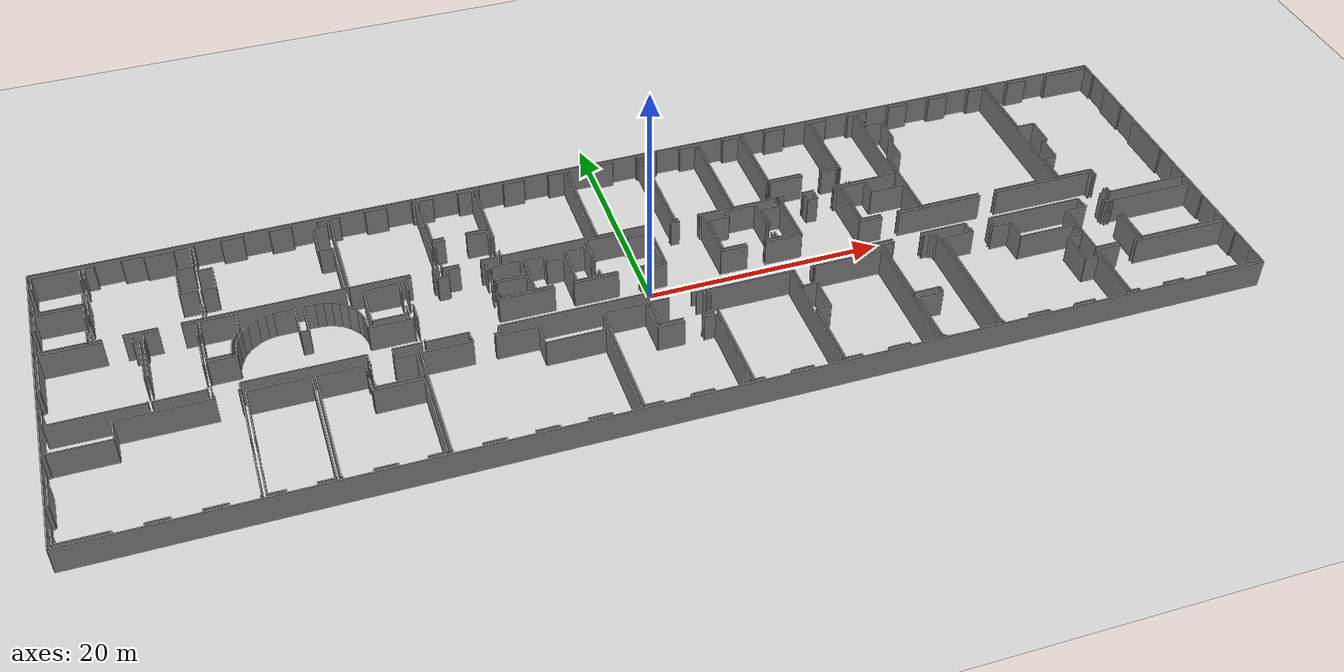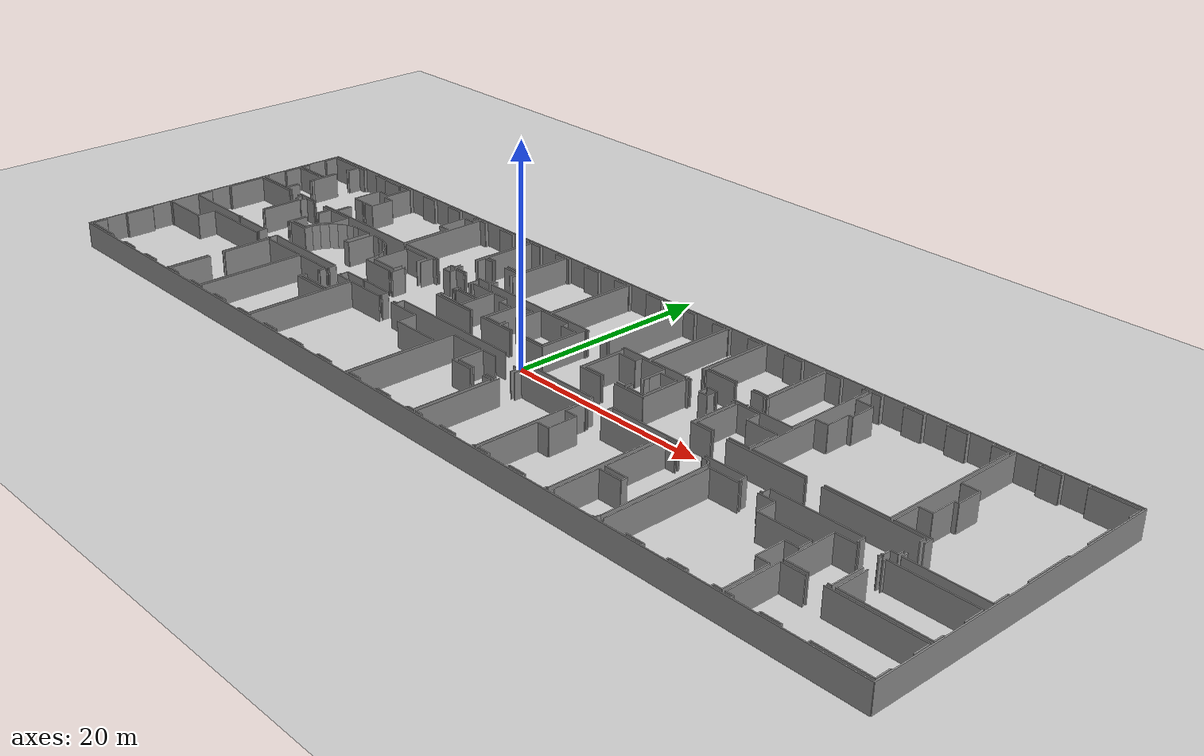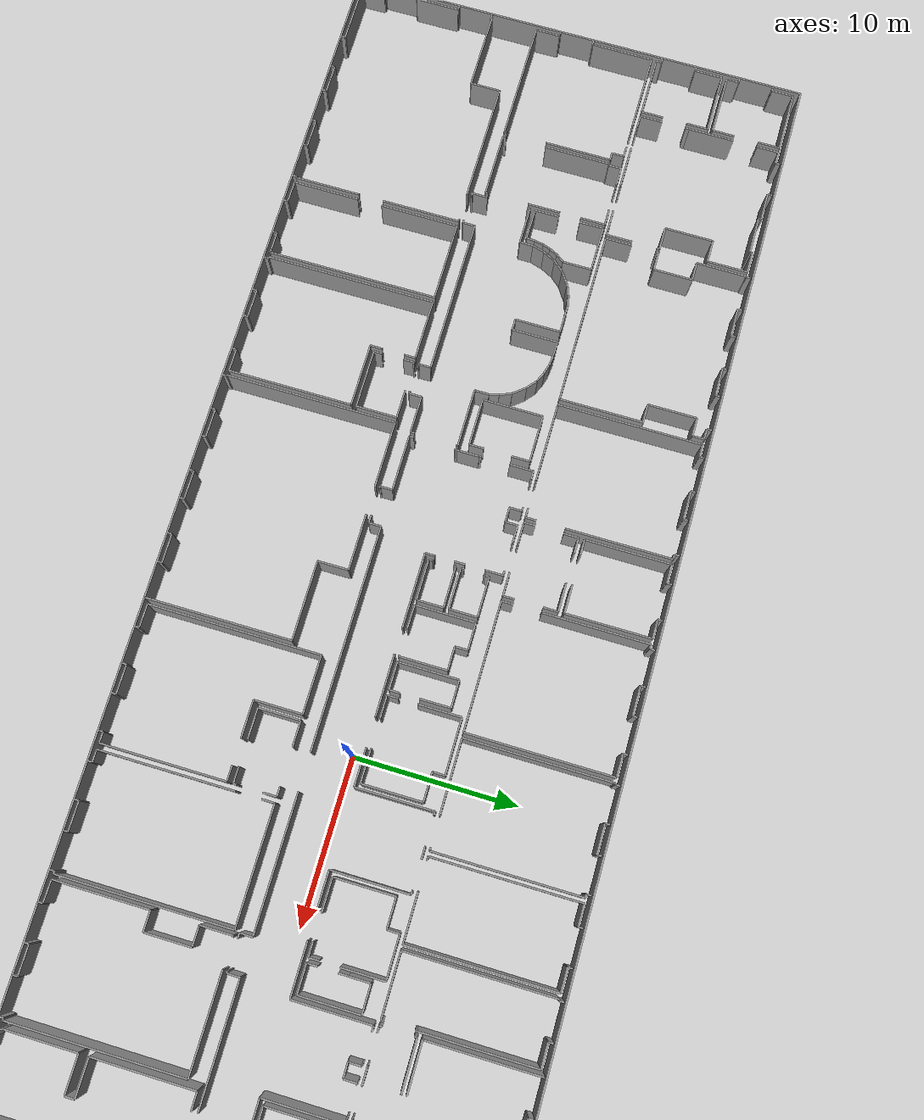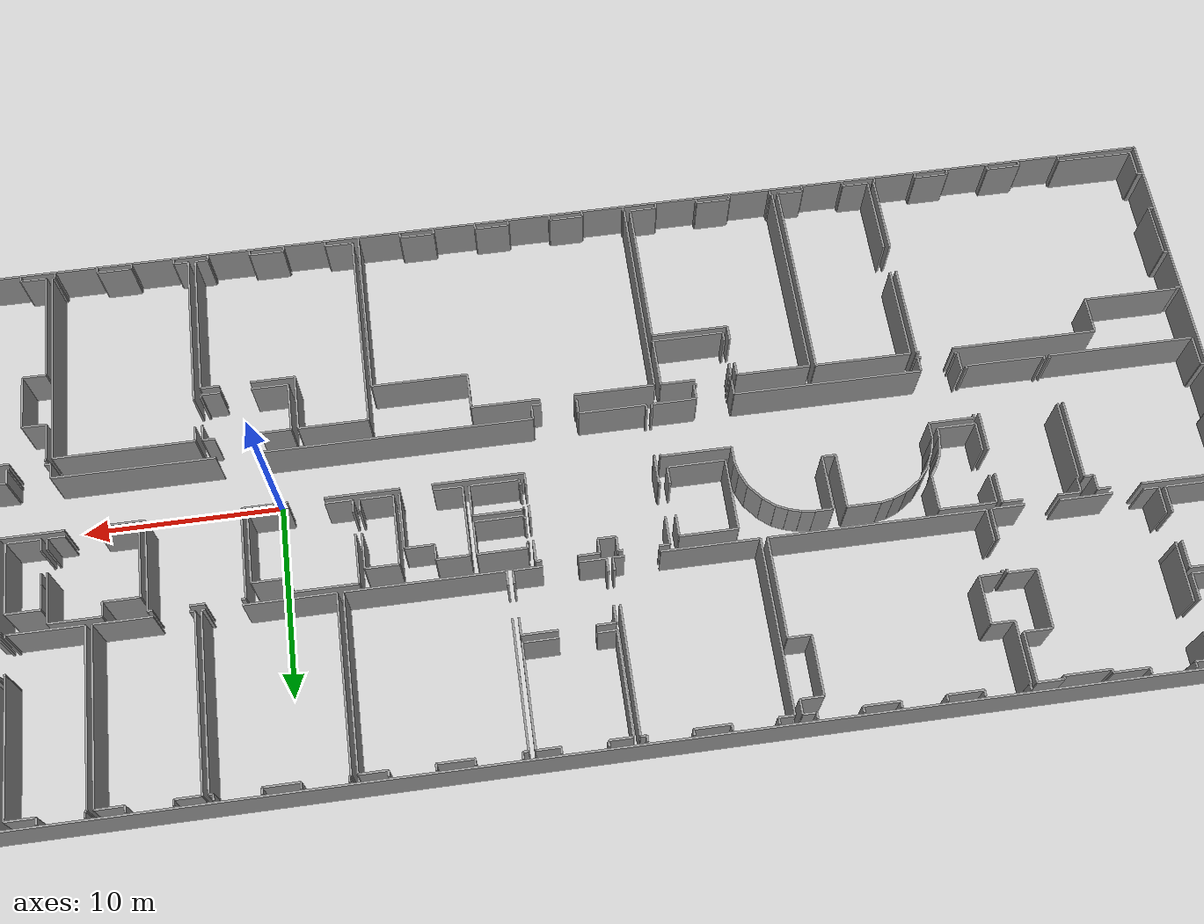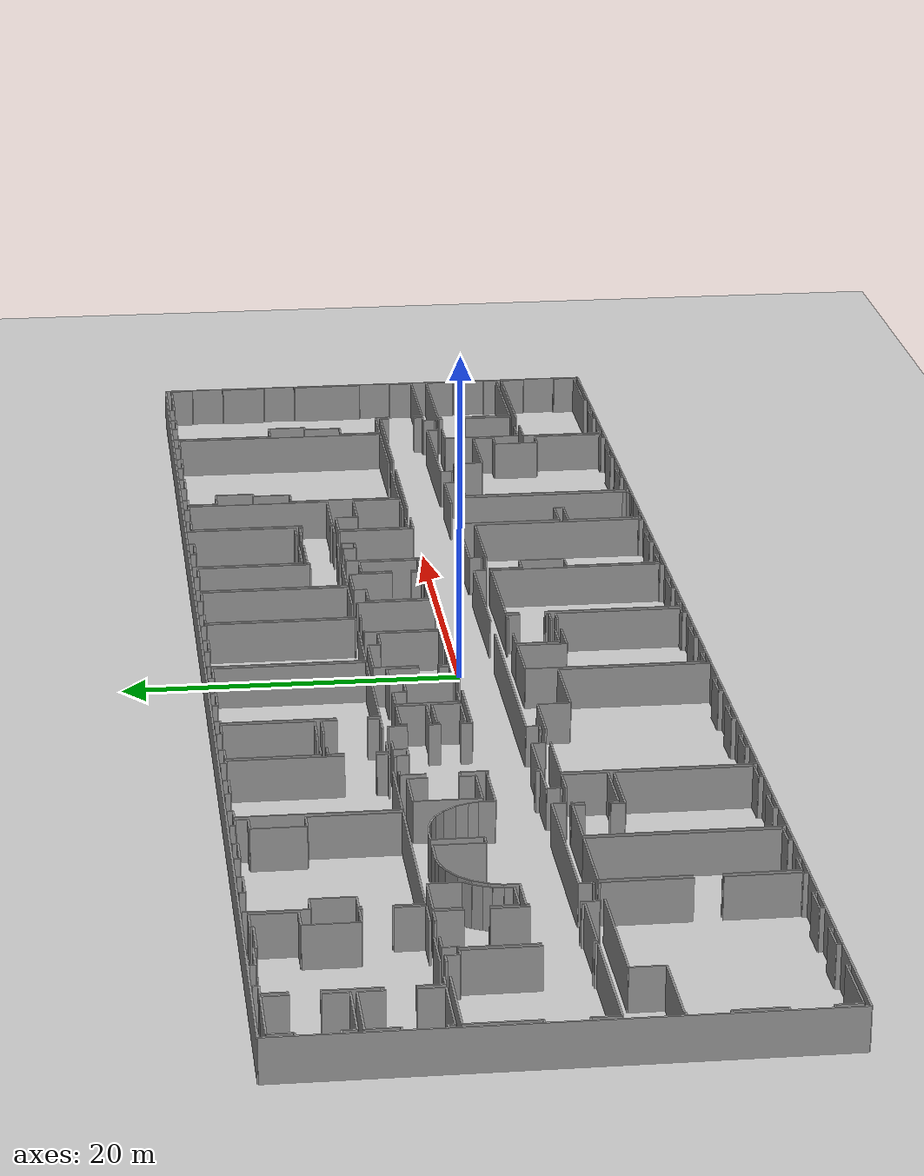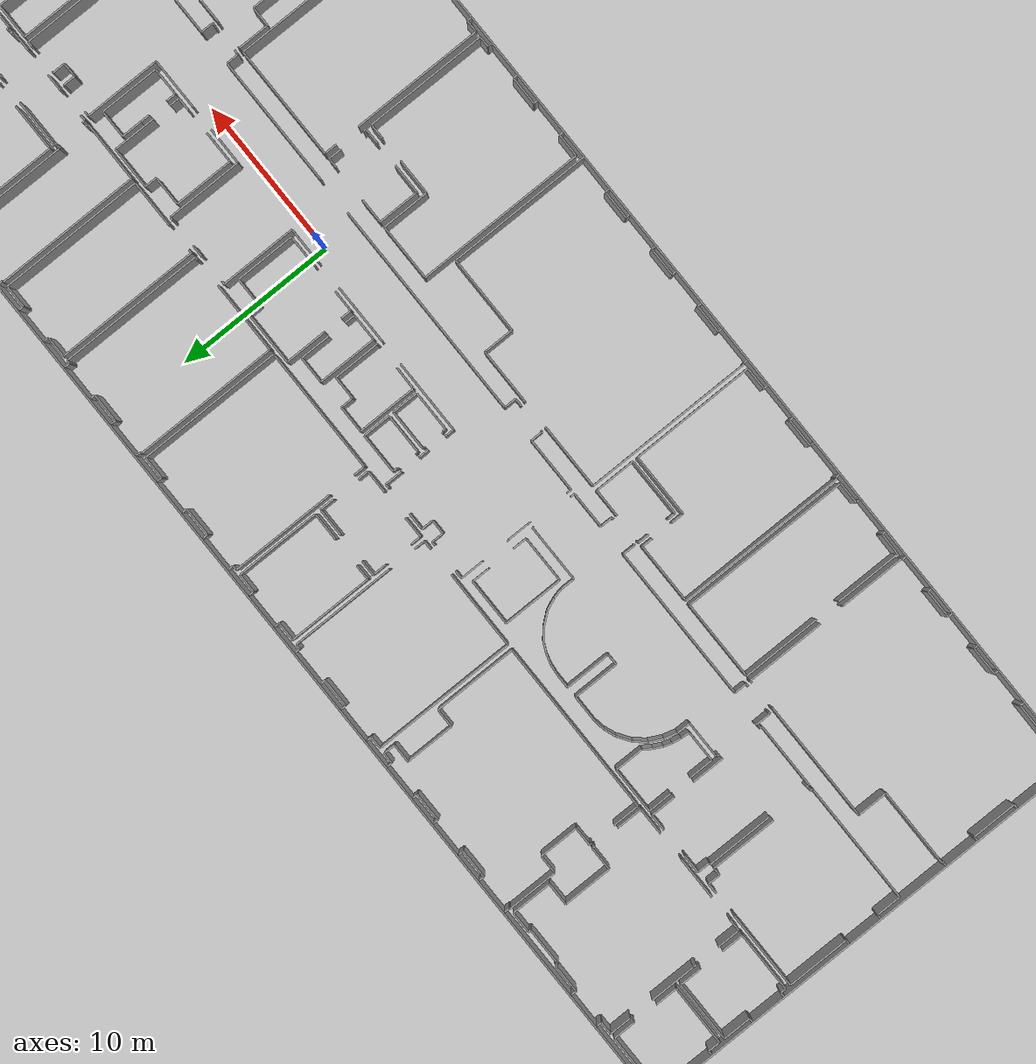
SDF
<sdf version="1.6">
  <world name="default">
    <light name="sun" type="directional">
      <cast_shadows>1</cast_shadows>
      <pose frame="">0 0 10 0 -0 0</pose>
      <diffuse>0.8 0.8 0.8 1</diffuse>
      <specular>0.1 0.1 0.1 1</specular>
      <attenuation>
        <range>1000</range>
        <constant>0.9</constant>
        <linear>0.01</linear>
        <quadratic>0.001</quadratic>
      </attenuation>
      <direction>-0.5 0.5 -1</direction>
    </light>
    <model name="ground_plane">
      <static>1</static>
      <link name="link">
        <collision name="collision">
          <geometry>
            <plane>
              <normal>0 0 1</normal>
              <size>100 100</size>
            </plane>
          </geometry>
          <surface>
            <friction>
              <ode>
                <mu>100</mu>
                <mu2>50</mu2>
              </ode>
              <torsional>
                <ode />
              </torsional>
            </friction>
            <contact>
              <ode />
            </contact>
            <bounce />
          </surface>
          <max_contacts>10</max_contacts>
        </collision>
        <visual name="visual">
          <cast_shadows>0</cast_shadows>
          <geometry>
            <plane>
              <normal>0 0 1</normal>
              <size>100 100</size>
            </plane>
          </geometry>
          <material>
            <script>
              <uri>file://media/materials/scripts/gazebo.material</uri>
              <name>Gazebo/Grey</name>
            </script>
          </material>
        </visual>
        <self_collide>0</self_collide>
        <kinematic>0</kinematic>
        <gravity>1</gravity>
      </link>
    </model>
    <gravity>0 0 -9.8</gravity>
    <magnetic_field>6e-06 2.3e-05 -4.2e-05</magnetic_field>
    <atmosphere type="adiabatic" />
    <physics default="0" name="default_physics" type="ode">
      <max_step_size>0.001</max_step_size>
      <real_time_factor>1</real_time_factor>
      <real_time_update_rate>1000</real_time_update_rate>
    </physics>
    <scene>
      <ambient>0.4 0.4 0.4 1</ambient>
      <background>0.7 0.7 0.7 1</background>
      <shadows>1</shadows>
    </scene>
    <spherical_coordinates>
      <surface_model>EARTH_WGS84</surface_model>
      <latitude_deg>0</latitude_deg>
      <longitude_deg>0</longitude_deg>
      <elevation>0</elevation>
      <heading_deg>0</heading_deg>
    </spherical_coordinates>
  <model name="0510032270_A_40_1_104">
		<static>1</static>
		<link name="Wall_0">
			<collision name="Wall_0_Collision">
				<geometry>
					<box>
						<size>0.768644293938 0.1 2.5</size>
					</box>
				</geometry>
				<pose frame="">0.384322146969 0 1.25 0 0 0</pose>
			</collision>
			<visual name="Wall_0_Visual">
				<pose frame="">0.384322146969 0 1.25 0 0 0</pose>
				<geometry>
					<box>
						<size>0.768644293938 0.1 2.5</size>
					</box>
				</geometry>
				<material>
					<script>
						<uri>file://media/materials/scripts/gazebo.material</uri>
						<name>Gazebo/Grey</name>
					</script>
					<ambient>1 1 1 1</ambient>
				</material>
			</visual>
			<pose frame="">0.305983709671 -4.74630545002 0 0 0 1.57079632679</pose>
		</link>
		<link name="Wall_1">
			<collision name="Wall_1_Collision">
				<geometry>
					<box>
						<size>0.293403814631 0.1 2.5</size>
					</box>
				</geometry>
				<pose frame="">0.146701907315 0 1.25 0 0 0</pose>
			</collision>
			<visual name="Wall_1_Visual">
				<pose frame="">0.146701907315 0 1.25 0 0 0</pose>
				<geometry>
					<box>
						<size>0.293403814631 0.1 2.5</size>
					</box>
				</geometry>
				<material>
					<script>
						<uri>file://media/materials/scripts/gazebo.material</uri>
						<name>Gazebo/Grey</name>
					</script>
					<ambient>1 1 1 1</ambient>
				</material>
			</visual>
			<pose frame="">0.305983709671 -3.97766115608 0 0 0 3.14159265359</pose>
		</link>
		<link name="Wall_2">
			<collision name="Wall_2_Collision">
				<geometry>
					<box>
						<size>0.282475825 0.1 2.5</size>
					</box>
				</geometry>
				<pose frame="">0.1412379125 0 1.25 0 0 0</pose>
			</collision>
			<visual name="Wall_2_Visual">
				<pose frame="">0.1412379125 0 1.25 0 0 0</pose>
				<geometry>
					<box>
						<size>0.282475825 0.1 2.5</size>
					</box>
				</geometry>
				<material>
					<script>
						<uri>file://media/materials/scripts/gazebo.material</uri>
						<name>Gazebo/Grey</name>
					</script>
					<ambient>1 1 1 1</ambient>
				</material>
			</visual>
			<pose frame="">0.0125798950405 -1.77465468823 0 0 0 0.0</pose>
		</link>
		<link name="Wall_3">
			<collision name="Wall_3_Collision">
				<geometry>
					<box>
						<size>1.35519778391 0.1 2.5</size>
					</box>
				</geometry>
				<pose frame="">0.677598891953 0 1.25 0 0 0</pose>
			</collision>
			<visual name="Wall_3_Visual">
				<pose frame="">0.677598891953 0 1.25 0 0 0</pose>
				<geometry>
					<box>
						<size>1.35519778391 0.1 2.5</size>
					</box>
				</geometry>
				<material>
					<script>
						<uri>file://media/materials/scripts/gazebo.material</uri>
						<name>Gazebo/Grey</name>
					</script>
					<ambient>1 1 1 1</ambient>
				</material>
			</visual>
			<pose frame="">0.29505572004 -1.77465468823 0 0 0 1.57079632679</pose>
		</link>
		<link name="Wall_4">
			<collision name="Wall_4_Collision">
				<geometry>
					<box>
						<size>3.79099584482 0.1 2.5</size>
					</box>
				</geometry>
				<pose frame="">1.89549792241 0 1.25 0 0 0</pose>
			</collision>
			<visual name="Wall_4_Visual">
				<pose frame="">1.89549792241 0 1.25 0 0 0</pose>
				<geometry>
					<box>
						<size>3.79099584482 0.1 2.5</size>
					</box>
				</geometry>
				<material>
					<script>
						<uri>file://media/materials/scripts/gazebo.material</uri>
						<name>Gazebo/Grey</name>
					</script>
					<ambient>1 1 1 1</ambient>
				</material>
			</visual>
			<pose frame="">0.29505572004 -0.419456904329 0 0 0 0.0</pose>
		</link>
		<link name="Wall_5">
			<collision name="Wall_5_Collision">
				<geometry>
					<box>
						<size>1.39484351373 0.1 2.5</size>
					</box>
				</geometry>
				<pose frame="">0.697421756865 0 1.25 0 0 0</pose>
			</collision>
			<visual name="Wall_5_Visual">
				<pose frame="">0.697421756865 0 1.25 0 0 0</pose>
				<geometry>
					<box>
						<size>1.39484351373 0.1 2.5</size>
					</box>
				</geometry>
				<material>
					<script>
						<uri>file://media/materials/scripts/gazebo.material</uri>
						<name>Gazebo/Grey</name>
					</script>
					<ambient>1 1 1 1</ambient>
				</material>
			</visual>
			<pose frame="">4.08605156486 -0.419456904329 0 0 0 -1.57079632679</pose>
		</link>
		<link name="Wall_6">
			<collision name="Wall_6_Collision">
				<geometry>
					<box>
						<size>1.38709226527 0.1 2.5</size>
					</box>
				</geometry>
				<pose frame="">0.693546132635 0 1.25 0 0 0</pose>
			</collision>
			<visual name="Wall_6_Visual">
				<pose frame="">0.693546132635 0 1.25 0 0 0</pose>
				<geometry>
					<box>
						<size>1.38709226527 0.1 2.5</size>
					</box>
				</geometry>
				<material>
					<script>
						<uri>file://media/materials/scripts/gazebo.material</uri>
						<name>Gazebo/Grey</name>
					</script>
					<ambient>1 1 1 1</ambient>
				</material>
			</visual>
			<pose frame="">4.08605156486 -3.36785392073 0 0 0 -1.57079632679</pose>
		</link>
		<link name="Wall_7">
			<collision name="Wall_7_Collision">
				<geometry>
					<box>
						<size>3.78007773097 0.1 2.5</size>
					</box>
				</geometry>
				<pose frame="">1.89003886548 0 1.25 0 0 0</pose>
			</collision>
			<visual name="Wall_7_Visual">
				<pose frame="">1.89003886548 0 1.25 0 0 0</pose>
				<geometry>
					<box>
						<size>3.78007773097 0.1 2.5</size>
					</box>
				</geometry>
				<material>
					<script>
						<uri>file://media/materials/scripts/gazebo.material</uri>
						<name>Gazebo/Grey</name>
					</script>
					<ambient>1 1 1 1</ambient>
				</material>
			</visual>
			<pose frame="">4.08605156486 -4.754946186 0 0 0 3.13930678961</pose>
		</link>
		<link name="Wall_8">
			<collision name="Wall_8_Collision">
				<geometry>
					<box>
						<size>0.342325628677 0.1 2.5</size>
					</box>
				</geometry>
				<pose frame="">0.171162814339 0 1.25 0 0 0</pose>
			</collision>
			<visual name="Wall_8_Visual">
				<pose frame="">0.171162814339 0 1.25 0 0 0</pose>
				<geometry>
					<box>
						<size>0.342325628677 0.1 2.5</size>
					</box>
				</geometry>
				<material>
					<script>
						<uri>file://media/materials/scripts/gazebo.material</uri>
						<name>Gazebo/Grey</name>
					</script>
					<ambient>1 1 1 1</ambient>
				</material>
			</visual>
			<pose frame="">0.311066495546 -9.39591089876 0 0 0 1.57079632679</pose>
		</link>
		<link name="Wall_9">
			<collision name="Wall_9_Collision">
				<geometry>
					<box>
						<size>0.311066495546 0.1 2.5</size>
					</box>
				</geometry>
				<pose frame="">0.155533247773 0 1.25 0 0 0</pose>
			</collision>
			<visual name="Wall_9_Visual">
				<pose frame="">0.155533247773 0 1.25 0 0 0</pose>
				<geometry>
					<box>
						<size>0.311066495546 0.1 2.5</size>
					</box>
				</geometry>
				<material>
					<script>
						<uri>file://media/materials/scripts/gazebo.material</uri>
						<name>Gazebo/Grey</name>
					</script>
					<ambient>1 1 1 1</ambient>
				</material>
			</visual>
			<pose frame="">0.311066495546 -9.05358527009 0 0 0 3.14159265359</pose>
		</link>
		<link name="Wall_10">
			<collision name="Wall_10_Collision">
				<geometry>
					<box>
						<size>0.292260187809 0.1 2.5</size>
					</box>
				</geometry>
				<pose frame="">0.146130093904 0 1.25 0 0 0</pose>
			</collision>
			<visual name="Wall_10_Visual">
				<pose frame="">0.146130093904 0 1.25 0 0 0</pose>
				<geometry>
					<box>
						<size>0.292260187809 0.1 2.5</size>
					</box>
				</geometry>
				<material>
					<script>
						<uri>file://media/materials/scripts/gazebo.material</uri>
						<name>Gazebo/Grey</name>
					</script>
					<ambient>1 1 1 1</ambient>
				</material>
			</visual>
			<pose frame="">0.0 -6.83304319097 0 0 0 0.0</pose>
		</link>
		<link name="Wall_11">
			<collision name="Wall_11_Collision">
				<geometry>
					<box>
						<size>1.76448911648 0.1 2.5</size>
					</box>
				</geometry>
				<pose frame="">0.882244558242 0 1.25 0 0 0</pose>
			</collision>
			<visual name="Wall_11_Visual">
				<pose frame="">0.882244558242 0 1.25 0 0 0</pose>
				<geometry>
					<box>
						<size>1.76448911648 0.1 2.5</size>
					</box>
				</geometry>
				<material>
					<script>
						<uri>file://media/materials/scripts/gazebo.material</uri>
						<name>Gazebo/Grey</name>
					</script>
					<ambient>1 1 1 1</ambient>
				</material>
			</visual>
			<pose frame="">0.292260187809 -6.83304319097 0 0 0 1.57079632679</pose>
		</link>
		<link name="Wall_12">
			<collision name="Wall_12_Collision">
				<geometry>
					<box>
						<size>3.79099584482 0.1 2.5</size>
					</box>
				</geometry>
				<pose frame="">1.89549792241 0 1.25 0 0 0</pose>
			</collision>
			<visual name="Wall_12_Visual">
				<pose frame="">1.89549792241 0 1.25 0 0 0</pose>
				<geometry>
					<box>
						<size>3.79099584482 0.1 2.5</size>
					</box>
				</geometry>
				<material>
					<script>
						<uri>file://media/materials/scripts/gazebo.material</uri>
						<name>Gazebo/Grey</name>
					</script>
					<ambient>1 1 1 1</ambient>
				</material>
			</visual>
			<pose frame="">0.292260187809 -5.06855407449 0 0 0 0.0</pose>
		</link>
		<link name="Wall_13">
			<collision name="Wall_13_Collision">
				<geometry>
					<box>
						<size>1.408058757 0.1 2.5</size>
					</box>
				</geometry>
				<pose frame="">0.704029378502 0 1.25 0 0 0</pose>
			</collision>
			<visual name="Wall_13_Visual">
				<pose frame="">0.704029378502 0 1.25 0 0 0</pose>
				<geometry>
					<box>
						<size>1.408058757 0.1 2.5</size>
					</box>
				</geometry>
				<material>
					<script>
						<uri>file://media/materials/scripts/gazebo.material</uri>
						<name>Gazebo/Grey</name>
					</script>
					<ambient>1 1 1 1</ambient>
				</material>
			</visual>
			<pose frame="">4.08325603263 -5.06855407449 0 0 0 -1.57079632679</pose>
		</link>
		<link name="Wall_14">
			<collision name="Wall_14_Collision">
				<geometry>
					<box>
						<size>1.38455087233 0.1 2.5</size>
					</box>
				</geometry>
				<pose frame="">0.692275436167 0 1.25 0 0 0</pose>
			</collision>
			<visual name="Wall_14_Visual">
				<pose frame="">0.692275436167 0 1.25 0 0 0</pose>
				<geometry>
					<box>
						<size>1.38455087233 0.1 2.5</size>
					</box>
				</geometry>
				<material>
					<script>
						<uri>file://media/materials/scripts/gazebo.material</uri>
						<name>Gazebo/Grey</name>
					</script>
					<ambient>1 1 1 1</ambient>
				</material>
			</visual>
			<pose frame="">4.08325603263 -8.00945398173 0 0 0 -1.57079632679</pose>
		</link>
		<link name="Wall_15">
			<collision name="Wall_15_Collision">
				<geometry>
					<box>
						<size>3.77219001864 0.1 2.5</size>
					</box>
				</geometry>
				<pose frame="">1.88609500932 0 1.25 0 0 0</pose>
			</collision>
			<visual name="Wall_15_Visual">
				<pose frame="">1.88609500932 0 1.25 0 0 0</pose>
				<geometry>
					<box>
						<size>3.77219001864 0.1 2.5</size>
					</box>
				</geometry>
				<material>
					<script>
						<uri>file://media/materials/scripts/gazebo.material</uri>
						<name>Gazebo/Grey</name>
					</script>
					<ambient>1 1 1 1</ambient>
				</material>
			</visual>
			<pose frame="">4.08325603263 -9.39400485406 0 0 0 -3.14108736494</pose>
		</link>
		<link name="Wall_16">
			<collision name="Wall_16_Collision">
				<geometry>
					<box>
						<size>2.86300621371 0.1 2.5</size>
					</box>
				</geometry>
				<pose frame="">1.43150310685 0 1.25 0 0 0</pose>
			</collision>
			<visual name="Wall_16_Visual">
				<pose frame="">1.43150310685 0 1.25 0 0 0</pose>
				<geometry>
					<box>
						<size>2.86300621371 0.1 2.5</size>
					</box>
				</geometry>
				<material>
					<script>
						<uri>file://media/materials/scripts/gazebo.material</uri>
						<name>Gazebo/Grey</name>
					</script>
					<ambient>1 1 1 1</ambient>
				</material>
			</visual>
			<pose frame="">4.40245498558 -6.20049048884 0 0 0 1.57079632679</pose>
		</link>
		<link name="Wall_17">
			<collision name="Wall_17_Collision">
				<geometry>
					<box>
						<size>1.37565599705 0.1 2.5</size>
					</box>
				</geometry>
				<pose frame="">0.687827998526 0 1.25 0 0 0</pose>
			</collision>
			<visual name="Wall_17_Visual">
				<pose frame="">0.687827998526 0 1.25 0 0 0</pose>
				<geometry>
					<box>
						<size>1.37565599705 0.1 2.5</size>
					</box>
				</geometry>
				<material>
					<script>
						<uri>file://media/materials/scripts/gazebo.material</uri>
						<name>Gazebo/Grey</name>
					</script>
					<ambient>1 1 1 1</ambient>
				</material>
			</visual>
			<pose frame="">4.40245498558 -1.7924444388 0 0 0 1.57079632679</pose>
		</link>
		<link name="Wall_18">
			<collision name="Wall_18_Collision">
				<geometry>
					<box>
						<size>0.799522218128 0.1 2.5</size>
					</box>
				</geometry>
				<pose frame="">0.399761109064 0 1.25 0 0 0</pose>
			</collision>
			<visual name="Wall_18_Visual">
				<pose frame="">0.399761109064 0 1.25 0 0 0</pose>
				<geometry>
					<box>
						<size>0.799522218128 0.1 2.5</size>
					</box>
				</geometry>
				<material>
					<script>
						<uri>file://media/materials/scripts/gazebo.material</uri>
						<name>Gazebo/Grey</name>
					</script>
					<ambient>1 1 1 1</ambient>
				</material>
			</visual>
			<pose frame="">4.40245498558 -0.416788441745 0 0 0 0.0</pose>
		</link>
		<link name="Wall_19">
			<collision name="Wall_19_Collision">
				<geometry>
					<box>
						<size>0.303442316734 0.1 2.5</size>
					</box>
				</geometry>
				<pose frame="">0.151721158367 0 1.25 0 0 0</pose>
			</collision>
			<visual name="Wall_19_Visual">
				<pose frame="">0.151721158367 0 1.25 0 0 0</pose>
				<geometry>
					<box>
						<size>0.303442316734 0.1 2.5</size>
					</box>
				</geometry>
				<material>
					<script>
						<uri>file://media/materials/scripts/gazebo.material</uri>
						<name>Gazebo/Grey</name>
					</script>
					<ambient>1 1 1 1</ambient>
				</material>
			</visual>
			<pose frame="">5.20197720371 -0.416788441745 0 0 0 1.57079632679</pose>
		</link>
		<link name="Wall_20">
			<collision name="Wall_20_Collision">
				<geometry>
					<box>
						<size>0.296199346862 0.1 2.5</size>
					</box>
				</geometry>
				<pose frame="">0.148099673431 0 1.25 0 0 0</pose>
			</collision>
			<visual name="Wall_20_Visual">
				<pose frame="">0.148099673431 0 1.25 0 0 0</pose>
				<geometry>
					<box>
						<size>0.296199346862 0.1 2.5</size>
					</box>
				</geometry>
				<material>
					<script>
						<uri>file://media/materials/scripts/gazebo.material</uri>
						<name>Gazebo/Grey</name>
					</script>
					<ambient>1 1 1 1</ambient>
				</material>
			</visual>
			<pose frame="">7.40536488049 -0.113346125011 0 0 0 -1.57079632679</pose>
		</link>
		<link name="Wall_21">
			<collision name="Wall_21_Collision">
				<geometry>
					<box>
						<size>1.79269857809 0.1 2.5</size>
					</box>
				</geometry>
				<pose frame="">0.896349289045 0 1.25 0 0 0</pose>
			</collision>
			<visual name="Wall_21_Visual">
				<pose frame="">0.896349289045 0 1.25 0 0 0</pose>
				<geometry>
					<box>
						<size>1.79269857809 0.1 2.5</size>
					</box>
				</geometry>
				<material>
					<script>
						<uri>file://media/materials/scripts/gazebo.material</uri>
						<name>Gazebo/Grey</name>
					</script>
					<ambient>1 1 1 1</ambient>
				</material>
			</visual>
			<pose frame="">7.40536488049 -0.409545471873 0 0 0 0.0</pose>
		</link>
		<link name="Wall_22">
			<collision name="Wall_22_Collision">
				<geometry>
					<box>
						<size>0.170019187517 0.1 2.5</size>
					</box>
				</geometry>
				<pose frame="">0.0850095937583 0 1.25 0 0 0</pose>
			</collision>
			<visual name="Wall_22_Visual">
				<pose frame="">0.0850095937583 0 1.25 0 0 0</pose>
				<geometry>
					<box>
						<size>0.170019187517 0.1 2.5</size>
					</box>
				</geometry>
				<material>
					<script>
						<uri>file://media/materials/scripts/gazebo.material</uri>
						<name>Gazebo/Grey</name>
					</script>
					<ambient>1 1 1 1</ambient>
				</material>
			</visual>
			<pose frame="">9.19806345858 -0.409545471873 0 0 0 -1.57079632679</pose>
		</link>
		<link name="Wall_23">
			<collision name="Wall_23_Collision">
				<geometry>
					<box>
						<size>2.34189359188 0.1 2.5</size>
					</box>
				</geometry>
				<pose frame="">1.17094679594 0 1.25 0 0 0</pose>
			</collision>
			<visual name="Wall_23_Visual">
				<pose frame="">1.17094679594 0 1.25 0 0 0</pose>
				<geometry>
					<box>
						<size>2.34189359188 0.1 2.5</size>
					</box>
				</geometry>
				<material>
					<script>
						<uri>file://media/materials/scripts/gazebo.material</uri>
						<name>Gazebo/Grey</name>
					</script>
					<ambient>1 1 1 1</ambient>
				</material>
			</visual>
			<pose frame="">9.19806345858 -0.57956465939 0 0 0 0.0</pose>
		</link>
		<link name="Wall_24">
			<collision name="Wall_24_Collision">
				<geometry>
					<box>
						<size>0.154262551304 0.1 2.5</size>
					</box>
				</geometry>
				<pose frame="">0.0771312756522 0 1.25 0 0 0</pose>
			</collision>
			<visual name="Wall_24_Visual">
				<pose frame="">0.0771312756522 0 1.25 0 0 0</pose>
				<geometry>
					<box>
						<size>0.154262551304 0.1 2.5</size>
					</box>
				</geometry>
				<material>
					<script>
						<uri>file://media/materials/scripts/gazebo.material</uri>
						<name>Gazebo/Grey</name>
					</script>
					<ambient>1 1 1 1</ambient>
				</material>
			</visual>
			<pose frame="">11.5399570505 -0.57956465939 0 0 0 1.57079632679</pose>
		</link>
		<link name="Wall_25">
			<collision name="Wall_25_Collision">
				<geometry>
					<box>
						<size>1.33346887429 0.1 2.5</size>
					</box>
				</geometry>
				<pose frame="">0.666734437145 0 1.25 0 0 0</pose>
			</collision>
			<visual name="Wall_25_Visual">
				<pose frame="">0.666734437145 0 1.25 0 0 0</pose>
				<geometry>
					<box>
						<size>1.33346887429 0.1 2.5</size>
					</box>
				</geometry>
				<material>
					<script>
						<uri>file://media/materials/scripts/gazebo.material</uri>
						<name>Gazebo/Grey</name>
					</script>
					<ambient>1 1 1 1</ambient>
				</material>
			</visual>
			<pose frame="">11.5399570505 -0.425302108085 0 0 0 0.0</pose>
		</link>
		<link name="Wall_26">
			<collision name="Wall_26_Collision">
				<geometry>
					<box>
						<size>2.53021080854 0.1 2.5</size>
					</box>
				</geometry>
				<pose frame="">1.26510540427 0 1.25 0 0 0</pose>
			</collision>
			<visual name="Wall_26_Visual">
				<pose frame="">1.26510540427 0 1.25 0 0 0</pose>
				<geometry>
					<box>
						<size>2.53021080854 0.1 2.5</size>
					</box>
				</geometry>
				<material>
					<script>
						<uri>file://media/materials/scripts/gazebo.material</uri>
						<name>Gazebo/Grey</name>
					</script>
					<ambient>1 1 1 1</ambient>
				</material>
			</visual>
			<pose frame="">12.8734259247 -0.425302108085 0 0 0 -1.57079632679</pose>
		</link>
		<link name="Wall_27">
			<collision name="Wall_27_Collision">
				<geometry>
					<box>
						<size>1.42279883604 0.1 2.5</size>
					</box>
				</geometry>
				<pose frame="">0.711399418021 0 1.25 0 0 0</pose>
			</collision>
			<visual name="Wall_27_Visual">
				<pose frame="">0.711399418021 0 1.25 0 0 0</pose>
				<geometry>
					<box>
						<size>1.42279883604 0.1 2.5</size>
					</box>
				</geometry>
				<material>
					<script>
						<uri>file://media/materials/scripts/gazebo.material</uri>
						<name>Gazebo/Grey</name>
					</script>
					<ambient>1 1 1 1</ambient>
				</material>
			</visual>
			<pose frame="">12.8734259247 -2.95551291663 0 0 0 3.14159265359</pose>
		</link>
		<link name="Wall_28">
			<collision name="Wall_28_Collision">
				<geometry>
					<box>
						<size>3.04484287838 0.1 2.5</size>
					</box>
				</geometry>
				<pose frame="">1.52242143919 0 1.25 0 0 0</pose>
			</collision>
			<visual name="Wall_28_Visual">
				<pose frame="">1.52242143919 0 1.25 0 0 0</pose>
				<geometry>
					<box>
						<size>3.04484287838 0.1 2.5</size>
					</box>
				</geometry>
				<material>
					<script>
						<uri>file://media/materials/scripts/gazebo.material</uri>
						<name>Gazebo/Grey</name>
					</script>
					<ambient>1 1 1 1</ambient>
				</material>
			</visual>
			<pose frame="">11.4506270887 -2.95551291663 0 0 0 -1.57079632679</pose>
		</link>
		<link name="Wall_29">
			<collision name="Wall_29_Collision">
				<geometry>
					<box>
						<size>1.4568535014 0.1 2.5</size>
					</box>
				</geometry>
				<pose frame="">0.728426750702 0 1.25 0 0 0</pose>
			</collision>
			<visual name="Wall_29_Visual">
				<pose frame="">0.728426750702 0 1.25 0 0 0</pose>
				<geometry>
					<box>
						<size>1.4568535014 0.1 2.5</size>
					</box>
				</geometry>
				<material>
					<script>
						<uri>file://media/materials/scripts/gazebo.material</uri>
						<name>Gazebo/Grey</name>
					</script>
					<ambient>1 1 1 1</ambient>
				</material>
			</visual>
			<pose frame="">11.4506270887 -6.00035579501 0 0 0 0.0</pose>
		</link>
		<link name="Wall_30">
			<collision name="Wall_30_Collision">
				<geometry>
					<box>
						<size>0.174466625157 0.1 2.5</size>
					</box>
				</geometry>
				<pose frame="">0.0872333125786 0 1.25 0 0 0</pose>
			</collision>
			<visual name="Wall_30_Visual">
				<pose frame="">0.0872333125786 0 1.25 0 0 0</pose>
				<geometry>
					<box>
						<size>0.174466625157 0.1 2.5</size>
					</box>
				</geometry>
				<material>
					<script>
						<uri>file://media/materials/scripts/gazebo.material</uri>
						<name>Gazebo/Grey</name>
					</script>
					<ambient>1 1 1 1</ambient>
				</material>
			</visual>
			<pose frame="">12.9074805901 -6.00035579501 0 0 0 -1.57079632679</pose>
		</link>
		<link name="Wall_31">
			<collision name="Wall_31_Collision">
				<geometry>
					<box>
						<size>1.64250225549 0.1 2.5</size>
					</box>
				</geometry>
				<pose frame="">0.821251127743 0 1.25 0 0 0</pose>
			</collision>
			<visual name="Wall_31_Visual">
				<pose frame="">0.821251127743 0 1.25 0 0 0</pose>
				<geometry>
					<box>
						<size>1.64250225549 0.1 2.5</size>
					</box>
				</geometry>
				<material>
					<script>
						<uri>file://media/materials/scripts/gazebo.material</uri>
						<name>Gazebo/Grey</name>
					</script>
					<ambient>1 1 1 1</ambient>
				</material>
			</visual>
			<pose frame="">12.9074805901 -7.76243058821 0 0 0 -1.57079632679</pose>
		</link>
		<link name="Wall_32">
			<collision name="Wall_32_Collision">
				<geometry>
					<box>
						<size>1.72192078478 0.1 2.5</size>
					</box>
				</geometry>
				<pose frame="">0.860960392391 0 1.25 0 0 0</pose>
			</collision>
			<visual name="Wall_32_Visual">
				<pose frame="">0.860960392391 0 1.25 0 0 0</pose>
				<geometry>
					<box>
						<size>1.72192078478 0.1 2.5</size>
					</box>
				</geometry>
				<material>
					<script>
						<uri>file://media/materials/scripts/gazebo.material</uri>
						<name>Gazebo/Grey</name>
					</script>
					<ambient>1 1 1 1</ambient>
				</material>
			</visual>
			<pose frame="">12.9074805901 -9.40493284369 0 0 0 3.14159265359</pose>
		</link>
		<link name="Wall_33">
			<collision name="Wall_33_Collision">
				<geometry>
					<box>
						<size>2.69895929959 0.1 2.5</size>
					</box>
				</geometry>
				<pose frame="">1.3494796498 0 1.25 0 0 0</pose>
			</collision>
			<visual name="Wall_33_Visual">
				<pose frame="">1.3494796498 0 1.25 0 0 0</pose>
				<geometry>
					<box>
						<size>2.69895929959 0.1 2.5</size>
					</box>
				</geometry>
				<material>
					<script>
						<uri>file://media/materials/scripts/gazebo.material</uri>
						<name>Gazebo/Grey</name>
					</script>
					<ambient>1 1 1 1</ambient>
				</material>
			</visual>
			<pose frame="">9.42755124084 -9.40493284369 0 0 0 3.14159265359</pose>
		</link>
		<link name="Wall_34">
			<collision name="Wall_34_Collision">
				<geometry>
					<box>
						<size>0.762163741947 0.1 2.5</size>
					</box>
				</geometry>
				<pose frame="">0.381081870973 0 1.25 0 0 0</pose>
			</collision>
			<visual name="Wall_34_Visual">
				<pose frame="">0.381081870973 0 1.25 0 0 0</pose>
				<geometry>
					<box>
						<size>0.762163741947 0.1 2.5</size>
					</box>
				</geometry>
				<material>
					<script>
						<uri>file://media/materials/scripts/gazebo.material</uri>
						<name>Gazebo/Grey</name>
					</script>
					<ambient>1 1 1 1</ambient>
				</material>
			</visual>
			<pose frame="">5.16220440423 -9.40493284369 0 0 0 3.14159265359</pose>
		</link>
		<link name="Wall_35">
			<collision name="Wall_35_Collision">
				<geometry>
					<box>
						<size>1.42724627368 0.1 2.5</size>
					</box>
				</geometry>
				<pose frame="">0.713623136841 0 1.25 0 0 0</pose>
			</collision>
			<visual name="Wall_35_Visual">
				<pose frame="">0.713623136841 0 1.25 0 0 0</pose>
				<geometry>
					<box>
						<size>1.42724627368 0.1 2.5</size>
					</box>
				</geometry>
				<material>
					<script>
						<uri>file://media/materials/scripts/gazebo.material</uri>
						<name>Gazebo/Grey</name>
					</script>
					<ambient>1 1 1 1</ambient>
				</material>
			</visual>
			<pose frame="">4.40004066229 -9.40493284369 0 0 0 1.57079632679</pose>
		</link>
		<link name="Wall_36">
			<collision name="Wall_36_Collision">
				<geometry>
					<box>
						<size>0.234074740931 0.1 2.5</size>
					</box>
				</geometry>
				<pose frame="">0.117037370466 0 1.25 0 0 0</pose>
			</collision>
			<visual name="Wall_36_Visual">
				<pose frame="">0.117037370466 0 1.25 0 0 0</pose>
				<geometry>
					<box>
						<size>0.234074740931 0.1 2.5</size>
					</box>
				</geometry>
				<material>
					<script>
						<uri>file://media/materials/scripts/gazebo.material</uri>
						<name>Gazebo/Grey</name>
					</script>
					<ambient>1 1 1 1</ambient>
				</material>
			</visual>
			<pose frame="">4.40004066229 -6.43455277838 0 0 0 1.56048181746</pose>
		</link>
		<link name="Wall_37">
			<collision name="Wall_37_Collision">
				<geometry>
					<box>
						<size>3.14853171023 0.1 2.5</size>
					</box>
				</geometry>
				<pose frame="">1.57426585512 0 1.25 0 0 0</pose>
			</collision>
			<visual name="Wall_37_Visual">
				<pose frame="">1.57426585512 0 1.25 0 0 0</pose>
				<geometry>
					<box>
						<size>3.14853171023 0.1 2.5</size>
					</box>
				</geometry>
				<material>
					<script>
						<uri>file://media/materials/scripts/gazebo.material</uri>
						<name>Gazebo/Grey</name>
					</script>
					<ambient>1 1 1 1</ambient>
				</material>
			</visual>
			<pose frame="">13.1584431427 -3.55795011246 0 0 0 1.57079632679</pose>
		</link>
		<link name="Wall_38">
			<collision name="Wall_38_Collision">
				<geometry>
					<box>
						<size>0.0537504606275 0.1 2.5</size>
					</box>
				</geometry>
				<pose frame="">0.0268752303137 0 1.25 0 0 0</pose>
			</collision>
			<visual name="Wall_38_Visual">
				<pose frame="">0.0268752303137 0 1.25 0 0 0</pose>
				<geometry>
					<box>
						<size>0.0537504606275 0.1 2.5</size>
					</box>
				</geometry>
				<material>
					<script>
						<uri>file://media/materials/scripts/gazebo.material</uri>
						<name>Gazebo/Grey</name>
					</script>
					<ambient>1 1 1 1</ambient>
				</material>
			</visual>
			<pose frame="">13.1584431427 -0.409418402226 0 0 0 0.0</pose>
		</link>
		<link name="Wall_39">
			<collision name="Wall_39_Collision">
				<geometry>
					<box>
						<size>0.305348361437 0.1 2.5</size>
					</box>
				</geometry>
				<pose frame="">0.152674180718 0 1.25 0 0 0</pose>
			</collision>
			<visual name="Wall_39_Visual">
				<pose frame="">0.152674180718 0 1.25 0 0 0</pose>
				<geometry>
					<box>
						<size>0.305348361437 0.1 2.5</size>
					</box>
				</geometry>
				<material>
					<script>
						<uri>file://media/materials/scripts/gazebo.material</uri>
						<name>Gazebo/Grey</name>
					</script>
					<ambient>1 1 1 1</ambient>
				</material>
			</visual>
			<pose frame="">13.2121936033 -0.409418402226 0 0 0 1.57079632679</pose>
		</link>
		<link name="Wall_40">
			<collision name="Wall_40_Collision">
				<geometry>
					<box>
						<size>0.310431147312 0.1 2.5</size>
					</box>
				</geometry>
				<pose frame="">0.155215573656 0 1.25 0 0 0</pose>
			</collision>
			<visual name="Wall_40_Visual">
				<pose frame="">0.155215573656 0 1.25 0 0 0</pose>
				<geometry>
					<box>
						<size>0.310431147312 0.1 2.5</size>
					</box>
				</geometry>
				<material>
					<script>
						<uri>file://media/materials/scripts/gazebo.material</uri>
						<name>Gazebo/Grey</name>
					</script>
					<ambient>1 1 1 1</ambient>
				</material>
			</visual>
			<pose frame="">15.418122673 -0.104070040789 0 0 0 -1.57079632679</pose>
		</link>
		<link name="Wall_41">
			<collision name="Wall_41_Collision">
				<geometry>
					<box>
						<size>1.79714601573 0.1 2.5</size>
					</box>
				</geometry>
				<pose frame="">0.898573007866 0 1.25 0 0 0</pose>
			</collision>
			<visual name="Wall_41_Visual">
				<pose frame="">0.898573007866 0 1.25 0 0 0</pose>
				<geometry>
					<box>
						<size>1.79714601573 0.1 2.5</size>
					</box>
				</geometry>
				<material>
					<script>
						<uri>file://media/materials/scripts/gazebo.material</uri>
						<name>Gazebo/Grey</name>
					</script>
					<ambient>1 1 1 1</ambient>
				</material>
			</visual>
			<pose frame="">15.418122673 -0.414501188101 0 0 0 0.0</pose>
		</link>
		<link name="Wall_42">
			<collision name="Wall_42_Collision">
				<geometry>
					<box>
						<size>0.31132063484 0.1 2.5</size>
					</box>
				</geometry>
				<pose frame="">0.15566031742 0 1.25 0 0 0</pose>
			</collision>
			<visual name="Wall_42_Visual">
				<pose frame="">0.15566031742 0 1.25 0 0 0</pose>
				<geometry>
					<box>
						<size>0.31132063484 0.1 2.5</size>
					</box>
				</geometry>
				<material>
					<script>
						<uri>file://media/materials/scripts/gazebo.material</uri>
						<name>Gazebo/Grey</name>
					</script>
					<ambient>1 1 1 1</ambient>
				</material>
			</visual>
			<pose frame="">17.2152686888 -0.414501188101 0 0 0 1.57079632679</pose>
		</link>
		<link name="Wall_43">
			<collision name="Wall_43_Collision">
				<geometry>
					<box>
						<size>0.31132063484 0.1 2.5</size>
					</box>
				</geometry>
				<pose frame="">0.15566031742 0 1.25 0 0 0</pose>
			</collision>
			<visual name="Wall_43_Visual">
				<pose frame="">0.15566031742 0 1.25 0 0 0</pose>
				<geometry>
					<box>
						<size>0.31132063484 0.1 2.5</size>
					</box>
				</geometry>
				<material>
					<script>
						<uri>file://media/materials/scripts/gazebo.material</uri>
						<name>Gazebo/Grey</name>
					</script>
					<ambient>1 1 1 1</ambient>
				</material>
			</visual>
			<pose frame="">19.411286326 -0.103180553261 0 0 0 -1.57079632679</pose>
		</link>
		<link name="Wall_44">
			<collision name="Wall_44_Collision">
				<geometry>
					<box>
						<size>1.79600238891 0.1 2.5</size>
					</box>
				</geometry>
				<pose frame="">0.898001194455 0 1.25 0 0 0</pose>
			</collision>
			<visual name="Wall_44_Visual">
				<pose frame="">0.898001194455 0 1.25 0 0 0</pose>
				<geometry>
					<box>
						<size>1.79600238891 0.1 2.5</size>
					</box>
				</geometry>
				<material>
					<script>
						<uri>file://media/materials/scripts/gazebo.material</uri>
						<name>Gazebo/Grey</name>
					</script>
					<ambient>1 1 1 1</ambient>
				</material>
			</visual>
			<pose frame="">19.411286326 -0.414501188101 0 0 0 0.0</pose>
		</link>
		<link name="Wall_45">
			<collision name="Wall_45_Collision">
				<geometry>
					<box>
						<size>0.304713013203 0.1 2.5</size>
					</box>
				</geometry>
				<pose frame="">0.152356506601 0 1.25 0 0 0</pose>
			</collision>
			<visual name="Wall_45_Visual">
				<pose frame="">0.152356506601 0 1.25 0 0 0</pose>
				<geometry>
					<box>
						<size>0.304713013203 0.1 2.5</size>
					</box>
				</geometry>
				<material>
					<script>
						<uri>file://media/materials/scripts/gazebo.material</uri>
						<name>Gazebo/Grey</name>
					</script>
					<ambient>1 1 1 1</ambient>
				</material>
			</visual>
			<pose frame="">21.2072887149 -0.414501188101 0 0 0 1.57079632679</pose>
		</link>
		<link name="Wall_46">
			<collision name="Wall_46_Collision">
				<geometry>
					<box>
						<size>0.303442316734 0.1 2.5</size>
					</box>
				</geometry>
				<pose frame="">0.151721158367 0 1.25 0 0 0</pose>
			</collision>
			<visual name="Wall_46_Visual">
				<pose frame="">0.151721158367 0 1.25 0 0 0</pose>
				<geometry>
					<box>
						<size>0.303442316734 0.1 2.5</size>
					</box>
				</geometry>
				<material>
					<script>
						<uri>file://media/materials/scripts/gazebo.material</uri>
						<name>Gazebo/Grey</name>
					</script>
					<ambient>1 1 1 1</ambient>
				</material>
			</visual>
			<pose frame="">23.4142343418 -0.109788174899 0 0 0 -1.57079632679</pose>
		</link>
		<link name="Wall_47">
			<collision name="Wall_47_Collision">
				<geometry>
					<box>
						<size>0.661016303036 0.1 2.5</size>
					</box>
				</geometry>
				<pose frame="">0.330508151518 0 1.25 0 0 0</pose>
			</collision>
			<visual name="Wall_47_Visual">
				<pose frame="">0.330508151518 0 1.25 0 0 0</pose>
				<geometry>
					<box>
						<size>0.661016303036 0.1 2.5</size>
					</box>
				</geometry>
				<material>
					<script>
						<uri>file://media/materials/scripts/gazebo.material</uri>
						<name>Gazebo/Grey</name>
					</script>
					<ambient>1 1 1 1</ambient>
				</material>
			</visual>
			<pose frame="">23.4142343418 -0.413230491632 0 0 0 0.0</pose>
		</link>
		<link name="Wall_48">
			<collision name="Wall_48_Collision">
				<geometry>
					<box>
						<size>0.73319186246 0.1 2.5</size>
					</box>
				</geometry>
				<pose frame="">0.36659593123 0 1.25 0 0 0</pose>
			</collision>
			<visual name="Wall_48_Visual">
				<pose frame="">0.36659593123 0 1.25 0 0 0</pose>
				<geometry>
					<box>
						<size>0.73319186246 0.1 2.5</size>
					</box>
				</geometry>
				<material>
					<script>
						<uri>file://media/materials/scripts/gazebo.material</uri>
						<name>Gazebo/Grey</name>
					</script>
					<ambient>1 1 1 1</ambient>
				</material>
			</visual>
			<pose frame="">24.0752506449 -0.413230491632 0 0 0 -1.57079632679</pose>
		</link>
		<link name="Wall_49">
			<collision name="Wall_49_Collision">
				<geometry>
					<box>
						<size>1.15951052772 0.1 2.5</size>
					</box>
				</geometry>
				<pose frame="">0.57975526386 0 1.25 0 0 0</pose>
			</collision>
			<visual name="Wall_49_Visual">
				<pose frame="">0.57975526386 0 1.25 0 0 0</pose>
				<geometry>
					<box>
						<size>1.15951052772 0.1 2.5</size>
					</box>
				</geometry>
				<material>
					<script>
						<uri>file://media/materials/scripts/gazebo.material</uri>
						<name>Gazebo/Grey</name>
					</script>
					<ambient>1 1 1 1</ambient>
				</material>
			</visual>
			<pose frame="">24.0752506449 -1.14642235409 0 0 0 3.14159265359</pose>
		</link>
		<link name="Wall_50">
			<collision name="Wall_50_Collision">
				<geometry>
					<box>
						<size>3.04141199792 0.1 2.5</size>
					</box>
				</geometry>
				<pose frame="">1.52070599896 0 1.25 0 0 0</pose>
			</collision>
			<visual name="Wall_50_Visual">
				<pose frame="">1.52070599896 0 1.25 0 0 0</pose>
				<geometry>
					<box>
						<size>3.04141199792 0.1 2.5</size>
					</box>
				</geometry>
				<material>
					<script>
						<uri>file://media/materials/scripts/gazebo.material</uri>
						<name>Gazebo/Grey</name>
					</script>
					<ambient>1 1 1 1</ambient>
				</material>
			</visual>
			<pose frame="">22.9157401172 -1.14642235409 0 0 0 -1.57079632679</pose>
		</link>
		<link name="Wall_51">
			<collision name="Wall_51_Collision">
				<geometry>
					<box>
						<size>1.16675349759 0.1 2.5</size>
					</box>
				</geometry>
				<pose frame="">0.583376748796 0 1.25 0 0 0</pose>
			</collision>
			<visual name="Wall_51_Visual">
				<pose frame="">0.583376748796 0 1.25 0 0 0</pose>
				<geometry>
					<box>
						<size>1.16675349759 0.1 2.5</size>
					</box>
				</geometry>
				<material>
					<script>
						<uri>file://media/materials/scripts/gazebo.material</uri>
						<name>Gazebo/Grey</name>
					</script>
					<ambient>1 1 1 1</ambient>
				</material>
			</visual>
			<pose frame="">22.9157401172 -4.18783435201 0 0 0 0.0</pose>
		</link>
		<link name="Wall_52">
			<collision name="Wall_52_Collision">
				<geometry>
					<box>
						<size>5.19791097501 0.1 2.5</size>
					</box>
				</geometry>
				<pose frame="">2.5989554875 0 1.25 0 0 0</pose>
			</collision>
			<visual name="Wall_52_Visual">
				<pose frame="">2.5989554875 0 1.25 0 0 0</pose>
				<geometry>
					<box>
						<size>5.19791097501 0.1 2.5</size>
					</box>
				</geometry>
				<material>
					<script>
						<uri>file://media/materials/scripts/gazebo.material</uri>
						<name>Gazebo/Grey</name>
					</script>
					<ambient>1 1 1 1</ambient>
				</material>
			</visual>
			<pose frame="">24.0824936148 -4.18783435201 0 0 0 -1.57079632679</pose>
		</link>
		<link name="Wall_53">
			<collision name="Wall_53_Collision">
				<geometry>
					<box>
						<size>10.9384093422 0.1 2.5</size>
					</box>
				</geometry>
				<pose frame="">5.46920467108 0 1.25 0 0 0</pose>
			</collision>
			<visual name="Wall_53_Visual">
				<pose frame="">5.46920467108 0 1.25 0 0 0</pose>
				<geometry>
					<box>
						<size>10.9384093422 0.1 2.5</size>
					</box>
				</geometry>
				<material>
					<script>
						<uri>file://media/materials/scripts/gazebo.material</uri>
						<name>Gazebo/Grey</name>
					</script>
					<ambient>1 1 1 1</ambient>
				</material>
			</visual>
			<pose frame="">24.0824936148 -9.38574532701 0 0 0 3.14159265359</pose>
		</link>
		<link name="Wall_54">
			<collision name="Wall_54_Collision">
				<geometry>
					<box>
						<size>1.67388845826 0.1 2.5</size>
					</box>
				</geometry>
				<pose frame="">0.836944229132 0 1.25 0 0 0</pose>
			</collision>
			<visual name="Wall_54_Visual">
				<pose frame="">0.836944229132 0 1.25 0 0 0</pose>
				<geometry>
					<box>
						<size>1.67388845826 0.1 2.5</size>
					</box>
				</geometry>
				<material>
					<script>
						<uri>file://media/materials/scripts/gazebo.material</uri>
						<name>Gazebo/Grey</name>
					</script>
					<ambient>1 1 1 1</ambient>
				</material>
			</visual>
			<pose frame="">13.1440842726 -9.38574532701 0 0 0 1.57079632679</pose>
		</link>
		<link name="Wall_55">
			<collision name="Wall_55_Collision">
				<geometry>
					<box>
						<size>0.161505521176 0.1 2.5</size>
					</box>
				</geometry>
				<pose frame="">0.0807527605881 0 1.25 0 0 0</pose>
			</collision>
			<visual name="Wall_55_Visual">
				<pose frame="">0.0807527605881 0 1.25 0 0 0</pose>
				<geometry>
					<box>
						<size>0.161505521176 0.1 2.5</size>
					</box>
				</geometry>
				<material>
					<script>
						<uri>file://media/materials/scripts/gazebo.material</uri>
						<name>Gazebo/Grey</name>
					</script>
					<ambient>1 1 1 1</ambient>
				</material>
			</visual>
			<pose frame="">13.1440842726 -6.16402150018 0 0 0 1.57079632679</pose>
		</link>
		<link name="Wall_56">
			<collision name="Wall_56_Collision">
				<geometry>
					<box>
						<size>1.17958753193 0.1 2.5</size>
					</box>
				</geometry>
				<pose frame="">0.589793765963 0 1.25 0 0 0</pose>
			</collision>
			<visual name="Wall_56_Visual">
				<pose frame="">0.589793765963 0 1.25 0 0 0</pose>
				<geometry>
					<box>
						<size>1.17958753193 0.1 2.5</size>
					</box>
				</geometry>
				<material>
					<script>
						<uri>file://media/materials/scripts/gazebo.material</uri>
						<name>Gazebo/Grey</name>
					</script>
					<ambient>1 1 1 1</ambient>
				</material>
			</visual>
			<pose frame="">13.1440842726 -6.00251597901 0 0 0 0.0</pose>
		</link>
		<link name="Wall_57">
			<collision name="Wall_57_Collision">
				<geometry>
					<box>
						<size>2.43910187174 0.1 2.5</size>
					</box>
				</geometry>
				<pose frame="">1.21955093587 0 1.25 0 0 0</pose>
			</collision>
			<visual name="Wall_57_Visual">
				<pose frame="">1.21955093587 0 1.25 0 0 0</pose>
				<geometry>
					<box>
						<size>2.43910187174 0.1 2.5</size>
					</box>
				</geometry>
				<material>
					<script>
						<uri>file://media/materials/scripts/gazebo.material</uri>
						<name>Gazebo/Grey</name>
					</script>
					<ambient>1 1 1 1</ambient>
				</material>
			</visual>
			<pose frame="">14.3236718045 -6.00251597901 0 0 0 1.57079632679</pose>
		</link>
		<link name="Wall_58">
			<collision name="Wall_58_Collision">
				<geometry>
					<box>
						<size>1.16524147265 0.1 2.5</size>
					</box>
				</geometry>
				<pose frame="">0.582620736326 0 1.25 0 0 0</pose>
			</collision>
			<visual name="Wall_58_Visual">
				<pose frame="">0.582620736326 0 1.25 0 0 0</pose>
				<geometry>
					<box>
						<size>1.16524147265 0.1 2.5</size>
					</box>
				</geometry>
				<material>
					<script>
						<uri>file://media/materials/scripts/gazebo.material</uri>
						<name>Gazebo/Grey</name>
					</script>
					<ambient>1 1 1 1</ambient>
				</material>
			</visual>
			<pose frame="">14.3236718045 -3.56341410727 0 0 0 3.13690348403</pose>
		</link>
		<link name="Wall_59">
			<collision name="Wall_59_Collision">
				<geometry>
					<box>
						<size>3.86634814542 0.1 2.5</size>
					</box>
				</geometry>
				<pose frame="">1.93317407271 0 1.25 0 0 0</pose>
			</collision>
			<visual name="Wall_59_Visual">
				<pose frame="">1.93317407271 0 1.25 0 0 0</pose>
				<geometry>
					<box>
						<size>3.86634814542 0.1 2.5</size>
					</box>
				</geometry>
				<material>
					<script>
						<uri>file://media/materials/scripts/gazebo.material</uri>
						<name>Gazebo/Grey</name>
					</script>
					<ambient>1 1 1 1</ambient>
				</material>
			</visual>
			<pose frame="">0.304713013203 -13.5831099025 0 0 0 1.57079632679</pose>
		</link>
		<link name="Wall_60">
			<collision name="Wall_60_Collision">
				<geometry>
					<box>
						<size>4.89002122063 0.1 2.5</size>
					</box>
				</geometry>
				<pose frame="">2.44501061032 0 1.25 0 0 0</pose>
			</collision>
			<visual name="Wall_60_Visual">
				<pose frame="">2.44501061032 0 1.25 0 0 0</pose>
				<geometry>
					<box>
						<size>4.89002122063 0.1 2.5</size>
					</box>
				</geometry>
				<material>
					<script>
						<uri>file://media/materials/scripts/gazebo.material</uri>
						<name>Gazebo/Grey</name>
					</script>
					<ambient>1 1 1 1</ambient>
				</material>
			</visual>
			<pose frame="">0.304713013203 -9.71676175712 0 0 0 0.0</pose>
		</link>
		<link name="Wall_61">
			<collision name="Wall_61_Collision">
				<geometry>
					<box>
						<size>0.653773333164 0.1 2.5</size>
					</box>
				</geometry>
				<pose frame="">0.326886666582 0 1.25 0 0 0</pose>
			</collision>
			<visual name="Wall_61_Visual">
				<pose frame="">0.326886666582 0 1.25 0 0 0</pose>
				<geometry>
					<box>
						<size>0.653773333164 0.1 2.5</size>
					</box>
				</geometry>
				<material>
					<script>
						<uri>file://media/materials/scripts/gazebo.material</uri>
						<name>Gazebo/Grey</name>
					</script>
					<ambient>1 1 1 1</ambient>
				</material>
			</visual>
			<pose frame="">6.75908865649 -9.71676175712 0 0 0 0.0</pose>
		</link>
		<link name="Wall_62">
			<collision name="Wall_62_Collision">
				<geometry>
					<box>
						<size>0.759495279363 0.1 2.5</size>
					</box>
				</geometry>
				<pose frame="">0.379747639681 0 1.25 0 0 0</pose>
			</collision>
			<visual name="Wall_62_Visual">
				<pose frame="">0.379747639681 0 1.25 0 0 0</pose>
				<geometry>
					<box>
						<size>0.759495279363 0.1 2.5</size>
					</box>
				</geometry>
				<material>
					<script>
						<uri>file://media/materials/scripts/gazebo.material</uri>
						<name>Gazebo/Grey</name>
					</script>
					<ambient>1 1 1 1</ambient>
				</material>
			</visual>
			<pose frame="">7.41286198966 -9.71676175712 0 0 0 -1.57079632679</pose>
		</link>
		<link name="Wall_63">
			<collision name="Wall_63_Collision">
				<geometry>
					<box>
						<size>0.477908941891 0.1 2.5</size>
					</box>
				</geometry>
				<pose frame="">0.238954470946 0 1.25 0 0 0</pose>
			</collision>
			<visual name="Wall_63_Visual">
				<pose frame="">0.238954470946 0 1.25 0 0 0</pose>
				<geometry>
					<box>
						<size>0.477908941891 0.1 2.5</size>
					</box>
				</geometry>
				<material>
					<script>
						<uri>file://media/materials/scripts/gazebo.material</uri>
						<name>Gazebo/Grey</name>
					</script>
					<ambient>1 1 1 1</ambient>
				</material>
			</visual>
			<pose frame="">7.41286198966 -10.4762570365 0 0 0 0.0</pose>
		</link>
		<link name="Wall_64">
			<collision name="Wall_64_Collision">
				<geometry>
					<box>
						<size>4.18783435201 0.1 2.5</size>
					</box>
				</geometry>
				<pose frame="">2.093917176 0 1.25 0 0 0</pose>
			</collision>
			<visual name="Wall_64_Visual">
				<pose frame="">2.093917176 0 1.25 0 0 0</pose>
				<geometry>
					<box>
						<size>4.18783435201 0.1 2.5</size>
					</box>
				</geometry>
				<material>
					<script>
						<uri>file://media/materials/scripts/gazebo.material</uri>
						<name>Gazebo/Grey</name>
					</script>
					<ambient>1 1 1 1</ambient>
				</material>
			</visual>
			<pose frame="">7.89077093155 -10.4762570365 0 0 0 -1.57079632679</pose>
		</link>
		<link name="Wall_65">
			<collision name="Wall_65_Collision">
				<geometry>
					<box>
						<size>0.170527466104 0.1 2.5</size>
					</box>
				</geometry>
				<pose frame="">0.0852637330521 0 1.25 0 0 0</pose>
			</collision>
			<visual name="Wall_65_Visual">
				<pose frame="">0.0852637330521 0 1.25 0 0 0</pose>
				<geometry>
					<box>
						<size>0.170527466104 0.1 2.5</size>
					</box>
				</geometry>
				<material>
					<script>
						<uri>file://media/materials/scripts/gazebo.material</uri>
						<name>Gazebo/Grey</name>
					</script>
					<ambient>1 1 1 1</ambient>
				</material>
			</visual>
			<pose frame="">7.89077093155 -17.2157769674 0 0 0 -1.57079632679</pose>
		</link>
		<link name="Wall_66">
			<collision name="Wall_66_Collision">
				<geometry>
					<box>
						<size>7.58605791835 0.1 2.5</size>
					</box>
				</geometry>
				<pose frame="">3.79302895917 0 1.25 0 0 0</pose>
			</collision>
			<visual name="Wall_66_Visual">
				<pose frame="">3.79302895917 0 1.25 0 0 0</pose>
				<geometry>
					<box>
						<size>7.58605791835 0.1 2.5</size>
					</box>
				</geometry>
				<material>
					<script>
						<uri>file://media/materials/scripts/gazebo.material</uri>
						<name>Gazebo/Grey</name>
					</script>
					<ambient>1 1 1 1</ambient>
				</material>
			</visual>
			<pose frame="">7.89077093155 -17.3863044335 0 0 0 3.14159265359</pose>
		</link>
		<link name="Wall_67">
			<collision name="Wall_67_Collision">
				<geometry>
					<box>
						<size>1.54834364715 0.1 2.5</size>
					</box>
				</geometry>
				<pose frame="">0.774171823576 0 1.25 0 0 0</pose>
			</collision>
			<visual name="Wall_67_Visual">
				<pose frame="">0.774171823576 0 1.25 0 0 0</pose>
				<geometry>
					<box>
						<size>1.54834364715 0.1 2.5</size>
					</box>
				</geometry>
				<material>
					<script>
						<uri>file://media/materials/scripts/gazebo.material</uri>
						<name>Gazebo/Grey</name>
					</script>
					<ambient>1 1 1 1</ambient>
				</material>
			</visual>
			<pose frame="">0.304713013203 -17.3863044335 0 0 0 1.57079632679</pose>
		</link>
		<link name="Wall_68">
			<collision name="Wall_68_Collision">
				<geometry>
					<box>
						<size>0.302679898853 0.1 2.5</size>
					</box>
				</geometry>
				<pose frame="">0.151339949426 0 1.25 0 0 0</pose>
			</collision>
			<visual name="Wall_68_Visual">
				<pose frame="">0.151339949426 0 1.25 0 0 0</pose>
				<geometry>
					<box>
						<size>0.302679898853 0.1 2.5</size>
					</box>
				</geometry>
				<material>
					<script>
						<uri>file://media/materials/scripts/gazebo.material</uri>
						<name>Gazebo/Grey</name>
					</script>
					<ambient>1 1 1 1</ambient>
				</material>
			</visual>
			<pose frame="">0.304713013203 -15.8379607863 0 0 0 3.14159265359</pose>
		</link>
		<link name="Wall_69">
			<collision name="Wall_69_Collision">
				<geometry>
					<box>
						<size>0.30115506309 0.1 2.5</size>
					</box>
				</geometry>
				<pose frame="">0.150577531545 0 1.25 0 0 0</pose>
			</collision>
			<visual name="Wall_69_Visual">
				<pose frame="">0.150577531545 0 1.25 0 0 0</pose>
				<geometry>
					<box>
						<size>0.30115506309 0.1 2.5</size>
					</box>
				</geometry>
				<material>
					<script>
						<uri>file://media/materials/scripts/gazebo.material</uri>
						<name>Gazebo/Grey</name>
					</script>
					<ambient>1 1 1 1</ambient>
				</material>
			</visual>
			<pose frame="">0.00203311434997 -13.6230097717 0 0 0 0.0</pose>
		</link>
		<link name="Wall_70">
			<collision name="Wall_70_Collision">
				<geometry>
					<box>
						<size>0.0399289954764 0.1 2.5</size>
					</box>
				</geometry>
				<pose frame="">0.0199644977382 0 1.25 0 0 0</pose>
			</collision>
			<visual name="Wall_70_Visual">
				<pose frame="">0.0199644977382 0 1.25 0 0 0</pose>
				<geometry>
					<box>
						<size>0.0399289954764 0.1 2.5</size>
					</box>
				</geometry>
				<material>
					<script>
						<uri>file://media/materials/scripts/gazebo.material</uri>
						<name>Gazebo/Grey</name>
					</script>
					<ambient>1 1 1 1</ambient>
				</material>
			</visual>
			<pose frame="">0.30318817744 -13.6230097717 0 0 0 1.53259835516</pose>
		</link>
		<link name="Wall_71">
			<collision name="Wall_71_Collision">
				<geometry>
					<box>
						<size>2.88092303391 0.1 2.5</size>
					</box>
				</geometry>
				<pose frame="">1.44046151696 0 1.25 0 0 0</pose>
			</collision>
			<visual name="Wall_71_Visual">
				<pose frame="">1.44046151696 0 1.25 0 0 0</pose>
				<geometry>
					<box>
						<size>2.88092303391 0.1 2.5</size>
					</box>
				</geometry>
				<material>
					<script>
						<uri>file://media/materials/scripts/gazebo.material</uri>
						<name>Gazebo/Grey</name>
					</script>
					<ambient>1 1 1 1</ambient>
				</material>
			</visual>
			<pose frame="">12.5355477337 -9.70405479243 0 0 0 0.0</pose>
		</link>
		<link name="Wall_72">
			<collision name="Wall_72_Collision">
				<geometry>
					<box>
						<size>1.81315679124 0.1 2.5</size>
					</box>
				</geometry>
				<pose frame="">0.906578395619 0 1.25 0 0 0</pose>
			</collision>
			<visual name="Wall_72_Visual">
				<pose frame="">0.906578395619 0 1.25 0 0 0</pose>
				<geometry>
					<box>
						<size>1.81315679124 0.1 2.5</size>
					</box>
				</geometry>
				<material>
					<script>
						<uri>file://media/materials/scripts/gazebo.material</uri>
						<name>Gazebo/Grey</name>
					</script>
					<ambient>1 1 1 1</ambient>
				</material>
			</visual>
			<pose frame="">15.4164707676 -9.70405479243 0 0 0 -1.57079632679</pose>
		</link>
		<link name="Wall_73">
			<collision name="Wall_73_Collision">
				<geometry>
					<box>
						<size>0.59276411749 0.1 2.5</size>
					</box>
				</geometry>
				<pose frame="">0.296382058745 0 1.25 0 0 0</pose>
			</collision>
			<visual name="Wall_73_Visual">
				<pose frame="">0.296382058745 0 1.25 0 0 0</pose>
				<geometry>
					<box>
						<size>0.59276411749 0.1 2.5</size>
					</box>
				</geometry>
				<material>
					<script>
						<uri>file://media/materials/scripts/gazebo.material</uri>
						<name>Gazebo/Grey</name>
					</script>
					<ambient>1 1 1 1</ambient>
				</material>
			</visual>
			<pose frame="">15.4164707676 -11.5172115837 0 0 0 -2.19727579597</pose>
		</link>
		<link name="Wall_74">
			<collision name="Wall_74_Collision">
				<geometry>
					<box>
						<size>0.58760087941 0.1 2.5</size>
					</box>
				</geometry>
				<pose frame="">0.293800439705 0 1.25 0 0 0</pose>
			</collision>
			<visual name="Wall_74_Visual">
				<pose frame="">0.293800439705 0 1.25 0 0 0</pose>
				<geometry>
					<box>
						<size>0.58760087941 0.1 2.5</size>
					</box>
				</geometry>
				<material>
					<script>
						<uri>file://media/materials/scripts/gazebo.material</uri>
						<name>Gazebo/Grey</name>
					</script>
					<ambient>1 1 1 1</ambient>
				</material>
			</visual>
			<pose frame="">15.0689352834 -11.9974077792 0 0 0 -2.03927948805</pose>
		</link>
		<link name="Wall_75">
			<collision name="Wall_75_Collision">
				<geometry>
					<box>
						<size>0.499474075453 0.1 2.5</size>
					</box>
				</geometry>
				<pose frame="">0.249737037726 0 1.25 0 0 0</pose>
			</collision>
			<visual name="Wall_75_Visual">
				<pose frame="">0.249737037726 0 1.25 0 0 0</pose>
				<geometry>
					<box>
						<size>0.499474075453 0.1 2.5</size>
					</box>
				</geometry>
				<material>
					<script>
						<uri>file://media/materials/scripts/gazebo.material</uri>
						<name>Gazebo/Grey</name>
					</script>
					<ambient>1 1 1 1</ambient>
				</material>
			</visual>
			<pose frame="">14.8036138608 -12.5216971422 0 0 0 -1.89254688119</pose>
		</link>
		<link name="Wall_76">
			<collision name="Wall_76_Collision">
				<geometry>
					<box>
						<size>0.577540281886 0.1 2.5</size>
					</box>
				</geometry>
				<pose frame="">0.288770140943 0 1.25 0 0 0</pose>
			</collision>
			<visual name="Wall_76_Visual">
				<pose frame="">0.288770140943 0 1.25 0 0 0</pose>
				<geometry>
					<box>
						<size>0.577540281886 0.1 2.5</size>
					</box>
				</geometry>
				<material>
					<script>
						<uri>file://media/materials/scripts/gazebo.material</uri>
						<name>Gazebo/Grey</name>
					</script>
					<ambient>1 1 1 1</ambient>
				</material>
			</visual>
			<pose frame="">14.6456662897 -12.9955398554 0 0 0 -1.74661560662</pose>
		</link>
		<link name="Wall_77">
			<collision name="Wall_77_Collision">
				<geometry>
					<box>
						<size>0.525243226897 0.1 2.5</size>
					</box>
				</geometry>
				<pose frame="">0.262621613449 0 1.25 0 0 0</pose>
			</collision>
			<visual name="Wall_77_Visual">
				<pose frame="">0.262621613449 0 1.25 0 0 0</pose>
				<geometry>
					<box>
						<size>0.525243226897 0.1 2.5</size>
					</box>
				</geometry>
				<material>
					<script>
						<uri>file://media/materials/scripts/gazebo.material</uri>
						<name>Gazebo/Grey</name>
					</script>
					<ambient>1 1 1 1</ambient>
				</material>
			</visual>
			<pose frame="">14.5446459204 -13.5641765252 0 0 0 -1.63107222903</pose>
		</link>
		<link name="Wall_78">
			<collision name="Wall_78_Collision">
				<geometry>
					<box>
						<size>1.95839739761 0.1 2.5</size>
					</box>
				</geometry>
				<pose frame="">0.979198698807 0 1.25 0 0 0</pose>
			</collision>
			<visual name="Wall_78_Visual">
				<pose frame="">0.979198698807 0 1.25 0 0 0</pose>
				<geometry>
					<box>
						<size>1.95839739761 0.1 2.5</size>
					</box>
				</geometry>
				<material>
					<script>
						<uri>file://media/materials/scripts/gazebo.material</uri>
						<name>Gazebo/Grey</name>
					</script>
					<ambient>1 1 1 1</ambient>
				</material>
			</visual>
			<pose frame="">14.5130055784 -14.0884658882 0 0 0 3.14159265359</pose>
		</link>
		<link name="Wall_79">
			<collision name="Wall_79_Collision">
				<geometry>
					<box>
						<size>1.52470869283 0.1 2.5</size>
					</box>
				</geometry>
				<pose frame="">0.762354346417 0 1.25 0 0 0</pose>
			</collision>
			<visual name="Wall_79_Visual">
				<pose frame="">0.762354346417 0 1.25 0 0 0</pose>
				<geometry>
					<box>
						<size>1.52470869283 0.1 2.5</size>
					</box>
				</geometry>
				<material>
					<script>
						<uri>file://media/materials/scripts/gazebo.material</uri>
						<name>Gazebo/Grey</name>
					</script>
					<ambient>1 1 1 1</ambient>
				</material>
			</visual>
			<pose frame="">12.5546081807 -14.0884658882 0 0 0 1.57079632679</pose>
		</link>
		<link name="Wall_80">
			<collision name="Wall_80_Collision">
				<geometry>
					<box>
						<size>1.49738296589 0.1 2.5</size>
					</box>
				</geometry>
				<pose frame="">0.748691482945 0 1.25 0 0 0</pose>
			</collision>
			<visual name="Wall_80_Visual">
				<pose frame="">0.748691482945 0 1.25 0 0 0</pose>
				<geometry>
					<box>
						<size>1.49738296589 0.1 2.5</size>
					</box>
				</geometry>
				<material>
					<script>
						<uri>file://media/materials/scripts/gazebo.material</uri>
						<name>Gazebo/Grey</name>
					</script>
					<ambient>1 1 1 1</ambient>
				</material>
			</visual>
			<pose frame="">12.5546081807 -11.2013164415 0 0 0 1.58352584372</pose>
		</link>
		<link name="Wall_81">
			<collision name="Wall_81_Collision">
				<geometry>
					<box>
						<size>1.41771605017 0.1 2.5</size>
					</box>
				</geometry>
				<pose frame="">0.708858025084 0 1.25 0 0 0</pose>
			</collision>
			<visual name="Wall_81_Visual">
				<pose frame="">0.708858025084 0 1.25 0 0 0</pose>
				<geometry>
					<box>
						<size>1.41771605017 0.1 2.5</size>
					</box>
				</geometry>
				<material>
					<script>
						<uri>file://media/materials/scripts/gazebo.material</uri>
						<name>Gazebo/Grey</name>
					</script>
					<ambient>1 1 1 1</ambient>
				</material>
			</visual>
			<pose frame="">0.309795799077 -29.056507872 0 0 0 1.57079632679</pose>
		</link>
		<link name="Wall_82">
			<collision name="Wall_82_Collision">
				<geometry>
					<box>
						<size>0.30725440614 0.1 2.5</size>
					</box>
				</geometry>
				<pose frame="">0.15362720307 0 1.25 0 0 0</pose>
			</collision>
			<visual name="Wall_82_Visual">
				<pose frame="">0.15362720307 0 1.25 0 0 0</pose>
				<geometry>
					<box>
						<size>0.30725440614 0.1 2.5</size>
					</box>
				</geometry>
				<material>
					<script>
						<uri>file://media/materials/scripts/gazebo.material</uri>
						<name>Gazebo/Grey</name>
					</script>
					<ambient>1 1 1 1</ambient>
				</material>
			</visual>
			<pose frame="">0.309795799077 -27.6387918218 0 0 0 3.14159265359</pose>
		</link>
		<link name="Wall_83">
			<collision name="Wall_83_Collision">
				<geometry>
					<box>
						<size>0.301409202384 0.1 2.5</size>
					</box>
				</geometry>
				<pose frame="">0.150704601192 0 1.25 0 0 0</pose>
			</collision>
			<visual name="Wall_83_Visual">
				<pose frame="">0.150704601192 0 1.25 0 0 0</pose>
				<geometry>
					<box>
						<size>0.301409202384 0.1 2.5</size>
					</box>
				</geometry>
				<material>
					<script>
						<uri>file://media/materials/scripts/gazebo.material</uri>
						<name>Gazebo/Grey</name>
					</script>
					<ambient>1 1 1 1</ambient>
				</material>
			</visual>
			<pose frame="">0.00254139293747 -25.4234595982 0 0 0 0.0</pose>
		</link>
		<link name="Wall_84">
			<collision name="Wall_84_Collision">
				<geometry>
					<box>
						<size>2.79070358463 0.1 2.5</size>
					</box>
				</geometry>
				<pose frame="">1.39535179232 0 1.25 0 0 0</pose>
			</collision>
			<visual name="Wall_84_Visual">
				<pose frame="">1.39535179232 0 1.25 0 0 0</pose>
				<geometry>
					<box>
						<size>2.79070358463 0.1 2.5</size>
					</box>
				</geometry>
				<material>
					<script>
						<uri>file://media/materials/scripts/gazebo.material</uri>
						<name>Gazebo/Grey</name>
					</script>
					<ambient>1 1 1 1</ambient>
				</material>
			</visual>
			<pose frame="">0.303950595321 -25.4234595982 0 0 0 1.57079632679</pose>
		</link>
		<link name="Wall_85">
			<collision name="Wall_85_Collision">
				<geometry>
					<box>
						<size>0.298486600506 0.1 2.5</size>
					</box>
				</geometry>
				<pose frame="">0.149243300253 0 1.25 0 0 0</pose>
			</collision>
			<visual name="Wall_85_Visual">
				<pose frame="">0.149243300253 0 1.25 0 0 0</pose>
				<geometry>
					<box>
						<size>0.298486600506 0.1 2.5</size>
					</box>
				</geometry>
				<material>
					<script>
						<uri>file://media/materials/scripts/gazebo.material</uri>
						<name>Gazebo/Grey</name>
					</script>
					<ambient>1 1 1 1</ambient>
				</material>
			</visual>
			<pose frame="">0.303950595321 -22.6327560136 0 0 0 3.14159265359</pose>
		</link>
		<link name="Wall_86">
			<collision name="Wall_86_Collision">
				<geometry>
					<box>
						<size>0.293149675337 0.1 2.5</size>
					</box>
				</geometry>
				<pose frame="">0.146574837669 0 1.25 0 0 0</pose>
			</collision>
			<visual name="Wall_86_Visual">
				<pose frame="">0.146574837669 0 1.25 0 0 0</pose>
				<geometry>
					<box>
						<size>0.293149675337 0.1 2.5</size>
					</box>
				</geometry>
				<material>
					<script>
						<uri>file://media/materials/scripts/gazebo.material</uri>
						<name>Gazebo/Grey</name>
					</script>
					<ambient>1 1 1 1</ambient>
				</material>
			</visual>
			<pose frame="">0.00546399481556 -20.426064526 0 0 0 0.0</pose>
		</link>
		<link name="Wall_87">
			<collision name="Wall_87_Collision">
				<geometry>
					<box>
						<size>0.0673469128429 0.1 2.5</size>
					</box>
				</geometry>
				<pose frame="">0.0336734564215 0 1.25 0 0 0</pose>
			</collision>
			<visual name="Wall_87_Visual">
				<pose frame="">0.0336734564215 0 1.25 0 0 0</pose>
				<geometry>
					<box>
						<size>0.0673469128429 0.1 2.5</size>
					</box>
				</geometry>
				<material>
					<script>
						<uri>file://media/materials/scripts/gazebo.material</uri>
						<name>Gazebo/Grey</name>
					</script>
					<ambient>1 1 1 1</ambient>
				</material>
			</visual>
			<pose frame="">0.298613670153 -20.426064526 0 0 0 1.57079632679</pose>
		</link>
		<link name="Wall_88">
			<collision name="Wall_88_Collision">
				<geometry>
					<box>
						<size>4.88887759381 0.1 2.5</size>
					</box>
				</geometry>
				<pose frame="">2.4444387969 0 1.25 0 0 0</pose>
			</collision>
			<visual name="Wall_88_Visual">
				<pose frame="">2.4444387969 0 1.25 0 0 0</pose>
				<geometry>
					<box>
						<size>4.88887759381 0.1 2.5</size>
					</box>
				</geometry>
				<material>
					<script>
						<uri>file://media/materials/scripts/gazebo.material</uri>
						<name>Gazebo/Grey</name>
					</script>
					<ambient>1 1 1 1</ambient>
				</material>
			</visual>
			<pose frame="">0.298613670153 -20.3587176131 0 0 0 0.0</pose>
		</link>
		<link name="Wall_89">
			<collision name="Wall_89_Collision">
				<geometry>
					<box>
						<size>1.89498964382 0.1 2.5</size>
					</box>
				</geometry>
				<pose frame="">0.947494821912 0 1.25 0 0 0</pose>
			</collision>
			<visual name="Wall_89_Visual">
				<pose frame="">0.947494821912 0 1.25 0 0 0</pose>
				<geometry>
					<box>
						<size>1.89498964382 0.1 2.5</size>
					</box>
				</geometry>
				<material>
					<script>
						<uri>file://media/materials/scripts/gazebo.material</uri>
						<name>Gazebo/Grey</name>
					</script>
					<ambient>1 1 1 1</ambient>
				</material>
			</visual>
			<pose frame="">5.18749126396 -20.3587176131 0 0 0 1.57079632679</pose>
		</link>
		<link name="Wall_90">
			<collision name="Wall_90_Collision">
				<geometry>
					<box>
						<size>7.53129090054 0.1 2.5</size>
					</box>
				</geometry>
				<pose frame="">3.76564545027 0 1.25 0 0 0</pose>
			</collision>
			<visual name="Wall_90_Visual">
				<pose frame="">3.76564545027 0 1.25 0 0 0</pose>
				<geometry>
					<box>
						<size>7.53129090054 0.1 2.5</size>
					</box>
				</geometry>
				<material>
					<script>
						<uri>file://media/materials/scripts/gazebo.material</uri>
						<name>Gazebo/Grey</name>
					</script>
					<ambient>1 1 1 1</ambient>
				</material>
			</visual>
			<pose frame="">5.18749126396 -18.4637279693 0 0 0 0.0</pose>
		</link>
		<link name="Wall_91">
			<collision name="Wall_91_Collision">
				<geometry>
					<box>
						<size>0.159091197886 0.1 2.5</size>
					</box>
				</geometry>
				<pose frame="">0.0795455989428 0 1.25 0 0 0</pose>
			</collision>
			<visual name="Wall_91_Visual">
				<pose frame="">0.0795455989428 0 1.25 0 0 0</pose>
				<geometry>
					<box>
						<size>0.159091197886 0.1 2.5</size>
					</box>
				</geometry>
				<material>
					<script>
						<uri>file://media/materials/scripts/gazebo.material</uri>
						<name>Gazebo/Grey</name>
					</script>
					<ambient>1 1 1 1</ambient>
				</material>
			</visual>
			<pose frame="">14.4591280481 -18.4637279693 0 0 0 0.0</pose>
		</link>
		<link name="Wall_92">
			<collision name="Wall_92_Collision">
				<geometry>
					<box>
						<size>4.9278879754 0.1 2.5</size>
					</box>
				</geometry>
				<pose frame="">2.4639439877 0 1.25 0 0 0</pose>
			</collision>
			<visual name="Wall_92_Visual">
				<pose frame="">2.4639439877 0 1.25 0 0 0</pose>
				<geometry>
					<box>
						<size>4.9278879754 0.1 2.5</size>
					</box>
				</geometry>
				<material>
					<script>
						<uri>file://media/materials/scripts/gazebo.material</uri>
						<name>Gazebo/Grey</name>
					</script>
					<ambient>1 1 1 1</ambient>
				</material>
			</visual>
			<pose frame="">14.618219246 -18.4637279693 0 0 0 -1.57079632679</pose>
		</link>
		<link name="Wall_93">
			<collision name="Wall_93_Collision">
				<geometry>
					<box>
						<size>4.1292552448 0.1 2.5</size>
					</box>
				</geometry>
				<pose frame="">2.0646276224 0 1.25 0 0 0</pose>
			</collision>
			<visual name="Wall_93_Visual">
				<pose frame="">2.0646276224 0 1.25 0 0 0</pose>
				<geometry>
					<box>
						<size>4.1292552448 0.1 2.5</size>
					</box>
				</geometry>
				<material>
					<script>
						<uri>file://media/materials/scripts/gazebo.material</uri>
						<name>Gazebo/Grey</name>
					</script>
					<ambient>1 1 1 1</ambient>
				</material>
			</visual>
			<pose frame="">14.618219246 -24.9257277914 0 0 0 -1.57079632679</pose>
		</link>
		<link name="Wall_94">
			<collision name="Wall_94_Collision">
				<geometry>
					<box>
						<size>0.0735733255397 0.1 2.5</size>
					</box>
				</geometry>
				<pose frame="">0.0367866627699 0 1.25 0 0 0</pose>
			</collision>
			<visual name="Wall_94_Visual">
				<pose frame="">0.0367866627699 0 1.25 0 0 0</pose>
				<geometry>
					<box>
						<size>0.0735733255397 0.1 2.5</size>
					</box>
				</geometry>
				<material>
					<script>
						<uri>file://media/materials/scripts/gazebo.material</uri>
						<name>Gazebo/Grey</name>
					</script>
					<ambient>1 1 1 1</ambient>
				</material>
			</visual>
			<pose frame="">14.618219246 -29.0549830362 0 0 0 3.14159265359</pose>
		</link>
		<link name="Wall_95">
			<collision name="Wall_95_Collision">
				<geometry>
					<box>
						<size>0.30318817744 0.1 2.5</size>
					</box>
				</geometry>
				<pose frame="">0.15159408872 0 1.25 0 0 0</pose>
			</collision>
			<visual name="Wall_95_Visual">
				<pose frame="">0.15159408872 0 1.25 0 0 0</pose>
				<geometry>
					<box>
						<size>0.30318817744 0.1 2.5</size>
					</box>
				</geometry>
				<material>
					<script>
						<uri>file://media/materials/scripts/gazebo.material</uri>
						<name>Gazebo/Grey</name>
					</script>
					<ambient>1 1 1 1</ambient>
				</material>
			</visual>
			<pose frame="">14.5446459204 -29.0549830362 0 0 0 -1.57079632679</pose>
		</link>
		<link name="Wall_96">
			<collision name="Wall_96_Collision">
				<geometry>
					<box>
						<size>0.295818137921 0.1 2.5</size>
					</box>
				</geometry>
				<pose frame="">0.147909068961 0 1.25 0 0 0</pose>
			</collision>
			<visual name="Wall_96_Visual">
				<pose frame="">0.147909068961 0 1.25 0 0 0</pose>
				<geometry>
					<box>
						<size>0.295818137921 0.1 2.5</size>
					</box>
				</geometry>
				<material>
					<script>
						<uri>file://media/materials/scripts/gazebo.material</uri>
						<name>Gazebo/Grey</name>
					</script>
					<ambient>1 1 1 1</ambient>
				</material>
			</visual>
			<pose frame="">12.3032644192 -29.3581712136 0 0 0 1.57079632679</pose>
		</link>
		<link name="Wall_97">
			<collision name="Wall_97_Collision">
				<geometry>
					<box>
						<size>1.76741171836 0.1 2.5</size>
					</box>
				</geometry>
				<pose frame="">0.883705859181 0 1.25 0 0 0</pose>
			</collision>
			<visual name="Wall_97_Visual">
				<pose frame="">0.883705859181 0 1.25 0 0 0</pose>
				<geometry>
					<box>
						<size>1.76741171836 0.1 2.5</size>
					</box>
				</geometry>
				<material>
					<script>
						<uri>file://media/materials/scripts/gazebo.material</uri>
						<name>Gazebo/Grey</name>
					</script>
					<ambient>1 1 1 1</ambient>
				</material>
			</visual>
			<pose frame="">12.3032644192 -29.0623530757 0 0 0 3.14159265359</pose>
		</link>
		<link name="Wall_98">
			<collision name="Wall_98_Collision">
				<geometry>
					<box>
						<size>0.296199346862 0.1 2.5</size>
					</box>
				</geometry>
				<pose frame="">0.148099673431 0 1.25 0 0 0</pose>
			</collision>
			<visual name="Wall_98_Visual">
				<pose frame="">0.148099673431 0 1.25 0 0 0</pose>
				<geometry>
					<box>
						<size>0.296199346862 0.1 2.5</size>
					</box>
				</geometry>
				<material>
					<script>
						<uri>file://media/materials/scripts/gazebo.material</uri>
						<name>Gazebo/Grey</name>
					</script>
					<ambient>1 1 1 1</ambient>
				</material>
			</visual>
			<pose frame="">10.5358527009 -29.0623530757 0 0 0 -1.57079632679</pose>
		</link>
		<link name="Wall_99">
			<collision name="Wall_99_Collision">
				<geometry>
					<box>
						<size>0.293912093218 0.1 2.5</size>
					</box>
				</geometry>
				<pose frame="">0.146956046609 0 1.25 0 0 0</pose>
			</collision>
			<visual name="Wall_99_Visual">
				<pose frame="">0.146956046609 0 1.25 0 0 0</pose>
				<geometry>
					<box>
						<size>0.293912093218 0.1 2.5</size>
					</box>
				</geometry>
				<material>
					<script>
						<uri>file://media/materials/scripts/gazebo.material</uri>
						<name>Gazebo/Grey</name>
					</script>
					<ambient>1 1 1 1</ambient>
				</material>
			</visual>
			<pose frame="">8.30476384106 -29.3585524226 0 0 0 1.57079632679</pose>
		</link>
		<link name="Wall_100">
			<collision name="Wall_100_Collision">
				<geometry>
					<box>
						<size>1.77351106141 0.1 2.5</size>
					</box>
				</geometry>
				<pose frame="">0.886755530706 0 1.25 0 0 0</pose>
			</collision>
			<visual name="Wall_100_Visual">
				<pose frame="">0.886755530706 0 1.25 0 0 0</pose>
				<geometry>
					<box>
						<size>1.77351106141 0.1 2.5</size>
					</box>
				</geometry>
				<material>
					<script>
						<uri>file://media/materials/scripts/gazebo.material</uri>
						<name>Gazebo/Grey</name>
					</script>
					<ambient>1 1 1 1</ambient>
				</material>
			</visual>
			<pose frame="">8.30476384106 -29.0646403294 0 0 0 3.14159265359</pose>
		</link>
		<link name="Wall_101">
			<collision name="Wall_101_Collision">
				<geometry>
					<box>
						<size>0.299630227328 0.1 2.5</size>
					</box>
				</geometry>
				<pose frame="">0.149815113664 0 1.25 0 0 0</pose>
			</collision>
			<visual name="Wall_101_Visual">
				<pose frame="">0.149815113664 0 1.25 0 0 0</pose>
				<geometry>
					<box>
						<size>0.299630227328 0.1 2.5</size>
					</box>
				</geometry>
				<material>
					<script>
						<uri>file://media/materials/scripts/gazebo.material</uri>
						<name>Gazebo/Grey</name>
					</script>
					<ambient>1 1 1 1</ambient>
				</material>
			</visual>
			<pose frame="">6.53125277965 -29.0646403294 0 0 0 -1.57079632679</pose>
		</link>
		<link name="Wall_102">
			<collision name="Wall_102_Collision">
				<geometry>
					<box>
						<size>0.298740739799 0.1 2.5</size>
					</box>
				</geometry>
				<pose frame="">0.1493703699 0 1.25 0 0 0</pose>
			</collision>
			<visual name="Wall_102_Visual">
				<pose frame="">0.1493703699 0 1.25 0 0 0</pose>
				<geometry>
					<box>
						<size>0.298740739799 0.1 2.5</size>
					</box>
				</geometry>
				<material>
					<script>
						<uri>file://media/materials/scripts/gazebo.material</uri>
						<name>Gazebo/Grey</name>
					</script>
					<ambient>1 1 1 1</ambient>
				</material>
			</visual>
			<pose frame="">4.29635183044 -29.3642705567 0 0 0 1.57079632679</pose>
		</link>
		<link name="Wall_103">
			<collision name="Wall_103_Collision">
				<geometry>
					<box>
						<size>3.9865662401 0.1 2.5</size>
					</box>
				</geometry>
				<pose frame="">1.99328312005 0 1.25 0 0 0</pose>
			</collision>
			<visual name="Wall_103_Visual">
				<pose frame="">1.99328312005 0 1.25 0 0 0</pose>
				<geometry>
					<box>
						<size>3.9865662401 0.1 2.5</size>
					</box>
				</geometry>
				<material>
					<script>
						<uri>file://media/materials/scripts/gazebo.material</uri>
						<name>Gazebo/Grey</name>
					</script>
					<ambient>1 1 1 1</ambient>
				</material>
			</visual>
			<pose frame="">4.29635183044 -29.0655298169 0 0 0 3.13932956499</pose>
		</link>
		<link name="Wall_104">
			<collision name="Wall_104_Collision">
				<geometry>
					<box>
						<size>4.14831569183 0.1 2.5</size>
					</box>
				</geometry>
				<pose frame="">2.07415784592 0 1.25 0 0 0</pose>
			</collision>
			<visual name="Wall_104_Visual">
				<pose frame="">2.07415784592 0 1.25 0 0 0</pose>
				<geometry>
					<box>
						<size>4.14831569183 0.1 2.5</size>
					</box>
				</geometry>
				<material>
					<script>
						<uri>file://media/materials/scripts/gazebo.material</uri>
						<name>Gazebo/Grey</name>
					</script>
					<ambient>1 1 1 1</ambient>
				</material>
			</visual>
			<pose frame="">14.9427551241 -29.0615906578 0 0 0 1.57079632679</pose>
		</link>
		<link name="Wall_105">
			<collision name="Wall_105_Collision">
				<geometry>
					<box>
						<size>4.90450716037 0.1 2.5</size>
					</box>
				</geometry>
				<pose frame="">2.45225358019 0 1.25 0 0 0</pose>
			</collision>
			<visual name="Wall_105_Visual">
				<pose frame="">2.45225358019 0 1.25 0 0 0</pose>
				<geometry>
					<box>
						<size>4.90450716037 0.1 2.5</size>
					</box>
				</geometry>
				<material>
					<script>
						<uri>file://media/materials/scripts/gazebo.material</uri>
						<name>Gazebo/Grey</name>
					</script>
					<ambient>1 1 1 1</ambient>
				</material>
			</visual>
			<pose frame="">14.9427551241 -23.3682351297 0 0 0 1.57079632679</pose>
		</link>
		<link name="Wall_106">
			<collision name="Wall_106_Collision">
				<geometry>
					<box>
						<size>4.96245091935 0.1 2.5</size>
					</box>
				</geometry>
				<pose frame="">2.48122545967 0 1.25 0 0 0</pose>
			</collision>
			<visual name="Wall_106_Visual">
				<pose frame="">2.48122545967 0 1.25 0 0 0</pose>
				<geometry>
					<box>
						<size>4.96245091935 0.1 2.5</size>
					</box>
				</geometry>
				<material>
					<script>
						<uri>file://media/materials/scripts/gazebo.material</uri>
						<name>Gazebo/Grey</name>
					</script>
					<ambient>1 1 1 1</ambient>
				</material>
			</visual>
			<pose frame="">14.9427551241 -18.4637279693 0 0 0 0.0</pose>
		</link>
		<link name="Wall_107">
			<collision name="Wall_107_Collision">
				<geometry>
					<box>
						<size>10.5986251064 0.1 2.5</size>
					</box>
				</geometry>
				<pose frame="">5.29931255321 0 1.25 0 0 0</pose>
			</collision>
			<visual name="Wall_107_Visual">
				<pose frame="">5.29931255321 0 1.25 0 0 0</pose>
				<geometry>
					<box>
						<size>10.5986251064 0.1 2.5</size>
					</box>
				</geometry>
				<material>
					<script>
						<uri>file://media/materials/scripts/gazebo.material</uri>
						<name>Gazebo/Grey</name>
					</script>
					<ambient>1 1 1 1</ambient>
				</material>
			</visual>
			<pose frame="">19.9052060434 -18.4637279693 0 0 0 -1.57079632679</pose>
		</link>
		<link name="Wall_108">
			<collision name="Wall_108_Collision">
				<geometry>
					<box>
						<size>1.36790474859 0.1 2.5</size>
					</box>
				</geometry>
				<pose frame="">0.683952374296 0 1.25 0 0 0</pose>
			</collision>
			<visual name="Wall_108_Visual">
				<pose frame="">0.683952374296 0 1.25 0 0 0</pose>
				<geometry>
					<box>
						<size>1.36790474859 0.1 2.5</size>
					</box>
				</geometry>
				<material>
					<script>
						<uri>file://media/materials/scripts/gazebo.material</uri>
						<name>Gazebo/Grey</name>
					</script>
					<ambient>1 1 1 1</ambient>
				</material>
			</visual>
			<pose frame="">19.9052060434 -29.0623530757 0 0 0 3.14159265359</pose>
		</link>
		<link name="Wall_109">
			<collision name="Wall_109_Collision">
				<geometry>
					<box>
						<size>0.301027993443 0.1 2.5</size>
					</box>
				</geometry>
				<pose frame="">0.150513996722 0 1.25 0 0 0</pose>
			</collision>
			<visual name="Wall_109_Visual">
				<pose frame="">0.150513996722 0 1.25 0 0 0</pose>
				<geometry>
					<box>
						<size>0.301027993443 0.1 2.5</size>
					</box>
				</geometry>
				<material>
					<script>
						<uri>file://media/materials/scripts/gazebo.material</uri>
						<name>Gazebo/Grey</name>
					</script>
					<ambient>1 1 1 1</ambient>
				</material>
			</visual>
			<pose frame="">18.5373012948 -29.0623530757 0 0 0 -1.57079632679</pose>
		</link>
		<link name="Wall_110">
			<collision name="Wall_110_Collision">
				<geometry>
					<box>
						<size>0.286669123347 0.1 2.5</size>
					</box>
				</geometry>
				<pose frame="">0.143334561673 0 1.25 0 0 0</pose>
			</collision>
			<visual name="Wall_110_Visual">
				<pose frame="">0.143334561673 0 1.25 0 0 0</pose>
				<geometry>
					<box>
						<size>0.286669123347 0.1 2.5</size>
					</box>
				</geometry>
				<material>
					<script>
						<uri>file://media/materials/scripts/gazebo.material</uri>
						<name>Gazebo/Grey</name>
					</script>
					<ambient>1 1 1 1</ambient>
				</material>
			</visual>
			<pose frame="">16.3112952209 -29.3633810692 0 0 0 1.57079632679</pose>
		</link>
		<link name="Wall_111">
			<collision name="Wall_111_Collision">
				<geometry>
					<box>
						<size>1.36862363343 0.1 2.5</size>
					</box>
				</geometry>
				<pose frame="">0.684311816713 0 1.25 0 0 0</pose>
			</collision>
			<visual name="Wall_111_Visual">
				<pose frame="">0.684311816713 0 1.25 0 0 0</pose>
				<geometry>
					<box>
						<size>1.36862363343 0.1 2.5</size>
					</box>
				</geometry>
				<material>
					<script>
						<uri>file://media/materials/scripts/gazebo.material</uri>
						<name>Gazebo/Grey</name>
					</script>
					<ambient>1 1 1 1</ambient>
				</material>
			</visual>
			<pose frame="">16.3112952209 -29.0767119458 0 0 0 3.13054389243</pose>
		</link>
		<link name="Wall_112">
			<collision name="Wall_112_Collision">
				<geometry>
					<box>
						<size>10.5852827935 0.1 2.5</size>
					</box>
				</geometry>
				<pose frame="">5.29264139675 0 1.25 0 0 0</pose>
			</collision>
			<visual name="Wall_112_Visual">
				<pose frame="">5.29264139675 0 1.25 0 0 0</pose>
				<geometry>
					<box>
						<size>10.5852827935 0.1 2.5</size>
					</box>
				</geometry>
				<material>
					<script>
						<uri>file://media/materials/scripts/gazebo.material</uri>
						<name>Gazebo/Grey</name>
					</script>
					<ambient>1 1 1 1</ambient>
				</material>
			</visual>
			<pose frame="">20.2169078872 -29.0519333647 0 0 0 1.57079632679</pose>
		</link>
		<link name="Wall_113">
			<collision name="Wall_113_Collision">
				<geometry>
					<box>
						<size>3.79213947164 0.1 2.5</size>
					</box>
				</geometry>
				<pose frame="">1.89606973582 0 1.25 0 0 0</pose>
			</collision>
			<visual name="Wall_113_Visual">
				<pose frame="">1.89606973582 0 1.25 0 0 0</pose>
				<geometry>
					<box>
						<size>3.79213947164 0.1 2.5</size>
					</box>
				</geometry>
				<material>
					<script>
						<uri>file://media/materials/scripts/gazebo.material</uri>
						<name>Gazebo/Grey</name>
					</script>
					<ambient>1 1 1 1</ambient>
				</material>
			</visual>
			<pose frame="">20.2169078872 -18.4666505712 0 0 0 0.0</pose>
		</link>
		<link name="Wall_114">
			<collision name="Wall_114_Collision">
				<geometry>
					<box>
						<size>0.701805659682 0.1 2.5</size>
					</box>
				</geometry>
				<pose frame="">0.350902829841 0 1.25 0 0 0</pose>
			</collision>
			<visual name="Wall_114_Visual">
				<pose frame="">0.350902829841 0 1.25 0 0 0</pose>
				<geometry>
					<box>
						<size>0.701805659682 0.1 2.5</size>
					</box>
				</geometry>
				<material>
					<script>
						<uri>file://media/materials/scripts/gazebo.material</uri>
						<name>Gazebo/Grey</name>
					</script>
					<ambient>1 1 1 1</ambient>
				</material>
			</visual>
			<pose frame="">24.0090473589 -18.4666505712 0 0 0 -1.57079632679</pose>
		</link>
		<link name="Wall_115">
			<collision name="Wall_115_Collision">
				<geometry>
					<box>
						<size>0.774616567341 0.1 2.5</size>
					</box>
				</geometry>
				<pose frame="">0.38730828367 0 1.25 0 0 0</pose>
			</collision>
			<visual name="Wall_115_Visual">
				<pose frame="">0.38730828367 0 1.25 0 0 0</pose>
				<geometry>
					<box>
						<size>0.774616567341 0.1 2.5</size>
					</box>
				</geometry>
				<material>
					<script>
						<uri>file://media/materials/scripts/gazebo.material</uri>
						<name>Gazebo/Grey</name>
					</script>
					<ambient>1 1 1 1</ambient>
				</material>
			</visual>
			<pose frame="">24.0090473589 -20.545891203 0 0 0 -1.57079632679</pose>
		</link>
		<link name="Wall_116">
			<collision name="Wall_116_Collision">
				<geometry>
					<box>
						<size>3.94856220695 0.1 2.5</size>
					</box>
				</geometry>
				<pose frame="">1.97428110347 0 1.25 0 0 0</pose>
			</collision>
			<visual name="Wall_116_Visual">
				<pose frame="">1.97428110347 0 1.25 0 0 0</pose>
				<geometry>
					<box>
						<size>3.94856220695 0.1 2.5</size>
					</box>
				</geometry>
				<material>
					<script>
						<uri>file://media/materials/scripts/gazebo.material</uri>
						<name>Gazebo/Grey</name>
					</script>
					<ambient>1 1 1 1</ambient>
				</material>
			</visual>
			<pose frame="">24.0090473589 -21.3205077703 0 0 0 0.0</pose>
		</link>
		<link name="Wall_117">
			<collision name="Wall_117_Collision">
				<geometry>
					<box>
						<size>7.73676251954 0.1 2.5</size>
					</box>
				</geometry>
				<pose frame="">3.86838125977 0 1.25 0 0 0</pose>
			</collision>
			<visual name="Wall_117_Visual">
				<pose frame="">3.86838125977 0 1.25 0 0 0</pose>
				<geometry>
					<box>
						<size>7.73676251954 0.1 2.5</size>
					</box>
				</geometry>
				<material>
					<script>
						<uri>file://media/materials/scripts/gazebo.material</uri>
						<name>Gazebo/Grey</name>
					</script>
					<ambient>1 1 1 1</ambient>
				</material>
			</visual>
			<pose frame="">27.9576095658 -21.3205077703 0 0 0 -1.57079632679</pose>
		</link>
		<link name="Wall_118">
			<collision name="Wall_118_Collision">
				<geometry>
					<box>
						<size>1.40450080689 0.1 2.5</size>
					</box>
				</geometry>
				<pose frame="">0.702250403446 0 1.25 0 0 0</pose>
			</collision>
			<visual name="Wall_118_Visual">
				<pose frame="">0.702250403446 0 1.25 0 0 0</pose>
				<geometry>
					<box>
						<size>1.40450080689 0.1 2.5</size>
					</box>
				</geometry>
				<material>
					<script>
						<uri>file://media/materials/scripts/gazebo.material</uri>
						<name>Gazebo/Grey</name>
					</script>
					<ambient>1 1 1 1</ambient>
				</material>
			</visual>
			<pose frame="">27.9576095658 -29.0572702898 0 0 0 3.14159265359</pose>
		</link>
		<link name="Wall_119">
			<collision name="Wall_119_Collision">
				<geometry>
					<box>
						<size>0.296199346862 0.1 2.5</size>
					</box>
				</geometry>
				<pose frame="">0.148099673431 0 1.25 0 0 0</pose>
			</collision>
			<visual name="Wall_119_Visual">
				<pose frame="">0.148099673431 0 1.25 0 0 0</pose>
				<geometry>
					<box>
						<size>0.296199346862 0.1 2.5</size>
					</box>
				</geometry>
				<material>
					<script>
						<uri>file://media/materials/scripts/gazebo.material</uri>
						<name>Gazebo/Grey</name>
					</script>
					<ambient>1 1 1 1</ambient>
				</material>
			</visual>
			<pose frame="">26.5531087589 -29.0572702898 0 0 0 -1.57079632679</pose>
		</link>
		<link name="Wall_120">
			<collision name="Wall_120_Collision">
				<geometry>
					<box>
						<size>0.292133118162 0.1 2.5</size>
					</box>
				</geometry>
				<pose frame="">0.146066559081 0 1.25 0 0 0</pose>
			</collision>
			<visual name="Wall_120_Visual">
				<pose frame="">0.146066559081 0 1.25 0 0 0</pose>
				<geometry>
					<box>
						<size>0.292133118162 0.1 2.5</size>
					</box>
				</geometry>
				<material>
					<script>
						<uri>file://media/materials/scripts/gazebo.material</uri>
						<name>Gazebo/Grey</name>
					</script>
					<ambient>1 1 1 1</ambient>
				</material>
			</visual>
			<pose frame="">24.3259590582 -29.3534696367 0 0 0 1.57079632679</pose>
		</link>
		<link name="Wall_121">
			<collision name="Wall_121_Collision">
				<geometry>
					<box>
						<size>1.78227886705 0.1 2.5</size>
					</box>
				</geometry>
				<pose frame="">0.891139433524 0 1.25 0 0 0</pose>
			</collision>
			<visual name="Wall_121_Visual">
				<pose frame="">0.891139433524 0 1.25 0 0 0</pose>
				<geometry>
					<box>
						<size>1.78227886705 0.1 2.5</size>
					</box>
				</geometry>
				<material>
					<script>
						<uri>file://media/materials/scripts/gazebo.material</uri>
						<name>Gazebo/Grey</name>
					</script>
					<ambient>1 1 1 1</ambient>
				</material>
			</visual>
			<pose frame="">24.3259590582 -29.0613365185 0 0 0 3.14159265359</pose>
		</link>
		<link name="Wall_122">
			<collision name="Wall_122_Collision">
				<geometry>
					<box>
						<size>0.297215904037 0.1 2.5</size>
					</box>
				</geometry>
				<pose frame="">0.148607952019 0 1.25 0 0 0</pose>
			</collision>
			<visual name="Wall_122_Visual">
				<pose frame="">0.148607952019 0 1.25 0 0 0</pose>
				<geometry>
					<box>
						<size>0.297215904037 0.1 2.5</size>
					</box>
				</geometry>
				<material>
					<script>
						<uri>file://media/materials/scripts/gazebo.material</uri>
						<name>Gazebo/Grey</name>
					</script>
					<ambient>1 1 1 1</ambient>
				</material>
			</visual>
			<pose frame="">22.5436801911 -29.0613365185 0 0 0 -1.57079632679</pose>
		</link>
		<link name="Wall_123">
			<collision name="Wall_123_Collision">
				<geometry>
					<box>
						<size>0.290735352046 0.1 2.5</size>
					</box>
				</geometry>
				<pose frame="">0.145367676023 0 1.25 0 0 0</pose>
			</collision>
			<visual name="Wall_123_Visual">
				<pose frame="">0.145367676023 0 1.25 0 0 0</pose>
				<geometry>
					<box>
						<size>0.290735352046 0.1 2.5</size>
					</box>
				</geometry>
				<material>
					<script>
						<uri>file://media/materials/scripts/gazebo.material</uri>
						<name>Gazebo/Grey</name>
					</script>
					<ambient>1 1 1 1</ambient>
				</material>
			</visual>
			<pose frame="">20.312718401 -29.3585524226 0 0 0 1.57079632679</pose>
		</link>
		<link name="Wall_124">
			<collision name="Wall_124_Collision">
				<geometry>
					<box>
						<size>0.0971182097005 0.1 2.5</size>
					</box>
				</geometry>
				<pose frame="">0.0485591048503 0 1.25 0 0 0</pose>
			</collision>
			<visual name="Wall_124_Visual">
				<pose frame="">0.0485591048503 0 1.25 0 0 0</pose>
				<geometry>
					<box>
						<size>0.0971182097005 0.1 2.5</size>
					</box>
				</geometry>
				<material>
					<script>
						<uri>file://media/materials/scripts/gazebo.material</uri>
						<name>Gazebo/Grey</name>
					</script>
					<ambient>1 1 1 1</ambient>
				</material>
			</visual>
			<pose frame="">20.312718401 -29.0678170705 0 0 0 2.97730437605</pose>
		</link>
		<link name="Wall_125">
			<collision name="Wall_125_Collision">
				<geometry>
					<box>
						<size>0.501289756916 0.1 2.5</size>
					</box>
				</geometry>
				<pose frame="">0.250644878458 0 1.25 0 0 0</pose>
			</collision>
			<visual name="Wall_125_Visual">
				<pose frame="">0.250644878458 0 1.25 0 0 0</pose>
				<geometry>
					<box>
						<size>0.501289756916 0.1 2.5</size>
					</box>
				</geometry>
				<material>
					<script>
						<uri>file://media/materials/scripts/gazebo.material</uri>
						<name>Gazebo/Grey</name>
					</script>
					<ambient>1 1 1 1</ambient>
				</material>
			</visual>
			<pose frame="">24.2996556413 -21.0066457425 0 0 0 1.57079632679</pose>
		</link>
		<link name="Wall_126">
			<collision name="Wall_126_Collision">
				<geometry>
					<box>
						<size>0.688717486054 0.1 2.5</size>
					</box>
				</geometry>
				<pose frame="">0.344358743027 0 1.25 0 0 0</pose>
			</collision>
			<visual name="Wall_126_Visual">
				<pose frame="">0.344358743027 0 1.25 0 0 0</pose>
				<geometry>
					<box>
						<size>0.688717486054 0.1 2.5</size>
					</box>
				</geometry>
				<material>
					<script>
						<uri>file://media/materials/scripts/gazebo.material</uri>
						<name>Gazebo/Grey</name>
					</script>
					<ambient>1 1 1 1</ambient>
				</material>
			</visual>
			<pose frame="">24.2996556413 -19.1426610925 0 0 0 1.57079632679</pose>
		</link>
		<link name="Wall_127">
			<collision name="Wall_127_Collision">
				<geometry>
					<box>
						<size>0.132025363102 0.1 2.5</size>
					</box>
				</geometry>
				<pose frame="">0.0660126815508 0 1.25 0 0 0</pose>
			</collision>
			<visual name="Wall_127_Visual">
				<pose frame="">0.0660126815508 0 1.25 0 0 0</pose>
				<geometry>
					<box>
						<size>0.132025363102 0.1 2.5</size>
					</box>
				</geometry>
				<material>
					<script>
						<uri>file://media/materials/scripts/gazebo.material</uri>
						<name>Gazebo/Grey</name>
					</script>
					<ambient>1 1 1 1</ambient>
				</material>
			</visual>
			<pose frame="">24.2996556413 -18.4539436065 0 0 0 0.0</pose>
		</link>
		<link name="Wall_128">
			<collision name="Wall_128_Collision">
				<geometry>
					<box>
						<size>1.76893655413 0.1 2.5</size>
					</box>
				</geometry>
				<pose frame="">0.884468277063 0 1.25 0 0 0</pose>
			</collision>
			<visual name="Wall_128_Visual">
				<pose frame="">0.884468277063 0 1.25 0 0 0</pose>
				<geometry>
					<box>
						<size>1.76893655413 0.1 2.5</size>
					</box>
				</geometry>
				<material>
					<script>
						<uri>file://media/materials/scripts/gazebo.material</uri>
						<name>Gazebo/Grey</name>
					</script>
					<ambient>1 1 1 1</ambient>
				</material>
			</visual>
			<pose frame="">26.1843526437 -18.4539436065 0 0 0 0.0</pose>
		</link>
		<link name="Wall_129">
			<collision name="Wall_129_Collision">
				<geometry>
					<box>
						<size>2.54482381793 0.1 2.5</size>
					</box>
				</geometry>
				<pose frame="">1.27241190897 0 1.25 0 0 0</pose>
			</collision>
			<visual name="Wall_129_Visual">
				<pose frame="">1.27241190897 0 1.25 0 0 0</pose>
				<geometry>
					<box>
						<size>2.54482381793 0.1 2.5</size>
					</box>
				</geometry>
				<material>
					<script>
						<uri>file://media/materials/scripts/gazebo.material</uri>
						<name>Gazebo/Grey</name>
					</script>
					<ambient>1 1 1 1</ambient>
				</material>
			</visual>
			<pose frame="">27.9532891978 -18.4539436065 0 0 0 -1.57079632679</pose>
		</link>
		<link name="Wall_130">
			<collision name="Wall_130_Collision">
				<geometry>
					<box>
						<size>3.65364205054 0.1 2.5</size>
					</box>
				</geometry>
				<pose frame="">1.82682102527 0 1.25 0 0 0</pose>
			</collision>
			<visual name="Wall_130_Visual">
				<pose frame="">1.82682102527 0 1.25 0 0 0</pose>
				<geometry>
					<box>
						<size>3.65364205054 0.1 2.5</size>
					</box>
				</geometry>
				<material>
					<script>
						<uri>file://media/materials/scripts/gazebo.material</uri>
						<name>Gazebo/Grey</name>
					</script>
					<ambient>1 1 1 1</ambient>
				</material>
			</visual>
			<pose frame="">27.9532891978 -20.9987674244 0 0 0 -3.1394363602</pose>
		</link>
		<link name="Wall_131">
			<collision name="Wall_131_Collision">
				<geometry>
					<box>
						<size>2.33121974154 0.1 2.5</size>
					</box>
				</geometry>
				<pose frame="">1.16560987077 0 1.25 0 0 0</pose>
			</collision>
			<visual name="Wall_131_Visual">
				<pose frame="">1.16560987077 0 1.25 0 0 0</pose>
				<geometry>
					<box>
						<size>2.33121974154 0.1 2.5</size>
					</box>
				</geometry>
				<material>
					<script>
						<uri>file://media/materials/scripts/gazebo.material</uri>
						<name>Gazebo/Grey</name>
					</script>
					<ambient>1 1 1 1</ambient>
				</material>
			</visual>
			<pose frame="">12.5608345934 -14.417067995 0 0 0 0.0</pose>
		</link>
		<link name="Wall_132">
			<collision name="Wall_132_Collision">
				<geometry>
					<box>
						<size>0.83395809243 0.1 2.5</size>
					</box>
				</geometry>
				<pose frame="">0.416979046215 0 1.25 0 0 0</pose>
			</collision>
			<visual name="Wall_132_Visual">
				<pose frame="">0.416979046215 0 1.25 0 0 0</pose>
				<geometry>
					<box>
						<size>0.83395809243 0.1 2.5</size>
					</box>
				</geometry>
				<material>
					<script>
						<uri>file://media/materials/scripts/gazebo.material</uri>
						<name>Gazebo/Grey</name>
					</script>
					<ambient>1 1 1 1</ambient>
				</material>
			</visual>
			<pose frame="">14.892054335 -14.417067995 0 0 0 1.57079632679</pose>
		</link>
		<link name="Wall_133">
			<collision name="Wall_133_Collision">
				<geometry>
					<box>
						<size>0.807875447858 0.1 2.5</size>
					</box>
				</geometry>
				<pose frame="">0.403937723929 0 1.25 0 0 0</pose>
			</collision>
			<visual name="Wall_133_Visual">
				<pose frame="">0.403937723929 0 1.25 0 0 0</pose>
				<geometry>
					<box>
						<size>0.807875447858 0.1 2.5</size>
					</box>
				</geometry>
				<material>
					<script>
						<uri>file://media/materials/scripts/gazebo.material</uri>
						<name>Gazebo/Grey</name>
					</script>
					<ambient>1 1 1 1</ambient>
				</material>
			</visual>
			<pose frame="">14.892054335 -13.5831099025 0 0 0 1.29357693095</pose>
		</link>
		<link name="Wall_134">
			<collision name="Wall_134_Collision">
				<geometry>
					<box>
						<size>0.884350416471 0.1 2.5</size>
					</box>
				</geometry>
				<pose frame="">0.442175208235 0 1.25 0 0 0</pose>
			</collision>
			<visual name="Wall_134_Visual">
				<pose frame="">0.442175208235 0 1.25 0 0 0</pose>
				<geometry>
					<box>
						<size>0.884350416471 0.1 2.5</size>
					</box>
				</geometry>
				<material>
					<script>
						<uri>file://media/materials/scripts/gazebo.material</uri>
						<name>Gazebo/Grey</name>
					</script>
					<ambient>1 1 1 1</ambient>
				</material>
			</visual>
			<pose frame="">15.1131555205 -12.8060790119 0 0 0 1.10400003266</pose>
		</link>
		<link name="Wall_135">
			<collision name="Wall_135_Collision">
				<geometry>
					<box>
						<size>0.841640124987 0.1 2.5</size>
					</box>
				</geometry>
				<pose frame="">0.420820062494 0 1.25 0 0 0</pose>
			</collision>
			<visual name="Wall_135_Visual">
				<pose frame="">0.420820062494 0 1.25 0 0 0</pose>
				<geometry>
					<box>
						<size>0.841640124987 0.1 2.5</size>
					</box>
				</geometry>
				<material>
					<script>
						<uri>file://media/materials/scripts/gazebo.material</uri>
						<name>Gazebo/Grey</name>
					</script>
					<ambient>1 1 1 1</ambient>
				</material>
			</visual>
			<pose frame="">15.5111376545 -12.0163411566 0 0 0 0.849068937258</pose>
		</link>
		<link name="Wall_136">
			<collision name="Wall_136_Collision">
				<geometry>
					<box>
						<size>0.974186895966 0.1 2.5</size>
					</box>
				</geometry>
				<pose frame="">0.487093447983 0 1.25 0 0 0</pose>
			</collision>
			<visual name="Wall_136_Visual">
				<pose frame="">0.487093447983 0 1.25 0 0 0</pose>
				<geometry>
					<box>
						<size>0.974186895966 0.1 2.5</size>
					</box>
				</geometry>
				<material>
					<script>
						<uri>file://media/materials/scripts/gazebo.material</uri>
						<name>Gazebo/Grey</name>
					</script>
					<ambient>1 1 1 1</ambient>
				</material>
			</visual>
			<pose frame="">16.0671944293 -11.3845508723 0 0 0 0.591511741882</pose>
		</link>
		<link name="Wall_137">
			<collision name="Wall_137_Collision">
				<geometry>
					<box>
						<size>0.741552864063 0.1 2.5</size>
					</box>
				</geometry>
				<pose frame="">0.370776432032 0 1.25 0 0 0</pose>
			</collision>
			<visual name="Wall_137_Visual">
				<pose frame="">0.370776432032 0 1.25 0 0 0</pose>
				<geometry>
					<box>
						<size>0.741552864063 0.1 2.5</size>
					</box>
				</geometry>
				<material>
					<script>
						<uri>file://media/materials/scripts/gazebo.material</uri>
						<name>Gazebo/Grey</name>
					</script>
					<ambient>1 1 1 1</ambient>
				</material>
			</visual>
			<pose frame="">16.875865662 -10.8413281319 0 0 0 0.356925542905</pose>
		</link>
		<link name="Wall_138">
			<collision name="Wall_138_Collision">
				<geometry>
					<box>
						<size>0.622191877405 0.1 2.5</size>
					</box>
				</geometry>
				<pose frame="">0.311095938702 0 1.25 0 0 0</pose>
			</collision>
			<visual name="Wall_138_Visual">
				<pose frame="">0.311095938702 0 1.25 0 0 0</pose>
				<geometry>
					<box>
						<size>0.622191877405 0.1 2.5</size>
					</box>
				</geometry>
				<material>
					<script>
						<uri>file://media/materials/scripts/gazebo.material</uri>
						<name>Gazebo/Grey</name>
					</script>
					<ambient>1 1 1 1</ambient>
				</material>
			</visual>
			<pose frame="">17.5706824911 -10.582233122 0 0 0 0.17344180898</pose>
		</link>
		<link name="Wall_139">
			<collision name="Wall_139_Collision">
				<geometry>
					<box>
						<size>1.71836283467 0.1 2.5</size>
					</box>
				</geometry>
				<pose frame="">0.859181417335 0 1.25 0 0 0</pose>
			</collision>
			<visual name="Wall_139_Visual">
				<pose frame="">0.859181417335 0 1.25 0 0 0</pose>
				<geometry>
					<box>
						<size>1.71836283467 0.1 2.5</size>
					</box>
				</geometry>
				<material>
					<script>
						<uri>file://media/materials/scripts/gazebo.material</uri>
						<name>Gazebo/Grey</name>
					</script>
					<ambient>1 1 1 1</ambient>
				</material>
			</visual>
			<pose frame="">18.1835393979 -10.4748592704 0 0 0 0.0</pose>
		</link>
		<link name="Wall_140">
			<collision name="Wall_140_Collision">
				<geometry>
					<box>
						<size>2.84254800056 0.1 2.5</size>
					</box>
				</geometry>
				<pose frame="">1.42127400028 0 1.25 0 0 0</pose>
			</collision>
			<visual name="Wall_140_Visual">
				<pose frame="">1.42127400028 0 1.25 0 0 0</pose>
				<geometry>
					<box>
						<size>2.84254800056 0.1 2.5</size>
					</box>
				</geometry>
				<material>
					<script>
						<uri>file://media/materials/scripts/gazebo.material</uri>
						<name>Gazebo/Grey</name>
					</script>
					<ambient>1 1 1 1</ambient>
				</material>
			</visual>
			<pose frame="">19.9019022326 -10.4748592704 0 0 0 -1.57079632679</pose>
		</link>
		<link name="Wall_141">
			<collision name="Wall_141_Collision">
				<geometry>
					<box>
						<size>0.689606973582 0.1 2.5</size>
					</box>
				</geometry>
				<pose frame="">0.344803486791 0 1.25 0 0 0</pose>
			</collision>
			<visual name="Wall_141_Visual">
				<pose frame="">0.344803486791 0 1.25 0 0 0</pose>
				<geometry>
					<box>
						<size>0.689606973582 0.1 2.5</size>
					</box>
				</geometry>
				<material>
					<script>
						<uri>file://media/materials/scripts/gazebo.material</uri>
						<name>Gazebo/Grey</name>
					</script>
					<ambient>1 1 1 1</ambient>
				</material>
			</visual>
			<pose frame="">19.9019022326 -13.3174072709 0 0 0 0.0</pose>
		</link>
		<link name="Wall_142">
			<collision name="Wall_142_Collision">
				<geometry>
					<box>
						<size>2.85156994549 0.1 2.5</size>
					</box>
				</geometry>
				<pose frame="">1.42578497274 0 1.25 0 0 0</pose>
			</collision>
			<visual name="Wall_142_Visual">
				<pose frame="">1.42578497274 0 1.25 0 0 0</pose>
				<geometry>
					<box>
						<size>2.85156994549 0.1 2.5</size>
					</box>
				</geometry>
				<material>
					<script>
						<uri>file://media/materials/scripts/gazebo.material</uri>
						<name>Gazebo/Grey</name>
					</script>
					<ambient>1 1 1 1</ambient>
				</material>
			</visual>
			<pose frame="">20.5915092062 -13.3174072709 0 0 0 1.57079632679</pose>
		</link>
		<link name="Wall_143">
			<collision name="Wall_143_Collision">
				<geometry>
					<box>
						<size>0.902194492802 0.1 2.5</size>
					</box>
				</geometry>
				<pose frame="">0.451097246401 0 1.25 0 0 0</pose>
			</collision>
			<visual name="Wall_143_Visual">
				<pose frame="">0.451097246401 0 1.25 0 0 0</pose>
				<geometry>
					<box>
						<size>0.902194492802 0.1 2.5</size>
					</box>
				</geometry>
				<material>
					<script>
						<uri>file://media/materials/scripts/gazebo.material</uri>
						<name>Gazebo/Grey</name>
					</script>
					<ambient>1 1 1 1</ambient>
				</material>
			</visual>
			<pose frame="">20.5915092062 -10.4658373254 0 0 0 0.0</pose>
		</link>
		<link name="Wall_144">
			<collision name="Wall_144_Collision">
				<geometry>
					<box>
						<size>0.671811298525 0.1 2.5</size>
					</box>
				</geometry>
				<pose frame="">0.335905649262 0 1.25 0 0 0</pose>
			</collision>
			<visual name="Wall_144_Visual">
				<pose frame="">0.335905649262 0 1.25 0 0 0</pose>
				<geometry>
					<box>
						<size>0.671811298525 0.1 2.5</size>
					</box>
				</geometry>
				<material>
					<script>
						<uri>file://media/materials/scripts/gazebo.material</uri>
						<name>Gazebo/Grey</name>
					</script>
					<ambient>1 1 1 1</ambient>
				</material>
			</visual>
			<pose frame="">21.493703699 -10.4658373254 0 0 0 -0.118302140539</pose>
		</link>
		<link name="Wall_145">
			<collision name="Wall_145_Collision">
				<geometry>
					<box>
						<size>0.659515534168 0.1 2.5</size>
					</box>
				</geometry>
				<pose frame="">0.329757767084 0 1.25 0 0 0</pose>
			</collision>
			<visual name="Wall_145_Visual">
				<pose frame="">0.329757767084 0 1.25 0 0 0</pose>
				<geometry>
					<box>
						<size>0.659515534168 0.1 2.5</size>
					</box>
				</geometry>
				<material>
					<script>
						<uri>file://media/materials/scripts/gazebo.material</uri>
						<name>Gazebo/Grey</name>
					</script>
					<ambient>1 1 1 1</ambient>
				</material>
			</visual>
			<pose frame="">22.1608193451 -10.5451287851 0 0 0 -0.288965427163</pose>
		</link>
		<link name="Wall_146">
			<collision name="Wall_146_Collision">
				<geometry>
					<box>
						<size>0.638789579604 0.1 2.5</size>
					</box>
				</geometry>
				<pose frame="">0.319394789802 0 1.25 0 0 0</pose>
			</collision>
			<visual name="Wall_146_Visual">
				<pose frame="">0.319394789802 0 1.25 0 0 0</pose>
				<geometry>
					<box>
						<size>0.638789579604 0.1 2.5</size>
					</box>
				</geometry>
				<material>
					<script>
						<uri>file://media/materials/scripts/gazebo.material</uri>
						<name>Gazebo/Grey</name>
					</script>
					<ambient>1 1 1 1</ambient>
				</material>
			</visual>
			<pose frame="">22.7929908383 -10.7330647928 0 0 0 -0.437312148831</pose>
		</link>
		<link name="Wall_147">
			<collision name="Wall_147_Collision">
				<geometry>
					<box>
						<size>0.763938764561 0.1 2.5</size>
					</box>
				</geometry>
				<pose frame="">0.38196938228 0 1.25 0 0 0</pose>
			</collision>
			<visual name="Wall_147_Visual">
				<pose frame="">0.38196938228 0 1.25 0 0 0</pose>
				<geometry>
					<box>
						<size>0.763938764561 0.1 2.5</size>
					</box>
				</geometry>
				<material>
					<script>
						<uri>file://media/materials/scripts/gazebo.material</uri>
						<name>Gazebo/Grey</name>
					</script>
					<ambient>1 1 1 1</ambient>
				</material>
			</visual>
			<pose frame="">23.3716660101 -11.003596071 0 0 0 -0.703917410546</pose>
		</link>
		<link name="Wall_148">
			<collision name="Wall_148_Collision">
				<geometry>
					<box>
						<size>0.954581897401 0.1 2.5</size>
					</box>
				</geometry>
				<pose frame="">0.4772909487 0 1.25 0 0 0</pose>
			</collision>
			<visual name="Wall_148_Visual">
				<pose frame="">0.4772909487 0 1.25 0 0 0</pose>
				<geometry>
					<box>
						<size>0.954581897401 0.1 2.5</size>
					</box>
				</geometry>
				<material>
					<script>
						<uri>file://media/materials/scripts/gazebo.material</uri>
						<name>Gazebo/Grey</name>
					</script>
					<ambient>1 1 1 1</ambient>
				</material>
			</visual>
			<pose frame="">23.9540262018 -11.498024067 0 0 0 -0.895182240225</pose>
		</link>
		<link name="Wall_149">
			<collision name="Wall_149_Collision">
				<geometry>
					<box>
						<size>0.768025617632 0.1 2.5</size>
					</box>
				</geometry>
				<pose frame="">0.384012808816 0 1.25 0 0 0</pose>
			</collision>
			<visual name="Wall_149_Visual">
				<pose frame="">0.384012808816 0 1.25 0 0 0</pose>
				<geometry>
					<box>
						<size>0.768025617632 0.1 2.5</size>
					</box>
				</geometry>
				<material>
					<script>
						<uri>file://media/materials/scripts/gazebo.material</uri>
						<name>Gazebo/Grey</name>
					</script>
					<ambient>1 1 1 1</ambient>
				</material>
			</visual>
			<pose frame="">24.5509994028 -12.242906337 0 0 0 -1.18024327878</pose>
		</link>
		<link name="Wall_150">
			<collision name="Wall_150_Collision">
				<geometry>
					<box>
						<size>0.601906974055 0.1 2.5</size>
					</box>
				</geometry>
				<pose frame="">0.300953487027 0 1.25 0 0 0</pose>
			</collision>
			<visual name="Wall_150_Visual">
				<pose frame="">0.300953487027 0 1.25 0 0 0</pose>
				<geometry>
					<box>
						<size>0.601906974055 0.1 2.5</size>
					</box>
				</geometry>
				<material>
					<script>
						<uri>file://media/materials/scripts/gazebo.material</uri>
						<name>Gazebo/Grey</name>
					</script>
					<ambient>1 1 1 1</ambient>
				</material>
			</visual>
			<pose frame="">24.8433866602 -12.9530985933 0 0 0 -1.33252519236</pose>
		</link>
		<link name="Wall_151">
			<collision name="Wall_151_Collision">
				<geometry>
					<box>
						<size>0.910581089495 0.1 2.5</size>
					</box>
				</geometry>
				<pose frame="">0.455290544748 0 1.25 0 0 0</pose>
			</collision>
			<visual name="Wall_151_Visual">
				<pose frame="">0.455290544748 0 1.25 0 0 0</pose>
				<geometry>
					<box>
						<size>0.910581089495 0.1 2.5</size>
					</box>
				</geometry>
				<material>
					<script>
						<uri>file://media/materials/scripts/gazebo.material</uri>
						<name>Gazebo/Grey</name>
					</script>
					<ambient>1 1 1 1</ambient>
				</material>
			</visual>
			<pose frame="">24.9854505254 -13.5380001779 0 0 0 -1.57079632679</pose>
		</link>
		<link name="Wall_152">
			<collision name="Wall_152_Collision">
				<geometry>
					<box>
						<size>3.60509295145 0.1 2.5</size>
					</box>
				</geometry>
				<pose frame="">1.80254647572 0 1.25 0 0 0</pose>
			</collision>
			<visual name="Wall_152_Visual">
				<pose frame="">1.80254647572 0 1.25 0 0 0</pose>
				<geometry>
					<box>
						<size>3.60509295145 0.1 2.5</size>
					</box>
				</geometry>
				<material>
					<script>
						<uri>file://media/materials/scripts/gazebo.material</uri>
						<name>Gazebo/Grey</name>
					</script>
					<ambient>1 1 1 1</ambient>
				</material>
			</visual>
			<pose frame="">24.9854505254 -14.4485812674 0 0 0 0.0</pose>
		</link>
		<link name="Wall_153">
			<collision name="Wall_153_Collision">
				<geometry>
					<box>
						<size>0.0983519066801 0.1 2.5</size>
					</box>
				</geometry>
				<pose frame="">0.04917595334 0 1.25 0 0 0</pose>
			</collision>
			<visual name="Wall_153_Visual">
				<pose frame="">0.04917595334 0 1.25 0 0 0</pose>
				<geometry>
					<box>
						<size>0.0983519066801 0.1 2.5</size>
					</box>
				</geometry>
				<material>
					<script>
						<uri>file://media/materials/scripts/gazebo.material</uri>
						<name>Gazebo/Grey</name>
					</script>
					<ambient>1 1 1 1</ambient>
				</material>
			</visual>
			<pose frame="">28.5905434769 -14.4485812674 0 0 0 -1.57079632679</pose>
		</link>
		<link name="Wall_154">
			<collision name="Wall_154_Collision">
				<geometry>
					<box>
						<size>0.265321422672 0.1 2.5</size>
					</box>
				</geometry>
				<pose frame="">0.132660711336 0 1.25 0 0 0</pose>
			</collision>
			<visual name="Wall_154_Visual">
				<pose frame="">0.132660711336 0 1.25 0 0 0</pose>
				<geometry>
					<box>
						<size>0.265321422672 0.1 2.5</size>
					</box>
				</geometry>
				<material>
					<script>
						<uri>file://media/materials/scripts/gazebo.material</uri>
						<name>Gazebo/Grey</name>
					</script>
					<ambient>1 1 1 1</ambient>
				</material>
			</visual>
			<pose frame="">28.5905434769 -17.1335629058 0 0 0 -1.57079632679</pose>
		</link>
		<link name="Wall_155">
			<collision name="Wall_155_Collision">
				<geometry>
					<box>
						<size>2.30783892652 0.1 2.5</size>
					</box>
				</geometry>
				<pose frame="">1.15391946326 0 1.25 0 0 0</pose>
			</collision>
			<visual name="Wall_155_Visual">
				<pose frame="">1.15391946326 0 1.25 0 0 0</pose>
				<geometry>
					<box>
						<size>2.30783892652 0.1 2.5</size>
					</box>
				</geometry>
				<material>
					<script>
						<uri>file://media/materials/scripts/gazebo.material</uri>
						<name>Gazebo/Grey</name>
					</script>
					<ambient>1 1 1 1</ambient>
				</material>
			</visual>
			<pose frame="">28.5905434769 -17.3988843285 0 0 0 3.14159265359</pose>
		</link>
		<link name="Wall_156">
			<collision name="Wall_156_Collision">
				<geometry>
					<box>
						<size>0.783384372975 0.1 2.5</size>
					</box>
				</geometry>
				<pose frame="">0.391692186487 0 1.25 0 0 0</pose>
			</collision>
			<visual name="Wall_156_Visual">
				<pose frame="">0.391692186487 0 1.25 0 0 0</pose>
				<geometry>
					<box>
						<size>0.783384372975 0.1 2.5</size>
					</box>
				</geometry>
				<material>
					<script>
						<uri>file://media/materials/scripts/gazebo.material</uri>
						<name>Gazebo/Grey</name>
					</script>
					<ambient>1 1 1 1</ambient>
				</material>
			</visual>
			<pose frame="">26.2827045504 -17.3988843285 0 0 0 -1.57079632679</pose>
		</link>
		<link name="Wall_157">
			<collision name="Wall_157_Collision">
				<geometry>
					<box>
						<size>0.13901419368 0.1 2.5</size>
					</box>
				</geometry>
				<pose frame="">0.0695070968398 0 1.25 0 0 0</pose>
			</collision>
			<visual name="Wall_157_Visual">
				<pose frame="">0.0695070968398 0 1.25 0 0 0</pose>
				<geometry>
					<box>
						<size>0.13901419368 0.1 2.5</size>
					</box>
				</geometry>
				<material>
					<script>
						<uri>file://media/materials/scripts/gazebo.material</uri>
						<name>Gazebo/Grey</name>
					</script>
					<ambient>1 1 1 1</ambient>
				</material>
			</visual>
			<pose frame="">26.2827045504 -18.1822687015 0 0 0 3.14159265359</pose>
		</link>
		<link name="Wall_158">
			<collision name="Wall_158_Collision">
				<geometry>
					<box>
						<size>0.0872968474021 0.1 2.5</size>
					</box>
				</geometry>
				<pose frame="">0.043648423701 0 1.25 0 0 0</pose>
			</collision>
			<visual name="Wall_158_Visual">
				<pose frame="">0.043648423701 0 1.25 0 0 0</pose>
				<geometry>
					<box>
						<size>0.0872968474021 0.1 2.5</size>
					</box>
				</geometry>
				<material>
					<script>
						<uri>file://media/materials/scripts/gazebo.material</uri>
						<name>Gazebo/Grey</name>
					</script>
					<ambient>1 1 1 1</ambient>
				</material>
			</visual>
			<pose frame="">24.4180845521 -18.1822687015 0 0 0 3.14159265359</pose>
		</link>
		<link name="Wall_159">
			<collision name="Wall_159_Collision">
				<geometry>
					<box>
						<size>0.784909208737 0.1 2.5</size>
					</box>
				</geometry>
				<pose frame="">0.392454604369 0 1.25 0 0 0</pose>
			</collision>
			<visual name="Wall_159_Visual">
				<pose frame="">0.392454604369 0 1.25 0 0 0</pose>
				<geometry>
					<box>
						<size>0.784909208737 0.1 2.5</size>
					</box>
				</geometry>
				<material>
					<script>
						<uri>file://media/materials/scripts/gazebo.material</uri>
						<name>Gazebo/Grey</name>
					</script>
					<ambient>1 1 1 1</ambient>
				</material>
			</visual>
			<pose frame="">24.3307877047 -18.1822687015 0 0 0 1.57079632679</pose>
		</link>
		<link name="Wall_160">
			<collision name="Wall_160_Collision">
				<geometry>
					<box>
						<size>9.70481721031 0.1 2.5</size>
					</box>
				</geometry>
				<pose frame="">4.85240860516 0 1.25 0 0 0</pose>
			</collision>
			<visual name="Wall_160_Visual">
				<pose frame="">4.85240860516 0 1.25 0 0 0</pose>
				<geometry>
					<box>
						<size>9.70481721031 0.1 2.5</size>
					</box>
				</geometry>
				<material>
					<script>
						<uri>file://media/materials/scripts/gazebo.material</uri>
						<name>Gazebo/Grey</name>
					</script>
					<ambient>1 1 1 1</ambient>
				</material>
			</visual>
			<pose frame="">24.3307877047 -17.3973594927 0 0 0 3.14159265359</pose>
		</link>
		<link name="Wall_161">
			<collision name="Wall_161_Collision">
				<geometry>
					<box>
						<size>0.774108288753 0.1 2.5</size>
					</box>
				</geometry>
				<pose frame="">0.387054144377 0 1.25 0 0 0</pose>
			</collision>
			<visual name="Wall_161_Visual">
				<pose frame="">0.387054144377 0 1.25 0 0 0</pose>
				<geometry>
					<box>
						<size>0.774108288753 0.1 2.5</size>
					</box>
				</geometry>
				<material>
					<script>
						<uri>file://media/materials/scripts/gazebo.material</uri>
						<name>Gazebo/Grey</name>
					</script>
					<ambient>1 1 1 1</ambient>
				</material>
			</visual>
			<pose frame="">14.6259704944 -17.3973594927 0 0 0 -1.57079632679</pose>
		</link>
		<link name="Wall_162">
			<collision name="Wall_162_Collision">
				<geometry>
					<box>
						<size>0.185648754082 0.1 2.5</size>
					</box>
				</geometry>
				<pose frame="">0.0928243770411 0 1.25 0 0 0</pose>
			</collision>
			<visual name="Wall_162_Visual">
				<pose frame="">0.0928243770411 0 1.25 0 0 0</pose>
				<geometry>
					<box>
						<size>0.185648754082 0.1 2.5</size>
					</box>
				</geometry>
				<material>
					<script>
						<uri>file://media/materials/scripts/gazebo.material</uri>
						<name>Gazebo/Grey</name>
					</script>
					<ambient>1 1 1 1</ambient>
				</material>
			</visual>
			<pose frame="">14.6259704944 -18.1714677815 0 0 0 3.14159265359</pose>
		</link>
		<link name="Wall_163">
			<collision name="Wall_163_Collision">
				<geometry>
					<box>
						<size>0.142826283086 0.1 2.5</size>
					</box>
				</geometry>
				<pose frame="">0.0714131415429 0 1.25 0 0 0</pose>
			</collision>
			<visual name="Wall_163_Visual">
				<pose frame="">0.0714131415429 0 1.25 0 0 0</pose>
				<geometry>
					<box>
						<size>0.142826283086 0.1 2.5</size>
					</box>
				</geometry>
				<material>
					<script>
						<uri>file://media/materials/scripts/gazebo.material</uri>
						<name>Gazebo/Grey</name>
					</script>
					<ambient>1 1 1 1</ambient>
				</material>
			</visual>
			<pose frame="">12.681169549 -18.1714677815 0 0 0 3.14159265359</pose>
		</link>
		<link name="Wall_164">
			<collision name="Wall_164_Collision">
				<geometry>
					<box>
						<size>0.992795151022 0.1 2.5</size>
					</box>
				</geometry>
				<pose frame="">0.496397575511 0 1.25 0 0 0</pose>
			</collision>
			<visual name="Wall_164_Visual">
				<pose frame="">0.496397575511 0 1.25 0 0 0</pose>
				<geometry>
					<box>
						<size>0.992795151022 0.1 2.5</size>
					</box>
				</geometry>
				<material>
					<script>
						<uri>file://media/materials/scripts/gazebo.material</uri>
						<name>Gazebo/Grey</name>
					</script>
					<ambient>1 1 1 1</ambient>
				</material>
			</visual>
			<pose frame="">12.5383432659 -18.1714677815 0 0 0 1.57079632679</pose>
		</link>
		<link name="Wall_165">
			<collision name="Wall_165_Collision">
				<geometry>
					<box>
						<size>0.186627766142 0.1 2.5</size>
					</box>
				</geometry>
				<pose frame="">0.0933138830712 0 1.25 0 0 0</pose>
			</collision>
			<visual name="Wall_165_Visual">
				<pose frame="">0.0933138830712 0 1.25 0 0 0</pose>
				<geometry>
					<box>
						<size>0.186627766142 0.1 2.5</size>
					</box>
				</geometry>
				<material>
					<script>
						<uri>file://media/materials/scripts/gazebo.material</uri>
						<name>Gazebo/Grey</name>
					</script>
					<ambient>1 1 1 1</ambient>
				</material>
			</visual>
			<pose frame="">12.5383432659 -14.6023355401 0 0 0 1.44998831509</pose>
		</link>
		<link name="Wall_166">
			<collision name="Wall_166_Collision">
				<geometry>
					<box>
						<size>8.96692377092 0.1 2.5</size>
					</box>
				</geometry>
				<pose frame="">4.48346188546 0 1.25 0 0 0</pose>
			</collision>
			<visual name="Wall_166_Visual">
				<pose frame="">4.48346188546 0 1.25 0 0 0</pose>
				<geometry>
					<box>
						<size>8.96692377092 0.1 2.5</size>
					</box>
				</geometry>
				<material>
					<script>
						<uri>file://media/materials/scripts/gazebo.material</uri>
						<name>Gazebo/Grey</name>
					</script>
					<ambient>1 1 1 1</ambient>
				</material>
			</visual>
			<pose frame="">24.4399405314 -9.38955741642 0 0 0 1.57079632679</pose>
		</link>
		<link name="Wall_167">
			<collision name="Wall_167_Collision">
				<geometry>
					<box>
						<size>0.775251915575 0.1 2.5</size>
					</box>
				</geometry>
				<pose frame="">0.387625957787 0 1.25 0 0 0</pose>
			</collision>
			<visual name="Wall_167_Visual">
				<pose frame="">0.387625957787 0 1.25 0 0 0</pose>
				<geometry>
					<box>
						<size>0.775251915575 0.1 2.5</size>
					</box>
				</geometry>
				<material>
					<script>
						<uri>file://media/materials/scripts/gazebo.material</uri>
						<name>Gazebo/Grey</name>
					</script>
					<ambient>1 1 1 1</ambient>
				</material>
			</visual>
			<pose frame="">24.4399405314 -0.422633645501 0 0 0 0.0</pose>
		</link>
		<link name="Wall_168">
			<collision name="Wall_168_Collision">
				<geometry>
					<box>
						<size>0.313989097424 0.1 2.5</size>
					</box>
				</geometry>
				<pose frame="">0.156994548712 0 1.25 0 0 0</pose>
			</collision>
			<visual name="Wall_168_Visual">
				<pose frame="">0.156994548712 0 1.25 0 0 0</pose>
				<geometry>
					<box>
						<size>0.313989097424 0.1 2.5</size>
					</box>
				</geometry>
				<material>
					<script>
						<uri>file://media/materials/scripts/gazebo.material</uri>
						<name>Gazebo/Grey</name>
					</script>
					<ambient>1 1 1 1</ambient>
				</material>
			</visual>
			<pose frame="">25.215192447 -0.422633645501 0 0 0 1.57079632679</pose>
		</link>
		<link name="Wall_169">
			<collision name="Wall_169_Collision">
				<geometry>
					<box>
						<size>0.300773854149 0.1 2.5</size>
					</box>
				</geometry>
				<pose frame="">0.150386927075 0 1.25 0 0 0</pose>
			</collision>
			<visual name="Wall_169_Visual">
				<pose frame="">0.150386927075 0 1.25 0 0 0</pose>
				<geometry>
					<box>
						<size>0.300773854149 0.1 2.5</size>
					</box>
				</geometry>
				<material>
					<script>
						<uri>file://media/materials/scripts/gazebo.material</uri>
						<name>Gazebo/Grey</name>
					</script>
					<ambient>1 1 1 1</ambient>
				</material>
			</visual>
			<pose frame="">27.4267125812 -0.108644548077 0 0 0 -1.57079632679</pose>
		</link>
		<link name="Wall_170">
			<collision name="Wall_170_Collision">
				<geometry>
					<box>
						<size>1.79549411032 0.1 2.5</size>
					</box>
				</geometry>
				<pose frame="">0.897747055161 0 1.25 0 0 0</pose>
			</collision>
			<visual name="Wall_170_Visual">
				<pose frame="">0.897747055161 0 1.25 0 0 0</pose>
				<geometry>
					<box>
						<size>1.79549411032 0.1 2.5</size>
					</box>
				</geometry>
				<material>
					<script>
						<uri>file://media/materials/scripts/gazebo.material</uri>
						<name>Gazebo/Grey</name>
					</script>
					<ambient>1 1 1 1</ambient>
				</material>
			</visual>
			<pose frame="">27.4267125812 -0.409418402226 0 0 0 0.0</pose>
		</link>
		<link name="Wall_171">
			<collision name="Wall_171_Collision">
				<geometry>
					<box>
						<size>0.301663341678 0.1 2.5</size>
					</box>
				</geometry>
				<pose frame="">0.150831670839 0 1.25 0 0 0</pose>
			</collision>
			<visual name="Wall_171_Visual">
				<pose frame="">0.150831670839 0 1.25 0 0 0</pose>
				<geometry>
					<box>
						<size>0.301663341678 0.1 2.5</size>
					</box>
				</geometry>
				<material>
					<script>
						<uri>file://media/materials/scripts/gazebo.material</uri>
						<name>Gazebo/Grey</name>
					</script>
					<ambient>1 1 1 1</ambient>
				</material>
			</visual>
			<pose frame="">29.2222066915 -0.409418402226 0 0 0 1.57079632679</pose>
		</link>
		<link name="Wall_172">
			<collision name="Wall_172_Collision">
				<geometry>
					<box>
						<size>0.301282132737 0.1 2.5</size>
					</box>
				</geometry>
				<pose frame="">0.150641066368 0 1.25 0 0 0</pose>
			</collision>
			<visual name="Wall_172_Visual">
				<pose frame="">0.150641066368 0 1.25 0 0 0</pose>
				<geometry>
					<box>
						<size>0.301282132737 0.1 2.5</size>
					</box>
				</geometry>
				<material>
					<script>
						<uri>file://media/materials/scripts/gazebo.material</uri>
						<name>Gazebo/Grey</name>
					</script>
					<ambient>1 1 1 1</ambient>
				</material>
			</visual>
			<pose frame="">31.4261026469 -0.107755060549 0 0 0 -1.57079632679</pose>
		</link>
		<link name="Wall_173">
			<collision name="Wall_173_Collision">
				<geometry>
					<box>
						<size>0.297724182624 0.1 2.5</size>
					</box>
				</geometry>
				<pose frame="">0.148862091312 0 1.25 0 0 0</pose>
			</collision>
			<visual name="Wall_173_Visual">
				<pose frame="">0.148862091312 0 1.25 0 0 0</pose>
				<geometry>
					<box>
						<size>0.297724182624 0.1 2.5</size>
					</box>
				</geometry>
				<material>
					<script>
						<uri>file://media/materials/scripts/gazebo.material</uri>
						<name>Gazebo/Grey</name>
					</script>
					<ambient>1 1 1 1</ambient>
				</material>
			</visual>
			<pose frame="">31.4261026469 -0.409037193286 0 0 0 0.0</pose>
		</link>
		<link name="Wall_174">
			<collision name="Wall_174_Collision">
				<geometry>
					<box>
						<size>6.54675527657 0.1 2.5</size>
					</box>
				</geometry>
				<pose frame="">3.27337763828 0 1.25 0 0 0</pose>
			</collision>
			<visual name="Wall_174_Visual">
				<pose frame="">3.27337763828 0 1.25 0 0 0</pose>
				<geometry>
					<box>
						<size>6.54675527657 0.1 2.5</size>
					</box>
				</geometry>
				<material>
					<script>
						<uri>file://media/materials/scripts/gazebo.material</uri>
						<name>Gazebo/Grey</name>
					</script>
					<ambient>1 1 1 1</ambient>
				</material>
			</visual>
			<pose frame="">31.7238268295 -0.409037193286 0 0 0 -1.57079632679</pose>
		</link>
		<link name="Wall_175">
			<collision name="Wall_175_Collision">
				<geometry>
					<box>
						<size>0.659237327979 0.1 2.5</size>
					</box>
				</geometry>
				<pose frame="">0.32961866399 0 1.25 0 0 0</pose>
			</collision>
			<visual name="Wall_175_Visual">
				<pose frame="">0.32961866399 0 1.25 0 0 0</pose>
				<geometry>
					<box>
						<size>0.659237327979 0.1 2.5</size>
					</box>
				</geometry>
				<material>
					<script>
						<uri>file://media/materials/scripts/gazebo.material</uri>
						<name>Gazebo/Grey</name>
					</script>
					<ambient>1 1 1 1</ambient>
				</material>
			</visual>
			<pose frame="">31.7238268295 -8.73476752608 0 0 0 -1.57079632679</pose>
		</link>
		<link name="Wall_176">
			<collision name="Wall_176_Collision">
				<geometry>
					<box>
						<size>0.567747182231 0.1 2.5</size>
					</box>
				</geometry>
				<pose frame="">0.283873591115 0 1.25 0 0 0</pose>
			</collision>
			<visual name="Wall_176_Visual">
				<pose frame="">0.283873591115 0 1.25 0 0 0</pose>
				<geometry>
					<box>
						<size>0.567747182231 0.1 2.5</size>
					</box>
				</geometry>
				<material>
					<script>
						<uri>file://media/materials/scripts/gazebo.material</uri>
						<name>Gazebo/Grey</name>
					</script>
					<ambient>1 1 1 1</ambient>
				</material>
			</visual>
			<pose frame="">31.7238268295 -9.39400485406 0 0 0 3.14159265359</pose>
		</link>
		<link name="Wall_177">
			<collision name="Wall_177_Collision">
				<geometry>
					<box>
						<size>4.93373518369 0.1 2.5</size>
					</box>
				</geometry>
				<pose frame="">2.46686759185 0 1.25 0 0 0</pose>
			</collision>
			<visual name="Wall_177_Visual">
				<pose frame="">2.46686759185 0 1.25 0 0 0</pose>
				<geometry>
					<box>
						<size>4.93373518369 0.1 2.5</size>
					</box>
				</geometry>
				<material>
					<script>
						<uri>file://media/materials/scripts/gazebo.material</uri>
						<name>Gazebo/Grey</name>
					</script>
					<ambient>1 1 1 1</ambient>
				</material>
			</visual>
			<pose frame="">29.3736737106 -9.39400485406 0 0 0 3.14069121927</pose>
		</link>
		<link name="Wall_178">
			<collision name="Wall_178_Collision">
				<geometry>
					<box>
						<size>0.976530236222 0.1 2.5</size>
					</box>
				</geometry>
				<pose frame="">0.488265118111 0 1.25 0 0 0</pose>
			</collision>
			<visual name="Wall_178_Visual">
				<pose frame="">0.488265118111 0 1.25 0 0 0</pose>
				<geometry>
					<box>
						<size>0.976530236222 0.1 2.5</size>
					</box>
				</geometry>
				<material>
					<script>
						<uri>file://media/materials/scripts/gazebo.material</uri>
						<name>Gazebo/Grey</name>
					</script>
					<ambient>1 1 1 1</ambient>
				</material>
			</visual>
			<pose frame="">32.0364181608 -6.06249285233 0 0 0 0.0</pose>
		</link>
		<link name="Wall_179">
			<collision name="Wall_179_Collision">
				<geometry>
					<box>
						<size>1.79041132445 0.1 2.5</size>
					</box>
				</geometry>
				<pose frame="">0.895205662223 0 1.25 0 0 0</pose>
			</collision>
			<visual name="Wall_179_Visual">
				<pose frame="">0.895205662223 0 1.25 0 0 0</pose>
				<geometry>
					<box>
						<size>1.79041132445 0.1 2.5</size>
					</box>
				</geometry>
				<material>
					<script>
						<uri>file://media/materials/scripts/gazebo.material</uri>
						<name>Gazebo/Grey</name>
					</script>
					<ambient>1 1 1 1</ambient>
				</material>
			</visual>
			<pose frame="">34.8277570937 -6.06249285233 0 0 0 0.0</pose>
		</link>
		<link name="Wall_180">
			<collision name="Wall_180_Collision">
				<geometry>
					<box>
						<size>0.907658487617 0.1 2.5</size>
					</box>
				</geometry>
				<pose frame="">0.453829243809 0 1.25 0 0 0</pose>
			</collision>
			<visual name="Wall_180_Visual">
				<pose frame="">0.453829243809 0 1.25 0 0 0</pose>
				<geometry>
					<box>
						<size>0.907658487617 0.1 2.5</size>
					</box>
				</geometry>
				<material>
					<script>
						<uri>file://media/materials/scripts/gazebo.material</uri>
						<name>Gazebo/Grey</name>
					</script>
					<ambient>1 1 1 1</ambient>
				</material>
			</visual>
			<pose frame="">36.6181684181 -6.06249285233 0 0 0 -1.57079632679</pose>
		</link>
		<link name="Wall_181">
			<collision name="Wall_181_Collision">
				<geometry>
					<box>
						<size>0.692656645107 0.1 2.5</size>
					</box>
				</geometry>
				<pose frame="">0.346328322554 0 1.25 0 0 0</pose>
			</collision>
			<visual name="Wall_181_Visual">
				<pose frame="">0.346328322554 0 1.25 0 0 0</pose>
				<geometry>
					<box>
						<size>0.692656645107 0.1 2.5</size>
					</box>
				</geometry>
				<material>
					<script>
						<uri>file://media/materials/scripts/gazebo.material</uri>
						<name>Gazebo/Grey</name>
					</script>
					<ambient>1 1 1 1</ambient>
				</material>
			</visual>
			<pose frame="">36.6181684181 -8.70274597507 0 0 0 -1.57079632679</pose>
		</link>
		<link name="Wall_182">
			<collision name="Wall_182_Collision">
				<geometry>
					<box>
						<size>1.4568535014 0.1 2.5</size>
					</box>
				</geometry>
				<pose frame="">0.728426750702 0 1.25 0 0 0</pose>
			</collision>
			<visual name="Wall_182_Visual">
				<pose frame="">0.728426750702 0 1.25 0 0 0</pose>
				<geometry>
					<box>
						<size>1.4568535014 0.1 2.5</size>
					</box>
				</geometry>
				<material>
					<script>
						<uri>file://media/materials/scripts/gazebo.material</uri>
						<name>Gazebo/Grey</name>
					</script>
					<ambient>1 1 1 1</ambient>
				</material>
			</visual>
			<pose frame="">36.6181684181 -9.39540262018 0 0 0 3.14159265359</pose>
		</link>
		<link name="Wall_183">
			<collision name="Wall_183_Collision">
				<geometry>
					<box>
						<size>1.33346887429 0.1 2.5</size>
					</box>
				</geometry>
				<pose frame="">0.666734437145 0 1.25 0 0 0</pose>
			</collision>
			<visual name="Wall_183_Visual">
				<pose frame="">0.666734437145 0 1.25 0 0 0</pose>
				<geometry>
					<box>
						<size>1.33346887429 0.1 2.5</size>
					</box>
				</geometry>
				<material>
					<script>
						<uri>file://media/materials/scripts/gazebo.material</uri>
						<name>Gazebo/Grey</name>
					</script>
					<ambient>1 1 1 1</ambient>
				</material>
			</visual>
			<pose frame="">33.3739532638 -9.39540262018 0 0 0 3.14159265359</pose>
		</link>
		<link name="Wall_184">
			<collision name="Wall_184_Collision">
				<geometry>
					<box>
						<size>0.694943898751 0.1 2.5</size>
					</box>
				</geometry>
				<pose frame="">0.347471949375 0 1.25 0 0 0</pose>
			</collision>
			<visual name="Wall_184_Visual">
				<pose frame="">0.347471949375 0 1.25 0 0 0</pose>
				<geometry>
					<box>
						<size>0.694943898751 0.1 2.5</size>
					</box>
				</geometry>
				<material>
					<script>
						<uri>file://media/materials/scripts/gazebo.material</uri>
						<name>Gazebo/Grey</name>
					</script>
					<ambient>1 1 1 1</ambient>
				</material>
			</visual>
			<pose frame="">32.0404843895 -9.39540262018 0 0 0 1.57079632679</pose>
		</link>
		<link name="Wall_185">
			<collision name="Wall_185_Collision">
				<geometry>
					<box>
						<size>0.893308872047 0.1 2.5</size>
					</box>
				</geometry>
				<pose frame="">0.446654436023 0 1.25 0 0 0</pose>
			</collision>
			<visual name="Wall_185_Visual">
				<pose frame="">0.446654436023 0 1.25 0 0 0</pose>
				<geometry>
					<box>
						<size>0.893308872047 0.1 2.5</size>
					</box>
				</geometry>
				<material>
					<script>
						<uri>file://media/materials/scripts/gazebo.material</uri>
						<name>Gazebo/Grey</name>
					</script>
					<ambient>1 1 1 1</ambient>
				</material>
			</visual>
			<pose frame="">32.0404843895 -6.95579246985 0 0 0 1.5753482157</pose>
		</link>
		<link name="Wall_186">
			<collision name="Wall_186_Collision">
				<geometry>
					<box>
						<size>5.27720243465 0.1 2.5</size>
					</box>
				</geometry>
				<pose frame="">2.63860121733 0 1.25 0 0 0</pose>
			</collision>
			<visual name="Wall_186_Visual">
				<pose frame="">2.63860121733 0 1.25 0 0 0</pose>
				<geometry>
					<box>
						<size>5.27720243465 0.1 2.5</size>
					</box>
				</geometry>
				<material>
					<script>
						<uri>file://media/materials/scripts/gazebo.material</uri>
						<name>Gazebo/Grey</name>
					</script>
					<ambient>1 1 1 1</ambient>
				</material>
			</visual>
			<pose frame="">32.0404843895 -5.69716761757 0 0 0 1.57079632679</pose>
		</link>
		<link name="Wall_187">
			<collision name="Wall_187_Collision">
				<geometry>
					<box>
						<size>1.17183628347 0.1 2.5</size>
					</box>
				</geometry>
				<pose frame="">0.585918141733 0 1.25 0 0 0</pose>
			</collision>
			<visual name="Wall_187_Visual">
				<pose frame="">0.585918141733 0 1.25 0 0 0</pose>
				<geometry>
					<box>
						<size>1.17183628347 0.1 2.5</size>
					</box>
				</geometry>
				<material>
					<script>
						<uri>file://media/materials/scripts/gazebo.material</uri>
						<name>Gazebo/Grey</name>
					</script>
					<ambient>1 1 1 1</ambient>
				</material>
			</visual>
			<pose frame="">32.0404843895 -0.419965182917 0 0 0 0.0</pose>
		</link>
		<link name="Wall_188">
			<collision name="Wall_188_Collision">
				<geometry>
					<box>
						<size>0.310177008018 0.1 2.5</size>
					</box>
				</geometry>
				<pose frame="">0.155088504009 0 1.25 0 0 0</pose>
			</collision>
			<visual name="Wall_188_Visual">
				<pose frame="">0.155088504009 0 1.25 0 0 0</pose>
				<geometry>
					<box>
						<size>0.310177008018 0.1 2.5</size>
					</box>
				</geometry>
				<material>
					<script>
						<uri>file://media/materials/scripts/gazebo.material</uri>
						<name>Gazebo/Grey</name>
					</script>
					<ambient>1 1 1 1</ambient>
				</material>
			</visual>
			<pose frame="">33.212320673 -0.419965182917 0 0 0 1.57079632679</pose>
		</link>
		<link name="Wall_189">
			<collision name="Wall_189_Collision">
				<geometry>
					<box>
						<size>0.302934038146 0.1 2.5</size>
					</box>
				</geometry>
				<pose frame="">0.151467019073 0 1.25 0 0 0</pose>
			</collision>
			<visual name="Wall_189_Visual">
				<pose frame="">0.151467019073 0 1.25 0 0 0</pose>
				<geometry>
					<box>
						<size>0.302934038146 0.1 2.5</size>
					</box>
				</geometry>
				<material>
					<script>
						<uri>file://media/materials/scripts/gazebo.material</uri>
						<name>Gazebo/Grey</name>
					</script>
					<ambient>1 1 1 1</ambient>
				</material>
			</visual>
			<pose frame="">35.4333710307 -0.109788174899 0 0 0 -1.57079632679</pose>
		</link>
		<link name="Wall_190">
			<collision name="Wall_190_Collision">
				<geometry>
					<box>
						<size>1.17780855687 0.1 2.5</size>
					</box>
				</geometry>
				<pose frame="">0.588904278435 0 1.25 0 0 0</pose>
			</collision>
			<visual name="Wall_190_Visual">
				<pose frame="">0.588904278435 0 1.25 0 0 0</pose>
				<geometry>
					<box>
						<size>1.17780855687 0.1 2.5</size>
					</box>
				</geometry>
				<material>
					<script>
						<uri>file://media/materials/scripts/gazebo.material</uri>
						<name>Gazebo/Grey</name>
					</script>
					<ambient>1 1 1 1</ambient>
				</material>
			</visual>
			<pose frame="">35.4333710307 -0.412722213045 0 0 0 0.0</pose>
		</link>
		<link name="Wall_191">
			<collision name="Wall_191_Collision">
				<geometry>
					<box>
						<size>5.27682122571 0.1 2.5</size>
					</box>
				</geometry>
				<pose frame="">2.63841061286 0 1.25 0 0 0</pose>
			</collision>
			<visual name="Wall_191_Visual">
				<pose frame="">2.63841061286 0 1.25 0 0 0</pose>
				<geometry>
					<box>
						<size>5.27682122571 0.1 2.5</size>
					</box>
				</geometry>
				<material>
					<script>
						<uri>file://media/materials/scripts/gazebo.material</uri>
						<name>Gazebo/Grey</name>
					</script>
					<ambient>1 1 1 1</ambient>
				</material>
			</visual>
			<pose frame="">36.6111795875 -0.412722213045 0 0 0 -1.57079632679</pose>
		</link>
		<link name="Wall_192">
			<collision name="Wall_192_Collision">
				<geometry>
					<box>
						<size>1.77783142941 0.1 2.5</size>
					</box>
				</geometry>
				<pose frame="">0.888915714703 0 1.25 0 0 0</pose>
			</collision>
			<visual name="Wall_192_Visual">
				<pose frame="">0.888915714703 0 1.25 0 0 0</pose>
				<geometry>
					<box>
						<size>1.77783142941 0.1 2.5</size>
					</box>
				</geometry>
				<material>
					<script>
						<uri>file://media/materials/scripts/gazebo.material</uri>
						<name>Gazebo/Grey</name>
					</script>
					<ambient>1 1 1 1</ambient>
				</material>
			</visual>
			<pose frame="">36.6111795875 -5.68954343876 0 0 0 3.14159265359</pose>
		</link>
		<link name="Wall_193">
			<collision name="Wall_193_Collision">
				<geometry>
					<box>
						<size>0.967919528043 0.1 2.5</size>
					</box>
				</geometry>
				<pose frame="">0.483959764022 0 1.25 0 0 0</pose>
			</collision>
			<visual name="Wall_193_Visual">
				<pose frame="">0.483959764022 0 1.25 0 0 0</pose>
				<geometry>
					<box>
						<size>0.967919528043 0.1 2.5</size>
					</box>
				</geometry>
				<material>
					<script>
						<uri>file://media/materials/scripts/gazebo.material</uri>
						<name>Gazebo/Grey</name>
					</script>
					<ambient>1 1 1 1</ambient>
				</material>
			</visual>
			<pose frame="">33.0083738897 -5.68954343876 0 0 0 -3.13371569953</pose>
		</link>
		<link name="Wall_194">
			<collision name="Wall_194_Collision">
				<geometry>
					<box>
						<size>0.281840476765 0.1 2.5</size>
					</box>
				</geometry>
				<pose frame="">0.140920238383 0 1.25 0 0 0</pose>
			</collision>
			<visual name="Wall_194_Visual">
				<pose frame="">0.140920238383 0 1.25 0 0 0</pose>
				<geometry>
					<box>
						<size>0.281840476765 0.1 2.5</size>
					</box>
				</geometry>
				<material>
					<script>
						<uri>file://media/materials/scripts/gazebo.material</uri>
						<name>Gazebo/Grey</name>
					</script>
					<ambient>1 1 1 1</ambient>
				</material>
			</visual>
			<pose frame="">36.9432125748 -0.424158481264 0 0 0 0.0</pose>
		</link>
		<link name="Wall_195">
			<collision name="Wall_195_Collision">
				<geometry>
					<box>
						<size>0.320088440474 0.1 2.5</size>
					</box>
				</geometry>
				<pose frame="">0.160044220237 0 1.25 0 0 0</pose>
			</collision>
			<visual name="Wall_195_Visual">
				<pose frame="">0.160044220237 0 1.25 0 0 0</pose>
				<geometry>
					<box>
						<size>0.320088440474 0.1 2.5</size>
					</box>
				</geometry>
				<material>
					<script>
						<uri>file://media/materials/scripts/gazebo.material</uri>
						<name>Gazebo/Grey</name>
					</script>
					<ambient>1 1 1 1</ambient>
				</material>
			</visual>
			<pose frame="">37.2250530516 -0.424158481264 0 0 0 1.57079632679</pose>
		</link>
		<link name="Wall_196">
			<collision name="Wall_196_Collision">
				<geometry>
					<box>
						<size>0.309160450843 0.1 2.5</size>
					</box>
				</geometry>
				<pose frame="">0.154580225422 0 1.25 0 0 0</pose>
			</collision>
			<visual name="Wall_196_Visual">
				<pose frame="">0.154580225422 0 1.25 0 0 0</pose>
				<geometry>
					<box>
						<size>0.309160450843 0.1 2.5</size>
					</box>
				</geometry>
				<material>
					<script>
						<uri>file://media/materials/scripts/gazebo.material</uri>
						<name>Gazebo/Grey</name>
					</script>
					<ambient>1 1 1 1</ambient>
				</material>
			</visual>
			<pose frame="">39.4339047232 -0.104070040789 0 0 0 -1.57079632679</pose>
		</link>
		<link name="Wall_197">
			<collision name="Wall_197_Collision">
				<geometry>
					<box>
						<size>1.79892499079 0.1 2.5</size>
					</box>
				</geometry>
				<pose frame="">0.899462495394 0 1.25 0 0 0</pose>
			</collision>
			<visual name="Wall_197_Visual">
				<pose frame="">0.899462495394 0 1.25 0 0 0</pose>
				<geometry>
					<box>
						<size>1.79892499079 0.1 2.5</size>
					</box>
				</geometry>
				<material>
					<script>
						<uri>file://media/materials/scripts/gazebo.material</uri>
						<name>Gazebo/Grey</name>
					</script>
					<ambient>1 1 1 1</ambient>
				</material>
			</visual>
			<pose frame="">39.4339047232 -0.413230491632 0 0 0 0.0</pose>
		</link>
		<link name="Wall_198">
			<collision name="Wall_198_Collision">
				<geometry>
					<box>
						<size>0.303442316734 0.1 2.5</size>
					</box>
				</geometry>
				<pose frame="">0.151721158367 0 1.25 0 0 0</pose>
			</collision>
			<visual name="Wall_198_Visual">
				<pose frame="">0.151721158367 0 1.25 0 0 0</pose>
				<geometry>
					<box>
						<size>0.303442316734 0.1 2.5</size>
					</box>
				</geometry>
				<material>
					<script>
						<uri>file://media/materials/scripts/gazebo.material</uri>
						<name>Gazebo/Grey</name>
					</script>
					<ambient>1 1 1 1</ambient>
				</material>
			</visual>
			<pose frame="">41.232829714 -0.413230491632 0 0 0 1.57079632679</pose>
		</link>
		<link name="Wall_199">
			<collision name="Wall_199_Collision">
				<geometry>
					<box>
						<size>0.306110779318 0.1 2.5</size>
					</box>
				</geometry>
				<pose frame="">0.153055389659 0 1.25 0 0 0</pose>
			</collision>
			<visual name="Wall_199_Visual">
				<pose frame="">0.153055389659 0 1.25 0 0 0</pose>
				<geometry>
					<box>
						<size>0.306110779318 0.1 2.5</size>
					</box>
				</geometry>
				<material>
					<script>
						<uri>file://media/materials/scripts/gazebo.material</uri>
						<name>Gazebo/Grey</name>
					</script>
					<ambient>1 1 1 1</ambient>
				</material>
			</visual>
			<pose frame="">43.4270683762 -0.109788174899 0 0 0 -1.57079632679</pose>
		</link>
		<link name="Wall_200">
			<collision name="Wall_200_Collision">
				<geometry>
					<box>
						<size>1.4039925283 0.1 2.5</size>
					</box>
				</geometry>
				<pose frame="">0.701996264152 0 1.25 0 0 0</pose>
			</collision>
			<visual name="Wall_200_Visual">
				<pose frame="">0.701996264152 0 1.25 0 0 0</pose>
				<geometry>
					<box>
						<size>1.4039925283 0.1 2.5</size>
					</box>
				</geometry>
				<material>
					<script>
						<uri>file://media/materials/scripts/gazebo.material</uri>
						<name>Gazebo/Grey</name>
					</script>
					<ambient>1 1 1 1</ambient>
				</material>
			</visual>
			<pose frame="">43.4270683762 -0.415898954217 0 0 0 0.0</pose>
		</link>
		<link name="Wall_201">
			<collision name="Wall_201_Collision">
				<geometry>
					<box>
						<size>8.98941509842 0.1 2.5</size>
					</box>
				</geometry>
				<pose frame="">4.49470754921 0 1.25 0 0 0</pose>
			</collision>
			<visual name="Wall_201_Visual">
				<pose frame="">4.49470754921 0 1.25 0 0 0</pose>
				<geometry>
					<box>
						<size>8.98941509842 0.1 2.5</size>
					</box>
				</geometry>
				<material>
					<script>
						<uri>file://media/materials/scripts/gazebo.material</uri>
						<name>Gazebo/Grey</name>
					</script>
					<ambient>1 1 1 1</ambient>
				</material>
			</visual>
			<pose frame="">44.8310609045 -0.415898954217 0 0 0 -1.57079632679</pose>
		</link>
		<link name="Wall_202">
			<collision name="Wall_202_Collision">
				<geometry>
					<box>
						<size>7.89636199601 0.1 2.5</size>
					</box>
				</geometry>
				<pose frame="">3.94818099801 0 1.25 0 0 0</pose>
			</collision>
			<visual name="Wall_202_Visual">
				<pose frame="">3.94818099801 0 1.25 0 0 0</pose>
				<geometry>
					<box>
						<size>7.89636199601 0.1 2.5</size>
					</box>
				</geometry>
				<material>
					<script>
						<uri>file://media/materials/scripts/gazebo.material</uri>
						<name>Gazebo/Grey</name>
					</script>
					<ambient>1 1 1 1</ambient>
				</material>
			</visual>
			<pose frame="">44.8310609045 -9.40531405263 0 0 0 3.14159265359</pose>
		</link>
		<link name="Wall_203">
			<collision name="Wall_203_Collision">
				<geometry>
					<box>
						<size>0.719341270951 0.1 2.5</size>
					</box>
				</geometry>
				<pose frame="">0.359670635475 0 1.25 0 0 0</pose>
			</collision>
			<visual name="Wall_203_Visual">
				<pose frame="">0.359670635475 0 1.25 0 0 0</pose>
				<geometry>
					<box>
						<size>0.719341270951 0.1 2.5</size>
					</box>
				</geometry>
				<material>
					<script>
						<uri>file://media/materials/scripts/gazebo.material</uri>
						<name>Gazebo/Grey</name>
					</script>
					<ambient>1 1 1 1</ambient>
				</material>
			</visual>
			<pose frame="">36.9346989085 -9.40531405263 0 0 0 1.57079632679</pose>
		</link>
		<link name="Wall_204">
			<collision name="Wall_204_Collision">
				<geometry>
					<box>
						<size>6.52172811314 0.1 2.5</size>
					</box>
				</geometry>
				<pose frame="">3.26086405657 0 1.25 0 0 0</pose>
			</collision>
			<visual name="Wall_204_Visual">
				<pose frame="">3.26086405657 0 1.25 0 0 0</pose>
				<geometry>
					<box>
						<size>6.52172811314 0.1 2.5</size>
					</box>
				</geometry>
				<material>
					<script>
						<uri>file://media/materials/scripts/gazebo.material</uri>
						<name>Gazebo/Grey</name>
					</script>
					<ambient>1 1 1 1</ambient>
				</material>
			</visual>
			<pose frame="">36.9346989085 -6.9458810374 0 0 0 1.56949089538</pose>
		</link>
		<link name="Wall_205">
			<collision name="Wall_205_Collision">
				<geometry>
					<box>
						<size>2.48751540719 0.1 2.5</size>
					</box>
				</geometry>
				<pose frame="">1.2437577036 0 1.25 0 0 0</pose>
			</collision>
			<visual name="Wall_205_Visual">
				<pose frame="">1.2437577036 0 1.25 0 0 0</pose>
				<geometry>
					<box>
						<size>2.48751540719 0.1 2.5</size>
					</box>
				</geometry>
				<material>
					<script>
						<uri>file://media/materials/scripts/gazebo.material</uri>
						<name>Gazebo/Grey</name>
					</script>
					<ambient>1 1 1 1</ambient>
				</material>
			</visual>
			<pose frame="">35.760702441 -10.4601191913 0 0 0 0.0</pose>
		</link>
		<link name="Wall_206">
			<collision name="Wall_206_Collision">
				<geometry>
					<box>
						<size>1.72979910289 0.1 2.5</size>
					</box>
				</geometry>
				<pose frame="">0.864899551444 0 1.25 0 0 0</pose>
			</collision>
			<visual name="Wall_206_Visual">
				<pose frame="">0.864899551444 0 1.25 0 0 0</pose>
				<geometry>
					<box>
						<size>1.72979910289 0.1 2.5</size>
					</box>
				</geometry>
				<material>
					<script>
						<uri>file://media/materials/scripts/gazebo.material</uri>
						<name>Gazebo/Grey</name>
					</script>
					<ambient>1 1 1 1</ambient>
				</material>
			</visual>
			<pose frame="">38.2482178482 -10.4601191913 0 0 0 -1.57079632679</pose>
		</link>
		<link name="Wall_207">
			<collision name="Wall_207_Collision">
				<geometry>
					<box>
						<size>2.50085772012 0.1 2.5</size>
					</box>
				</geometry>
				<pose frame="">1.25042886006 0 1.25 0 0 0</pose>
			</collision>
			<visual name="Wall_207_Visual">
				<pose frame="">1.25042886006 0 1.25 0 0 0</pose>
				<geometry>
					<box>
						<size>2.50085772012 0.1 2.5</size>
					</box>
				</geometry>
				<material>
					<script>
						<uri>file://media/materials/scripts/gazebo.material</uri>
						<name>Gazebo/Grey</name>
					</script>
					<ambient>1 1 1 1</ambient>
				</material>
			</visual>
			<pose frame="">38.2482178482 -12.1899182942 0 0 0 3.14159265359</pose>
		</link>
		<link name="Wall_208">
			<collision name="Wall_208_Collision">
				<geometry>
					<box>
						<size>0.0801809471771 0.1 2.5</size>
					</box>
				</geometry>
				<pose frame="">0.0400904735886 0 1.25 0 0 0</pose>
			</collision>
			<visual name="Wall_208_Visual">
				<pose frame="">0.0400904735886 0 1.25 0 0 0</pose>
				<geometry>
					<box>
						<size>0.0801809471771 0.1 2.5</size>
					</box>
				</geometry>
				<material>
					<script>
						<uri>file://media/materials/scripts/gazebo.material</uri>
						<name>Gazebo/Grey</name>
					</script>
					<ambient>1 1 1 1</ambient>
				</material>
			</visual>
			<pose frame="">35.7473601281 -12.1899182942 0 0 0 1.57079632679</pose>
		</link>
		<link name="Wall_209">
			<collision name="Wall_209_Collision">
				<geometry>
					<box>
						<size>0.0470157693432 0.1 2.5</size>
					</box>
				</geometry>
				<pose frame="">0.0235078846716 0 1.25 0 0 0</pose>
			</collision>
			<visual name="Wall_209_Visual">
				<pose frame="">0.0235078846716 0 1.25 0 0 0</pose>
				<geometry>
					<box>
						<size>0.0470157693432 0.1 2.5</size>
					</box>
				</geometry>
				<material>
					<script>
						<uri>file://media/materials/scripts/gazebo.material</uri>
						<name>Gazebo/Grey</name>
					</script>
					<ambient>1 1 1 1</ambient>
				</material>
			</visual>
			<pose frame="">35.7473601281 -12.109737347 0 0 0 3.14159265359</pose>
		</link>
		<link name="Wall_210">
			<collision name="Wall_210_Collision">
				<geometry>
					<box>
						<size>0.113091985717 0.1 2.5</size>
					</box>
				</geometry>
				<pose frame="">0.0565459928587 0 1.25 0 0 0</pose>
			</collision>
			<visual name="Wall_210_Visual">
				<pose frame="">0.0565459928587 0 1.25 0 0 0</pose>
				<geometry>
					<box>
						<size>0.113091985717 0.1 2.5</size>
					</box>
				</geometry>
				<material>
					<script>
						<uri>file://media/materials/scripts/gazebo.material</uri>
						<name>Gazebo/Grey</name>
					</script>
					<ambient>1 1 1 1</ambient>
				</material>
			</visual>
			<pose frame="">35.7003443587 -12.109737347 0 0 0 1.57079632679</pose>
		</link>
		<link name="Wall_211">
			<collision name="Wall_211_Collision">
				<geometry>
					<box>
						<size>0.0871697777552 0.1 2.5</size>
					</box>
				</geometry>
				<pose frame="">0.0435848888776 0 1.25 0 0 0</pose>
			</collision>
			<visual name="Wall_211_Visual">
				<pose frame="">0.0435848888776 0 1.25 0 0 0</pose>
				<geometry>
					<box>
						<size>0.0871697777552 0.1 2.5</size>
					</box>
				</geometry>
				<material>
					<script>
						<uri>file://media/materials/scripts/gazebo.material</uri>
						<name>Gazebo/Grey</name>
					</script>
					<ambient>1 1 1 1</ambient>
				</material>
			</visual>
			<pose frame="">35.7003443587 -10.8147705758 0 0 0 1.57079632679</pose>
		</link>
		<link name="Wall_212">
			<collision name="Wall_212_Collision">
				<geometry>
					<box>
						<size>0.0496842319275 0.1 2.5</size>
					</box>
				</geometry>
				<pose frame="">0.0248421159638 0 1.25 0 0 0</pose>
			</collision>
			<visual name="Wall_212_Visual">
				<pose frame="">0.0248421159638 0 1.25 0 0 0</pose>
				<geometry>
					<box>
						<size>0.0496842319275 0.1 2.5</size>
					</box>
				</geometry>
				<material>
					<script>
						<uri>file://media/materials/scripts/gazebo.material</uri>
						<name>Gazebo/Grey</name>
					</script>
					<ambient>1 1 1 1</ambient>
				</material>
			</visual>
			<pose frame="">35.7003443587 -10.727600798 0 0 0 0.0</pose>
		</link>
		<link name="Wall_213">
			<collision name="Wall_213_Collision">
				<geometry>
					<box>
						<size>0.267694491888 0.1 2.5</size>
					</box>
				</geometry>
				<pose frame="">0.133847245944 0 1.25 0 0 0</pose>
			</collision>
			<visual name="Wall_213_Visual">
				<pose frame="">0.133847245944 0 1.25 0 0 0</pose>
				<geometry>
					<box>
						<size>0.267694491888 0.1 2.5</size>
					</box>
				</geometry>
				<material>
					<script>
						<uri>file://media/materials/scripts/gazebo.material</uri>
						<name>Gazebo/Grey</name>
					</script>
					<ambient>1 1 1 1</ambient>
				</material>
			</visual>
			<pose frame="">35.7500285907 -10.727600798 0 0 0 1.53091250013</pose>
		</link>
		<link name="Wall_214">
			<collision name="Wall_214_Collision">
				<geometry>
					<box>
						<size>2.50149306835 0.1 2.5</size>
					</box>
				</geometry>
				<pose frame="">1.25074653418 0 1.25 0 0 0</pose>
			</collision>
			<visual name="Wall_214_Visual">
				<pose frame="">1.25074653418 0 1.25 0 0 0</pose>
				<geometry>
					<box>
						<size>2.50149306835 0.1 2.5</size>
					</box>
				</geometry>
				<material>
					<script>
						<uri>file://media/materials/scripts/gazebo.material</uri>
						<name>Gazebo/Grey</name>
					</script>
					<ambient>1 1 1 1</ambient>
				</material>
			</visual>
			<pose frame="">35.7594317445 -12.5032720434 0 0 0 0.0</pose>
		</link>
		<link name="Wall_215">
			<collision name="Wall_215_Collision">
				<geometry>
					<box>
						<size>1.64046914114 0.1 2.5</size>
					</box>
				</geometry>
				<pose frame="">0.820234570568 0 1.25 0 0 0</pose>
			</collision>
			<visual name="Wall_215_Visual">
				<pose frame="">0.820234570568 0 1.25 0 0 0</pose>
				<geometry>
					<box>
						<size>1.64046914114 0.1 2.5</size>
					</box>
				</geometry>
				<material>
					<script>
						<uri>file://media/materials/scripts/gazebo.material</uri>
						<name>Gazebo/Grey</name>
					</script>
					<ambient>1 1 1 1</ambient>
				</material>
			</visual>
			<pose frame="">38.2609248129 -12.5032720434 0 0 0 -1.57079632679</pose>
		</link>
		<link name="Wall_216">
			<collision name="Wall_216_Collision">
				<geometry>
					<box>
						<size>2.50022237188 0.1 2.5</size>
					</box>
				</geometry>
				<pose frame="">1.25011118594 0 1.25 0 0 0</pose>
			</collision>
			<visual name="Wall_216_Visual">
				<pose frame="">1.25011118594 0 1.25 0 0 0</pose>
				<geometry>
					<box>
						<size>2.50022237188 0.1 2.5</size>
					</box>
				</geometry>
				<material>
					<script>
						<uri>file://media/materials/scripts/gazebo.material</uri>
						<name>Gazebo/Grey</name>
					</script>
					<ambient>1 1 1 1</ambient>
				</material>
			</visual>
			<pose frame="">38.2609248129 -14.1437411845 0 0 0 3.14159265359</pose>
		</link>
		<link name="Wall_217">
			<collision name="Wall_217_Collision">
				<geometry>
					<box>
						<size>0.203946783232 0.1 2.5</size>
					</box>
				</geometry>
				<pose frame="">0.101973391616 0 1.25 0 0 0</pose>
			</collision>
			<visual name="Wall_217_Visual">
				<pose frame="">0.101973391616 0 1.25 0 0 0</pose>
				<geometry>
					<box>
						<size>0.203946783232 0.1 2.5</size>
					</box>
				</geometry>
				<material>
					<script>
						<uri>file://media/materials/scripts/gazebo.material</uri>
						<name>Gazebo/Grey</name>
					</script>
					<ambient>1 1 1 1</ambient>
				</material>
			</visual>
			<pose frame="">35.760702441 -14.1437411845 0 0 0 1.57079632679</pose>
		</link>
		<link name="Wall_218">
			<collision name="Wall_218_Collision">
				<geometry>
					<box>
						<size>0.0601039429711 0.1 2.5</size>
					</box>
				</geometry>
				<pose frame="">0.0300519714856 0 1.25 0 0 0</pose>
			</collision>
			<visual name="Wall_218_Visual">
				<pose frame="">0.0300519714856 0 1.25 0 0 0</pose>
				<geometry>
					<box>
						<size>0.0601039429711 0.1 2.5</size>
					</box>
				</geometry>
				<material>
					<script>
						<uri>file://media/materials/scripts/gazebo.material</uri>
						<name>Gazebo/Grey</name>
					</script>
					<ambient>1 1 1 1</ambient>
				</material>
			</visual>
			<pose frame="">35.760702441 -13.9397944013 0 0 0 3.14159265359</pose>
		</link>
		<link name="Wall_219">
			<collision name="Wall_219_Collision">
				<geometry>
					<box>
						<size>0.111948358896 0.1 2.5</size>
					</box>
				</geometry>
				<pose frame="">0.0559741794478 0 1.25 0 0 0</pose>
			</collision>
			<visual name="Wall_219_Visual">
				<pose frame="">0.0559741794478 0 1.25 0 0 0</pose>
				<geometry>
					<box>
						<size>0.111948358896 0.1 2.5</size>
					</box>
				</geometry>
				<material>
					<script>
						<uri>file://media/materials/scripts/gazebo.material</uri>
						<name>Gazebo/Grey</name>
					</script>
					<ambient>1 1 1 1</ambient>
				</material>
			</visual>
			<pose frame="">35.700598498 -13.9397944013 0 0 0 1.57079632679</pose>
		</link>
		<link name="Wall_220">
			<collision name="Wall_220_Collision">
				<geometry>
					<box>
						<size>0.0825952704677 0.1 2.5</size>
					</box>
				</geometry>
				<pose frame="">0.0412976352339 0 1.25 0 0 0</pose>
			</collision>
			<visual name="Wall_220_Visual">
				<pose frame="">0.0412976352339 0 1.25 0 0 0</pose>
				<geometry>
					<box>
						<size>0.0825952704677 0.1 2.5</size>
					</box>
				</geometry>
				<material>
					<script>
						<uri>file://media/materials/scripts/gazebo.material</uri>
						<name>Gazebo/Grey</name>
					</script>
					<ambient>1 1 1 1</ambient>
				</material>
			</visual>
			<pose frame="">35.700598498 -12.6458441872 0 0 0 1.57079632679</pose>
		</link>
		<link name="Wall_221">
			<collision name="Wall_221_Collision">
				<geometry>
					<box>
						<size>0.0402810780589 0.1 2.5</size>
					</box>
				</geometry>
				<pose frame="">0.0201405390294 0 1.25 0 0 0</pose>
			</collision>
			<visual name="Wall_221_Visual">
				<pose frame="">0.0201405390294 0 1.25 0 0 0</pose>
				<geometry>
					<box>
						<size>0.0402810780589 0.1 2.5</size>
					</box>
				</geometry>
				<material>
					<script>
						<uri>file://media/materials/scripts/gazebo.material</uri>
						<name>Gazebo/Grey</name>
					</script>
					<ambient>1 1 1 1</ambient>
				</material>
			</visual>
			<pose frame="">35.700598498 -12.5632489167 0 0 0 0.0</pose>
		</link>
		<link name="Wall_222">
			<collision name="Wall_222_Collision">
				<geometry>
					<box>
						<size>0.0627806362481 0.1 2.5</size>
					</box>
				</geometry>
				<pose frame="">0.031390318124 0 1.25 0 0 0</pose>
			</collision>
			<visual name="Wall_222_Visual">
				<pose frame="">0.031390318124 0 1.25 0 0 0</pose>
				<geometry>
					<box>
						<size>0.0627806362481 0.1 2.5</size>
					</box>
				</geometry>
				<material>
					<script>
						<uri>file://media/materials/scripts/gazebo.material</uri>
						<name>Gazebo/Grey</name>
					</script>
					<ambient>1 1 1 1</ambient>
				</material>
			</visual>
			<pose frame="">35.7408795761 -12.5632489167 0 0 0 1.27080930107</pose>
		</link>
		<link name="Wall_223">
			<collision name="Wall_223_Collision">
				<geometry>
					<box>
						<size>3.69162738097 0.1 2.5</size>
					</box>
				</geometry>
				<pose frame="">1.84581369048 0 1.25 0 0 0</pose>
			</collision>
			<visual name="Wall_223_Visual">
				<pose frame="">1.84581369048 0 1.25 0 0 0</pose>
				<geometry>
					<box>
						<size>3.69162738097 0.1 2.5</size>
					</box>
				</geometry>
				<material>
					<script>
						<uri>file://media/materials/scripts/gazebo.material</uri>
						<name>Gazebo/Grey</name>
					</script>
					<ambient>1 1 1 1</ambient>
				</material>
			</visual>
			<pose frame="">38.5723725174 -14.1513653634 0 0 0 1.57079632679</pose>
		</link>
		<link name="Wall_224">
			<collision name="Wall_224_Collision">
				<geometry>
					<box>
						<size>1.67554036367 0.1 2.5</size>
					</box>
				</geometry>
				<pose frame="">0.837770181837 0 1.25 0 0 0</pose>
			</collision>
			<visual name="Wall_224_Visual">
				<pose frame="">0.837770181837 0 1.25 0 0 0</pose>
				<geometry>
					<box>
						<size>1.67554036367 0.1 2.5</size>
					</box>
				</geometry>
				<material>
					<script>
						<uri>file://media/materials/scripts/gazebo.material</uri>
						<name>Gazebo/Grey</name>
					</script>
					<ambient>1 1 1 1</ambient>
				</material>
			</visual>
			<pose frame="">38.5723725174 -10.4597379824 0 0 0 0.0</pose>
		</link>
		<link name="Wall_225">
			<collision name="Wall_225_Collision">
				<geometry>
					<box>
						<size>0.791135621434 0.1 2.5</size>
					</box>
				</geometry>
				<pose frame="">0.395567810717 0 1.25 0 0 0</pose>
			</collision>
			<visual name="Wall_225_Visual">
				<pose frame="">0.395567810717 0 1.25 0 0 0</pose>
				<geometry>
					<box>
						<size>0.791135621434 0.1 2.5</size>
					</box>
				</geometry>
				<material>
					<script>
						<uri>file://media/materials/scripts/gazebo.material</uri>
						<name>Gazebo/Grey</name>
					</script>
					<ambient>1 1 1 1</ambient>
				</material>
			</visual>
			<pose frame="">40.2479128811 -10.4597379824 0 0 0 -1.57079632679</pose>
		</link>
		<link name="Wall_226">
			<collision name="Wall_226_Collision">
				<geometry>
					<box>
						<size>1.46130093904 0.1 2.5</size>
					</box>
				</geometry>
				<pose frame="">0.730650469522 0 1.25 0 0 0</pose>
			</collision>
			<visual name="Wall_226_Visual">
				<pose frame="">0.730650469522 0 1.25 0 0 0</pose>
				<geometry>
					<box>
						<size>1.46130093904 0.1 2.5</size>
					</box>
				</geometry>
				<material>
					<script>
						<uri>file://media/materials/scripts/gazebo.material</uri>
						<name>Gazebo/Grey</name>
					</script>
					<ambient>1 1 1 1</ambient>
				</material>
			</visual>
			<pose frame="">40.2479128811 -11.2508736038 0 0 0 0.0</pose>
		</link>
		<link name="Wall_227">
			<collision name="Wall_227_Collision">
				<geometry>
					<box>
						<size>2.92628689785 0.1 2.5</size>
					</box>
				</geometry>
				<pose frame="">1.46314344892 0 1.25 0 0 0</pose>
			</collision>
			<visual name="Wall_227_Visual">
				<pose frame="">1.46314344892 0 1.25 0 0 0</pose>
				<geometry>
					<box>
						<size>2.92628689785 0.1 2.5</size>
					</box>
				</geometry>
				<material>
					<script>
						<uri>file://media/materials/scripts/gazebo.material</uri>
						<name>Gazebo/Grey</name>
					</script>
					<ambient>1 1 1 1</ambient>
				</material>
			</visual>
			<pose frame="">41.7092138201 -11.2508736038 0 0 0 -1.57079632679</pose>
		</link>
		<link name="Wall_228">
			<collision name="Wall_228_Collision">
				<geometry>
					<box>
						<size>0.0797997382365 0.1 2.5</size>
					</box>
				</geometry>
				<pose frame="">0.0398998691183 0 1.25 0 0 0</pose>
			</collision>
			<visual name="Wall_228_Visual">
				<pose frame="">0.0398998691183 0 1.25 0 0 0</pose>
				<geometry>
					<box>
						<size>0.0797997382365 0.1 2.5</size>
					</box>
				</geometry>
				<material>
					<script>
						<uri>file://media/materials/scripts/gazebo.material</uri>
						<name>Gazebo/Grey</name>
					</script>
					<ambient>1 1 1 1</ambient>
				</material>
			</visual>
			<pose frame="">41.7092138201 -14.1771605017 0 0 0 3.14159265359</pose>
		</link>
		<link name="Wall_229">
			<collision name="Wall_229_Collision">
				<geometry>
					<box>
						<size>1.46152859145 0.1 2.5</size>
					</box>
				</geometry>
				<pose frame="">0.730764295723 0 1.25 0 0 0</pose>
			</collision>
			<visual name="Wall_229_Visual">
				<pose frame="">0.730764295723 0 1.25 0 0 0</pose>
				<geometry>
					<box>
						<size>1.46152859145 0.1 2.5</size>
					</box>
				</geometry>
				<material>
					<script>
						<uri>file://media/materials/scripts/gazebo.material</uri>
						<name>Gazebo/Grey</name>
					</script>
					<ambient>1 1 1 1</ambient>
				</material>
			</visual>
			<pose frame="">40.0336734564 -14.1771605017 0 0 0 3.1239423128</pose>
		</link>
		<link name="Wall_230">
			<collision name="Wall_230_Collision">
				<geometry>
					<box>
						<size>3.69798086331 0.1 2.5</size>
					</box>
				</geometry>
				<pose frame="">1.84899043166 0 1.25 0 0 0</pose>
			</collision>
			<visual name="Wall_230_Visual">
				<pose frame="">1.84899043166 0 1.25 0 0 0</pose>
				<geometry>
					<box>
						<size>3.69798086331 0.1 2.5</size>
					</box>
				</geometry>
				<material>
					<script>
						<uri>file://media/materials/scripts/gazebo.material</uri>
						<name>Gazebo/Grey</name>
					</script>
					<ambient>1 1 1 1</ambient>
				</material>
			</visual>
			<pose frame="">42.0224404996 -14.1587354029 0 0 0 1.57079632679</pose>
		</link>
		<link name="Wall_231">
			<collision name="Wall_231_Collision">
				<geometry>
					<box>
						<size>1.68494351754 0.1 2.5</size>
					</box>
				</geometry>
				<pose frame="">0.842471758771 0 1.25 0 0 0</pose>
			</collision>
			<visual name="Wall_231_Visual">
				<pose frame="">0.842471758771 0 1.25 0 0 0</pose>
				<geometry>
					<box>
						<size>1.68494351754 0.1 2.5</size>
					</box>
				</geometry>
				<material>
					<script>
						<uri>file://media/materials/scripts/gazebo.material</uri>
						<name>Gazebo/Grey</name>
					</script>
					<ambient>1 1 1 1</ambient>
				</material>
			</visual>
			<pose frame="">42.0224404996 -10.4607545396 0 0 0 0.0</pose>
		</link>
		<link name="Wall_232">
			<collision name="Wall_232_Collision">
				<geometry>
					<box>
						<size>1.89295652947 0.1 2.5</size>
					</box>
				</geometry>
				<pose frame="">0.946478264737 0 1.25 0 0 0</pose>
			</collision>
			<visual name="Wall_232_Visual">
				<pose frame="">0.946478264737 0 1.25 0 0 0</pose>
				<geometry>
					<box>
						<size>1.89295652947 0.1 2.5</size>
					</box>
				</geometry>
				<material>
					<script>
						<uri>file://media/materials/scripts/gazebo.material</uri>
						<name>Gazebo/Grey</name>
					</script>
					<ambient>1 1 1 1</ambient>
				</material>
			</visual>
			<pose frame="">43.7073840172 -10.4607545396 0 0 0 -1.57079632679</pose>
		</link>
		<link name="Wall_233">
			<collision name="Wall_233_Collision">
				<geometry>
					<box>
						<size>0.63115493602 0.1 2.5</size>
					</box>
				</geometry>
				<pose frame="">0.31557746801 0 1.25 0 0 0</pose>
			</collision>
			<visual name="Wall_233_Visual">
				<pose frame="">0.31557746801 0 1.25 0 0 0</pose>
				<geometry>
					<box>
						<size>0.63115493602 0.1 2.5</size>
					</box>
				</geometry>
				<material>
					<script>
						<uri>file://media/materials/scripts/gazebo.material</uri>
						<name>Gazebo/Grey</name>
					</script>
					<ambient>1 1 1 1</ambient>
				</material>
			</visual>
			<pose frame="">43.7073840172 -13.5275804669 0 0 0 -1.57079632679</pose>
		</link>
		<link name="Wall_234">
			<collision name="Wall_234_Collision">
				<geometry>
					<box>
						<size>1.68494351754 0.1 2.5</size>
					</box>
				</geometry>
				<pose frame="">0.842471758771 0 1.25 0 0 0</pose>
			</collision>
			<visual name="Wall_234_Visual">
				<pose frame="">0.842471758771 0 1.25 0 0 0</pose>
				<geometry>
					<box>
						<size>1.68494351754 0.1 2.5</size>
					</box>
				</geometry>
				<material>
					<script>
						<uri>file://media/materials/scripts/gazebo.material</uri>
						<name>Gazebo/Grey</name>
					</script>
					<ambient>1 1 1 1</ambient>
				</material>
			</visual>
			<pose frame="">43.7073840172 -14.1587354029 0 0 0 3.14159265359</pose>
		</link>
		<link name="Wall_235">
			<collision name="Wall_235_Collision">
				<geometry>
					<box>
						<size>0.647928129408 0.1 2.5</size>
					</box>
				</geometry>
				<pose frame="">0.323964064704 0 1.25 0 0 0</pose>
			</collision>
			<visual name="Wall_235_Visual">
				<pose frame="">0.323964064704 0 1.25 0 0 0</pose>
				<geometry>
					<box>
						<size>0.647928129408 0.1 2.5</size>
					</box>
				</geometry>
				<material>
					<script>
						<uri>file://media/materials/scripts/gazebo.material</uri>
						<name>Gazebo/Grey</name>
					</script>
					<ambient>1 1 1 1</ambient>
				</material>
			</visual>
			<pose frame="">44.0287431541 -14.1545421045 0 0 0 1.57079632679</pose>
		</link>
		<link name="Wall_236">
			<collision name="Wall_236_Collision">
				<geometry>
					<box>
						<size>2.62525890441 0.1 2.5</size>
					</box>
				</geometry>
				<pose frame="">1.3126294522 0 1.25 0 0 0</pose>
			</collision>
			<visual name="Wall_236_Visual">
				<pose frame="">1.3126294522 0 1.25 0 0 0</pose>
				<geometry>
					<box>
						<size>2.62525890441 0.1 2.5</size>
					</box>
				</geometry>
				<material>
					<script>
						<uri>file://media/materials/scripts/gazebo.material</uri>
						<name>Gazebo/Grey</name>
					</script>
					<ambient>1 1 1 1</ambient>
				</material>
			</visual>
			<pose frame="">44.0287431541 -12.347611726 0 0 0 1.57079632679</pose>
		</link>
		<link name="Wall_237">
			<collision name="Wall_237_Collision">
				<geometry>
					<box>
						<size>3.41042225244 0.1 2.5</size>
					</box>
				</geometry>
				<pose frame="">1.70521112622 0 1.25 0 0 0</pose>
			</collision>
			<visual name="Wall_237_Visual">
				<pose frame="">1.70521112622 0 1.25 0 0 0</pose>
				<geometry>
					<box>
						<size>3.41042225244 0.1 2.5</size>
					</box>
				</geometry>
				<material>
					<script>
						<uri>file://media/materials/scripts/gazebo.material</uri>
						<name>Gazebo/Grey</name>
					</script>
					<ambient>1 1 1 1</ambient>
				</material>
			</visual>
			<pose frame="">44.0287431541 -9.72235282158 0 0 0 0.0</pose>
		</link>
		<link name="Wall_238">
			<collision name="Wall_238_Collision">
				<geometry>
					<box>
						<size>0.75593732925 0.1 2.5</size>
					</box>
				</geometry>
				<pose frame="">0.377968664625 0 1.25 0 0 0</pose>
			</collision>
			<visual name="Wall_238_Visual">
				<pose frame="">0.377968664625 0 1.25 0 0 0</pose>
				<geometry>
					<box>
						<size>0.75593732925 0.1 2.5</size>
					</box>
				</geometry>
				<material>
					<script>
						<uri>file://media/materials/scripts/gazebo.material</uri>
						<name>Gazebo/Grey</name>
					</script>
					<ambient>1 1 1 1</ambient>
				</material>
			</visual>
			<pose frame="">47.4391654066 -9.72235282158 0 0 0 -1.57079632679</pose>
		</link>
		<link name="Wall_239">
			<collision name="Wall_239_Collision">
				<geometry>
					<box>
						<size>1.76664930048 0.1 2.5</size>
					</box>
				</geometry>
				<pose frame="">0.883324650241 0 1.25 0 0 0</pose>
			</collision>
			<visual name="Wall_239_Visual">
				<pose frame="">0.883324650241 0 1.25 0 0 0</pose>
				<geometry>
					<box>
						<size>1.76664930048 0.1 2.5</size>
					</box>
				</geometry>
				<material>
					<script>
						<uri>file://media/materials/scripts/gazebo.material</uri>
						<name>Gazebo/Grey</name>
					</script>
					<ambient>1 1 1 1</ambient>
				</material>
			</visual>
			<pose frame="">47.4391654066 -10.4782901508 0 0 0 0.0</pose>
		</link>
		<link name="Wall_240">
			<collision name="Wall_240_Collision">
				<geometry>
					<box>
						<size>3.69899742049 0.1 2.5</size>
					</box>
				</geometry>
				<pose frame="">1.84949871024 0 1.25 0 0 0</pose>
			</collision>
			<visual name="Wall_240_Visual">
				<pose frame="">1.84949871024 0 1.25 0 0 0</pose>
				<geometry>
					<box>
						<size>3.69899742049 0.1 2.5</size>
					</box>
				</geometry>
				<material>
					<script>
						<uri>file://media/materials/scripts/gazebo.material</uri>
						<name>Gazebo/Grey</name>
					</script>
					<ambient>1 1 1 1</ambient>
				</material>
			</visual>
			<pose frame="">49.205814707 -10.4782901508 0 0 0 -1.57079632679</pose>
		</link>
		<link name="Wall_241">
			<collision name="Wall_241_Collision">
				<geometry>
					<box>
						<size>2.04696494148 0.1 2.5</size>
					</box>
				</geometry>
				<pose frame="">1.02348247074 0 1.25 0 0 0</pose>
			</collision>
			<visual name="Wall_241_Visual">
				<pose frame="">1.02348247074 0 1.25 0 0 0</pose>
				<geometry>
					<box>
						<size>2.04696494148 0.1 2.5</size>
					</box>
				</geometry>
				<material>
					<script>
						<uri>file://media/materials/scripts/gazebo.material</uri>
						<name>Gazebo/Grey</name>
					</script>
					<ambient>1 1 1 1</ambient>
				</material>
			</visual>
			<pose frame="">49.205814707 -14.1772875713 0 0 0 3.14159265359</pose>
		</link>
		<link name="Wall_242">
			<collision name="Wall_242_Collision">
				<geometry>
					<box>
						<size>1.37298753447 0.1 2.5</size>
					</box>
				</geometry>
				<pose frame="">0.686493767234 0 1.25 0 0 0</pose>
			</collision>
			<visual name="Wall_242_Visual">
				<pose frame="">0.686493767234 0 1.25 0 0 0</pose>
				<geometry>
					<box>
						<size>1.37298753447 0.1 2.5</size>
					</box>
				</geometry>
				<material>
					<script>
						<uri>file://media/materials/scripts/gazebo.material</uri>
						<name>Gazebo/Grey</name>
					</script>
					<ambient>1 1 1 1</ambient>
				</material>
			</visual>
			<pose frame="">45.3995705046 -14.1772875713 0 0 0 3.14159265359</pose>
		</link>
		<link name="Wall_243">
			<collision name="Wall_243_Collision">
				<geometry>
					<box>
						<size>0.0228478150905 0.1 2.5</size>
					</box>
				</geometry>
				<pose frame="">0.0114239075453 0 1.25 0 0 0</pose>
			</collision>
			<visual name="Wall_243_Visual">
				<pose frame="">0.0114239075453 0 1.25 0 0 0</pose>
				<geometry>
					<box>
						<size>0.0228478150905 0.1 2.5</size>
					</box>
				</geometry>
				<material>
					<script>
						<uri>file://media/materials/scripts/gazebo.material</uri>
						<name>Gazebo/Grey</name>
					</script>
					<ambient>1 1 1 1</ambient>
				</material>
			</visual>
			<pose frame="">44.0265829701 -14.1772875713 0 0 0 1.476108264</pose>
		</link>
		<link name="Wall_244">
			<collision name="Wall_244_Collision">
				<geometry>
					<box>
						<size>10.6087906782 0.1 2.5</size>
					</box>
				</geometry>
				<pose frame="">5.30439533909 0 1.25 0 0 0</pose>
			</collision>
			<visual name="Wall_244_Visual">
				<pose frame="">5.30439533909 0 1.25 0 0 0</pose>
				<geometry>
					<box>
						<size>10.6087906782 0.1 2.5</size>
					</box>
				</geometry>
				<material>
					<script>
						<uri>file://media/materials/scripts/gazebo.material</uri>
						<name>Gazebo/Grey</name>
					</script>
					<ambient>1 1 1 1</ambient>
				</material>
			</visual>
			<pose frame="">28.2728693597 -29.0671817223 0 0 0 1.57079632679</pose>
		</link>
		<link name="Wall_245">
			<collision name="Wall_245_Collision">
				<geometry>
					<box>
						<size>4.1577188457 0.1 2.5</size>
					</box>
				</geometry>
				<pose frame="">2.07885942285 0 1.25 0 0 0</pose>
			</collision>
			<visual name="Wall_245_Visual">
				<pose frame="">2.07885942285 0 1.25 0 0 0</pose>
				<geometry>
					<box>
						<size>4.1577188457 0.1 2.5</size>
					</box>
				</geometry>
				<material>
					<script>
						<uri>file://media/materials/scripts/gazebo.material</uri>
						<name>Gazebo/Grey</name>
					</script>
					<ambient>1 1 1 1</ambient>
				</material>
			</visual>
			<pose frame="">28.2728693597 -18.4583910441 0 0 0 0.0</pose>
		</link>
		<link name="Wall_246">
			<collision name="Wall_246_Collision">
				<geometry>
					<box>
						<size>3.51106141276 0.1 2.5</size>
					</box>
				</geometry>
				<pose frame="">1.75553070638 0 1.25 0 0 0</pose>
			</collision>
			<visual name="Wall_246_Visual">
				<pose frame="">1.75553070638 0 1.25 0 0 0</pose>
				<geometry>
					<box>
						<size>3.51106141276 0.1 2.5</size>
					</box>
				</geometry>
				<material>
					<script>
						<uri>file://media/materials/scripts/gazebo.material</uri>
						<name>Gazebo/Grey</name>
					</script>
					<ambient>1 1 1 1</ambient>
				</material>
			</visual>
			<pose frame="">34.1677573478 -18.4583910441 0 0 0 0.0</pose>
		</link>
		<link name="Wall_247">
			<collision name="Wall_247_Collision">
				<geometry>
					<box>
						<size>1.90070777793 0.1 2.5</size>
					</box>
				</geometry>
				<pose frame="">0.950353888967 0 1.25 0 0 0</pose>
			</collision>
			<visual name="Wall_247_Visual">
				<pose frame="">0.950353888967 0 1.25 0 0 0</pose>
				<geometry>
					<box>
						<size>1.90070777793 0.1 2.5</size>
					</box>
				</geometry>
				<material>
					<script>
						<uri>file://media/materials/scripts/gazebo.material</uri>
						<name>Gazebo/Grey</name>
					</script>
					<ambient>1 1 1 1</ambient>
				</material>
			</visual>
			<pose frame="">37.6788187606 -18.4583910441 0 0 0 -1.57079632679</pose>
		</link>
		<link name="Wall_248">
			<collision name="Wall_248_Collision">
				<geometry>
					<box>
						<size>4.89167312604 0.1 2.5</size>
					</box>
				</geometry>
				<pose frame="">2.44583656302 0 1.25 0 0 0</pose>
			</collision>
			<visual name="Wall_248_Visual">
				<pose frame="">2.44583656302 0 1.25 0 0 0</pose>
				<geometry>
					<box>
						<size>4.89167312604 0.1 2.5</size>
					</box>
				</geometry>
				<material>
					<script>
						<uri>file://media/materials/scripts/gazebo.material</uri>
						<name>Gazebo/Grey</name>
					</script>
					<ambient>1 1 1 1</ambient>
				</material>
			</visual>
			<pose frame="">37.6788187606 -20.3590988221 0 0 0 0.0</pose>
		</link>
		<link name="Wall_249">
			<collision name="Wall_249_Collision">
				<geometry>
					<box>
						<size>8.99132114312 0.1 2.5</size>
					</box>
				</geometry>
				<pose frame="">4.49566057156 0 1.25 0 0 0</pose>
			</collision>
			<visual name="Wall_249_Visual">
				<pose frame="">4.49566057156 0 1.25 0 0 0</pose>
				<geometry>
					<box>
						<size>8.99132114312 0.1 2.5</size>
					</box>
				</geometry>
				<material>
					<script>
						<uri>file://media/materials/scripts/gazebo.material</uri>
						<name>Gazebo/Grey</name>
					</script>
					<ambient>1 1 1 1</ambient>
				</material>
			</visual>
			<pose frame="">42.5704918866 -20.3590988221 0 0 0 -1.57079632679</pose>
		</link>
		<link name="Wall_250">
			<collision name="Wall_250_Collision">
				<geometry>
					<box>
						<size>0.289591725225 0.1 2.5</size>
					</box>
				</geometry>
				<pose frame="">0.144795862612 0 1.25 0 0 0</pose>
			</collision>
			<visual name="Wall_250_Visual">
				<pose frame="">0.144795862612 0 1.25 0 0 0</pose>
				<geometry>
					<box>
						<size>0.289591725225 0.1 2.5</size>
					</box>
				</geometry>
				<material>
					<script>
						<uri>file://media/materials/scripts/gazebo.material</uri>
						<name>Gazebo/Grey</name>
					</script>
					<ambient>1 1 1 1</ambient>
				</material>
			</visual>
			<pose frame="">40.3369887035 -29.3504199652 0 0 0 1.57079632679</pose>
		</link>
		<link name="Wall_251">
			<collision name="Wall_251_Collision">
				<geometry>
					<box>
						<size>1.78723458328 0.1 2.5</size>
					</box>
				</geometry>
				<pose frame="">0.893617291638 0 1.25 0 0 0</pose>
			</collision>
			<visual name="Wall_251_Visual">
				<pose frame="">0.893617291638 0 1.25 0 0 0</pose>
				<geometry>
					<box>
						<size>1.78723458328 0.1 2.5</size>
					</box>
				</geometry>
				<material>
					<script>
						<uri>file://media/materials/scripts/gazebo.material</uri>
						<name>Gazebo/Grey</name>
					</script>
					<ambient>1 1 1 1</ambient>
				</material>
			</visual>
			<pose frame="">40.3369887035 -29.06082824 0 0 0 3.14159265359</pose>
		</link>
		<link name="Wall_252">
			<collision name="Wall_252_Collision">
				<geometry>
					<box>
						<size>0.301282132737 0.1 2.5</size>
					</box>
				</geometry>
				<pose frame="">0.150641066368 0 1.25 0 0 0</pose>
			</collision>
			<visual name="Wall_252_Visual">
				<pose frame="">0.150641066368 0 1.25 0 0 0</pose>
				<geometry>
					<box>
						<size>0.301282132737 0.1 2.5</size>
					</box>
				</geometry>
				<material>
					<script>
						<uri>file://media/materials/scripts/gazebo.material</uri>
						<name>Gazebo/Grey</name>
					</script>
					<ambient>1 1 1 1</ambient>
				</material>
			</visual>
			<pose frame="">38.5497541202 -29.06082824 0 0 0 -1.57079632679</pose>
		</link>
		<link name="Wall_253">
			<collision name="Wall_253_Collision">
				<geometry>
					<box>
						<size>0.297597112978 0.1 2.5</size>
					</box>
				</geometry>
				<pose frame="">0.148798556489 0 1.25 0 0 0</pose>
			</collision>
			<visual name="Wall_253_Visual">
				<pose frame="">0.148798556489 0 1.25 0 0 0</pose>
				<geometry>
					<box>
						<size>0.297597112978 0.1 2.5</size>
					</box>
				</geometry>
				<material>
					<script>
						<uri>file://media/materials/scripts/gazebo.material</uri>
						<name>Gazebo/Grey</name>
					</script>
					<ambient>1 1 1 1</ambient>
				</material>
			</visual>
			<pose frame="">36.323875116 -29.3621103727 0 0 0 1.57079632679</pose>
		</link>
		<link name="Wall_254">
			<collision name="Wall_254_Collision">
				<geometry>
					<box>
						<size>1.78570974751 0.1 2.5</size>
					</box>
				</geometry>
				<pose frame="">0.892854873756 0 1.25 0 0 0</pose>
			</collision>
			<visual name="Wall_254_Visual">
				<pose frame="">0.892854873756 0 1.25 0 0 0</pose>
				<geometry>
					<box>
						<size>1.78570974751 0.1 2.5</size>
					</box>
				</geometry>
				<material>
					<script>
						<uri>file://media/materials/scripts/gazebo.material</uri>
						<name>Gazebo/Grey</name>
					</script>
					<ambient>1 1 1 1</ambient>
				</material>
			</visual>
			<pose frame="">36.323875116 -29.0645132597 0 0 0 3.14159265359</pose>
		</link>
		<link name="Wall_255">
			<collision name="Wall_255_Collision">
				<geometry>
					<box>
						<size>0.285906705465 0.1 2.5</size>
					</box>
				</geometry>
				<pose frame="">0.142953352733 0 1.25 0 0 0</pose>
			</collision>
			<visual name="Wall_255_Visual">
				<pose frame="">0.142953352733 0 1.25 0 0 0</pose>
				<geometry>
					<box>
						<size>0.285906705465 0.1 2.5</size>
					</box>
				</geometry>
				<material>
					<script>
						<uri>file://media/materials/scripts/gazebo.material</uri>
						<name>Gazebo/Grey</name>
					</script>
					<ambient>1 1 1 1</ambient>
				</material>
			</visual>
			<pose frame="">34.5381653684 -29.0645132597 0 0 0 -1.57079632679</pose>
		</link>
		<link name="Wall_256">
			<collision name="Wall_256_Collision">
				<geometry>
					<box>
						<size>0.28489014829 0.1 2.5</size>
					</box>
				</geometry>
				<pose frame="">0.142445074145 0 1.25 0 0 0</pose>
			</collision>
			<visual name="Wall_256_Visual">
				<pose frame="">0.142445074145 0 1.25 0 0 0</pose>
				<geometry>
					<box>
						<size>0.28489014829 0.1 2.5</size>
					</box>
				</geometry>
				<material>
					<script>
						<uri>file://media/materials/scripts/gazebo.material</uri>
						<name>Gazebo/Grey</name>
					</script>
					<ambient>1 1 1 1</ambient>
				</material>
			</visual>
			<pose frame="">32.3164796625 -29.3504199652 0 0 0 1.57079632679</pose>
		</link>
		<link name="Wall_257">
			<collision name="Wall_257_Collision">
				<geometry>
					<box>
						<size>1.77567124541 0.1 2.5</size>
					</box>
				</geometry>
				<pose frame="">0.887835622705 0 1.25 0 0 0</pose>
			</collision>
			<visual name="Wall_257_Visual">
				<pose frame="">0.887835622705 0 1.25 0 0 0</pose>
				<geometry>
					<box>
						<size>1.77567124541 0.1 2.5</size>
					</box>
				</geometry>
				<material>
					<script>
						<uri>file://media/materials/scripts/gazebo.material</uri>
						<name>Gazebo/Grey</name>
					</script>
					<ambient>1 1 1 1</ambient>
				</material>
			</visual>
			<pose frame="">32.3164796625 -29.0655298169 0 0 0 3.14159265359</pose>
		</link>
		<link name="Wall_258">
			<collision name="Wall_258_Collision">
				<geometry>
					<box>
						<size>0.297597112978 0.1 2.5</size>
					</box>
				</geometry>
				<pose frame="">0.148798556489 0 1.25 0 0 0</pose>
			</collision>
			<visual name="Wall_258_Visual">
				<pose frame="">0.148798556489 0 1.25 0 0 0</pose>
				<geometry>
					<box>
						<size>0.297597112978 0.1 2.5</size>
					</box>
				</geometry>
				<material>
					<script>
						<uri>file://media/materials/scripts/gazebo.material</uri>
						<name>Gazebo/Grey</name>
					</script>
					<ambient>1 1 1 1</ambient>
				</material>
			</visual>
			<pose frame="">30.5408084171 -29.0655298169 0 0 0 -1.57079632679</pose>
		</link>
		<link name="Wall_259">
			<collision name="Wall_259_Collision">
				<geometry>
					<box>
						<size>0.275741133715 0.1 2.5</size>
					</box>
				</geometry>
				<pose frame="">0.137870566858 0 1.25 0 0 0</pose>
			</collision>
			<visual name="Wall_259_Visual">
				<pose frame="">0.137870566858 0 1.25 0 0 0</pose>
				<geometry>
					<box>
						<size>0.275741133715 0.1 2.5</size>
					</box>
				</geometry>
				<material>
					<script>
						<uri>file://media/materials/scripts/gazebo.material</uri>
						<name>Gazebo/Grey</name>
					</script>
					<ambient>1 1 1 1</ambient>
				</material>
			</visual>
			<pose frame="">28.3206475469 -29.3631269299 0 0 0 1.57079632679</pose>
		</link>
		<link name="Wall_260">
			<collision name="Wall_260_Collision">
				<geometry>
					<box>
						<size>0.0518744616811 0.1 2.5</size>
					</box>
				</geometry>
				<pose frame="">0.0259372308406 0 1.25 0 0 0</pose>
			</collision>
			<visual name="Wall_260_Visual">
				<pose frame="">0.0259372308406 0 1.25 0 0 0</pose>
				<geometry>
					<box>
						<size>0.0518744616811 0.1 2.5</size>
					</box>
				</geometry>
				<material>
					<script>
						<uri>file://media/materials/scripts/gazebo.material</uri>
						<name>Gazebo/Grey</name>
					</script>
					<ambient>1 1 1 1</ambient>
				</material>
			</visual>
			<pose frame="">28.3206475469 -29.0873857962 0 0 0 2.74152553235</pose>
		</link>
		<link name="Wall_261">
			<collision name="Wall_261_Collision">
				<geometry>
					<box>
						<size>10.5927799027 0.1 2.5</size>
					</box>
				</geometry>
				<pose frame="">5.29638995133 0 1.25 0 0 0</pose>
			</collision>
			<visual name="Wall_261_Visual">
				<pose frame="">5.29638995133 0 1.25 0 0 0</pose>
				<geometry>
					<box>
						<size>10.5927799027 0.1 2.5</size>
					</box>
				</geometry>
				<material>
					<script>
						<uri>file://media/materials/scripts/gazebo.material</uri>
						<name>Gazebo/Grey</name>
					</script>
					<ambient>1 1 1 1</ambient>
				</material>
			</visual>
			<pose frame="">42.8863870287 -29.062988424 0 0 0 1.57079632679</pose>
		</link>
		<link name="Wall_262">
			<collision name="Wall_262_Collision">
				<geometry>
					<box>
						<size>3.54333710307 0.1 2.5</size>
					</box>
				</geometry>
				<pose frame="">1.77166855153 0 1.25 0 0 0</pose>
			</collision>
			<visual name="Wall_262_Visual">
				<pose frame="">1.77166855153 0 1.25 0 0 0</pose>
				<geometry>
					<box>
						<size>3.54333710307 0.1 2.5</size>
					</box>
				</geometry>
				<material>
					<script>
						<uri>file://media/materials/scripts/gazebo.material</uri>
						<name>Gazebo/Grey</name>
					</script>
					<ambient>1 1 1 1</ambient>
				</material>
			</visual>
			<pose frame="">42.8863870287 -18.4702085213 0 0 0 0.0</pose>
		</link>
		<link name="Wall_263">
			<collision name="Wall_263_Collision">
				<geometry>
					<box>
						<size>2.95780017027 0.1 2.5</size>
					</box>
				</geometry>
				<pose frame="">1.47890008514 0 1.25 0 0 0</pose>
			</collision>
			<visual name="Wall_263_Visual">
				<pose frame="">1.47890008514 0 1.25 0 0 0</pose>
				<geometry>
					<box>
						<size>2.95780017027 0.1 2.5</size>
					</box>
				</geometry>
				<material>
					<script>
						<uri>file://media/materials/scripts/gazebo.material</uri>
						<name>Gazebo/Grey</name>
					</script>
					<ambient>1 1 1 1</ambient>
				</material>
			</visual>
			<pose frame="">46.4297241318 -18.4702085213 0 0 0 -1.57079632679</pose>
		</link>
		<link name="Wall_264">
			<collision name="Wall_264_Collision">
				<geometry>
					<box>
						<size>2.2638728287 0.1 2.5</size>
					</box>
				</geometry>
				<pose frame="">1.13193641435 0 1.25 0 0 0</pose>
			</collision>
			<visual name="Wall_264_Visual">
				<pose frame="">1.13193641435 0 1.25 0 0 0</pose>
				<geometry>
					<box>
						<size>2.2638728287 0.1 2.5</size>
					</box>
				</geometry>
				<material>
					<script>
						<uri>file://media/materials/scripts/gazebo.material</uri>
						<name>Gazebo/Grey</name>
					</script>
					<ambient>1 1 1 1</ambient>
				</material>
			</visual>
			<pose frame="">46.4297241318 -21.4280086916 0 0 0 0.0</pose>
		</link>
		<link name="Wall_265">
			<collision name="Wall_265_Collision">
				<geometry>
					<box>
						<size>0.953530630138 0.1 2.5</size>
					</box>
				</geometry>
				<pose frame="">0.476765315069 0 1.25 0 0 0</pose>
			</collision>
			<visual name="Wall_265_Visual">
				<pose frame="">0.476765315069 0 1.25 0 0 0</pose>
				<geometry>
					<box>
						<size>0.953530630138 0.1 2.5</size>
					</box>
				</geometry>
				<material>
					<script>
						<uri>file://media/materials/scripts/gazebo.material</uri>
						<name>Gazebo/Grey</name>
					</script>
					<ambient>1 1 1 1</ambient>
				</material>
			</visual>
			<pose frame="">50.2667191888 -21.4280086916 0 0 0 0.0</pose>
		</link>
		<link name="Wall_266">
			<collision name="Wall_266_Collision">
				<geometry>
					<box>
						<size>7.6284991804 0.1 2.5</size>
					</box>
				</geometry>
				<pose frame="">3.8142495902 0 1.25 0 0 0</pose>
			</collision>
			<visual name="Wall_266_Visual">
				<pose frame="">3.8142495902 0 1.25 0 0 0</pose>
				<geometry>
					<box>
						<size>7.6284991804 0.1 2.5</size>
					</box>
				</geometry>
				<material>
					<script>
						<uri>file://media/materials/scripts/gazebo.material</uri>
						<name>Gazebo/Grey</name>
					</script>
					<ambient>1 1 1 1</ambient>
				</material>
			</visual>
			<pose frame="">51.2202498189 -21.4280086916 0 0 0 -1.57079632679</pose>
		</link>
		<link name="Wall_267">
			<collision name="Wall_267_Collision">
				<geometry>
					<box>
						<size>0.664065974561 0.1 2.5</size>
					</box>
				</geometry>
				<pose frame="">0.33203298728 0 1.25 0 0 0</pose>
			</collision>
			<visual name="Wall_267_Visual">
				<pose frame="">0.33203298728 0 1.25 0 0 0</pose>
				<geometry>
					<box>
						<size>0.664065974561 0.1 2.5</size>
					</box>
				</geometry>
				<material>
					<script>
						<uri>file://media/materials/scripts/gazebo.material</uri>
						<name>Gazebo/Grey</name>
					</script>
					<ambient>1 1 1 1</ambient>
				</material>
			</visual>
			<pose frame="">51.2202498189 -29.056507872 0 0 0 3.14159265359</pose>
		</link>
		<link name="Wall_268">
			<collision name="Wall_268_Collision">
				<geometry>
					<box>
						<size>0.2906082824 0.1 2.5</size>
					</box>
				</geometry>
				<pose frame="">0.1453041412 0 1.25 0 0 0</pose>
			</collision>
			<visual name="Wall_268_Visual">
				<pose frame="">0.1453041412 0 1.25 0 0 0</pose>
				<geometry>
					<box>
						<size>0.2906082824 0.1 2.5</size>
					</box>
				</geometry>
				<material>
					<script>
						<uri>file://media/materials/scripts/gazebo.material</uri>
						<name>Gazebo/Grey</name>
					</script>
					<ambient>1 1 1 1</ambient>
				</material>
			</visual>
			<pose frame="">50.5561838444 -29.056507872 0 0 0 -1.57079632679</pose>
		</link>
		<link name="Wall_269">
			<collision name="Wall_269_Collision">
				<geometry>
					<box>
						<size>0.288193959109 0.1 2.5</size>
					</box>
				</geometry>
				<pose frame="">0.144096979554 0 1.25 0 0 0</pose>
			</collision>
			<visual name="Wall_269_Visual">
				<pose frame="">0.144096979554 0 1.25 0 0 0</pose>
				<geometry>
					<box>
						<size>0.288193959109 0.1 2.5</size>
					</box>
				</geometry>
				<material>
					<script>
						<uri>file://media/materials/scripts/gazebo.material</uri>
						<name>Gazebo/Grey</name>
					</script>
					<ambient>1 1 1 1</ambient>
				</material>
			</visual>
			<pose frame="">48.3364041831 -29.3471161544 0 0 0 1.57079632679</pose>
		</link>
		<link name="Wall_270">
			<collision name="Wall_270_Collision">
				<geometry>
					<box>
						<size>1.78291421528 0.1 2.5</size>
					</box>
				</geometry>
				<pose frame="">0.891457107641 0 1.25 0 0 0</pose>
			</collision>
			<visual name="Wall_270_Visual">
				<pose frame="">0.891457107641 0 1.25 0 0 0</pose>
				<geometry>
					<box>
						<size>1.78291421528 0.1 2.5</size>
					</box>
				</geometry>
				<material>
					<script>
						<uri>file://media/materials/scripts/gazebo.material</uri>
						<name>Gazebo/Grey</name>
					</script>
					<ambient>1 1 1 1</ambient>
				</material>
			</visual>
			<pose frame="">48.3364041831 -29.0589221953 0 0 0 3.14159265359</pose>
		</link>
		<link name="Wall_271">
			<collision name="Wall_271_Collision">
				<geometry>
					<box>
						<size>0.294547441453 0.1 2.5</size>
					</box>
				</geometry>
				<pose frame="">0.147273720726 0 1.25 0 0 0</pose>
			</collision>
			<visual name="Wall_271_Visual">
				<pose frame="">0.147273720726 0 1.25 0 0 0</pose>
				<geometry>
					<box>
						<size>0.294547441453 0.1 2.5</size>
					</box>
				</geometry>
				<material>
					<script>
						<uri>file://media/materials/scripts/gazebo.material</uri>
						<name>Gazebo/Grey</name>
					</script>
					<ambient>1 1 1 1</ambient>
				</material>
			</visual>
			<pose frame="">46.5534899679 -29.0589221953 0 0 0 -1.57079632679</pose>
		</link>
		<link name="Wall_272">
			<collision name="Wall_272_Collision">
				<geometry>
					<box>
						<size>0.285398426878 0.1 2.5</size>
					</box>
				</geometry>
				<pose frame="">0.142699213439 0 1.25 0 0 0</pose>
			</collision>
			<visual name="Wall_272_Visual">
				<pose frame="">0.142699213439 0 1.25 0 0 0</pose>
				<geometry>
					<box>
						<size>0.285398426878 0.1 2.5</size>
					</box>
				</geometry>
				<material>
					<script>
						<uri>file://media/materials/scripts/gazebo.material</uri>
						<name>Gazebo/Grey</name>
					</script>
					<ambient>1 1 1 1</ambient>
				</material>
			</visual>
			<pose frame="">44.3319313316 -29.3534696367 0 0 0 1.57079632679</pose>
		</link>
		<link name="Wall_273">
			<collision name="Wall_273_Collision">
				<geometry>
					<box>
						<size>1.44555323879 0.1 2.5</size>
					</box>
				</geometry>
				<pose frame="">0.722776619393 0 1.25 0 0 0</pose>
			</collision>
			<visual name="Wall_273_Visual">
				<pose frame="">0.722776619393 0 1.25 0 0 0</pose>
				<geometry>
					<box>
						<size>1.44555323879 0.1 2.5</size>
					</box>
				</geometry>
				<material>
					<script>
						<uri>file://media/materials/scripts/gazebo.material</uri>
						<name>Gazebo/Grey</name>
					</script>
					<ambient>1 1 1 1</ambient>
				</material>
			</visual>
			<pose frame="">44.3319313316 -29.0680712098 0 0 0 3.13807649368</pose>
		</link>
		<link name="Wall_274">
			<collision name="Wall_274_Collision">
				<geometry>
					<box>
						<size>2.56922119013 0.1 2.5</size>
					</box>
				</geometry>
				<pose frame="">1.28461059507 0 1.25 0 0 0</pose>
			</collision>
			<visual name="Wall_274_Visual">
				<pose frame="">1.28461059507 0 1.25 0 0 0</pose>
				<geometry>
					<box>
						<size>2.56922119013 0.1 2.5</size>
					</box>
				</geometry>
				<material>
					<script>
						<uri>file://media/materials/scripts/gazebo.material</uri>
						<name>Gazebo/Grey</name>
					</script>
					<ambient>1 1 1 1</ambient>
				</material>
			</visual>
			<pose frame="">46.7879334663 -21.0394297114 0 0 0 1.57079632679</pose>
		</link>
		<link name="Wall_275">
			<collision name="Wall_275_Collision">
				<geometry>
					<box>
						<size>1.5546971295 0.1 2.5</size>
					</box>
				</geometry>
				<pose frame="">0.777348564748 0 1.25 0 0 0</pose>
			</collision>
			<visual name="Wall_275_Visual">
				<pose frame="">0.777348564748 0 1.25 0 0 0</pose>
				<geometry>
					<box>
						<size>1.5546971295 0.1 2.5</size>
					</box>
				</geometry>
				<material>
					<script>
						<uri>file://media/materials/scripts/gazebo.material</uri>
						<name>Gazebo/Grey</name>
					</script>
					<ambient>1 1 1 1</ambient>
				</material>
			</visual>
			<pose frame="">46.7879334663 -18.4702085213 0 0 0 0.0</pose>
		</link>
		<link name="Wall_276">
			<collision name="Wall_276_Collision">
				<geometry>
					<box>
						<size>0.593288181252 0.1 2.5</size>
					</box>
				</geometry>
				<pose frame="">0.296644090626 0 1.25 0 0 0</pose>
			</collision>
			<visual name="Wall_276_Visual">
				<pose frame="">0.296644090626 0 1.25 0 0 0</pose>
				<geometry>
					<box>
						<size>0.593288181252 0.1 2.5</size>
					</box>
				</geometry>
				<material>
					<script>
						<uri>file://media/materials/scripts/gazebo.material</uri>
						<name>Gazebo/Grey</name>
					</script>
					<ambient>1 1 1 1</ambient>
				</material>
			</visual>
			<pose frame="">50.6307737271 -18.4702085213 0 0 0 0.0</pose>
		</link>
		<link name="Wall_277">
			<collision name="Wall_277_Collision">
				<geometry>
					<box>
						<size>0.826969261852 0.1 2.5</size>
					</box>
				</geometry>
				<pose frame="">0.413484630926 0 1.25 0 0 0</pose>
			</collision>
			<visual name="Wall_277_Visual">
				<pose frame="">0.413484630926 0 1.25 0 0 0</pose>
				<geometry>
					<box>
						<size>0.826969261852 0.1 2.5</size>
					</box>
				</geometry>
				<material>
					<script>
						<uri>file://media/materials/scripts/gazebo.material</uri>
						<name>Gazebo/Grey</name>
					</script>
					<ambient>1 1 1 1</ambient>
				</material>
			</visual>
			<pose frame="">51.2240619083 -18.4702085213 0 0 0 -1.57079632679</pose>
		</link>
		<link name="Wall_278">
			<collision name="Wall_278_Collision">
				<geometry>
					<box>
						<size>0.189587913135 0.1 2.5</size>
					</box>
				</geometry>
				<pose frame="">0.0947939565676 0 1.25 0 0 0</pose>
			</collision>
			<visual name="Wall_278_Visual">
				<pose frame="">0.0947939565676 0 1.25 0 0 0</pose>
				<geometry>
					<box>
						<size>0.189587913135 0.1 2.5</size>
					</box>
				</geometry>
				<material>
					<script>
						<uri>file://media/materials/scripts/gazebo.material</uri>
						<name>Gazebo/Grey</name>
					</script>
					<ambient>1 1 1 1</ambient>
				</material>
			</visual>
			<pose frame="">51.2240619083 -20.8546704449 0 0 0 -1.57079632679</pose>
		</link>
		<link name="Wall_279">
			<collision name="Wall_279_Collision">
				<geometry>
					<box>
						<size>1.00397727995 0.1 2.5</size>
					</box>
				</geometry>
				<pose frame="">0.501988639974 0 1.25 0 0 0</pose>
			</collision>
			<visual name="Wall_279_Visual">
				<pose frame="">0.501988639974 0 1.25 0 0 0</pose>
				<geometry>
					<box>
						<size>1.00397727995 0.1 2.5</size>
					</box>
				</geometry>
				<material>
					<script>
						<uri>file://media/materials/scripts/gazebo.material</uri>
						<name>Gazebo/Grey</name>
					</script>
					<ambient>1 1 1 1</ambient>
				</material>
			</visual>
			<pose frame="">51.2240619083 -21.044258358 0 0 0 3.14159265359</pose>
		</link>
		<link name="Wall_280">
			<collision name="Wall_280_Collision">
				<geometry>
					<box>
						<size>1.87809558811 0.1 2.5</size>
					</box>
				</geometry>
				<pose frame="">0.939047794053 0 1.25 0 0 0</pose>
			</collision>
			<visual name="Wall_280_Visual">
				<pose frame="">0.939047794053 0 1.25 0 0 0</pose>
				<geometry>
					<box>
						<size>1.87809558811 0.1 2.5</size>
					</box>
				</geometry>
				<material>
					<script>
						<uri>file://media/materials/scripts/gazebo.material</uri>
						<name>Gazebo/Grey</name>
					</script>
					<ambient>1 1 1 1</ambient>
				</material>
			</visual>
			<pose frame="">48.6660228471 -21.044258358 0 0 0 3.13902161731</pose>
		</link>
		<link name="Wall_281">
			<collision name="Wall_281_Collision">
				<geometry>
					<box>
						<size>8.25978118607 0.1 2.5</size>
					</box>
				</geometry>
				<pose frame="">4.12989059303 0 1.25 0 0 0</pose>
			</collision>
			<visual name="Wall_281_Visual">
				<pose frame="">4.12989059303 0 1.25 0 0 0</pose>
				<geometry>
					<box>
						<size>8.25978118607 0.1 2.5</size>
					</box>
				</geometry>
				<material>
					<script>
						<uri>file://media/materials/scripts/gazebo.material</uri>
						<name>Gazebo/Grey</name>
					</script>
					<ambient>1 1 1 1</ambient>
				</material>
			</visual>
			<pose frame="">51.5888788645 -29.062988424 0 0 0 1.57079632679</pose>
		</link>
		<link name="Wall_282">
			<collision name="Wall_282_Collision">
				<geometry>
					<box>
						<size>0.785671626619 0.1 2.5</size>
					</box>
				</geometry>
				<pose frame="">0.392835813309 0 1.25 0 0 0</pose>
			</collision>
			<visual name="Wall_282_Visual">
				<pose frame="">0.392835813309 0 1.25 0 0 0</pose>
				<geometry>
					<box>
						<size>0.785671626619 0.1 2.5</size>
					</box>
				</geometry>
				<material>
					<script>
						<uri>file://media/materials/scripts/gazebo.material</uri>
						<name>Gazebo/Grey</name>
					</script>
					<ambient>1 1 1 1</ambient>
				</material>
			</visual>
			<pose frame="">51.5888788645 -19.2549906604 0 0 0 1.57079632679</pose>
		</link>
		<link name="Wall_283">
			<collision name="Wall_283_Collision">
				<geometry>
					<box>
						<size>7.11958524467 0.1 2.5</size>
					</box>
				</geometry>
				<pose frame="">3.55979262234 0 1.25 0 0 0</pose>
			</collision>
			<visual name="Wall_283_Visual">
				<pose frame="">3.55979262234 0 1.25 0 0 0</pose>
				<geometry>
					<box>
						<size>7.11958524467 0.1 2.5</size>
					</box>
				</geometry>
				<material>
					<script>
						<uri>file://media/materials/scripts/gazebo.material</uri>
						<name>Gazebo/Grey</name>
					</script>
					<ambient>1 1 1 1</ambient>
				</material>
			</visual>
			<pose frame="">51.5888788645 -18.4693190338 0 0 0 0.0</pose>
		</link>
		<link name="Wall_284">
			<collision name="Wall_284_Collision">
				<geometry>
					<box>
						<size>10.5771503361 0.1 2.5</size>
					</box>
				</geometry>
				<pose frame="">5.28857516805 0 1.25 0 0 0</pose>
			</collision>
			<visual name="Wall_284_Visual">
				<pose frame="">5.28857516805 0 1.25 0 0 0</pose>
				<geometry>
					<box>
						<size>10.5771503361 0.1 2.5</size>
					</box>
				</geometry>
				<material>
					<script>
						<uri>file://media/materials/scripts/gazebo.material</uri>
						<name>Gazebo/Grey</name>
					</script>
					<ambient>1 1 1 1</ambient>
				</material>
			</visual>
			<pose frame="">58.7084641092 -18.4693190338 0 0 0 -1.57079632679</pose>
		</link>
		<link name="Wall_285">
			<collision name="Wall_285_Collision">
				<geometry>
					<box>
						<size>0.157566362123 0.1 2.5</size>
					</box>
				</geometry>
				<pose frame="">0.0787831810615 0 1.25 0 0 0</pose>
			</collision>
			<visual name="Wall_285_Visual">
				<pose frame="">0.0787831810615 0 1.25 0 0 0</pose>
				<geometry>
					<box>
						<size>0.157566362123 0.1 2.5</size>
					</box>
				</geometry>
				<material>
					<script>
						<uri>file://media/materials/scripts/gazebo.material</uri>
						<name>Gazebo/Grey</name>
					</script>
					<ambient>1 1 1 1</ambient>
				</material>
			</visual>
			<pose frame="">58.7084641092 -29.0464693699 0 0 0 3.14159265359</pose>
		</link>
		<link name="Wall_286">
			<collision name="Wall_286_Collision">
				<geometry>
					<box>
						<size>0.30318817744 0.1 2.5</size>
					</box>
				</geometry>
				<pose frame="">0.15159408872 0 1.25 0 0 0</pose>
			</collision>
			<visual name="Wall_286_Visual">
				<pose frame="">0.15159408872 0 1.25 0 0 0</pose>
				<geometry>
					<box>
						<size>0.30318817744 0.1 2.5</size>
					</box>
				</geometry>
				<material>
					<script>
						<uri>file://media/materials/scripts/gazebo.material</uri>
						<name>Gazebo/Grey</name>
					</script>
					<ambient>1 1 1 1</ambient>
				</material>
			</visual>
			<pose frame="">58.5508977471 -29.0464693699 0 0 0 -1.57079632679</pose>
		</link>
		<link name="Wall_287">
			<collision name="Wall_287_Collision">
				<geometry>
					<box>
						<size>0.286669123347 0.1 2.5</size>
					</box>
				</geometry>
				<pose frame="">0.143334561673 0 1.25 0 0 0</pose>
			</collision>
			<visual name="Wall_287_Visual">
				<pose frame="">0.143334561673 0 1.25 0 0 0</pose>
				<geometry>
					<box>
						<size>0.286669123347 0.1 2.5</size>
					</box>
				</geometry>
				<material>
					<script>
						<uri>file://media/materials/scripts/gazebo.material</uri>
						<name>Gazebo/Grey</name>
					</script>
					<ambient>1 1 1 1</ambient>
				</material>
			</visual>
			<pose frame="">56.3410295183 -29.3496575473 0 0 0 1.57079632679</pose>
		</link>
		<link name="Wall_288">
			<collision name="Wall_288_Collision">
				<geometry>
					<box>
						<size>1.77948333482 0.1 2.5</size>
					</box>
				</geometry>
				<pose frame="">0.889741667408 0 1.25 0 0 0</pose>
			</collision>
			<visual name="Wall_288_Visual">
				<pose frame="">0.889741667408 0 1.25 0 0 0</pose>
				<geometry>
					<box>
						<size>1.77948333482 0.1 2.5</size>
					</box>
				</geometry>
				<material>
					<script>
						<uri>file://media/materials/scripts/gazebo.material</uri>
						<name>Gazebo/Grey</name>
					</script>
					<ambient>1 1 1 1</ambient>
				</material>
			</visual>
			<pose frame="">56.3410295183 -29.062988424 0 0 0 3.14159265359</pose>
		</link>
		<link name="Wall_289">
			<collision name="Wall_289_Collision">
				<geometry>
					<box>
						<size>0.297724182624 0.1 2.5</size>
					</box>
				</geometry>
				<pose frame="">0.148862091312 0 1.25 0 0 0</pose>
			</collision>
			<visual name="Wall_289_Visual">
				<pose frame="">0.148862091312 0 1.25 0 0 0</pose>
				<geometry>
					<box>
						<size>0.297724182624 0.1 2.5</size>
					</box>
				</geometry>
				<material>
					<script>
						<uri>file://media/materials/scripts/gazebo.material</uri>
						<name>Gazebo/Grey</name>
					</script>
					<ambient>1 1 1 1</ambient>
				</material>
			</visual>
			<pose frame="">54.5615461835 -29.062988424 0 0 0 -1.57079632679</pose>
		</link>
		<link name="Wall_290">
			<collision name="Wall_290_Collision">
				<geometry>
					<box>
						<size>0.292895536043 0.1 2.5</size>
					</box>
				</geometry>
				<pose frame="">0.146447768022 0 1.25 0 0 0</pose>
			</collision>
			<visual name="Wall_290_Visual">
				<pose frame="">0.146447768022 0 1.25 0 0 0</pose>
				<geometry>
					<box>
						<size>0.292895536043 0.1 2.5</size>
					</box>
				</geometry>
				<material>
					<script>
						<uri>file://media/materials/scripts/gazebo.material</uri>
						<name>Gazebo/Grey</name>
					</script>
					<ambient>1 1 1 1</ambient>
				</material>
			</visual>
			<pose frame="">52.3349047613 -29.3607126066 0 0 0 1.57079632679</pose>
		</link>
		<link name="Wall_291">
			<collision name="Wall_291_Collision">
				<geometry>
					<box>
						<size>0.746041523318 0.1 2.5</size>
					</box>
				</geometry>
				<pose frame="">0.373020761659 0 1.25 0 0 0</pose>
			</collision>
			<visual name="Wall_291_Visual">
				<pose frame="">0.373020761659 0 1.25 0 0 0</pose>
				<geometry>
					<box>
						<size>0.746041523318 0.1 2.5</size>
					</box>
				</geometry>
				<material>
					<script>
						<uri>file://media/materials/scripts/gazebo.material</uri>
						<name>Gazebo/Grey</name>
					</script>
					<ambient>1 1 1 1</ambient>
				</material>
			</visual>
			<pose frame="">52.3349047613 -29.0678170705 0 0 0 3.13512025206</pose>
		</link>
		<link name="Wall_292">
			<collision name="Wall_292_Collision">
				<geometry>
					<box>
						<size>5.79806091719 0.1 2.5</size>
					</box>
				</geometry>
				<pose frame="">2.89903045859 0 1.25 0 0 0</pose>
			</collision>
			<visual name="Wall_292_Visual">
				<pose frame="">2.89903045859 0 1.25 0 0 0</pose>
				<geometry>
					<box>
						<size>5.79806091719 0.1 2.5</size>
					</box>
				</geometry>
				<material>
					<script>
						<uri>file://media/materials/scripts/gazebo.material</uri>
						<name>Gazebo/Grey</name>
					</script>
					<ambient>1 1 1 1</ambient>
				</material>
			</visual>
			<pose frame="">59.0079672669 -29.0612094489 0 0 0 1.57079632679</pose>
		</link>
		<link name="Wall_293">
			<collision name="Wall_293_Collision">
				<geometry>
					<box>
						<size>1.2231724208 0.1 2.5</size>
					</box>
				</geometry>
				<pose frame="">0.611586210402 0 1.25 0 0 0</pose>
			</collision>
			<visual name="Wall_293_Visual">
				<pose frame="">0.611586210402 0 1.25 0 0 0</pose>
				<geometry>
					<box>
						<size>1.2231724208 0.1 2.5</size>
					</box>
				</geometry>
				<material>
					<script>
						<uri>file://media/materials/scripts/gazebo.material</uri>
						<name>Gazebo/Grey</name>
					</script>
					<ambient>1 1 1 1</ambient>
				</material>
			</visual>
			<pose frame="">59.0079672669 -23.2631485317 0 0 0 0.0</pose>
		</link>
		<link name="Wall_294">
			<collision name="Wall_294_Collision">
				<geometry>
					<box>
						<size>2.84026074692 0.1 2.5</size>
					</box>
				</geometry>
				<pose frame="">1.42013037346 0 1.25 0 0 0</pose>
			</collision>
			<visual name="Wall_294_Visual">
				<pose frame="">1.42013037346 0 1.25 0 0 0</pose>
				<geometry>
					<box>
						<size>2.84026074692 0.1 2.5</size>
					</box>
				</geometry>
				<material>
					<script>
						<uri>file://media/materials/scripts/gazebo.material</uri>
						<name>Gazebo/Grey</name>
					</script>
					<ambient>1 1 1 1</ambient>
				</material>
			</visual>
			<pose frame="">60.2311396877 -23.2631485317 0 0 0 1.57079632679</pose>
		</link>
		<link name="Wall_295">
			<collision name="Wall_295_Collision">
				<geometry>
					<box>
						<size>1.22673037092 0.1 2.5</size>
					</box>
				</geometry>
				<pose frame="">0.613365185458 0 1.25 0 0 0</pose>
			</collision>
			<visual name="Wall_295_Visual">
				<pose frame="">0.613365185458 0 1.25 0 0 0</pose>
				<geometry>
					<box>
						<size>1.22673037092 0.1 2.5</size>
					</box>
				</geometry>
				<material>
					<script>
						<uri>file://media/materials/scripts/gazebo.material</uri>
						<name>Gazebo/Grey</name>
					</script>
					<ambient>1 1 1 1</ambient>
				</material>
			</visual>
			<pose frame="">60.2311396877 -20.4228877848 0 0 0 3.14159265359</pose>
		</link>
		<link name="Wall_296">
			<collision name="Wall_296_Collision">
				<geometry>
					<box>
						<size>1.97478938206 0.1 2.5</size>
					</box>
				</geometry>
				<pose frame="">0.98739469103 0 1.25 0 0 0</pose>
			</collision>
			<visual name="Wall_296_Visual">
				<pose frame="">0.98739469103 0 1.25 0 0 0</pose>
				<geometry>
					<box>
						<size>1.97478938206 0.1 2.5</size>
					</box>
				</geometry>
				<material>
					<script>
						<uri>file://media/materials/scripts/gazebo.material</uri>
						<name>Gazebo/Grey</name>
					</script>
					<ambient>1 1 1 1</ambient>
				</material>
			</visual>
			<pose frame="">59.0044093167 -20.4228877848 0 0 0 1.57079632679</pose>
		</link>
		<link name="Wall_297">
			<collision name="Wall_297_Collision">
				<geometry>
					<box>
						<size>0.0960646530363 0.1 2.5</size>
					</box>
				</geometry>
				<pose frame="">0.0480323265182 0 1.25 0 0 0</pose>
			</collision>
			<visual name="Wall_297_Visual">
				<pose frame="">0.0480323265182 0 1.25 0 0 0</pose>
				<geometry>
					<box>
						<size>0.0960646530363 0.1 2.5</size>
					</box>
				</geometry>
				<material>
					<script>
						<uri>file://media/materials/scripts/gazebo.material</uri>
						<name>Gazebo/Grey</name>
					</script>
					<ambient>1 1 1 1</ambient>
				</material>
			</visual>
			<pose frame="">59.0044093167 -18.4480984027 0 0 0 0.0</pose>
		</link>
		<link name="Wall_298">
			<collision name="Wall_298_Collision">
				<geometry>
					<box>
						<size>5.85511518863 0.1 2.5</size>
					</box>
				</geometry>
				<pose frame="">2.92755759432 0 1.25 0 0 0</pose>
			</collision>
			<visual name="Wall_298_Visual">
				<pose frame="">2.92755759432 0 1.25 0 0 0</pose>
				<geometry>
					<box>
						<size>5.85511518863 0.1 2.5</size>
					</box>
				</geometry>
				<material>
					<script>
						<uri>file://media/materials/scripts/gazebo.material</uri>
						<name>Gazebo/Grey</name>
					</script>
					<ambient>1 1 1 1</ambient>
				</material>
			</visual>
			<pose frame="">60.8499688679 -18.4480984027 0 0 0 0.0</pose>
		</link>
		<link name="Wall_299">
			<collision name="Wall_299_Collision">
				<geometry>
					<box>
						<size>10.6024371958 0.1 2.5</size>
					</box>
				</geometry>
				<pose frame="">5.30121859791 0 1.25 0 0 0</pose>
			</collision>
			<visual name="Wall_299_Visual">
				<pose frame="">5.30121859791 0 1.25 0 0 0</pose>
				<geometry>
					<box>
						<size>10.6024371958 0.1 2.5</size>
					</box>
				</geometry>
				<material>
					<script>
						<uri>file://media/materials/scripts/gazebo.material</uri>
						<name>Gazebo/Grey</name>
					</script>
					<ambient>1 1 1 1</ambient>
				</material>
			</visual>
			<pose frame="">66.7050840566 -18.4480984027 0 0 0 -1.57079632679</pose>
		</link>
		<link name="Wall_300">
			<collision name="Wall_300_Collision">
				<geometry>
					<box>
						<size>0.12884862193 0.1 2.5</size>
					</box>
				</geometry>
				<pose frame="">0.0644243109648 0 1.25 0 0 0</pose>
			</collision>
			<visual name="Wall_300_Visual">
				<pose frame="">0.0644243109648 0 1.25 0 0 0</pose>
				<geometry>
					<box>
						<size>0.12884862193 0.1 2.5</size>
					</box>
				</geometry>
				<material>
					<script>
						<uri>file://media/materials/scripts/gazebo.material</uri>
						<name>Gazebo/Grey</name>
					</script>
					<ambient>1 1 1 1</ambient>
				</material>
			</visual>
			<pose frame="">66.7050840566 -29.0505355986 0 0 0 3.14159265359</pose>
		</link>
		<link name="Wall_301">
			<collision name="Wall_301_Collision">
				<geometry>
					<box>
						<size>0.303315247087 0.1 2.5</size>
					</box>
				</geometry>
				<pose frame="">0.151657623543 0 1.25 0 0 0</pose>
			</collision>
			<visual name="Wall_301_Visual">
				<pose frame="">0.151657623543 0 1.25 0 0 0</pose>
				<geometry>
					<box>
						<size>0.303315247087 0.1 2.5</size>
					</box>
				</geometry>
				<material>
					<script>
						<uri>file://media/materials/scripts/gazebo.material</uri>
						<name>Gazebo/Grey</name>
					</script>
					<ambient>1 1 1 1</ambient>
				</material>
			</visual>
			<pose frame="">66.5762354346 -29.0505355986 0 0 0 -1.57079632679</pose>
		</link>
		<link name="Wall_302">
			<collision name="Wall_302_Collision">
				<geometry>
					<box>
						<size>0.296580555803 0.1 2.5</size>
					</box>
				</geometry>
				<pose frame="">0.148290277901 0 1.25 0 0 0</pose>
			</collision>
			<visual name="Wall_302_Visual">
				<pose frame="">0.148290277901 0 1.25 0 0 0</pose>
				<geometry>
					<box>
						<size>0.296580555803 0.1 2.5</size>
					</box>
				</geometry>
				<material>
					<script>
						<uri>file://media/materials/scripts/gazebo.material</uri>
						<name>Gazebo/Grey</name>
					</script>
					<ambient>1 1 1 1</ambient>
				</material>
			</visual>
			<pose frame="">64.3503564304 -29.3538508456 0 0 0 1.57079632679</pose>
		</link>
		<link name="Wall_303">
			<collision name="Wall_303_Collision">
				<geometry>
					<box>
						<size>1.77719608117 0.1 2.5</size>
					</box>
				</geometry>
				<pose frame="">0.888598040586 0 1.25 0 0 0</pose>
			</collision>
			<visual name="Wall_303_Visual">
				<pose frame="">0.888598040586 0 1.25 0 0 0</pose>
				<geometry>
					<box>
						<size>1.77719608117 0.1 2.5</size>
					</box>
				</geometry>
				<material>
					<script>
						<uri>file://media/materials/scripts/gazebo.material</uri>
						<name>Gazebo/Grey</name>
					</script>
					<ambient>1 1 1 1</ambient>
				</material>
			</visual>
			<pose frame="">64.3503564304 -29.0572702898 0 0 0 3.14159265359</pose>
		</link>
		<link name="Wall_304">
			<collision name="Wall_304_Collision">
				<geometry>
					<box>
						<size>0.303442316734 0.1 2.5</size>
					</box>
				</geometry>
				<pose frame="">0.151721158367 0 1.25 0 0 0</pose>
			</collision>
			<visual name="Wall_304_Visual">
				<pose frame="">0.151721158367 0 1.25 0 0 0</pose>
				<geometry>
					<box>
						<size>0.303442316734 0.1 2.5</size>
					</box>
				</geometry>
				<material>
					<script>
						<uri>file://media/materials/scripts/gazebo.material</uri>
						<name>Gazebo/Grey</name>
					</script>
					<ambient>1 1 1 1</ambient>
				</material>
			</visual>
			<pose frame="">62.5731603492 -29.0572702898 0 0 0 -1.57079632679</pose>
		</link>
		<link name="Wall_305">
			<collision name="Wall_305_Collision">
				<geometry>
					<box>
						<size>0.292895536043 0.1 2.5</size>
					</box>
				</geometry>
				<pose frame="">0.146447768022 0 1.25 0 0 0</pose>
			</collision>
			<visual name="Wall_305_Visual">
				<pose frame="">0.146447768022 0 1.25 0 0 0</pose>
				<geometry>
					<box>
						<size>0.292895536043 0.1 2.5</size>
					</box>
				</geometry>
				<material>
					<script>
						<uri>file://media/materials/scripts/gazebo.material</uri>
						<name>Gazebo/Grey</name>
					</script>
					<ambient>1 1 1 1</ambient>
				</material>
			</visual>
			<pose frame="">60.3474084146 -29.3607126066 0 0 0 1.57079632679</pose>
		</link>
		<link name="Wall_306">
			<collision name="Wall_306_Collision">
				<geometry>
					<box>
						<size>1.33945744568 0.1 2.5</size>
					</box>
				</geometry>
				<pose frame="">0.669728722842 0 1.25 0 0 0</pose>
			</collision>
			<visual name="Wall_306_Visual">
				<pose frame="">0.669728722842 0 1.25 0 0 0</pose>
				<geometry>
					<box>
						<size>1.33945744568 0.1 2.5</size>
					</box>
				</geometry>
				<material>
					<script>
						<uri>file://media/materials/scripts/gazebo.material</uri>
						<name>Gazebo/Grey</name>
					</script>
					<ambient>1 1 1 1</ambient>
				</material>
			</visual>
			<pose frame="">60.3474084146 -29.0678170705 0 0 0 3.13665957531</pose>
		</link>
		<link name="Wall_307">
			<collision name="Wall_307_Collision">
				<geometry>
					<box>
						<size>4.31337916312 0.1 2.5</size>
					</box>
				</geometry>
				<pose frame="">2.15668958156 0 1.25 0 0 0</pose>
			</collision>
			<visual name="Wall_307_Visual">
				<pose frame="">2.15668958156 0 1.25 0 0 0</pose>
				<geometry>
					<box>
						<size>4.31337916312 0.1 2.5</size>
					</box>
				</geometry>
				<material>
					<script>
						<uri>file://media/materials/scripts/gazebo.material</uri>
						<name>Gazebo/Grey</name>
					</script>
					<ambient>1 1 1 1</ambient>
				</material>
			</visual>
			<pose frame="">67.106497071 -28.8385834276 0 0 0 1.57079632679</pose>
		</link>
		<link name="Wall_308">
			<collision name="Wall_308_Collision">
				<geometry>
					<box>
						<size>2.24964102825 0.1 2.5</size>
					</box>
				</geometry>
				<pose frame="">1.12482051412 0 1.25 0 0 0</pose>
			</collision>
			<visual name="Wall_308_Visual">
				<pose frame="">1.12482051412 0 1.25 0 0 0</pose>
				<geometry>
					<box>
						<size>2.24964102825 0.1 2.5</size>
					</box>
				</geometry>
				<material>
					<script>
						<uri>file://media/materials/scripts/gazebo.material</uri>
						<name>Gazebo/Grey</name>
					</script>
					<ambient>1 1 1 1</ambient>
				</material>
			</visual>
			<pose frame="">67.106497071 -24.5252042645 0 0 0 0.0</pose>
		</link>
		<link name="Wall_309">
			<collision name="Wall_309_Collision">
				<geometry>
					<box>
						<size>0.59379645984 0.1 2.5</size>
					</box>
				</geometry>
				<pose frame="">0.29689822992 0 1.25 0 0 0</pose>
			</collision>
			<visual name="Wall_309_Visual">
				<pose frame="">0.29689822992 0 1.25 0 0 0</pose>
				<geometry>
					<box>
						<size>0.59379645984 0.1 2.5</size>
					</box>
				</geometry>
				<material>
					<script>
						<uri>file://media/materials/scripts/gazebo.material</uri>
						<name>Gazebo/Grey</name>
					</script>
					<ambient>1 1 1 1</ambient>
				</material>
			</visual>
			<pose frame="">69.3561380993 -24.5252042645 0 0 0 1.57079632679</pose>
		</link>
		<link name="Wall_310">
			<collision name="Wall_310_Collision">
				<geometry>
					<box>
						<size>2.23642578497 0.1 2.5</size>
					</box>
				</geometry>
				<pose frame="">1.11821289249 0 1.25 0 0 0</pose>
			</collision>
			<visual name="Wall_310_Visual">
				<pose frame="">1.11821289249 0 1.25 0 0 0</pose>
				<geometry>
					<box>
						<size>2.23642578497 0.1 2.5</size>
					</box>
				</geometry>
				<material>
					<script>
						<uri>file://media/materials/scripts/gazebo.material</uri>
						<name>Gazebo/Grey</name>
					</script>
					<ambient>1 1 1 1</ambient>
				</material>
			</visual>
			<pose frame="">69.3561380993 -23.9314078046 0 0 0 3.14159265359</pose>
		</link>
		<link name="Wall_311">
			<collision name="Wall_311_Collision">
				<geometry>
					<box>
						<size>6.15233109267 0.1 2.5</size>
					</box>
				</geometry>
				<pose frame="">3.07616554634 0 1.25 0 0 0</pose>
			</collision>
			<visual name="Wall_311_Visual">
				<pose frame="">3.07616554634 0 1.25 0 0 0</pose>
				<geometry>
					<box>
						<size>6.15233109267 0.1 2.5</size>
					</box>
				</geometry>
				<material>
					<script>
						<uri>file://media/materials/scripts/gazebo.material</uri>
						<name>Gazebo/Grey</name>
					</script>
					<ambient>1 1 1 1</ambient>
				</material>
			</visual>
			<pose frame="">67.1197123143 -23.9314078046 0 0 0 1.57079632679</pose>
		</link>
		<link name="Wall_312">
			<collision name="Wall_312_Collision">
				<geometry>
					<box>
						<size>0.974370052226 0.1 2.5</size>
					</box>
				</geometry>
				<pose frame="">0.487185026113 0 1.25 0 0 0</pose>
			</collision>
			<visual name="Wall_312_Visual">
				<pose frame="">0.487185026113 0 1.25 0 0 0</pose>
				<geometry>
					<box>
						<size>0.974370052226 0.1 2.5</size>
					</box>
				</geometry>
				<material>
					<script>
						<uri>file://media/materials/scripts/gazebo.material</uri>
						<name>Gazebo/Grey</name>
					</script>
					<ambient>1 1 1 1</ambient>
				</material>
			</visual>
			<pose frame="">67.1197123143 -17.7790767119 0 0 0 0.0</pose>
		</link>
		<link name="Wall_313">
			<collision name="Wall_313_Collision">
				<geometry>
					<box>
						<size>0.0285906705465 0.1 2.5</size>
					</box>
				</geometry>
				<pose frame="">0.0142953352733 0 1.25 0 0 0</pose>
			</collision>
			<visual name="Wall_313_Visual">
				<pose frame="">0.0142953352733 0 1.25 0 0 0</pose>
				<geometry>
					<box>
						<size>0.0285906705465 0.1 2.5</size>
					</box>
				</geometry>
				<material>
					<script>
						<uri>file://media/materials/scripts/gazebo.material</uri>
						<name>Gazebo/Grey</name>
					</script>
					<ambient>1 1 1 1</ambient>
				</material>
			</visual>
			<pose frame="">68.0940823665 -17.7790767119 0 0 0 1.57079632679</pose>
		</link>
		<link name="Wall_314">
			<collision name="Wall_314_Collision">
				<geometry>
					<box>
						<size>0.0955563744488 0.1 2.5</size>
					</box>
				</geometry>
				<pose frame="">0.0477781872244 0 1.25 0 0 0</pose>
			</collision>
			<visual name="Wall_314_Visual">
				<pose frame="">0.0477781872244 0 1.25 0 0 0</pose>
				<geometry>
					<box>
						<size>0.0955563744488 0.1 2.5</size>
					</box>
				</geometry>
				<material>
					<script>
						<uri>file://media/materials/scripts/gazebo.material</uri>
						<name>Gazebo/Grey</name>
					</script>
					<ambient>1 1 1 1</ambient>
				</material>
			</visual>
			<pose frame="">68.0940823665 -17.7504860414 0 0 0 0.0</pose>
		</link>
		<link name="Wall_315">
			<collision name="Wall_315_Collision">
				<geometry>
					<box>
						<size>0.0939044690395 0.1 2.5</size>
					</box>
				</geometry>
				<pose frame="">0.0469522345197 0 1.25 0 0 0</pose>
			</collision>
			<visual name="Wall_315_Visual">
				<pose frame="">0.0469522345197 0 1.25 0 0 0</pose>
				<geometry>
					<box>
						<size>0.0939044690395 0.1 2.5</size>
					</box>
				</geometry>
				<material>
					<script>
						<uri>file://media/materials/scripts/gazebo.material</uri>
						<name>Gazebo/Grey</name>
					</script>
					<ambient>1 1 1 1</ambient>
				</material>
			</visual>
			<pose frame="">70.7474236629 -17.7504860414 0 0 0 0.0</pose>
		</link>
		<link name="Wall_316">
			<collision name="Wall_316_Collision">
				<geometry>
					<box>
						<size>0.0261763472559 0.1 2.5</size>
					</box>
				</geometry>
				<pose frame="">0.013088173628 0 1.25 0 0 0</pose>
			</collision>
			<visual name="Wall_316_Visual">
				<pose frame="">0.013088173628 0 1.25 0 0 0</pose>
				<geometry>
					<box>
						<size>0.0261763472559 0.1 2.5</size>
					</box>
				</geometry>
				<material>
					<script>
						<uri>file://media/materials/scripts/gazebo.material</uri>
						<name>Gazebo/Grey</name>
					</script>
					<ambient>1 1 1 1</ambient>
				</material>
			</visual>
			<pose frame="">70.8413281319 -17.7504860414 0 0 0 -1.57079632679</pose>
		</link>
		<link name="Wall_317">
			<collision name="Wall_317_Collision">
				<geometry>
					<box>
						<size>0.469522345197 0.1 2.5</size>
					</box>
				</geometry>
				<pose frame="">0.234761172599 0 1.25 0 0 0</pose>
			</collision>
			<visual name="Wall_317_Visual">
				<pose frame="">0.234761172599 0 1.25 0 0 0</pose>
				<geometry>
					<box>
						<size>0.469522345197 0.1 2.5</size>
					</box>
				</geometry>
				<material>
					<script>
						<uri>file://media/materials/scripts/gazebo.material</uri>
						<name>Gazebo/Grey</name>
					</script>
					<ambient>1 1 1 1</ambient>
				</material>
			</visual>
			<pose frame="">70.8413281319 -17.7766623887 0 0 0 0.0</pose>
		</link>
		<link name="Wall_318">
			<collision name="Wall_318_Collision">
				<geometry>
					<box>
						<size>0.236768638084 0.1 2.5</size>
					</box>
				</geometry>
				<pose frame="">0.118384319042 0 1.25 0 0 0</pose>
			</collision>
			<visual name="Wall_318_Visual">
				<pose frame="">0.118384319042 0 1.25 0 0 0</pose>
				<geometry>
					<box>
						<size>0.236768638084 0.1 2.5</size>
					</box>
				</geometry>
				<material>
					<script>
						<uri>file://media/materials/scripts/gazebo.material</uri>
						<name>Gazebo/Grey</name>
					</script>
					<ambient>1 1 1 1</ambient>
				</material>
			</visual>
			<pose frame="">71.3108504771 -17.7766623887 0 0 0 -0.374726094669</pose>
		</link>
		<link name="Wall_319">
			<collision name="Wall_319_Collision">
				<geometry>
					<box>
						<size>0.258284334873 0.1 2.5</size>
					</box>
				</geometry>
				<pose frame="">0.129142167436 0 1.25 0 0 0</pose>
			</collision>
			<visual name="Wall_319_Visual">
				<pose frame="">0.129142167436 0 1.25 0 0 0</pose>
				<geometry>
					<box>
						<size>0.258284334873 0.1 2.5</size>
					</box>
				</geometry>
				<material>
					<script>
						<uri>file://media/materials/scripts/gazebo.material</uri>
						<name>Gazebo/Grey</name>
					</script>
					<ambient>1 1 1 1</ambient>
				</material>
			</visual>
			<pose frame="">71.5311892448 -17.8633238878 0 0 0 -0.735630862647</pose>
		</link>
		<link name="Wall_320">
			<collision name="Wall_320_Collision">
				<geometry>
					<box>
						<size>0.289038647624 0.1 2.5</size>
					</box>
				</geometry>
				<pose frame="">0.144519323812 0 1.25 0 0 0</pose>
			</collision>
			<visual name="Wall_320_Visual">
				<pose frame="">0.144519323812 0 1.25 0 0 0</pose>
				<geometry>
					<box>
						<size>0.289038647624 0.1 2.5</size>
					</box>
				</geometry>
				<material>
					<script>
						<uri>file://media/materials/scripts/gazebo.material</uri>
						<name>Gazebo/Grey</name>
					</script>
					<ambient>1 1 1 1</ambient>
				</material>
			</visual>
			<pose frame="">71.7226832027 -18.0366468862 0 0 0 -1.2533554913</pose>
		</link>
		<link name="Wall_321">
			<collision name="Wall_321_Collision">
				<geometry>
					<box>
						<size>10.4958257621 0.1 2.5</size>
					</box>
				</geometry>
				<pose frame="">5.24791288105 0 1.25 0 0 0</pose>
			</collision>
			<visual name="Wall_321_Visual">
				<pose frame="">5.24791288105 0 1.25 0 0 0</pose>
				<geometry>
					<box>
						<size>10.4958257621 0.1 2.5</size>
					</box>
				</geometry>
				<material>
					<script>
						<uri>file://media/materials/scripts/gazebo.material</uri>
						<name>Gazebo/Grey</name>
					</script>
					<ambient>1 1 1 1</ambient>
				</material>
			</visual>
			<pose frame="">71.8129026519 -18.3112443931 0 0 0 -1.57079632679</pose>
		</link>
		<link name="Wall_322">
			<collision name="Wall_322_Collision">
				<geometry>
					<box>
						<size>0.274491879412 0.1 2.5</size>
					</box>
				</geometry>
				<pose frame="">0.137245939706 0 1.25 0 0 0</pose>
			</collision>
			<visual name="Wall_322_Visual">
				<pose frame="">0.137245939706 0 1.25 0 0 0</pose>
				<geometry>
					<box>
						<size>0.274491879412 0.1 2.5</size>
					</box>
				</geometry>
				<material>
					<script>
						<uri>file://media/materials/scripts/gazebo.material</uri>
						<name>Gazebo/Grey</name>
					</script>
					<ambient>1 1 1 1</ambient>
				</material>
			</visual>
			<pose frame="">71.8129026519 -28.8070701552 0 0 0 -1.8885943326</pose>
		</link>
		<link name="Wall_323">
			<collision name="Wall_323_Collision">
				<geometry>
					<box>
						<size>0.297531916177 0.1 2.5</size>
					</box>
				</geometry>
				<pose frame="">0.148765958089 0 1.25 0 0 0</pose>
			</collision>
			<visual name="Wall_323_Visual">
				<pose frame="">0.148765958089 0 1.25 0 0 0</pose>
				<geometry>
					<box>
						<size>0.297531916177 0.1 2.5</size>
					</box>
				</geometry>
				<material>
					<script>
						<uri>file://media/materials/scripts/gazebo.material</uri>
						<name>Gazebo/Grey</name>
					</script>
					<ambient>1 1 1 1</ambient>
				</material>
			</visual>
			<pose frame="">71.7271306403 -29.0678170705 0 0 0 -2.34139641613</pose>
		</link>
		<link name="Wall_324">
			<collision name="Wall_324_Collision">
				<geometry>
					<box>
						<size>0.314776010015 0.1 2.5</size>
					</box>
				</geometry>
				<pose frame="">0.157388005008 0 1.25 0 0 0</pose>
			</collision>
			<visual name="Wall_324_Visual">
				<pose frame="">0.157388005008 0 1.25 0 0 0</pose>
				<geometry>
					<box>
						<size>0.314776010015 0.1 2.5</size>
					</box>
				</geometry>
				<material>
					<script>
						<uri>file://media/materials/scripts/gazebo.material</uri>
						<name>Gazebo/Grey</name>
					</script>
					<ambient>1 1 1 1</ambient>
				</material>
			</visual>
			<pose frame="">71.5198800463 -29.2812940773 0 0 0 -2.93010459838</pose>
		</link>
		<link name="Wall_325">
			<collision name="Wall_325_Collision">
				<geometry>
					<box>
						<size>0.634458746839 0.1 2.5</size>
					</box>
				</geometry>
				<pose frame="">0.31722937342 0 1.25 0 0 0</pose>
			</collision>
			<visual name="Wall_325_Visual">
				<pose frame="">0.31722937342 0 1.25 0 0 0</pose>
				<geometry>
					<box>
						<size>0.634458746839 0.1 2.5</size>
					</box>
				</geometry>
				<material>
					<script>
						<uri>file://media/materials/scripts/gazebo.material</uri>
						<name>Gazebo/Grey</name>
					</script>
					<ambient>1 1 1 1</ambient>
				</material>
			</visual>
			<pose frame="">71.2121173615 -29.3473702937 0 0 0 3.14159265359</pose>
		</link>
		<link name="Wall_326">
			<collision name="Wall_326_Collision">
				<geometry>
					<box>
						<size>0.681601585829 0.1 2.5</size>
					</box>
				</geometry>
				<pose frame="">0.340800792915 0 1.25 0 0 0</pose>
			</collision>
			<visual name="Wall_326_Visual">
				<pose frame="">0.340800792915 0 1.25 0 0 0</pose>
				<geometry>
					<box>
						<size>0.681601585829 0.1 2.5</size>
					</box>
				</geometry>
				<material>
					<script>
						<uri>file://media/materials/scripts/gazebo.material</uri>
						<name>Gazebo/Grey</name>
					</script>
					<ambient>1 1 1 1</ambient>
				</material>
			</visual>
			<pose frame="">68.322426522 -29.3473702937 0 0 0 3.14159265359</pose>
		</link>
		<link name="Wall_327">
			<collision name="Wall_327_Collision">
				<geometry>
					<box>
						<size>0.309988923314 0.1 2.5</size>
					</box>
				</geometry>
				<pose frame="">0.154994461657 0 1.25 0 0 0</pose>
			</collision>
			<visual name="Wall_327_Visual">
				<pose frame="">0.154994461657 0 1.25 0 0 0</pose>
				<geometry>
					<box>
						<size>0.309988923314 0.1 2.5</size>
					</box>
				</geometry>
				<material>
					<script>
						<uri>file://media/materials/scripts/gazebo.material</uri>
						<name>Gazebo/Grey</name>
					</script>
					<ambient>1 1 1 1</ambient>
				</material>
			</visual>
			<pose frame="">67.6408249361 -29.3473702937 0 0 0 2.80052646724</pose>
		</link>
		<link name="Wall_328">
			<collision name="Wall_328_Collision">
				<geometry>
					<box>
						<size>0.257758672331 0.1 2.5</size>
					</box>
				</geometry>
				<pose frame="">0.128879336166 0 1.25 0 0 0</pose>
			</collision>
			<visual name="Wall_328_Visual">
				<pose frame="">0.128879336166 0 1.25 0 0 0</pose>
				<geometry>
					<box>
						<size>0.257758672331 0.1 2.5</size>
					</box>
				</geometry>
				<material>
					<script>
						<uri>file://media/materials/scripts/gazebo.material</uri>
						<name>Gazebo/Grey</name>
					</script>
					<ambient>1 1 1 1</ambient>
				</material>
			</visual>
			<pose frame="">67.348691818 -29.2436814618 0 0 0 2.32167733653</pose>
		</link>
		<link name="Wall_329">
			<collision name="Wall_329_Collision">
				<geometry>
					<box>
						<size>0.22658014602 0.1 2.5</size>
					</box>
				</geometry>
				<pose frame="">0.11329007301 0 1.25 0 0 0</pose>
			</collision>
			<visual name="Wall_329_Visual">
				<pose frame="">0.11329007301 0 1.25 0 0 0</pose>
				<geometry>
					<box>
						<size>0.22658014602 0.1 2.5</size>
					</box>
				</geometry>
				<material>
					<script>
						<uri>file://media/materials/scripts/gazebo.material</uri>
						<name>Gazebo/Grey</name>
					</script>
					<ambient>1 1 1 1</ambient>
				</material>
			</visual>
			<pose frame="">67.1728274267 -29.0552371755 0 0 0 1.86789337087</pose>
		</link>
		<link name="Wall_330">
			<collision name="Wall_330_Collision">
				<geometry>
					<box>
						<size>10.5847745149 0.1 2.5</size>
					</box>
				</geometry>
				<pose frame="">5.29238725746 0 1.25 0 0 0</pose>
			</collision>
			<visual name="Wall_330_Visual">
				<pose frame="">5.29238725746 0 1.25 0 0 0</pose>
				<geometry>
					<box>
						<size>10.5847745149 0.1 2.5</size>
					</box>
				</geometry>
				<material>
					<script>
						<uri>file://media/materials/scripts/gazebo.material</uri>
						<name>Gazebo/Grey</name>
					</script>
					<ambient>1 1 1 1</ambient>
				</material>
			</visual>
			<pose frame="">72.2214315666 -29.0576514988 0 0 0 1.57079632679</pose>
		</link>
		<link name="Wall_331">
			<collision name="Wall_331_Collision">
				<geometry>
					<box>
						<size>2.80798505661 0.1 2.5</size>
					</box>
				</geometry>
				<pose frame="">1.4039925283 0 1.25 0 0 0</pose>
			</collision>
			<visual name="Wall_331_Visual">
				<pose frame="">1.4039925283 0 1.25 0 0 0</pose>
				<geometry>
					<box>
						<size>2.80798505661 0.1 2.5</size>
					</box>
				</geometry>
				<material>
					<script>
						<uri>file://media/materials/scripts/gazebo.material</uri>
						<name>Gazebo/Grey</name>
					</script>
					<ambient>1 1 1 1</ambient>
				</material>
			</visual>
			<pose frame="">72.2214315666 -18.4728769839 0 0 0 0.0</pose>
		</link>
		<link name="Wall_332">
			<collision name="Wall_332_Collision">
				<geometry>
					<box>
						<size>1.63856309643 0.1 2.5</size>
					</box>
				</geometry>
				<pose frame="">0.819281548217 0 1.25 0 0 0</pose>
			</collision>
			<visual name="Wall_332_Visual">
				<pose frame="">0.819281548217 0 1.25 0 0 0</pose>
				<geometry>
					<box>
						<size>1.63856309643 0.1 2.5</size>
					</box>
				</geometry>
				<material>
					<script>
						<uri>file://media/materials/scripts/gazebo.material</uri>
						<name>Gazebo/Grey</name>
					</script>
					<ambient>1 1 1 1</ambient>
				</material>
			</visual>
			<pose frame="">76.7834860287 -18.4728769839 0 0 0 0.0</pose>
		</link>
		<link name="Wall_333">
			<collision name="Wall_333_Collision">
				<geometry>
					<box>
						<size>1.88584062925 0.1 2.5</size>
					</box>
				</geometry>
				<pose frame="">0.942920314624 0 1.25 0 0 0</pose>
			</collision>
			<visual name="Wall_333_Visual">
				<pose frame="">0.942920314624 0 1.25 0 0 0</pose>
				<geometry>
					<box>
						<size>1.88584062925 0.1 2.5</size>
					</box>
				</geometry>
				<material>
					<script>
						<uri>file://media/materials/scripts/gazebo.material</uri>
						<name>Gazebo/Grey</name>
					</script>
					<ambient>1 1 1 1</ambient>
				</material>
			</visual>
			<pose frame="">78.4220491251 -18.4728769839 0 0 0 -1.57079632679</pose>
		</link>
		<link name="Wall_334">
			<collision name="Wall_334_Collision">
				<geometry>
					<box>
						<size>4.88468429546 0.1 2.5</size>
					</box>
				</geometry>
				<pose frame="">2.44234214773 0 1.25 0 0 0</pose>
			</collision>
			<visual name="Wall_334_Visual">
				<pose frame="">2.44234214773 0 1.25 0 0 0</pose>
				<geometry>
					<box>
						<size>4.88468429546 0.1 2.5</size>
					</box>
				</geometry>
				<material>
					<script>
						<uri>file://media/materials/scripts/gazebo.material</uri>
						<name>Gazebo/Grey</name>
					</script>
					<ambient>1 1 1 1</ambient>
				</material>
			</visual>
			<pose frame="">78.4220491251 -20.3587176131 0 0 0 0.0</pose>
		</link>
		<link name="Wall_335">
			<collision name="Wall_335_Collision">
				<geometry>
					<box>
						<size>1.34973378909 0.1 2.5</size>
					</box>
				</geometry>
				<pose frame="">0.674866894545 0 1.25 0 0 0</pose>
			</collision>
			<visual name="Wall_335_Visual">
				<pose frame="">0.674866894545 0 1.25 0 0 0</pose>
				<geometry>
					<box>
						<size>1.34973378909 0.1 2.5</size>
					</box>
				</geometry>
				<material>
					<script>
						<uri>file://media/materials/scripts/gazebo.material</uri>
						<name>Gazebo/Grey</name>
					</script>
					<ambient>1 1 1 1</ambient>
				</material>
			</visual>
			<pose frame="">83.3067334206 -20.3587176131 0 0 0 -1.57079632679</pose>
		</link>
		<link name="Wall_336">
			<collision name="Wall_336_Collision">
				<geometry>
					<box>
						<size>1.22088516716 0.1 2.5</size>
					</box>
				</geometry>
				<pose frame="">0.61044258358 0 1.25 0 0 0</pose>
			</collision>
			<visual name="Wall_336_Visual">
				<pose frame="">0.61044258358 0 1.25 0 0 0</pose>
				<geometry>
					<box>
						<size>1.22088516716 0.1 2.5</size>
					</box>
				</geometry>
				<material>
					<script>
						<uri>file://media/materials/scripts/gazebo.material</uri>
						<name>Gazebo/Grey</name>
					</script>
					<ambient>1 1 1 1</ambient>
				</material>
			</visual>
			<pose frame="">83.3067334206 -21.7084514022 0 0 0 3.14159265359</pose>
		</link>
		<link name="Wall_337">
			<collision name="Wall_337_Collision">
				<geometry>
					<box>
						<size>2.85538203489 0.1 2.5</size>
					</box>
				</geometry>
				<pose frame="">1.42769101745 0 1.25 0 0 0</pose>
			</collision>
			<visual name="Wall_337_Visual">
				<pose frame="">1.42769101745 0 1.25 0 0 0</pose>
				<geometry>
					<box>
						<size>2.85538203489 0.1 2.5</size>
					</box>
				</geometry>
				<material>
					<script>
						<uri>file://media/materials/scripts/gazebo.material</uri>
						<name>Gazebo/Grey</name>
					</script>
					<ambient>1 1 1 1</ambient>
				</material>
			</visual>
			<pose frame="">82.0858482534 -21.7084514022 0 0 0 -1.57079632679</pose>
		</link>
		<link name="Wall_338">
			<collision name="Wall_338_Collision">
				<geometry>
					<box>
						<size>1.22444311727 0.1 2.5</size>
					</box>
				</geometry>
				<pose frame="">0.612221558636 0 1.25 0 0 0</pose>
			</collision>
			<visual name="Wall_338_Visual">
				<pose frame="">0.612221558636 0 1.25 0 0 0</pose>
				<geometry>
					<box>
						<size>1.22444311727 0.1 2.5</size>
					</box>
				</geometry>
				<material>
					<script>
						<uri>file://media/materials/scripts/gazebo.material</uri>
						<name>Gazebo/Grey</name>
					</script>
					<ambient>1 1 1 1</ambient>
				</material>
			</visual>
			<pose frame="">82.0858482534 -24.5638334371 0 0 0 0.0</pose>
		</link>
		<link name="Wall_339">
			<collision name="Wall_339_Collision">
				<geometry>
					<box>
						<size>4.48670216145 0.1 2.5</size>
					</box>
				</geometry>
				<pose frame="">2.24335108073 0 1.25 0 0 0</pose>
			</collision>
			<visual name="Wall_339_Visual">
				<pose frame="">2.24335108073 0 1.25 0 0 0</pose>
				<geometry>
					<box>
						<size>4.48670216145 0.1 2.5</size>
					</box>
				</geometry>
				<material>
					<script>
						<uri>file://media/materials/scripts/gazebo.material</uri>
						<name>Gazebo/Grey</name>
					</script>
					<ambient>1 1 1 1</ambient>
				</material>
			</visual>
			<pose frame="">83.3102913707 -24.5638334371 0 0 0 -1.57079632679</pose>
		</link>
		<link name="Wall_340">
			<collision name="Wall_340_Collision">
				<geometry>
					<box>
						<size>0.720611967419 0.1 2.5</size>
					</box>
				</geometry>
				<pose frame="">0.36030598371 0 1.25 0 0 0</pose>
			</collision>
			<visual name="Wall_340_Visual">
				<pose frame="">0.36030598371 0 1.25 0 0 0</pose>
				<geometry>
					<box>
						<size>0.720611967419 0.1 2.5</size>
					</box>
				</geometry>
				<material>
					<script>
						<uri>file://media/materials/scripts/gazebo.material</uri>
						<name>Gazebo/Grey</name>
					</script>
					<ambient>1 1 1 1</ambient>
				</material>
			</visual>
			<pose frame="">83.3102913707 -29.0505355986 0 0 0 3.14159265359</pose>
		</link>
		<link name="Wall_341">
			<collision name="Wall_341_Collision">
				<geometry>
					<box>
						<size>0.311574774134 0.1 2.5</size>
					</box>
				</geometry>
				<pose frame="">0.155787387067 0 1.25 0 0 0</pose>
			</collision>
			<visual name="Wall_341_Visual">
				<pose frame="">0.155787387067 0 1.25 0 0 0</pose>
				<geometry>
					<box>
						<size>0.311574774134 0.1 2.5</size>
					</box>
				</geometry>
				<material>
					<script>
						<uri>file://media/materials/scripts/gazebo.material</uri>
						<name>Gazebo/Grey</name>
					</script>
					<ambient>1 1 1 1</ambient>
				</material>
			</visual>
			<pose frame="">82.5896794033 -29.0505355986 0 0 0 -1.57079632679</pose>
		</link>
		<link name="Wall_342">
			<collision name="Wall_342_Collision">
				<geometry>
					<box>
						<size>0.299249018387 0.1 2.5</size>
					</box>
				</geometry>
				<pose frame="">0.149624509193 0 1.25 0 0 0</pose>
			</collision>
			<visual name="Wall_342_Visual">
				<pose frame="">0.149624509193 0 1.25 0 0 0</pose>
				<geometry>
					<box>
						<size>0.299249018387 0.1 2.5</size>
					</box>
				</geometry>
				<material>
					<script>
						<uri>file://media/materials/scripts/gazebo.material</uri>
						<name>Gazebo/Grey</name>
					</script>
					<ambient>1 1 1 1</ambient>
				</material>
			</visual>
			<pose frame="">80.3569386381 -29.3621103727 0 0 0 1.57079632679</pose>
		</link>
		<link name="Wall_343">
			<collision name="Wall_343_Collision">
				<geometry>
					<box>
						<size>1.78354956352 0.1 2.5</size>
					</box>
				</geometry>
				<pose frame="">0.891774781758 0 1.25 0 0 0</pose>
			</collision>
			<visual name="Wall_343_Visual">
				<pose frame="">0.891774781758 0 1.25 0 0 0</pose>
				<geometry>
					<box>
						<size>1.78354956352 0.1 2.5</size>
					</box>
				</geometry>
				<material>
					<script>
						<uri>file://media/materials/scripts/gazebo.material</uri>
						<name>Gazebo/Grey</name>
					</script>
					<ambient>1 1 1 1</ambient>
				</material>
			</visual>
			<pose frame="">80.3569386381 -29.0628613543 0 0 0 3.14159265359</pose>
		</link>
		<link name="Wall_344">
			<collision name="Wall_344_Collision">
				<geometry>
					<box>
						<size>0.289464655578 0.1 2.5</size>
					</box>
				</geometry>
				<pose frame="">0.144732327789 0 1.25 0 0 0</pose>
			</collision>
			<visual name="Wall_344_Visual">
				<pose frame="">0.144732327789 0 1.25 0 0 0</pose>
				<geometry>
					<box>
						<size>0.289464655578 0.1 2.5</size>
					</box>
				</geometry>
				<material>
					<script>
						<uri>file://media/materials/scripts/gazebo.material</uri>
						<name>Gazebo/Grey</name>
					</script>
					<ambient>1 1 1 1</ambient>
				</material>
			</visual>
			<pose frame="">78.5733890746 -29.0628613543 0 0 0 -1.57079632679</pose>
		</link>
		<link name="Wall_345">
			<collision name="Wall_345_Collision">
				<geometry>
					<box>
						<size>0.29302260569 0.1 2.5</size>
					</box>
				</geometry>
				<pose frame="">0.146511302845 0 1.25 0 0 0</pose>
			</collision>
			<visual name="Wall_345_Visual">
				<pose frame="">0.146511302845 0 1.25 0 0 0</pose>
				<geometry>
					<box>
						<size>0.29302260569 0.1 2.5</size>
					</box>
				</geometry>
				<material>
					<script>
						<uri>file://media/materials/scripts/gazebo.material</uri>
						<name>Gazebo/Grey</name>
					</script>
					<ambient>1 1 1 1</ambient>
				</material>
			</visual>
			<pose frame="">76.3569132241 -29.3523260099 0 0 0 1.57079632679</pose>
		</link>
		<link name="Wall_346">
			<collision name="Wall_346_Collision">
				<geometry>
					<box>
						<size>1.78786993151 0.1 2.5</size>
					</box>
				</geometry>
				<pose frame="">0.893934965755 0 1.25 0 0 0</pose>
			</collision>
			<visual name="Wall_346_Visual">
				<pose frame="">0.893934965755 0 1.25 0 0 0</pose>
				<geometry>
					<box>
						<size>1.78786993151 0.1 2.5</size>
					</box>
				</geometry>
				<material>
					<script>
						<uri>file://media/materials/scripts/gazebo.material</uri>
						<name>Gazebo/Grey</name>
					</script>
					<ambient>1 1 1 1</ambient>
				</material>
			</visual>
			<pose frame="">76.3569132241 -29.0593034042 0 0 0 3.14159265359</pose>
		</link>
		<link name="Wall_347">
			<collision name="Wall_347_Collision">
				<geometry>
					<box>
						<size>0.290481212753 0.1 2.5</size>
					</box>
				</geometry>
				<pose frame="">0.145240606376 0 1.25 0 0 0</pose>
			</collision>
			<visual name="Wall_347_Visual">
				<pose frame="">0.145240606376 0 1.25 0 0 0</pose>
				<geometry>
					<box>
						<size>0.290481212753 0.1 2.5</size>
					</box>
				</geometry>
				<material>
					<script>
						<uri>file://media/materials/scripts/gazebo.material</uri>
						<name>Gazebo/Grey</name>
					</script>
					<ambient>1 1 1 1</ambient>
				</material>
			</visual>
			<pose frame="">74.5690432926 -29.0593034042 0 0 0 -1.57079632679</pose>
		</link>
		<link name="Wall_348">
			<collision name="Wall_348_Collision">
				<geometry>
					<box>
						<size>0.284254800056 0.1 2.5</size>
					</box>
				</geometry>
				<pose frame="">0.142127400028 0 1.25 0 0 0</pose>
			</collision>
			<visual name="Wall_348_Visual">
				<pose frame="">0.142127400028 0 1.25 0 0 0</pose>
				<geometry>
					<box>
						<size>0.284254800056 0.1 2.5</size>
					</box>
				</geometry>
				<material>
					<script>
						<uri>file://media/materials/scripts/gazebo.material</uri>
						<name>Gazebo/Grey</name>
					</script>
					<ambient>1 1 1 1</ambient>
				</material>
			</visual>
			<pose frame="">72.3460868902 -29.3497846169 0 0 0 1.57079632679</pose>
		</link>
		<link name="Wall_349">
			<collision name="Wall_349_Collision">
				<geometry>
					<box>
						<size>0.124904033537 0.1 2.5</size>
					</box>
				</geometry>
				<pose frame="">0.0624520167683 0 1.25 0 0 0</pose>
			</collision>
			<visual name="Wall_349_Visual">
				<pose frame="">0.0624520167683 0 1.25 0 0 0</pose>
				<geometry>
					<box>
						<size>0.124904033537 0.1 2.5</size>
					</box>
				</geometry>
				<material>
					<script>
						<uri>file://media/materials/scripts/gazebo.material</uri>
						<name>Gazebo/Grey</name>
					</script>
					<ambient>1 1 1 1</ambient>
				</material>
			</visual>
			<pose frame="">72.3460868902 -29.0655298169 0 0 0 3.07847578558</pose>
		</link>
		<link name="Wall_350">
			<collision name="Wall_350_Collision">
				<geometry>
					<box>
						<size>5.02255486232 0.1 2.5</size>
					</box>
				</geometry>
				<pose frame="">2.51127743116 0 1.25 0 0 0</pose>
			</collision>
			<visual name="Wall_350_Visual">
				<pose frame="">2.51127743116 0 1.25 0 0 0</pose>
				<geometry>
					<box>
						<size>5.02255486232 0.1 2.5</size>
					</box>
				</geometry>
				<material>
					<script>
						<uri>file://media/materials/scripts/gazebo.material</uri>
						<name>Gazebo/Grey</name>
					</script>
					<ambient>1 1 1 1</ambient>
				</material>
			</visual>
			<pose frame="">83.6339377613 -23.4828519512 0 0 0 1.57079632679</pose>
		</link>
		<link name="Wall_351">
			<collision name="Wall_351_Collision">
				<geometry>
					<box>
						<size>1.93349174683 0.1 2.5</size>
					</box>
				</geometry>
				<pose frame="">0.966745873413 0 1.25 0 0 0</pose>
			</collision>
			<visual name="Wall_351_Visual">
				<pose frame="">0.966745873413 0 1.25 0 0 0</pose>
				<geometry>
					<box>
						<size>1.93349174683 0.1 2.5</size>
					</box>
				</geometry>
				<material>
					<script>
						<uri>file://media/materials/scripts/gazebo.material</uri>
						<name>Gazebo/Grey</name>
					</script>
					<ambient>1 1 1 1</ambient>
				</material>
			</visual>
			<pose frame="">83.6339377613 -18.4602970888 0 0 0 0.0</pose>
		</link>
		<link name="Wall_352">
			<collision name="Wall_352_Collision">
				<geometry>
					<box>
						<size>0.265321422672 0.1 2.5</size>
					</box>
				</geometry>
				<pose frame="">0.132660711336 0 1.25 0 0 0</pose>
			</collision>
			<visual name="Wall_352_Visual">
				<pose frame="">0.132660711336 0 1.25 0 0 0</pose>
				<geometry>
					<box>
						<size>0.265321422672 0.1 2.5</size>
					</box>
				</geometry>
				<material>
					<script>
						<uri>file://media/materials/scripts/gazebo.material</uri>
						<name>Gazebo/Grey</name>
					</script>
					<ambient>1 1 1 1</ambient>
				</material>
			</visual>
			<pose frame="">87.3044715809 -18.4602970888 0 0 0 0.0</pose>
		</link>
		<link name="Wall_353">
			<collision name="Wall_353_Collision">
				<geometry>
					<box>
						<size>0.309541659784 0.1 2.5</size>
					</box>
				</geometry>
				<pose frame="">0.154770829892 0 1.25 0 0 0</pose>
			</collision>
			<visual name="Wall_353_Visual">
				<pose frame="">0.154770829892 0 1.25 0 0 0</pose>
				<geometry>
					<box>
						<size>0.309541659784 0.1 2.5</size>
					</box>
				</geometry>
				<material>
					<script>
						<uri>file://media/materials/scripts/gazebo.material</uri>
						<name>Gazebo/Grey</name>
					</script>
					<ambient>1 1 1 1</ambient>
				</material>
			</visual>
			<pose frame="">87.5697930035 -18.4602970888 0 0 0 -1.57079632679</pose>
		</link>
		<link name="Wall_354">
			<collision name="Wall_354_Collision">
				<geometry>
					<box>
						<size>3.13925562601 0.1 2.5</size>
					</box>
				</geometry>
				<pose frame="">1.569627813 0 1.25 0 0 0</pose>
			</collision>
			<visual name="Wall_354_Visual">
				<pose frame="">1.569627813 0 1.25 0 0 0</pose>
				<geometry>
					<box>
						<size>3.13925562601 0.1 2.5</size>
					</box>
				</geometry>
				<material>
					<script>
						<uri>file://media/materials/scripts/gazebo.material</uri>
						<name>Gazebo/Grey</name>
					</script>
					<ambient>1 1 1 1</ambient>
				</material>
			</visual>
			<pose frame="">87.5697930035 -20.3372428428 0 0 0 -1.57079632679</pose>
		</link>
		<link name="Wall_355">
			<collision name="Wall_355_Collision">
				<geometry>
					<box>
						<size>0.334828519512 0.1 2.5</size>
					</box>
				</geometry>
				<pose frame="">0.167414259756 0 1.25 0 0 0</pose>
			</collision>
			<visual name="Wall_355_Visual">
				<pose frame="">0.167414259756 0 1.25 0 0 0</pose>
				<geometry>
					<box>
						<size>0.334828519512 0.1 2.5</size>
					</box>
				</geometry>
				<material>
					<script>
						<uri>file://media/materials/scripts/gazebo.material</uri>
						<name>Gazebo/Grey</name>
					</script>
					<ambient>1 1 1 1</ambient>
				</material>
			</visual>
			<pose frame="">87.5697930035 -23.4764984688 0 0 0 3.14159265359</pose>
		</link>
		<link name="Wall_356">
			<collision name="Wall_356_Collision">
				<geometry>
					<box>
						<size>2.05917342929 0.1 2.5</size>
					</box>
				</geometry>
				<pose frame="">1.02958671465 0 1.25 0 0 0</pose>
			</collision>
			<visual name="Wall_356_Visual">
				<pose frame="">1.02958671465 0 1.25 0 0 0</pose>
				<geometry>
					<box>
						<size>2.05917342929 0.1 2.5</size>
					</box>
				</geometry>
				<material>
					<script>
						<uri>file://media/materials/scripts/gazebo.material</uri>
						<name>Gazebo/Grey</name>
					</script>
					<ambient>1 1 1 1</ambient>
				</material>
			</visual>
			<pose frame="">85.6931013889 -23.4764984688 0 0 0 -3.13850719593</pose>
		</link>
		<link name="Wall_357">
			<collision name="Wall_357_Collision">
				<geometry>
					<box>
						<size>5.21366761122 0.1 2.5</size>
					</box>
				</geometry>
				<pose frame="">2.60683380561 0 1.25 0 0 0</pose>
			</collision>
			<visual name="Wall_357_Visual">
				<pose frame="">2.60683380561 0 1.25 0 0 0</pose>
				<geometry>
					<box>
						<size>5.21366761122 0.1 2.5</size>
					</box>
				</geometry>
				<material>
					<script>
						<uri>file://media/materials/scripts/gazebo.material</uri>
						<name>Gazebo/Grey</name>
					</script>
					<ambient>1 1 1 1</ambient>
				</material>
			</visual>
			<pose frame="">83.6275842789 -29.056507872 0 0 0 1.57079632679</pose>
		</link>
		<link name="Wall_358">
			<collision name="Wall_358_Collision">
				<geometry>
					<box>
						<size>2.08483169625 0.1 2.5</size>
					</box>
				</geometry>
				<pose frame="">1.04241584813 0 1.25 0 0 0</pose>
			</collision>
			<visual name="Wall_358_Visual">
				<pose frame="">1.04241584813 0 1.25 0 0 0</pose>
				<geometry>
					<box>
						<size>2.08483169625 0.1 2.5</size>
					</box>
				</geometry>
				<material>
					<script>
						<uri>file://media/materials/scripts/gazebo.material</uri>
						<name>Gazebo/Grey</name>
					</script>
					<ambient>1 1 1 1</ambient>
				</material>
			</visual>
			<pose frame="">83.6275842789 -23.8428402607 0 0 0 0.0</pose>
		</link>
		<link name="Wall_359">
			<collision name="Wall_359_Collision">
				<geometry>
					<box>
						<size>8.24872612679 0.1 2.5</size>
					</box>
				</geometry>
				<pose frame="">4.1243630634 0 1.25 0 0 0</pose>
			</collision>
			<visual name="Wall_359_Visual">
				<pose frame="">4.1243630634 0 1.25 0 0 0</pose>
				<geometry>
					<box>
						<size>8.24872612679 0.1 2.5</size>
					</box>
				</geometry>
				<material>
					<script>
						<uri>file://media/materials/scripts/gazebo.material</uri>
						<name>Gazebo/Grey</name>
					</script>
					<ambient>1 1 1 1</ambient>
				</material>
			</visual>
			<pose frame="">87.2503399113 -23.8428402607 0 0 0 0.0</pose>
		</link>
		<link name="Wall_360">
			<collision name="Wall_360_Collision">
				<geometry>
					<box>
						<size>1.58582919298 0.1 2.5</size>
					</box>
				</geometry>
				<pose frame="">0.79291459649 0 1.25 0 0 0</pose>
			</collision>
			<visual name="Wall_360_Visual">
				<pose frame="">0.79291459649 0 1.25 0 0 0</pose>
				<geometry>
					<box>
						<size>1.58582919298 0.1 2.5</size>
					</box>
				</geometry>
				<material>
					<script>
						<uri>file://media/materials/scripts/gazebo.material</uri>
						<name>Gazebo/Grey</name>
					</script>
					<ambient>1 1 1 1</ambient>
				</material>
			</visual>
			<pose frame="">95.4990660381 -23.8428402607 0 0 0 -1.57079632679</pose>
		</link>
		<link name="Wall_361">
			<collision name="Wall_361_Collision">
				<geometry>
					<box>
						<size>0.16989211787 0.1 2.5</size>
					</box>
				</geometry>
				<pose frame="">0.0849460589349 0 1.25 0 0 0</pose>
			</collision>
			<visual name="Wall_361_Visual">
				<pose frame="">0.0849460589349 0 1.25 0 0 0</pose>
				<geometry>
					<box>
						<size>0.16989211787 0.1 2.5</size>
					</box>
				</geometry>
				<material>
					<script>
						<uri>file://media/materials/scripts/gazebo.material</uri>
						<name>Gazebo/Grey</name>
					</script>
					<ambient>1 1 1 1</ambient>
				</material>
			</visual>
			<pose frame="">95.4990660381 -25.4286694537 0 0 0 0.0</pose>
		</link>
		<link name="Wall_362">
			<collision name="Wall_362_Collision">
				<geometry>
					<box>
						<size>0.16417398376 0.1 2.5</size>
					</box>
				</geometry>
				<pose frame="">0.0820869918802 0 1.25 0 0 0</pose>
			</collision>
			<visual name="Wall_362_Visual">
				<pose frame="">0.0820869918802 0 1.25 0 0 0</pose>
				<geometry>
					<box>
						<size>0.16417398376 0.1 2.5</size>
					</box>
				</geometry>
				<material>
					<script>
						<uri>file://media/materials/scripts/gazebo.material</uri>
						<name>Gazebo/Grey</name>
					</script>
					<ambient>1 1 1 1</ambient>
				</material>
			</visual>
			<pose frame="">95.668958156 -27.639808379 0 0 0 3.14159265359</pose>
		</link>
		<link name="Wall_363">
			<collision name="Wall_363_Collision">
				<geometry>
					<box>
						<size>1.41568293582 0.1 2.5</size>
					</box>
				</geometry>
				<pose frame="">0.707841467909 0 1.25 0 0 0</pose>
			</collision>
			<visual name="Wall_363_Visual">
				<pose frame="">0.707841467909 0 1.25 0 0 0</pose>
				<geometry>
					<box>
						<size>1.41568293582 0.1 2.5</size>
					</box>
				</geometry>
				<material>
					<script>
						<uri>file://media/materials/scripts/gazebo.material</uri>
						<name>Gazebo/Grey</name>
					</script>
					<ambient>1 1 1 1</ambient>
				</material>
			</visual>
			<pose frame="">95.5047841722 -27.639808379 0 0 0 -1.57079632679</pose>
		</link>
		<link name="Wall_364">
			<collision name="Wall_364_Collision">
				<geometry>
					<box>
						<size>4.9137832446 0.1 2.5</size>
					</box>
				</geometry>
				<pose frame="">2.4568916223 0 1.25 0 0 0</pose>
			</collision>
			<visual name="Wall_364_Visual">
				<pose frame="">2.4568916223 0 1.25 0 0 0</pose>
				<geometry>
					<box>
						<size>4.9137832446 0.1 2.5</size>
					</box>
				</geometry>
				<material>
					<script>
						<uri>file://media/materials/scripts/gazebo.material</uri>
						<name>Gazebo/Grey</name>
					</script>
					<ambient>1 1 1 1</ambient>
				</material>
			</visual>
			<pose frame="">95.5047841722 -29.0554913148 0 0 0 3.14159265359</pose>
		</link>
		<link name="Wall_365">
			<collision name="Wall_365_Collision">
				<geometry>
					<box>
						<size>0.296580555803 0.1 2.5</size>
					</box>
				</geometry>
				<pose frame="">0.148290277901 0 1.25 0 0 0</pose>
			</collision>
			<visual name="Wall_365_Visual">
				<pose frame="">0.148290277901 0 1.25 0 0 0</pose>
				<geometry>
					<box>
						<size>0.296580555803 0.1 2.5</size>
					</box>
				</geometry>
				<material>
					<script>
						<uri>file://media/materials/scripts/gazebo.material</uri>
						<name>Gazebo/Grey</name>
					</script>
					<ambient>1 1 1 1</ambient>
				</material>
			</visual>
			<pose frame="">90.5910009276 -29.0554913148 0 0 0 -1.57079632679</pose>
		</link>
		<link name="Wall_366">
			<collision name="Wall_366_Collision">
				<geometry>
					<box>
						<size>0.284000660762 0.1 2.5</size>
					</box>
				</geometry>
				<pose frame="">0.142000330381 0 1.25 0 0 0</pose>
			</collision>
			<visual name="Wall_366_Visual">
				<pose frame="">0.142000330381 0 1.25 0 0 0</pose>
				<geometry>
					<box>
						<size>0.284000660762 0.1 2.5</size>
					</box>
				</geometry>
				<material>
					<script>
						<uri>file://media/materials/scripts/gazebo.material</uri>
						<name>Gazebo/Grey</name>
					</script>
					<ambient>1 1 1 1</ambient>
				</material>
			</visual>
			<pose frame="">88.3708400574 -29.3520718706 0 0 0 1.57079632679</pose>
		</link>
		<link name="Wall_367">
			<collision name="Wall_367_Collision">
				<geometry>
					<box>
						<size>1.78507439928 0.1 2.5</size>
					</box>
				</geometry>
				<pose frame="">0.892537199639 0 1.25 0 0 0</pose>
			</collision>
			<visual name="Wall_367_Visual">
				<pose frame="">0.892537199639 0 1.25 0 0 0</pose>
				<geometry>
					<box>
						<size>1.78507439928 0.1 2.5</size>
					</box>
				</geometry>
				<material>
					<script>
						<uri>file://media/materials/scripts/gazebo.material</uri>
						<name>Gazebo/Grey</name>
					</script>
					<ambient>1 1 1 1</ambient>
				</material>
			</visual>
			<pose frame="">88.3708400574 -29.0680712098 0 0 0 3.14159265359</pose>
		</link>
		<link name="Wall_368">
			<collision name="Wall_368_Collision">
				<geometry>
					<box>
						<size>0.289845864518 0.1 2.5</size>
					</box>
				</geometry>
				<pose frame="">0.144922932259 0 1.25 0 0 0</pose>
			</collision>
			<visual name="Wall_368_Visual">
				<pose frame="">0.144922932259 0 1.25 0 0 0</pose>
				<geometry>
					<box>
						<size>0.289845864518 0.1 2.5</size>
					</box>
				</geometry>
				<material>
					<script>
						<uri>file://media/materials/scripts/gazebo.material</uri>
						<name>Gazebo/Grey</name>
					</script>
					<ambient>1 1 1 1</ambient>
				</material>
			</visual>
			<pose frame="">86.5857656582 -29.0680712098 0 0 0 -1.57079632679</pose>
		</link>
		<link name="Wall_369">
			<collision name="Wall_369_Collision">
				<geometry>
					<box>
						<size>0.290735352046 0.1 2.5</size>
					</box>
				</geometry>
				<pose frame="">0.145367676023 0 1.25 0 0 0</pose>
			</collision>
			<visual name="Wall_369_Visual">
				<pose frame="">0.145367676023 0 1.25 0 0 0</pose>
				<geometry>
					<box>
						<size>0.290735352046 0.1 2.5</size>
					</box>
				</geometry>
				<material>
					<script>
						<uri>file://media/materials/scripts/gazebo.material</uri>
						<name>Gazebo/Grey</name>
					</script>
					<ambient>1 1 1 1</ambient>
				</material>
			</visual>
			<pose frame="">84.3503564304 -29.3579170743 0 0 0 1.57079632679</pose>
		</link>
		<link name="Wall_370">
			<collision name="Wall_370_Collision">
				<geometry>
					<box>
						<size>0.72285096247 0.1 2.5</size>
					</box>
				</geometry>
				<pose frame="">0.361425481235 0 1.25 0 0 0</pose>
			</collision>
			<visual name="Wall_370_Visual">
				<pose frame="">0.361425481235 0 1.25 0 0 0</pose>
				<geometry>
					<box>
						<size>0.72285096247 0.1 2.5</size>
					</box>
				</geometry>
				<material>
					<script>
						<uri>file://media/materials/scripts/gazebo.material</uri>
						<name>Gazebo/Grey</name>
					</script>
					<ambient>1 1 1 1</ambient>
				</material>
			</visual>
			<pose frame="">84.3503564304 -29.0671817223 0 0 0 3.12682579455</pose>
		</link>
		<link name="Wall_371">
			<collision name="Wall_371_Collision">
				<geometry>
					<box>
						<size>3.15031068529 0.1 2.5</size>
					</box>
				</geometry>
				<pose frame="">1.57515534264 0 1.25 0 0 0</pose>
			</collision>
			<visual name="Wall_371_Visual">
				<pose frame="">1.57515534264 0 1.25 0 0 0</pose>
				<geometry>
					<box>
						<size>3.15031068529 0.1 2.5</size>
					</box>
				</geometry>
				<material>
					<script>
						<uri>file://media/materials/scripts/gazebo.material</uri>
						<name>Gazebo/Grey</name>
					</script>
					<ambient>1 1 1 1</ambient>
				</material>
			</visual>
			<pose frame="">87.9301625221 -23.4692554989 0 0 0 1.57079632679</pose>
		</link>
		<link name="Wall_372">
			<collision name="Wall_372_Collision">
				<geometry>
					<box>
						<size>0.286669123347 0.1 2.5</size>
					</box>
				</geometry>
				<pose frame="">0.143334561673 0 1.25 0 0 0</pose>
			</collision>
			<visual name="Wall_372_Visual">
				<pose frame="">0.143334561673 0 1.25 0 0 0</pose>
				<geometry>
					<box>
						<size>0.286669123347 0.1 2.5</size>
					</box>
				</geometry>
				<material>
					<script>
						<uri>file://media/materials/scripts/gazebo.material</uri>
						<name>Gazebo/Grey</name>
					</script>
					<ambient>1 1 1 1</ambient>
				</material>
			</visual>
			<pose frame="">87.9301625221 -18.7584024804 0 0 0 1.57079632679</pose>
		</link>
		<link name="Wall_373">
			<collision name="Wall_373_Collision">
				<geometry>
					<box>
						<size>7.57614648589 0.1 2.5</size>
					</box>
				</geometry>
				<pose frame="">3.78807324294 0 1.25 0 0 0</pose>
			</collision>
			<visual name="Wall_373_Visual">
				<pose frame="">3.78807324294 0 1.25 0 0 0</pose>
				<geometry>
					<box>
						<size>7.57614648589 0.1 2.5</size>
					</box>
				</geometry>
				<material>
					<script>
						<uri>file://media/materials/scripts/gazebo.material</uri>
						<name>Gazebo/Grey</name>
					</script>
					<ambient>1 1 1 1</ambient>
				</material>
			</visual>
			<pose frame="">87.9301625221 -18.4717333571 0 0 0 0.0</pose>
		</link>
		<link name="Wall_374">
			<collision name="Wall_374_Collision">
				<geometry>
					<box>
						<size>1.89842052429 0.1 2.5</size>
					</box>
				</geometry>
				<pose frame="">0.949210262145 0 1.25 0 0 0</pose>
			</collision>
			<visual name="Wall_374_Visual">
				<pose frame="">0.949210262145 0 1.25 0 0 0</pose>
				<geometry>
					<box>
						<size>1.89842052429 0.1 2.5</size>
					</box>
				</geometry>
				<material>
					<script>
						<uri>file://media/materials/scripts/gazebo.material</uri>
						<name>Gazebo/Grey</name>
					</script>
					<ambient>1 1 1 1</ambient>
				</material>
			</visual>
			<pose frame="">95.506309008 -18.4717333571 0 0 0 -1.57079632679</pose>
		</link>
		<link name="Wall_375">
			<collision name="Wall_375_Collision">
				<geometry>
					<box>
						<size>0.144224049201 0.1 2.5</size>
					</box>
				</geometry>
				<pose frame="">0.0721120246007 0 1.25 0 0 0</pose>
			</collision>
			<visual name="Wall_375_Visual">
				<pose frame="">0.0721120246007 0 1.25 0 0 0</pose>
				<geometry>
					<box>
						<size>0.144224049201 0.1 2.5</size>
					</box>
				</geometry>
				<material>
					<script>
						<uri>file://media/materials/scripts/gazebo.material</uri>
						<name>Gazebo/Grey</name>
					</script>
					<ambient>1 1 1 1</ambient>
				</material>
			</visual>
			<pose frame="">95.506309008 -20.3701538813 0 0 0 0.0</pose>
		</link>
		<link name="Wall_376">
			<collision name="Wall_376_Collision">
				<geometry>
					<box>
						<size>0.137235218623 0.1 2.5</size>
					</box>
				</geometry>
				<pose frame="">0.0686176093117 0 1.25 0 0 0</pose>
			</collision>
			<visual name="Wall_376_Visual">
				<pose frame="">0.0686176093117 0 1.25 0 0 0</pose>
				<geometry>
					<box>
						<size>0.137235218623 0.1 2.5</size>
					</box>
				</geometry>
				<material>
					<script>
						<uri>file://media/materials/scripts/gazebo.material</uri>
						<name>Gazebo/Grey</name>
					</script>
					<ambient>1 1 1 1</ambient>
				</material>
			</visual>
			<pose frame="">95.6505330572 -22.5784972744 0 0 0 3.14159265359</pose>
		</link>
		<link name="Wall_377">
			<collision name="Wall_377_Collision">
				<geometry>
					<box>
						<size>0.901940353508 0.1 2.5</size>
					</box>
				</geometry>
				<pose frame="">0.450970176754 0 1.25 0 0 0</pose>
			</collision>
			<visual name="Wall_377_Visual">
				<pose frame="">0.450970176754 0 1.25 0 0 0</pose>
				<geometry>
					<box>
						<size>0.901940353508 0.1 2.5</size>
					</box>
				</geometry>
				<material>
					<script>
						<uri>file://media/materials/scripts/gazebo.material</uri>
						<name>Gazebo/Grey</name>
					</script>
					<ambient>1 1 1 1</ambient>
				</material>
			</visual>
			<pose frame="">95.5132978385 -22.5784972744 0 0 0 -1.57079632679</pose>
		</link>
		<link name="Wall_378">
			<collision name="Wall_378_Collision">
				<geometry>
					<box>
						<size>7.58314356107 0.1 2.5</size>
					</box>
				</geometry>
				<pose frame="">3.79157178054 0 1.25 0 0 0</pose>
			</collision>
			<visual name="Wall_378_Visual">
				<pose frame="">3.79157178054 0 1.25 0 0 0</pose>
				<geometry>
					<box>
						<size>7.58314356107 0.1 2.5</size>
					</box>
				</geometry>
				<material>
					<script>
						<uri>file://media/materials/scripts/gazebo.material</uri>
						<name>Gazebo/Grey</name>
					</script>
					<ambient>1 1 1 1</ambient>
				</material>
			</visual>
			<pose frame="">95.5132978385 -23.4804376279 0 0 0 3.1401180497</pose>
		</link>
		<link name="Wall_379">
			<collision name="Wall_379_Collision">
				<geometry>
					<box>
						<size>2.6602030573 0.1 2.5</size>
					</box>
				</geometry>
				<pose frame="">1.33010152865 0 1.25 0 0 0</pose>
			</collision>
			<visual name="Wall_379_Visual">
				<pose frame="">1.33010152865 0 1.25 0 0 0</pose>
				<geometry>
					<box>
						<size>2.6602030573 0.1 2.5</size>
					</box>
				</geometry>
				<material>
					<script>
						<uri>file://media/materials/scripts/gazebo.material</uri>
						<name>Gazebo/Grey</name>
					</script>
					<ambient>1 1 1 1</ambient>
				</material>
			</visual>
			<pose frame="">85.2550923161 -14.1554315921 0 0 0 1.57079632679</pose>
		</link>
		<link name="Wall_380">
			<collision name="Wall_380_Collision">
				<geometry>
					<box>
						<size>1.18162064628 0.1 2.5</size>
					</box>
				</geometry>
				<pose frame="">0.590810323138 0 1.25 0 0 0</pose>
			</collision>
			<visual name="Wall_380_Visual">
				<pose frame="">0.590810323138 0 1.25 0 0 0</pose>
				<geometry>
					<box>
						<size>1.18162064628 0.1 2.5</size>
					</box>
				</geometry>
				<material>
					<script>
						<uri>file://media/materials/scripts/gazebo.material</uri>
						<name>Gazebo/Grey</name>
					</script>
					<ambient>1 1 1 1</ambient>
				</material>
			</visual>
			<pose frame="">85.2550923161 -11.4952285348 0 0 0 0.0</pose>
		</link>
		<link name="Wall_381">
			<collision name="Wall_381_Collision">
				<geometry>
					<box>
						<size>2.3980583758 0.1 2.5</size>
					</box>
				</geometry>
				<pose frame="">1.1990291879 0 1.25 0 0 0</pose>
			</collision>
			<visual name="Wall_381_Visual">
				<pose frame="">1.1990291879 0 1.25 0 0 0</pose>
				<geometry>
					<box>
						<size>2.3980583758 0.1 2.5</size>
					</box>
				</geometry>
				<material>
					<script>
						<uri>file://media/materials/scripts/gazebo.material</uri>
						<name>Gazebo/Grey</name>
					</script>
					<ambient>1 1 1 1</ambient>
				</material>
			</visual>
			<pose frame="">86.4367129624 -11.4952285348 0 0 0 1.57079632679</pose>
		</link>
		<link name="Wall_382">
			<collision name="Wall_382_Collision">
				<geometry>
					<box>
						<size>0.401158875179 0.1 2.5</size>
					</box>
				</geometry>
				<pose frame="">0.20057943759 0 1.25 0 0 0</pose>
			</collision>
			<visual name="Wall_382_Visual">
				<pose frame="">0.20057943759 0 1.25 0 0 0</pose>
				<geometry>
					<box>
						<size>0.401158875179 0.1 2.5</size>
					</box>
				</geometry>
				<material>
					<script>
						<uri>file://media/materials/scripts/gazebo.material</uri>
						<name>Gazebo/Grey</name>
					</script>
					<ambient>1 1 1 1</ambient>
				</material>
			</visual>
			<pose frame="">86.4367129624 -9.09717015896 0 0 0 0.0</pose>
		</link>
		<link name="Wall_383">
			<collision name="Wall_383_Collision">
				<geometry>
					<box>
						<size>2.4509193489 0.1 2.5</size>
					</box>
				</geometry>
				<pose frame="">1.22545967445 0 1.25 0 0 0</pose>
			</collision>
			<visual name="Wall_383_Visual">
				<pose frame="">1.22545967445 0 1.25 0 0 0</pose>
				<geometry>
					<box>
						<size>2.4509193489 0.1 2.5</size>
					</box>
				</geometry>
				<material>
					<script>
						<uri>file://media/materials/scripts/gazebo.material</uri>
						<name>Gazebo/Grey</name>
					</script>
					<ambient>1 1 1 1</ambient>
				</material>
			</visual>
			<pose frame="">86.8378718376 -9.09717015896 0 0 0 1.57079632679</pose>
		</link>
		<link name="Wall_384">
			<collision name="Wall_384_Collision">
				<geometry>
					<box>
						<size>1.58252538216 0.1 2.5</size>
					</box>
				</geometry>
				<pose frame="">0.791262691081 0 1.25 0 0 0</pose>
			</collision>
			<visual name="Wall_384_Visual">
				<pose frame="">0.791262691081 0 1.25 0 0 0</pose>
				<geometry>
					<box>
						<size>1.58252538216 0.1 2.5</size>
					</box>
				</geometry>
				<material>
					<script>
						<uri>file://media/materials/scripts/gazebo.material</uri>
						<name>Gazebo/Grey</name>
					</script>
					<ambient>1 1 1 1</ambient>
				</material>
			</visual>
			<pose frame="">86.8378718376 -6.64625081007 0 0 0 3.14159265359</pose>
		</link>
		<link name="Wall_385">
			<collision name="Wall_385_Collision">
				<geometry>
					<box>
						<size>6.63240021856 0.1 2.5</size>
					</box>
				</geometry>
				<pose frame="">3.31620010928 0 1.25 0 0 0</pose>
			</collision>
			<visual name="Wall_385_Visual">
				<pose frame="">3.31620010928 0 1.25 0 0 0</pose>
				<geometry>
					<box>
						<size>6.63240021856 0.1 2.5</size>
					</box>
				</geometry>
				<material>
					<script>
						<uri>file://media/materials/scripts/gazebo.material</uri>
						<name>Gazebo/Grey</name>
					</script>
					<ambient>1 1 1 1</ambient>
				</material>
			</visual>
			<pose frame="">85.2553464554 -6.64625081007 0 0 0 1.57079632679</pose>
		</link>
		<link name="Wall_386">
			<collision name="Wall_386_Collision">
				<geometry>
					<box>
						<size>0.392645208839 0.1 2.5</size>
					</box>
				</geometry>
				<pose frame="">0.196322604419 0 1.25 0 0 0</pose>
			</collision>
			<visual name="Wall_386_Visual">
				<pose frame="">0.196322604419 0 1.25 0 0 0</pose>
				<geometry>
					<box>
						<size>0.392645208839 0.1 2.5</size>
					</box>
				</geometry>
				<material>
					<script>
						<uri>file://media/materials/scripts/gazebo.material</uri>
						<name>Gazebo/Grey</name>
					</script>
					<ambient>1 1 1 1</ambient>
				</material>
			</visual>
			<pose frame="">87.4634357091 -0.0138505915092 0 0 0 -1.57079632679</pose>
		</link>
		<link name="Wall_387">
			<collision name="Wall_387_Collision">
				<geometry>
					<box>
						<size>1.80286414984 0.1 2.5</size>
					</box>
				</geometry>
				<pose frame="">0.90143207492 0 1.25 0 0 0</pose>
			</collision>
			<visual name="Wall_387_Visual">
				<pose frame="">0.90143207492 0 1.25 0 0 0</pose>
				<geometry>
					<box>
						<size>1.80286414984 0.1 2.5</size>
					</box>
				</geometry>
				<material>
					<script>
						<uri>file://media/materials/scripts/gazebo.material</uri>
						<name>Gazebo/Grey</name>
					</script>
					<ambient>1 1 1 1</ambient>
				</material>
			</visual>
			<pose frame="">87.4634357091 -0.406495800348 0 0 0 0.0</pose>
		</link>
		<link name="Wall_388">
			<collision name="Wall_388_Collision">
				<geometry>
					<box>
						<size>0.398998691183 0.1 2.5</size>
					</box>
				</geometry>
				<pose frame="">0.199499345591 0 1.25 0 0 0</pose>
			</collision>
			<visual name="Wall_388_Visual">
				<pose frame="">0.199499345591 0 1.25 0 0 0</pose>
				<geometry>
					<box>
						<size>0.398998691183 0.1 2.5</size>
					</box>
				</geometry>
				<material>
					<script>
						<uri>file://media/materials/scripts/gazebo.material</uri>
						<name>Gazebo/Grey</name>
					</script>
					<ambient>1 1 1 1</ambient>
				</material>
			</visual>
			<pose frame="">89.266299859 -0.406495800348 0 0 0 1.57079632679</pose>
		</link>
		<link name="Wall_389">
			<collision name="Wall_389_Collision">
				<geometry>
					<box>
						<size>0.398490412595 0.1 2.5</size>
					</box>
				</geometry>
				<pose frame="">0.199245206298 0 1.25 0 0 0</pose>
			</collision>
			<visual name="Wall_389_Visual">
				<pose frame="">0.199245206298 0 1.25 0 0 0</pose>
				<geometry>
					<box>
						<size>0.398490412595 0.1 2.5</size>
					</box>
				</geometry>
				<material>
					<script>
						<uri>file://media/materials/scripts/gazebo.material</uri>
						<name>Gazebo/Grey</name>
					</script>
					<ambient>1 1 1 1</ambient>
				</material>
			</visual>
			<pose frame="">91.4592678247 -0.00749710916553 0 0 0 -1.57079632679</pose>
		</link>
		<link name="Wall_390">
			<collision name="Wall_390_Collision">
				<geometry>
					<box>
						<size>4.04081477058 0.1 2.5</size>
					</box>
				</geometry>
				<pose frame="">2.02040738529 0 1.25 0 0 0</pose>
			</collision>
			<visual name="Wall_390_Visual">
				<pose frame="">2.02040738529 0 1.25 0 0 0</pose>
				<geometry>
					<box>
						<size>4.04081477058 0.1 2.5</size>
					</box>
				</geometry>
				<material>
					<script>
						<uri>file://media/materials/scripts/gazebo.material</uri>
						<name>Gazebo/Grey</name>
					</script>
					<ambient>1 1 1 1</ambient>
				</material>
			</visual>
			<pose frame="">91.4592678247 -0.405987521761 0 0 0 0.0</pose>
		</link>
		<link name="Wall_391">
			<collision name="Wall_391_Collision">
				<geometry>
					<box>
						<size>1.42610264686 0.1 2.5</size>
					</box>
				</geometry>
				<pose frame="">0.71305132343 0 1.25 0 0 0</pose>
			</collision>
			<visual name="Wall_391_Visual">
				<pose frame="">0.71305132343 0 1.25 0 0 0</pose>
				<geometry>
					<box>
						<size>1.42610264686 0.1 2.5</size>
					</box>
				</geometry>
				<material>
					<script>
						<uri>file://media/materials/scripts/gazebo.material</uri>
						<name>Gazebo/Grey</name>
					</script>
					<ambient>1 1 1 1</ambient>
				</material>
			</visual>
			<pose frame="">95.5000825953 -0.405987521761 0 0 0 -1.57079632679</pose>
		</link>
		<link name="Wall_392">
			<collision name="Wall_392_Collision">
				<geometry>
					<box>
						<size>0.149306835076 0.1 2.5</size>
					</box>
				</geometry>
				<pose frame="">0.0746534175382 0 1.25 0 0 0</pose>
			</collision>
			<visual name="Wall_392_Visual">
				<pose frame="">0.0746534175382 0 1.25 0 0 0</pose>
				<geometry>
					<box>
						<size>0.149306835076 0.1 2.5</size>
					</box>
				</geometry>
				<material>
					<script>
						<uri>file://media/materials/scripts/gazebo.material</uri>
						<name>Gazebo/Grey</name>
					</script>
					<ambient>1 1 1 1</ambient>
				</material>
			</visual>
			<pose frame="">95.5000825953 -1.83209016862 0 0 0 0.0</pose>
		</link>
		<link name="Wall_393">
			<collision name="Wall_393_Collision">
				<geometry>
					<box>
						<size>0.144859397436 0.1 2.5</size>
					</box>
				</geometry>
				<pose frame="">0.0724296987179 0 1.25 0 0 0</pose>
			</collision>
			<visual name="Wall_393_Visual">
				<pose frame="">0.0724296987179 0 1.25 0 0 0</pose>
				<geometry>
					<box>
						<size>0.144859397436 0.1 2.5</size>
					</box>
				</geometry>
				<material>
					<script>
						<uri>file://media/materials/scripts/gazebo.material</uri>
						<name>Gazebo/Grey</name>
					</script>
					<ambient>1 1 1 1</ambient>
				</material>
			</visual>
			<pose frame="">95.6493894303 -4.03611319364 0 0 0 3.14159265359</pose>
		</link>
		<link name="Wall_394">
			<collision name="Wall_394_Collision">
				<geometry>
					<box>
						<size>2.85360305984 0.1 2.5</size>
					</box>
				</geometry>
				<pose frame="">1.42680152992 0 1.25 0 0 0</pose>
			</collision>
			<visual name="Wall_394_Visual">
				<pose frame="">1.42680152992 0 1.25 0 0 0</pose>
				<geometry>
					<box>
						<size>2.85360305984 0.1 2.5</size>
					</box>
				</geometry>
				<material>
					<script>
						<uri>file://media/materials/scripts/gazebo.material</uri>
						<name>Gazebo/Grey</name>
					</script>
					<ambient>1 1 1 1</ambient>
				</material>
			</visual>
			<pose frame="">95.5045300329 -4.03611319364 0 0 0 -1.57079632679</pose>
		</link>
		<link name="Wall_395">
			<collision name="Wall_395_Collision">
				<geometry>
					<box>
						<size>0.137489357917 0.1 2.5</size>
					</box>
				</geometry>
				<pose frame="">0.0687446789585 0 1.25 0 0 0</pose>
			</collision>
			<visual name="Wall_395_Visual">
				<pose frame="">0.0687446789585 0 1.25 0 0 0</pose>
				<geometry>
					<box>
						<size>0.137489357917 0.1 2.5</size>
					</box>
				</geometry>
				<material>
					<script>
						<uri>file://media/materials/scripts/gazebo.material</uri>
						<name>Gazebo/Grey</name>
					</script>
					<ambient>1 1 1 1</ambient>
				</material>
			</visual>
			<pose frame="">95.5045300329 -6.88971625348 0 0 0 0.0</pose>
		</link>
		<link name="Wall_396">
			<collision name="Wall_396_Collision">
				<geometry>
					<box>
						<size>0.137235218623 0.1 2.5</size>
					</box>
				</geometry>
				<pose frame="">0.0686176093117 0 1.25 0 0 0</pose>
			</collision>
			<visual name="Wall_396_Visual">
				<pose frame="">0.0686176093117 0 1.25 0 0 0</pose>
				<geometry>
					<box>
						<size>0.137235218623 0.1 2.5</size>
					</box>
				</geometry>
				<material>
					<script>
						<uri>file://media/materials/scripts/gazebo.material</uri>
						<name>Gazebo/Grey</name>
					</script>
					<ambient>1 1 1 1</ambient>
				</material>
			</visual>
			<pose frame="">95.6420193908 -9.09310393026 0 0 0 3.14159265359</pose>
		</link>
		<link name="Wall_397">
			<collision name="Wall_397_Collision">
				<geometry>
					<box>
						<size>4.58073370014 0.1 2.5</size>
					</box>
				</geometry>
				<pose frame="">2.29036685007 0 1.25 0 0 0</pose>
			</collision>
			<visual name="Wall_397_Visual">
				<pose frame="">2.29036685007 0 1.25 0 0 0</pose>
				<geometry>
					<box>
						<size>4.58073370014 0.1 2.5</size>
					</box>
				</geometry>
				<material>
					<script>
						<uri>file://media/materials/scripts/gazebo.material</uri>
						<name>Gazebo/Grey</name>
					</script>
					<ambient>1 1 1 1</ambient>
				</material>
			</visual>
			<pose frame="">95.5047841722 -9.09310393026 0 0 0 -1.57079632679</pose>
		</link>
		<link name="Wall_398">
			<collision name="Wall_398_Collision">
				<geometry>
					<box>
						<size>0.137743497211 0.1 2.5</size>
					</box>
				</geometry>
				<pose frame="">0.0688717486054 0 1.25 0 0 0</pose>
			</collision>
			<visual name="Wall_398_Visual">
				<pose frame="">0.0688717486054 0 1.25 0 0 0</pose>
				<geometry>
					<box>
						<size>0.137743497211 0.1 2.5</size>
					</box>
				</geometry>
				<material>
					<script>
						<uri>file://media/materials/scripts/gazebo.material</uri>
						<name>Gazebo/Grey</name>
					</script>
					<ambient>1 1 1 1</ambient>
				</material>
			</visual>
			<pose frame="">95.5047841722 -13.6738376304 0 0 0 0.0</pose>
		</link>
		<link name="Wall_399">
			<collision name="Wall_399_Collision">
				<geometry>
					<box>
						<size>0.139903681208 0.1 2.5</size>
					</box>
				</geometry>
				<pose frame="">0.0699518406038 0 1.25 0 0 0</pose>
			</collision>
			<visual name="Wall_399_Visual">
				<pose frame="">0.0699518406038 0 1.25 0 0 0</pose>
				<geometry>
					<box>
						<size>0.139903681208 0.1 2.5</size>
					</box>
				</geometry>
				<material>
					<script>
						<uri>file://media/materials/scripts/gazebo.material</uri>
						<name>Gazebo/Grey</name>
					</script>
					<ambient>1 1 1 1</ambient>
				</material>
			</visual>
			<pose frame="">95.6425276694 -15.8800208394 0 0 0 3.14159265359</pose>
		</link>
		<link name="Wall_400">
			<collision name="Wall_400_Collision">
				<geometry>
					<box>
						<size>1.52267557848 0.1 2.5</size>
					</box>
				</geometry>
				<pose frame="">0.761337789242 0 1.25 0 0 0</pose>
			</collision>
			<visual name="Wall_400_Visual">
				<pose frame="">0.761337789242 0 1.25 0 0 0</pose>
				<geometry>
					<box>
						<size>1.52267557848 0.1 2.5</size>
					</box>
				</geometry>
				<material>
					<script>
						<uri>file://media/materials/scripts/gazebo.material</uri>
						<name>Gazebo/Grey</name>
					</script>
					<ambient>1 1 1 1</ambient>
				</material>
			</visual>
			<pose frame="">95.5026239882 -15.8800208394 0 0 0 -1.57079632679</pose>
		</link>
		<link name="Wall_401">
			<collision name="Wall_401_Collision">
				<geometry>
					<box>
						<size>7.10281205129 0.1 2.5</size>
					</box>
				</geometry>
				<pose frame="">3.55140602564 0 1.25 0 0 0</pose>
			</collision>
			<visual name="Wall_401_Visual">
				<pose frame="">3.55140602564 0 1.25 0 0 0</pose>
				<geometry>
					<box>
						<size>7.10281205129 0.1 2.5</size>
					</box>
				</geometry>
				<material>
					<script>
						<uri>file://media/materials/scripts/gazebo.material</uri>
						<name>Gazebo/Grey</name>
					</script>
					<ambient>1 1 1 1</ambient>
				</material>
			</visual>
			<pose frame="">95.5026239882 -17.4026964179 0 0 0 3.14159265359</pose>
		</link>
		<link name="Wall_402">
			<collision name="Wall_402_Collision">
				<geometry>
					<box>
						<size>0.601293569005 0.1 2.5</size>
					</box>
				</geometry>
				<pose frame="">0.300646784503 0 1.25 0 0 0</pose>
			</collision>
			<visual name="Wall_402_Visual">
				<pose frame="">0.300646784503 0 1.25 0 0 0</pose>
				<geometry>
					<box>
						<size>0.601293569005 0.1 2.5</size>
					</box>
				</geometry>
				<material>
					<script>
						<uri>file://media/materials/scripts/gazebo.material</uri>
						<name>Gazebo/Grey</name>
					</script>
					<ambient>1 1 1 1</ambient>
				</material>
			</visual>
			<pose frame="">88.3998119369 -17.4026964179 0 0 0 1.57079632679</pose>
		</link>
		<link name="Wall_403">
			<collision name="Wall_403_Collision">
				<geometry>
					<box>
						<size>0.869537593555 0.1 2.5</size>
					</box>
				</geometry>
				<pose frame="">0.434768796778 0 1.25 0 0 0</pose>
			</collision>
			<visual name="Wall_403_Visual">
				<pose frame="">0.434768796778 0 1.25 0 0 0</pose>
				<geometry>
					<box>
						<size>0.869537593555 0.1 2.5</size>
					</box>
				</geometry>
				<material>
					<script>
						<uri>file://media/materials/scripts/gazebo.material</uri>
						<name>Gazebo/Grey</name>
					</script>
					<ambient>1 1 1 1</ambient>
				</material>
			</visual>
			<pose frame="">88.3998119369 -15.0268752303 0 0 0 1.57079632679</pose>
		</link>
		<link name="Wall_404">
			<collision name="Wall_404_Collision">
				<geometry>
					<box>
						<size>3.14472019846 0.1 2.5</size>
					</box>
				</geometry>
				<pose frame="">1.57236009923 0 1.25 0 0 0</pose>
			</collision>
			<visual name="Wall_404_Visual">
				<pose frame="">1.57236009923 0 1.25 0 0 0</pose>
				<geometry>
					<box>
						<size>3.14472019846 0.1 2.5</size>
					</box>
				</geometry>
				<material>
					<script>
						<uri>file://media/materials/scripts/gazebo.material</uri>
						<name>Gazebo/Grey</name>
					</script>
					<ambient>1 1 1 1</ambient>
				</material>
			</visual>
			<pose frame="">88.3998119369 -14.1573376368 0 0 0 3.14098654408</pose>
		</link>
		<link name="Wall_405">
			<collision name="Wall_405_Collision">
				<geometry>
					<box>
						<size>7.04385173514 0.1 2.5</size>
					</box>
				</geometry>
				<pose frame="">3.52192586757 0 1.25 0 0 0</pose>
			</collision>
			<visual name="Wall_405_Visual">
				<pose frame="">3.52192586757 0 1.25 0 0 0</pose>
				<geometry>
					<box>
						<size>7.04385173514 0.1 2.5</size>
					</box>
				</geometry>
				<material>
					<script>
						<uri>file://media/materials/scripts/gazebo.material</uri>
						<name>Gazebo/Grey</name>
					</script>
					<ambient>1 1 1 1</ambient>
				</material>
			</visual>
			<pose frame="">72.3413853133 -14.1513653634 0 0 0 1.57079632679</pose>
		</link>
		<link name="Wall_406">
			<collision name="Wall_406_Collision">
				<geometry>
					<box>
						<size>1.23498989796 0.1 2.5</size>
					</box>
				</geometry>
				<pose frame="">0.617494948982 0 1.25 0 0 0</pose>
			</collision>
			<visual name="Wall_406_Visual">
				<pose frame="">0.617494948982 0 1.25 0 0 0</pose>
				<geometry>
					<box>
						<size>1.23498989796 0.1 2.5</size>
					</box>
				</geometry>
				<material>
					<script>
						<uri>file://media/materials/scripts/gazebo.material</uri>
						<name>Gazebo/Grey</name>
					</script>
					<ambient>1 1 1 1</ambient>
				</material>
			</visual>
			<pose frame="">72.3413853133 -7.10751362822 0 0 0 0.0</pose>
		</link>
		<link name="Wall_407">
			<collision name="Wall_407_Collision">
				<geometry>
					<box>
						<size>2.40504720637 0.1 2.5</size>
					</box>
				</geometry>
				<pose frame="">1.20252360319 0 1.25 0 0 0</pose>
			</collision>
			<visual name="Wall_407_Visual">
				<pose frame="">1.20252360319 0 1.25 0 0 0</pose>
				<geometry>
					<box>
						<size>2.40504720637 0.1 2.5</size>
					</box>
				</geometry>
				<material>
					<script>
						<uri>file://media/materials/scripts/gazebo.material</uri>
						<name>Gazebo/Grey</name>
					</script>
					<ambient>1 1 1 1</ambient>
				</material>
			</visual>
			<pose frame="">73.5763752113 -7.10751362822 0 0 0 1.57079632679</pose>
		</link>
		<link name="Wall_408">
			<collision name="Wall_408_Collision">
				<geometry>
					<box>
						<size>0.396584367892 0.1 2.5</size>
					</box>
				</geometry>
				<pose frame="">0.198292183946 0 1.25 0 0 0</pose>
			</collision>
			<visual name="Wall_408_Visual">
				<pose frame="">0.198292183946 0 1.25 0 0 0</pose>
				<geometry>
					<box>
						<size>0.396584367892 0.1 2.5</size>
					</box>
				</geometry>
				<material>
					<script>
						<uri>file://media/materials/scripts/gazebo.material</uri>
						<name>Gazebo/Grey</name>
					</script>
					<ambient>1 1 1 1</ambient>
				</material>
			</visual>
			<pose frame="">73.5763752113 -4.70246642185 0 0 0 0.0</pose>
		</link>
		<link name="Wall_409">
			<collision name="Wall_409_Collision">
				<geometry>
					<box>
						<size>2.43414615551 0.1 2.5</size>
					</box>
				</geometry>
				<pose frame="">1.21707307775 0 1.25 0 0 0</pose>
			</collision>
			<visual name="Wall_409_Visual">
				<pose frame="">1.21707307775 0 1.25 0 0 0</pose>
				<geometry>
					<box>
						<size>2.43414615551 0.1 2.5</size>
					</box>
				</geometry>
				<material>
					<script>
						<uri>file://media/materials/scripts/gazebo.material</uri>
						<name>Gazebo/Grey</name>
					</script>
					<ambient>1 1 1 1</ambient>
				</material>
			</visual>
			<pose frame="">73.9729595791 -4.70246642185 0 0 0 1.57079632679</pose>
		</link>
		<link name="Wall_410">
			<collision name="Wall_410_Collision">
				<geometry>
					<box>
						<size>1.62611027104 0.1 2.5</size>
					</box>
				</geometry>
				<pose frame="">0.81305513552 0 1.25 0 0 0</pose>
			</collision>
			<visual name="Wall_410_Visual">
				<pose frame="">0.81305513552 0 1.25 0 0 0</pose>
				<geometry>
					<box>
						<size>1.62611027104 0.1 2.5</size>
					</box>
				</geometry>
				<material>
					<script>
						<uri>file://media/materials/scripts/gazebo.material</uri>
						<name>Gazebo/Grey</name>
					</script>
					<ambient>1 1 1 1</ambient>
				</material>
			</visual>
			<pose frame="">73.9729595791 -2.26832026634 0 0 0 3.14159265359</pose>
		</link>
		<link name="Wall_411">
			<collision name="Wall_411_Collision">
				<geometry>
					<box>
						<size>1.85076940671 0.1 2.5</size>
					</box>
				</geometry>
				<pose frame="">0.925384703356 0 1.25 0 0 0</pose>
			</collision>
			<visual name="Wall_411_Visual">
				<pose frame="">0.925384703356 0 1.25 0 0 0</pose>
				<geometry>
					<box>
						<size>1.85076940671 0.1 2.5</size>
					</box>
				</geometry>
				<material>
					<script>
						<uri>file://media/materials/scripts/gazebo.material</uri>
						<name>Gazebo/Grey</name>
					</script>
					<ambient>1 1 1 1</ambient>
				</material>
			</visual>
			<pose frame="">72.3468493081 -2.26832026634 0 0 0 1.57079632679</pose>
		</link>
		<link name="Wall_412">
			<collision name="Wall_412_Collision">
				<geometry>
					<box>
						<size>0.895459801517 0.1 2.5</size>
					</box>
				</geometry>
				<pose frame="">0.447729900759 0 1.25 0 0 0</pose>
			</collision>
			<visual name="Wall_412_Visual">
				<pose frame="">0.447729900759 0 1.25 0 0 0</pose>
				<geometry>
					<box>
						<size>0.895459801517 0.1 2.5</size>
					</box>
				</geometry>
				<material>
					<script>
						<uri>file://media/materials/scripts/gazebo.material</uri>
						<name>Gazebo/Grey</name>
					</script>
					<ambient>1 1 1 1</ambient>
				</material>
			</visual>
			<pose frame="">72.3468493081 -0.417550859626 0 0 0 0.0</pose>
		</link>
		<link name="Wall_413">
			<collision name="Wall_413_Collision">
				<geometry>
					<box>
						<size>0.417550859626 0.1 2.5</size>
					</box>
				</geometry>
				<pose frame="">0.208775429813 0 1.25 0 0 0</pose>
			</collision>
			<visual name="Wall_413_Visual">
				<pose frame="">0.208775429813 0 1.25 0 0 0</pose>
				<geometry>
					<box>
						<size>0.417550859626 0.1 2.5</size>
					</box>
				</geometry>
				<material>
					<script>
						<uri>file://media/materials/scripts/gazebo.material</uri>
						<name>Gazebo/Grey</name>
					</script>
					<ambient>1 1 1 1</ambient>
				</material>
			</visual>
			<pose frame="">73.2423091096 -0.417550859626 0 0 0 1.57079632679</pose>
		</link>
		<link name="Wall_414">
			<collision name="Wall_414_Collision">
				<geometry>
					<box>
						<size>0.413357561279 0.1 2.5</size>
					</box>
				</geometry>
				<pose frame="">0.20667878064 0 1.25 0 0 0</pose>
			</collision>
			<visual name="Wall_414_Visual">
				<pose frame="">0.20667878064 0 1.25 0 0 0</pose>
				<geometry>
					<box>
						<size>0.413357561279 0.1 2.5</size>
					</box>
				</geometry>
				<material>
					<script>
						<uri>file://media/materials/scripts/gazebo.material</uri>
						<name>Gazebo/Grey</name>
					</script>
					<ambient>1 1 1 1</ambient>
				</material>
			</visual>
			<pose frame="">75.4615804923 -0.0 0 0 0 -1.57079632679</pose>
		</link>
		<link name="Wall_415">
			<collision name="Wall_415_Collision">
				<geometry>
					<box>
						<size>1.78202472775 0.1 2.5</size>
					</box>
				</geometry>
				<pose frame="">0.891012363877 0 1.25 0 0 0</pose>
			</collision>
			<visual name="Wall_415_Visual">
				<pose frame="">0.891012363877 0 1.25 0 0 0</pose>
				<geometry>
					<box>
						<size>1.78202472775 0.1 2.5</size>
					</box>
				</geometry>
				<material>
					<script>
						<uri>file://media/materials/scripts/gazebo.material</uri>
						<name>Gazebo/Grey</name>
					</script>
					<ambient>1 1 1 1</ambient>
				</material>
			</visual>
			<pose frame="">75.4615804923 -0.413357561279 0 0 0 0.0</pose>
		</link>
		<link name="Wall_416">
			<collision name="Wall_416_Collision">
				<geometry>
					<box>
						<size>0.402937850236 0.1 2.5</size>
					</box>
				</geometry>
				<pose frame="">0.201468925118 0 1.25 0 0 0</pose>
			</collision>
			<visual name="Wall_416_Visual">
				<pose frame="">0.201468925118 0 1.25 0 0 0</pose>
				<geometry>
					<box>
						<size>0.402937850236 0.1 2.5</size>
					</box>
				</geometry>
				<material>
					<script>
						<uri>file://media/materials/scripts/gazebo.material</uri>
						<name>Gazebo/Grey</name>
					</script>
					<ambient>1 1 1 1</ambient>
				</material>
			</visual>
			<pose frame="">77.24360522 -0.413357561279 0 0 0 1.57079632679</pose>
		</link>
		<link name="Wall_417">
			<collision name="Wall_417_Collision">
				<geometry>
					<box>
						<size>0.39912576083 0.1 2.5</size>
					</box>
				</geometry>
				<pose frame="">0.199562880415 0 1.25 0 0 0</pose>
			</collision>
			<visual name="Wall_417_Visual">
				<pose frame="">0.199562880415 0 1.25 0 0 0</pose>
				<geometry>
					<box>
						<size>0.39912576083 0.1 2.5</size>
					</box>
				</geometry>
				<material>
					<script>
						<uri>file://media/materials/scripts/gazebo.material</uri>
						<name>Gazebo/Grey</name>
					</script>
					<ambient>1 1 1 1</ambient>
				</material>
			</visual>
			<pose frame="">79.4525839613 -0.0104197110436 0 0 0 -1.57079632679</pose>
		</link>
		<link name="Wall_418">
			<collision name="Wall_418_Collision">
				<geometry>
					<box>
						<size>1.80362656772 0.1 2.5</size>
					</box>
				</geometry>
				<pose frame="">0.901813283861 0 1.25 0 0 0</pose>
			</collision>
			<visual name="Wall_418_Visual">
				<pose frame="">0.901813283861 0 1.25 0 0 0</pose>
				<geometry>
					<box>
						<size>1.80362656772 0.1 2.5</size>
					</box>
				</geometry>
				<material>
					<script>
						<uri>file://media/materials/scripts/gazebo.material</uri>
						<name>Gazebo/Grey</name>
					</script>
					<ambient>1 1 1 1</ambient>
				</material>
			</visual>
			<pose frame="">79.4525839613 -0.409545471873 0 0 0 0.0</pose>
		</link>
		<link name="Wall_419">
			<collision name="Wall_419_Collision">
				<geometry>
					<box>
						<size>0.39912576083 0.1 2.5</size>
					</box>
				</geometry>
				<pose frame="">0.199562880415 0 1.25 0 0 0</pose>
			</collision>
			<visual name="Wall_419_Visual">
				<pose frame="">0.199562880415 0 1.25 0 0 0</pose>
				<geometry>
					<box>
						<size>0.39912576083 0.1 2.5</size>
					</box>
				</geometry>
				<material>
					<script>
						<uri>file://media/materials/scripts/gazebo.material</uri>
						<name>Gazebo/Grey</name>
					</script>
					<ambient>1 1 1 1</ambient>
				</material>
			</visual>
			<pose frame="">81.256210529 -0.409545471873 0 0 0 1.57079632679</pose>
		</link>
		<link name="Wall_420">
			<collision name="Wall_420_Collision">
				<geometry>
					<box>
						<size>0.402937850236 0.1 2.5</size>
					</box>
				</geometry>
				<pose frame="">0.201468925118 0 1.25 0 0 0</pose>
			</collision>
			<visual name="Wall_420_Visual">
				<pose frame="">0.201468925118 0 1.25 0 0 0</pose>
				<geometry>
					<box>
						<size>0.402937850236 0.1 2.5</size>
					</box>
				</geometry>
				<material>
					<script>
						<uri>file://media/materials/scripts/gazebo.material</uri>
						<name>Gazebo/Grey</name>
					</script>
					<ambient>1 1 1 1</ambient>
				</material>
			</visual>
			<pose frame="">83.4620125291 -0.0104197110436 0 0 0 -1.57079632679</pose>
		</link>
		<link name="Wall_421">
			<collision name="Wall_421_Collision">
				<geometry>
					<box>
						<size>1.46511302845 0.1 2.5</size>
					</box>
				</geometry>
				<pose frame="">0.732556514225 0 1.25 0 0 0</pose>
			</collision>
			<visual name="Wall_421_Visual">
				<pose frame="">0.732556514225 0 1.25 0 0 0</pose>
				<geometry>
					<box>
						<size>1.46511302845 0.1 2.5</size>
					</box>
				</geometry>
				<material>
					<script>
						<uri>file://media/materials/scripts/gazebo.material</uri>
						<name>Gazebo/Grey</name>
					</script>
					<ambient>1 1 1 1</ambient>
				</material>
			</visual>
			<pose frame="">83.4620125291 -0.413357561279 0 0 0 0.0</pose>
		</link>
		<link name="Wall_422">
			<collision name="Wall_422_Collision">
				<geometry>
					<box>
						<size>13.7371183145 0.1 2.5</size>
					</box>
				</geometry>
				<pose frame="">6.86855915727 0 1.25 0 0 0</pose>
			</collision>
			<visual name="Wall_422_Visual">
				<pose frame="">6.86855915727 0 1.25 0 0 0</pose>
				<geometry>
					<box>
						<size>13.7371183145 0.1 2.5</size>
					</box>
				</geometry>
				<material>
					<script>
						<uri>file://media/materials/scripts/gazebo.material</uri>
						<name>Gazebo/Grey</name>
					</script>
					<ambient>1 1 1 1</ambient>
				</material>
			</visual>
			<pose frame="">84.9271255575 -0.413357561279 0 0 0 -1.57079632679</pose>
		</link>
		<link name="Wall_423">
			<collision name="Wall_423_Collision">
				<geometry>
					<box>
						<size>5.78497274356 0.1 2.5</size>
					</box>
				</geometry>
				<pose frame="">2.89248637178 0 1.25 0 0 0</pose>
			</collision>
			<visual name="Wall_423_Visual">
				<pose frame="">2.89248637178 0 1.25 0 0 0</pose>
				<geometry>
					<box>
						<size>5.78497274356 0.1 2.5</size>
					</box>
				</geometry>
				<material>
					<script>
						<uri>file://media/materials/scripts/gazebo.material</uri>
						<name>Gazebo/Grey</name>
					</script>
					<ambient>1 1 1 1</ambient>
				</material>
			</visual>
			<pose frame="">84.9271255575 -14.1504758758 0 0 0 3.14159265359</pose>
		</link>
		<link name="Wall_424">
			<collision name="Wall_424_Collision">
				<geometry>
					<box>
						<size>5.2339988303 0.1 2.5</size>
					</box>
				</geometry>
				<pose frame="">2.61699941515 0 1.25 0 0 0</pose>
			</collision>
			<visual name="Wall_424_Visual">
				<pose frame="">2.61699941515 0 1.25 0 0 0</pose>
				<geometry>
					<box>
						<size>5.2339988303 0.1 2.5</size>
					</box>
				</geometry>
				<material>
					<script>
						<uri>file://media/materials/scripts/gazebo.material</uri>
						<name>Gazebo/Grey</name>
					</script>
					<ambient>1 1 1 1</ambient>
				</material>
			</visual>
			<pose frame="">77.575384068 -14.1504758758 0 0 0 -3.14142270943</pose>
		</link>
		<link name="Wall_425">
			<collision name="Wall_425_Collision">
				<geometry>
					<box>
						<size>8.99843704334 0.1 2.5</size>
					</box>
				</geometry>
				<pose frame="">4.49921852167 0 1.25 0 0 0</pose>
			</collision>
			<visual name="Wall_425_Visual">
				<pose frame="">4.49921852167 0 1.25 0 0 0</pose>
				<geometry>
					<box>
						<size>8.99843704334 0.1 2.5</size>
					</box>
				</geometry>
				<material>
					<script>
						<uri>file://media/materials/scripts/gazebo.material</uri>
						<name>Gazebo/Grey</name>
					</script>
					<ambient>1 1 1 1</ambient>
				</material>
			</visual>
			<pose frame="">45.1407296339 -9.40086661499 0 0 0 1.57079632679</pose>
		</link>
		<link name="Wall_426">
			<collision name="Wall_426_Collision">
				<geometry>
					<box>
						<size>0.0828494097615 0.1 2.5</size>
					</box>
				</geometry>
				<pose frame="">0.0414247048807 0 1.25 0 0 0</pose>
			</collision>
			<visual name="Wall_426_Visual">
				<pose frame="">0.0414247048807 0 1.25 0 0 0</pose>
				<geometry>
					<box>
						<size>0.0828494097615 0.1 2.5</size>
					</box>
				</geometry>
				<material>
					<script>
						<uri>file://media/materials/scripts/gazebo.material</uri>
						<name>Gazebo/Grey</name>
					</script>
					<ambient>1 1 1 1</ambient>
				</material>
			</visual>
			<pose frame="">45.1407296339 -0.402429571648 0 0 0 0.0</pose>
		</link>
		<link name="Wall_427">
			<collision name="Wall_427_Collision">
				<geometry>
					<box>
						<size>0.2906082824 0.1 2.5</size>
					</box>
				</geometry>
				<pose frame="">0.1453041412 0 1.25 0 0 0</pose>
			</collision>
			<visual name="Wall_427_Visual">
				<pose frame="">0.1453041412 0 1.25 0 0 0</pose>
				<geometry>
					<box>
						<size>0.2906082824 0.1 2.5</size>
					</box>
				</geometry>
				<material>
					<script>
						<uri>file://media/materials/scripts/gazebo.material</uri>
						<name>Gazebo/Grey</name>
					</script>
					<ambient>1 1 1 1</ambient>
				</material>
			</visual>
			<pose frame="">45.2235790437 -0.402429571648 0 0 0 1.57079632679</pose>
		</link>
		<link name="Wall_428">
			<collision name="Wall_428_Collision">
				<geometry>
					<box>
						<size>0.297978321918 0.1 2.5</size>
					</box>
				</geometry>
				<pose frame="">0.148989160959 0 1.25 0 0 0</pose>
			</collision>
			<visual name="Wall_428_Visual">
				<pose frame="">0.148989160959 0 1.25 0 0 0</pose>
				<geometry>
					<box>
						<size>0.297978321918 0.1 2.5</size>
					</box>
				</geometry>
				<material>
					<script>
						<uri>file://media/materials/scripts/gazebo.material</uri>
						<name>Gazebo/Grey</name>
					</script>
					<ambient>1 1 1 1</ambient>
				</material>
			</visual>
			<pose frame="">47.4335743421 -0.111821289249 0 0 0 -1.57079632679</pose>
		</link>
		<link name="Wall_429">
			<collision name="Wall_429_Collision">
				<geometry>
					<box>
						<size>1.79130081198 0.1 2.5</size>
					</box>
				</geometry>
				<pose frame="">0.895650405988 0 1.25 0 0 0</pose>
			</collision>
			<visual name="Wall_429_Visual">
				<pose frame="">0.895650405988 0 1.25 0 0 0</pose>
				<geometry>
					<box>
						<size>1.79130081198 0.1 2.5</size>
					</box>
				</geometry>
				<material>
					<script>
						<uri>file://media/materials/scripts/gazebo.material</uri>
						<name>Gazebo/Grey</name>
					</script>
					<ambient>1 1 1 1</ambient>
				</material>
			</visual>
			<pose frame="">47.4335743421 -0.409799611167 0 0 0 0.0</pose>
		</link>
		<link name="Wall_430">
			<collision name="Wall_430_Collision">
				<geometry>
					<box>
						<size>0.305729570378 0.1 2.5</size>
					</box>
				</geometry>
				<pose frame="">0.152864785189 0 1.25 0 0 0</pose>
			</collision>
			<visual name="Wall_430_Visual">
				<pose frame="">0.152864785189 0 1.25 0 0 0</pose>
				<geometry>
					<box>
						<size>0.305729570378 0.1 2.5</size>
					</box>
				</geometry>
				<material>
					<script>
						<uri>file://media/materials/scripts/gazebo.material</uri>
						<name>Gazebo/Grey</name>
					</script>
					<ambient>1 1 1 1</ambient>
				</material>
			</visual>
			<pose frame="">49.2248751541 -0.409799611167 0 0 0 1.57079632679</pose>
		</link>
		<link name="Wall_431">
			<collision name="Wall_431_Collision">
				<geometry>
					<box>
						<size>0.313480818837 0.1 2.5</size>
					</box>
				</geometry>
				<pose frame="">0.156740409418 0 1.25 0 0 0</pose>
			</collision>
			<visual name="Wall_431_Visual">
				<pose frame="">0.156740409418 0 1.25 0 0 0</pose>
				<geometry>
					<box>
						<size>0.313480818837 0.1 2.5</size>
					</box>
				</geometry>
				<material>
					<script>
						<uri>file://media/materials/scripts/gazebo.material</uri>
						<name>Gazebo/Grey</name>
					</script>
					<ambient>1 1 1 1</ambient>
				</material>
			</visual>
			<pose frame="">51.4352516614 -0.104070040789 0 0 0 -1.57079632679</pose>
		</link>
		<link name="Wall_432">
			<collision name="Wall_432_Collision">
				<geometry>
					<box>
						<size>0.203438504644 0.1 2.5</size>
					</box>
				</geometry>
				<pose frame="">0.101719252322 0 1.25 0 0 0</pose>
			</collision>
			<visual name="Wall_432_Visual">
				<pose frame="">0.101719252322 0 1.25 0 0 0</pose>
				<geometry>
					<box>
						<size>0.203438504644 0.1 2.5</size>
					</box>
				</geometry>
				<material>
					<script>
						<uri>file://media/materials/scripts/gazebo.material</uri>
						<name>Gazebo/Grey</name>
					</script>
					<ambient>1 1 1 1</ambient>
				</material>
			</visual>
			<pose frame="">51.4352516614 -0.417550859626 0 0 0 0.0</pose>
		</link>
		<link name="Wall_433">
			<collision name="Wall_433_Collision">
				<geometry>
					<box>
						<size>8.98128264102 0.1 2.5</size>
					</box>
				</geometry>
				<pose frame="">4.49064132051 0 1.25 0 0 0</pose>
			</collision>
			<visual name="Wall_433_Visual">
				<pose frame="">4.49064132051 0 1.25 0 0 0</pose>
				<geometry>
					<box>
						<size>8.98128264102 0.1 2.5</size>
					</box>
				</geometry>
				<material>
					<script>
						<uri>file://media/materials/scripts/gazebo.material</uri>
						<name>Gazebo/Grey</name>
					</script>
					<ambient>1 1 1 1</ambient>
				</material>
			</visual>
			<pose frame="">51.6386901661 -0.417550859626 0 0 0 -1.57079632679</pose>
		</link>
		<link name="Wall_434">
			<collision name="Wall_434_Collision">
				<geometry>
					<box>
						<size>0.205217479701 0.1 2.5</size>
					</box>
				</geometry>
				<pose frame="">0.10260873985 0 1.25 0 0 0</pose>
			</collision>
			<visual name="Wall_434_Visual">
				<pose frame="">0.10260873985 0 1.25 0 0 0</pose>
				<geometry>
					<box>
						<size>0.205217479701 0.1 2.5</size>
					</box>
				</geometry>
				<material>
					<script>
						<uri>file://media/materials/scripts/gazebo.material</uri>
						<name>Gazebo/Grey</name>
					</script>
					<ambient>1 1 1 1</ambient>
				</material>
			</visual>
			<pose frame="">51.6386901661 -9.39883350064 0 0 0 3.14159265359</pose>
		</link>
		<link name="Wall_435">
			<collision name="Wall_435_Collision">
				<geometry>
					<box>
						<size>4.53613270971 0.1 2.5</size>
					</box>
				</geometry>
				<pose frame="">2.26806635486 0 1.25 0 0 0</pose>
			</collision>
			<visual name="Wall_435_Visual">
				<pose frame="">2.26806635486 0 1.25 0 0 0</pose>
				<geometry>
					<box>
						<size>4.53613270971 0.1 2.5</size>
					</box>
				</geometry>
				<material>
					<script>
						<uri>file://media/materials/scripts/gazebo.material</uri>
						<name>Gazebo/Grey</name>
					</script>
					<ambient>1 1 1 1</ambient>
				</material>
			</visual>
			<pose frame="">49.676861888 -9.39883350064 0 0 0 -3.14114444924</pose>
		</link>
		<link name="Wall_436">
			<collision name="Wall_436_Collision">
				<geometry>
					<box>
						<size>9.00008894875 0.1 2.5</size>
					</box>
				</geometry>
				<pose frame="">4.50004447438 0 1.25 0 0 0</pose>
			</collision>
			<visual name="Wall_436_Visual">
				<pose frame="">4.50004447438 0 1.25 0 0 0</pose>
				<geometry>
					<box>
						<size>9.00008894875 0.1 2.5</size>
					</box>
				</geometry>
				<material>
					<script>
						<uri>file://media/materials/scripts/gazebo.material</uri>
						<name>Gazebo/Grey</name>
					</script>
					<ambient>1 1 1 1</ambient>
				</material>
			</visual>
			<pose frame="">51.9420054132 -9.4025185204 0 0 0 1.57079632679</pose>
		</link>
		<link name="Wall_437">
			<collision name="Wall_437_Collision">
				<geometry>
					<box>
						<size>1.29509384093 0.1 2.5</size>
					</box>
				</geometry>
				<pose frame="">0.647546920467 0 1.25 0 0 0</pose>
			</collision>
			<visual name="Wall_437_Visual">
				<pose frame="">0.647546920467 0 1.25 0 0 0</pose>
				<geometry>
					<box>
						<size>1.29509384093 0.1 2.5</size>
					</box>
				</geometry>
				<material>
					<script>
						<uri>file://media/materials/scripts/gazebo.material</uri>
						<name>Gazebo/Grey</name>
					</script>
					<ambient>1 1 1 1</ambient>
				</material>
			</visual>
			<pose frame="">51.9420054132 -0.402429571648 0 0 0 0.0</pose>
		</link>
		<link name="Wall_438">
			<collision name="Wall_438_Collision">
				<geometry>
					<box>
						<size>0.2906082824 0.1 2.5</size>
					</box>
				</geometry>
				<pose frame="">0.1453041412 0 1.25 0 0 0</pose>
			</collision>
			<visual name="Wall_438_Visual">
				<pose frame="">0.1453041412 0 1.25 0 0 0</pose>
				<geometry>
					<box>
						<size>0.2906082824 0.1 2.5</size>
					</box>
				</geometry>
				<material>
					<script>
						<uri>file://media/materials/scripts/gazebo.material</uri>
						<name>Gazebo/Grey</name>
					</script>
					<ambient>1 1 1 1</ambient>
				</material>
			</visual>
			<pose frame="">53.2370992541 -0.402429571648 0 0 0 1.57079632679</pose>
		</link>
		<link name="Wall_439">
			<collision name="Wall_439_Collision">
				<geometry>
					<box>
						<size>0.304077664968 0.1 2.5</size>
					</box>
				</geometry>
				<pose frame="">0.152038832484 0 1.25 0 0 0</pose>
			</collision>
			<visual name="Wall_439_Visual">
				<pose frame="">0.152038832484 0 1.25 0 0 0</pose>
				<geometry>
					<box>
						<size>0.304077664968 0.1 2.5</size>
					</box>
				</geometry>
				<material>
					<script>
						<uri>file://media/materials/scripts/gazebo.material</uri>
						<name>Gazebo/Grey</name>
					</script>
					<ambient>1 1 1 1</ambient>
				</material>
			</visual>
			<pose frame="">55.4350229361 -0.111821289249 0 0 0 -1.57079632679</pose>
		</link>
		<link name="Wall_440">
			<collision name="Wall_440_Collision">
				<geometry>
					<box>
						<size>1.410218941 0.1 2.5</size>
					</box>
				</geometry>
				<pose frame="">0.705109470501 0 1.25 0 0 0</pose>
			</collision>
			<visual name="Wall_440_Visual">
				<pose frame="">0.705109470501 0 1.25 0 0 0</pose>
				<geometry>
					<box>
						<size>1.410218941 0.1 2.5</size>
					</box>
				</geometry>
				<material>
					<script>
						<uri>file://media/materials/scripts/gazebo.material</uri>
						<name>Gazebo/Grey</name>
					</script>
					<ambient>1 1 1 1</ambient>
				</material>
			</visual>
			<pose frame="">55.4350229361 -0.415898954217 0 0 0 0.0</pose>
		</link>
		<link name="Wall_441">
			<collision name="Wall_441_Collision">
				<geometry>
					<box>
						<size>8.97810589984 0.1 2.5</size>
					</box>
				</geometry>
				<pose frame="">4.48905294992 0 1.25 0 0 0</pose>
			</collision>
			<visual name="Wall_441_Visual">
				<pose frame="">4.48905294992 0 1.25 0 0 0</pose>
				<geometry>
					<box>
						<size>8.97810589984 0.1 2.5</size>
					</box>
				</geometry>
				<material>
					<script>
						<uri>file://media/materials/scripts/gazebo.material</uri>
						<name>Gazebo/Grey</name>
					</script>
					<ambient>1 1 1 1</ambient>
				</material>
			</visual>
			<pose frame="">56.8452418771 -0.415898954217 0 0 0 -1.57079632679</pose>
		</link>
		<link name="Wall_442">
			<collision name="Wall_442_Collision">
				<geometry>
					<box>
						<size>2.92387257456 0.1 2.5</size>
					</box>
				</geometry>
				<pose frame="">1.46193628728 0 1.25 0 0 0</pose>
			</collision>
			<visual name="Wall_442_Visual">
				<pose frame="">1.46193628728 0 1.25 0 0 0</pose>
				<geometry>
					<box>
						<size>2.92387257456 0.1 2.5</size>
					</box>
				</geometry>
				<material>
					<script>
						<uri>file://media/materials/scripts/gazebo.material</uri>
						<name>Gazebo/Grey</name>
					</script>
					<ambient>1 1 1 1</ambient>
				</material>
			</visual>
			<pose frame="">56.8452418771 -9.39400485406 0 0 0 3.14159265359</pose>
		</link>
		<link name="Wall_443">
			<collision name="Wall_443_Collision">
				<geometry>
					<box>
						<size>0.250090949718 0.1 2.5</size>
					</box>
				</geometry>
				<pose frame="">0.125045474859 0 1.25 0 0 0</pose>
			</collision>
			<visual name="Wall_443_Visual">
				<pose frame="">0.125045474859 0 1.25 0 0 0</pose>
				<geometry>
					<box>
						<size>0.250090949718 0.1 2.5</size>
					</box>
				</geometry>
				<material>
					<script>
						<uri>file://media/materials/scripts/gazebo.material</uri>
						<name>Gazebo/Grey</name>
					</script>
					<ambient>1 1 1 1</ambient>
				</material>
			</visual>
			<pose frame="">52.1919514086 -9.39400485406 0 0 0 -3.1075437942</pose>
		</link>
		<link name="Wall_444">
			<collision name="Wall_444_Collision">
				<geometry>
					<box>
						<size>8.98750905371 0.1 2.5</size>
					</box>
				</geometry>
				<pose frame="">4.49375452686 0 1.25 0 0 0</pose>
			</collision>
			<visual name="Wall_444_Visual">
				<pose frame="">4.49375452686 0 1.25 0 0 0</pose>
				<geometry>
					<box>
						<size>8.98750905371 0.1 2.5</size>
					</box>
				</geometry>
				<material>
					<script>
						<uri>file://media/materials/scripts/gazebo.material</uri>
						<name>Gazebo/Grey</name>
					</script>
					<ambient>1 1 1 1</ambient>
				</material>
			</visual>
			<pose frame="">57.1571978601 -9.39946884888 0 0 0 1.57079632679</pose>
		</link>
		<link name="Wall_445">
			<collision name="Wall_445_Collision">
				<geometry>
					<box>
						<size>0.0878051259896 0.1 2.5</size>
					</box>
				</geometry>
				<pose frame="">0.0439025629948 0 1.25 0 0 0</pose>
			</collision>
			<visual name="Wall_445_Visual">
				<pose frame="">0.0439025629948 0 1.25 0 0 0</pose>
				<geometry>
					<box>
						<size>0.0878051259896 0.1 2.5</size>
					</box>
				</geometry>
				<material>
					<script>
						<uri>file://media/materials/scripts/gazebo.material</uri>
						<name>Gazebo/Grey</name>
					</script>
					<ambient>1 1 1 1</ambient>
				</material>
			</visual>
			<pose frame="">57.1571978601 -0.411959795164 0 0 0 0.0</pose>
		</link>
		<link name="Wall_446">
			<collision name="Wall_446_Collision">
				<geometry>
					<box>
						<size>0.307635615081 0.1 2.5</size>
					</box>
				</geometry>
				<pose frame="">0.15381780754 0 1.25 0 0 0</pose>
			</collision>
			<visual name="Wall_446_Visual">
				<pose frame="">0.15381780754 0 1.25 0 0 0</pose>
				<geometry>
					<box>
						<size>0.307635615081 0.1 2.5</size>
					</box>
				</geometry>
				<material>
					<script>
						<uri>file://media/materials/scripts/gazebo.material</uri>
						<name>Gazebo/Grey</name>
					</script>
					<ambient>1 1 1 1</ambient>
				</material>
			</visual>
			<pose frame="">57.2450029861 -0.411959795164 0 0 0 1.57079632679</pose>
		</link>
		<link name="Wall_447">
			<collision name="Wall_447_Collision">
				<geometry>
					<box>
						<size>0.316149281421 0.1 2.5</size>
					</box>
				</geometry>
				<pose frame="">0.158074640711 0 1.25 0 0 0</pose>
			</collision>
			<visual name="Wall_447_Visual">
				<pose frame="">0.158074640711 0 1.25 0 0 0</pose>
				<geometry>
					<box>
						<size>0.316149281421 0.1 2.5</size>
					</box>
				</geometry>
				<material>
					<script>
						<uri>file://media/materials/scripts/gazebo.material</uri>
						<name>Gazebo/Grey</name>
					</script>
					<ambient>1 1 1 1</ambient>
				</material>
			</visual>
			<pose frame="">59.4486448022 -0.104324180083 0 0 0 -1.57079632679</pose>
		</link>
		<link name="Wall_448">
			<collision name="Wall_448_Collision">
				<geometry>
					<box>
						<size>1.46295284445 0.1 2.5</size>
					</box>
				</geometry>
				<pose frame="">0.731476422227 0 1.25 0 0 0</pose>
			</collision>
			<visual name="Wall_448_Visual">
				<pose frame="">0.731476422227 0 1.25 0 0 0</pose>
				<geometry>
					<box>
						<size>1.46295284445 0.1 2.5</size>
					</box>
				</geometry>
				<material>
					<script>
						<uri>file://media/materials/scripts/gazebo.material</uri>
						<name>Gazebo/Grey</name>
					</script>
					<ambient>1 1 1 1</ambient>
				</material>
			</visual>
			<pose frame="">59.4486448022 -0.420473461504 0 0 0 0.0</pose>
		</link>
		<link name="Wall_449">
			<collision name="Wall_449_Collision">
				<geometry>
					<box>
						<size>6.93698616212 0.1 2.5</size>
					</box>
				</geometry>
				<pose frame="">3.46849308106 0 1.25 0 0 0</pose>
			</collision>
			<visual name="Wall_449_Visual">
				<pose frame="">3.46849308106 0 1.25 0 0 0</pose>
				<geometry>
					<box>
						<size>6.93698616212 0.1 2.5</size>
					</box>
				</geometry>
				<material>
					<script>
						<uri>file://media/materials/scripts/gazebo.material</uri>
						<name>Gazebo/Grey</name>
					</script>
					<ambient>1 1 1 1</ambient>
				</material>
			</visual>
			<pose frame="">60.9115976467 -0.420473461504 0 0 0 -1.57079632679</pose>
		</link>
		<link name="Wall_450">
			<collision name="Wall_450_Collision">
				<geometry>
					<box>
						<size>0.0232537453778 0.1 2.5</size>
					</box>
				</geometry>
				<pose frame="">0.0116268726889 0 1.25 0 0 0</pose>
			</collision>
			<visual name="Wall_450_Visual">
				<pose frame="">0.0116268726889 0 1.25 0 0 0</pose>
				<geometry>
					<box>
						<size>0.0232537453778 0.1 2.5</size>
					</box>
				</geometry>
				<material>
					<script>
						<uri>file://media/materials/scripts/gazebo.material</uri>
						<name>Gazebo/Grey</name>
					</script>
					<ambient>1 1 1 1</ambient>
				</material>
			</visual>
			<pose frame="">60.9115976467 -7.35745962362 0 0 0 0.0</pose>
		</link>
		<link name="Wall_451">
			<collision name="Wall_451_Collision">
				<geometry>
					<box>
						<size>0.103688831849 0.1 2.5</size>
					</box>
				</geometry>
				<pose frame="">0.0518444159244 0 1.25 0 0 0</pose>
			</collision>
			<visual name="Wall_451_Visual">
				<pose frame="">0.0518444159244 0 1.25 0 0 0</pose>
				<geometry>
					<box>
						<size>0.103688831849 0.1 2.5</size>
					</box>
				</geometry>
				<material>
					<script>
						<uri>file://media/materials/scripts/gazebo.material</uri>
						<name>Gazebo/Grey</name>
					</script>
					<ambient>1 1 1 1</ambient>
				</material>
			</visual>
			<pose frame="">60.934851392 -7.35745962362 0 0 0 -1.57079632679</pose>
		</link>
		<link name="Wall_452">
			<collision name="Wall_452_Collision">
				<geometry>
					<box>
						<size>0.166080028464 0.1 2.5</size>
					</box>
				</geometry>
				<pose frame="">0.0830400142318 0 1.25 0 0 0</pose>
			</collision>
			<visual name="Wall_452_Visual">
				<pose frame="">0.0830400142318 0 1.25 0 0 0</pose>
				<geometry>
					<box>
						<size>0.166080028464 0.1 2.5</size>
					</box>
				</geometry>
				<material>
					<script>
						<uri>file://media/materials/scripts/gazebo.material</uri>
						<name>Gazebo/Grey</name>
					</script>
					<ambient>1 1 1 1</ambient>
				</material>
			</visual>
			<pose frame="">60.934851392 -9.24050472064 0 0 0 -1.57079632679</pose>
		</link>
		<link name="Wall_453">
			<collision name="Wall_453_Collision">
				<geometry>
					<box>
						<size>3.77766023394 0.1 2.5</size>
					</box>
				</geometry>
				<pose frame="">1.88883011697 0 1.25 0 0 0</pose>
			</collision>
			<visual name="Wall_453_Visual">
				<pose frame="">1.88883011697 0 1.25 0 0 0</pose>
				<geometry>
					<box>
						<size>3.77766023394 0.1 2.5</size>
					</box>
				</geometry>
				<material>
					<script>
						<uri>file://media/materials/scripts/gazebo.material</uri>
						<name>Gazebo/Grey</name>
					</script>
					<ambient>1 1 1 1</ambient>
				</material>
			</visual>
			<pose frame="">60.934851392 -9.4065847491 0 0 0 3.13970897322</pose>
		</link>
		<link name="Wall_454">
			<collision name="Wall_454_Collision">
				<geometry>
					<box>
						<size>6.85146828977 0.1 2.5</size>
					</box>
				</geometry>
				<pose frame="">3.42573414488 0 1.25 0 0 0</pose>
			</collision>
			<visual name="Wall_454_Visual">
				<pose frame="">3.42573414488 0 1.25 0 0 0</pose>
				<geometry>
					<box>
						<size>6.85146828977 0.1 2.5</size>
					</box>
				</geometry>
				<material>
					<script>
						<uri>file://media/materials/scripts/gazebo.material</uri>
						<name>Gazebo/Grey</name>
					</script>
					<ambient>1 1 1 1</ambient>
				</material>
			</visual>
			<pose frame="">61.2343545497 -6.95579246985 0 0 0 1.57079632679</pose>
		</link>
		<link name="Wall_455">
			<collision name="Wall_455_Collision">
				<geometry>
					<box>
						<size>0.318690674359 0.1 2.5</size>
					</box>
				</geometry>
				<pose frame="">0.159345337179 0 1.25 0 0 0</pose>
			</collision>
			<visual name="Wall_455_Visual">
				<pose frame="">0.159345337179 0 1.25 0 0 0</pose>
				<geometry>
					<box>
						<size>0.318690674359 0.1 2.5</size>
					</box>
				</geometry>
				<material>
					<script>
						<uri>file://media/materials/scripts/gazebo.material</uri>
						<name>Gazebo/Grey</name>
					</script>
					<ambient>1 1 1 1</ambient>
				</material>
			</visual>
			<pose frame="">63.4418084552 -0.104324180083 0 0 0 -1.57079632679</pose>
		</link>
		<link name="Wall_456">
			<collision name="Wall_456_Collision">
				<geometry>
					<box>
						<size>1.79638359785 0.1 2.5</size>
					</box>
				</geometry>
				<pose frame="">0.898191798925 0 1.25 0 0 0</pose>
			</collision>
			<visual name="Wall_456_Visual">
				<pose frame="">0.898191798925 0 1.25 0 0 0</pose>
				<geometry>
					<box>
						<size>1.79638359785 0.1 2.5</size>
					</box>
				</geometry>
				<material>
					<script>
						<uri>file://media/materials/scripts/gazebo.material</uri>
						<name>Gazebo/Grey</name>
					</script>
					<ambient>1 1 1 1</ambient>
				</material>
			</visual>
			<pose frame="">63.4418084552 -0.423014854442 0 0 0 0.0</pose>
		</link>
		<link name="Wall_457">
			<collision name="Wall_457_Collision">
				<geometry>
					<box>
						<size>0.318690674359 0.1 2.5</size>
					</box>
				</geometry>
				<pose frame="">0.159345337179 0 1.25 0 0 0</pose>
			</collision>
			<visual name="Wall_457_Visual">
				<pose frame="">0.159345337179 0 1.25 0 0 0</pose>
				<geometry>
					<box>
						<size>0.318690674359 0.1 2.5</size>
					</box>
				</geometry>
				<material>
					<script>
						<uri>file://media/materials/scripts/gazebo.material</uri>
						<name>Gazebo/Grey</name>
					</script>
					<ambient>1 1 1 1</ambient>
				</material>
			</visual>
			<pose frame="">65.2381920531 -0.423014854442 0 0 0 1.57079632679</pose>
		</link>
		<link name="Wall_458">
			<collision name="Wall_458_Collision">
				<geometry>
					<box>
						<size>6.85134122012 0.1 2.5</size>
					</box>
				</geometry>
				<pose frame="">3.42567061006 0 1.25 0 0 0</pose>
			</collision>
			<visual name="Wall_458_Visual">
				<pose frame="">3.42567061006 0 1.25 0 0 0</pose>
				<geometry>
					<box>
						<size>6.85134122012 0.1 2.5</size>
					</box>
				</geometry>
				<material>
					<script>
						<uri>file://media/materials/scripts/gazebo.material</uri>
						<name>Gazebo/Grey</name>
					</script>
					<ambient>1 1 1 1</ambient>
				</material>
			</visual>
			<pose frame="">67.4540325552 -0.104324180083 0 0 0 -1.57079632679</pose>
		</link>
		<link name="Wall_459">
			<collision name="Wall_459_Collision">
				<geometry>
					<box>
						<size>1.45914075505 0.1 2.5</size>
					</box>
				</geometry>
				<pose frame="">0.729570377524 0 1.25 0 0 0</pose>
			</collision>
			<visual name="Wall_459_Visual">
				<pose frame="">0.729570377524 0 1.25 0 0 0</pose>
				<geometry>
					<box>
						<size>1.45914075505 0.1 2.5</size>
					</box>
				</geometry>
				<material>
					<script>
						<uri>file://media/materials/scripts/gazebo.material</uri>
						<name>Gazebo/Grey</name>
					</script>
					<ambient>1 1 1 1</ambient>
				</material>
			</visual>
			<pose frame="">67.4540325552 -6.95566540021 0 0 0 3.14159265359</pose>
		</link>
		<link name="Wall_460">
			<collision name="Wall_460_Collision">
				<geometry>
					<box>
						<size>2.98207047553 0.1 2.5</size>
					</box>
				</geometry>
				<pose frame="">1.49103523777 0 1.25 0 0 0</pose>
			</collision>
			<visual name="Wall_460_Visual">
				<pose frame="">1.49103523777 0 1.25 0 0 0</pose>
				<geometry>
					<box>
						<size>2.98207047553 0.1 2.5</size>
					</box>
				</geometry>
				<material>
					<script>
						<uri>file://media/materials/scripts/gazebo.material</uri>
						<name>Gazebo/Grey</name>
					</script>
					<ambient>1 1 1 1</ambient>
				</material>
			</visual>
			<pose frame="">64.2164250226 -6.95566540021 0 0 0 -3.14155004237</pose>
		</link>
		<link name="Wall_461">
			<collision name="Wall_461_Collision">
				<geometry>
					<box>
						<size>3.00036850198 0.1 2.5</size>
					</box>
				</geometry>
				<pose frame="">1.50018425099 0 1.25 0 0 0</pose>
			</collision>
			<visual name="Wall_461_Visual">
				<pose frame="">1.50018425099 0 1.25 0 0 0</pose>
				<geometry>
					<box>
						<size>3.00036850198 0.1 2.5</size>
					</box>
				</geometry>
				<material>
					<script>
						<uri>file://media/materials/scripts/gazebo.material</uri>
						<name>Gazebo/Grey</name>
					</script>
					<ambient>1 1 1 1</ambient>
				</material>
			</visual>
			<pose frame="">61.2343545497 -7.26317394564 0 0 0 0.0</pose>
		</link>
		<link name="Wall_462">
			<collision name="Wall_462_Collision">
				<geometry>
					<box>
						<size>1.43220198991 0.1 2.5</size>
					</box>
				</geometry>
				<pose frame="">0.716100994955 0 1.25 0 0 0</pose>
			</collision>
			<visual name="Wall_462_Visual">
				<pose frame="">0.716100994955 0 1.25 0 0 0</pose>
				<geometry>
					<box>
						<size>1.43220198991 0.1 2.5</size>
					</box>
				</geometry>
				<material>
					<script>
						<uri>file://media/materials/scripts/gazebo.material</uri>
						<name>Gazebo/Grey</name>
					</script>
					<ambient>1 1 1 1</ambient>
				</material>
			</visual>
			<pose frame="">66.0358082265 -7.26317394564 0 0 0 0.0</pose>
		</link>
		<link name="Wall_463">
			<collision name="Wall_463_Collision">
				<geometry>
					<box>
						<size>0.185267545141 0.1 2.5</size>
					</box>
				</geometry>
				<pose frame="">0.0926337725707 0 1.25 0 0 0</pose>
			</collision>
			<visual name="Wall_463_Visual">
				<pose frame="">0.0926337725707 0 1.25 0 0 0</pose>
				<geometry>
					<box>
						<size>0.185267545141 0.1 2.5</size>
					</box>
				</geometry>
				<material>
					<script>
						<uri>file://media/materials/scripts/gazebo.material</uri>
						<name>Gazebo/Grey</name>
					</script>
					<ambient>1 1 1 1</ambient>
				</material>
			</visual>
			<pose frame="">67.4680102164 -7.26317394564 0 0 0 -1.57079632679</pose>
		</link>
		<link name="Wall_464">
			<collision name="Wall_464_Collision">
				<geometry>
					<box>
						<size>0.182726152204 0.1 2.5</size>
					</box>
				</geometry>
				<pose frame="">0.091363076102 0 1.25 0 0 0</pose>
			</collision>
			<visual name="Wall_464_Visual">
				<pose frame="">0.091363076102 0 1.25 0 0 0</pose>
				<geometry>
					<box>
						<size>0.182726152204 0.1 2.5</size>
					</box>
				</geometry>
				<material>
					<script>
						<uri>file://media/materials/scripts/gazebo.material</uri>
						<name>Gazebo/Grey</name>
					</script>
					<ambient>1 1 1 1</ambient>
				</material>
			</visual>
			<pose frame="">67.4680102164 -9.2238585969 0 0 0 -1.57079632679</pose>
		</link>
		<link name="Wall_465">
			<collision name="Wall_465_Collision">
				<geometry>
					<box>
						<size>1.2822598066 0.1 2.5</size>
					</box>
				</geometry>
				<pose frame="">0.6411299033 0 1.25 0 0 0</pose>
			</collision>
			<visual name="Wall_465_Visual">
				<pose frame="">0.6411299033 0 1.25 0 0 0</pose>
				<geometry>
					<box>
						<size>1.2822598066 0.1 2.5</size>
					</box>
				</geometry>
				<material>
					<script>
						<uri>file://media/materials/scripts/gazebo.material</uri>
						<name>Gazebo/Grey</name>
					</script>
					<ambient>1 1 1 1</ambient>
				</material>
			</visual>
			<pose frame="">67.4680102164 -9.4065847491 0 0 0 3.14159265359</pose>
		</link>
		<link name="Wall_466">
			<collision name="Wall_466_Collision">
				<geometry>
					<box>
						<size>1.06763917303 0.1 2.5</size>
					</box>
				</geometry>
				<pose frame="">0.533819586515 0 1.25 0 0 0</pose>
			</collision>
			<visual name="Wall_466_Visual">
				<pose frame="">0.533819586515 0 1.25 0 0 0</pose>
				<geometry>
					<box>
						<size>1.06763917303 0.1 2.5</size>
					</box>
				</geometry>
				<material>
					<script>
						<uri>file://media/materials/scripts/gazebo.material</uri>
						<name>Gazebo/Grey</name>
					</script>
					<ambient>1 1 1 1</ambient>
				</material>
			</visual>
			<pose frame="">64.4283771935 -9.4065847491 0 0 0 3.14159265359</pose>
		</link>
		<link name="Wall_467">
			<collision name="Wall_467_Collision">
				<geometry>
					<box>
						<size>0.391755721311 0.1 2.5</size>
					</box>
				</geometry>
				<pose frame="">0.195877860655 0 1.25 0 0 0</pose>
			</collision>
			<visual name="Wall_467_Visual">
				<pose frame="">0.195877860655 0 1.25 0 0 0</pose>
				<geometry>
					<box>
						<size>0.391755721311 0.1 2.5</size>
					</box>
				</geometry>
				<material>
					<script>
						<uri>file://media/materials/scripts/gazebo.material</uri>
						<name>Gazebo/Grey</name>
					</script>
					<ambient>1 1 1 1</ambient>
				</material>
			</visual>
			<pose frame="">61.6117514009 -9.4065847491 0 0 0 3.14159265359</pose>
		</link>
		<link name="Wall_468">
			<collision name="Wall_468_Collision">
				<geometry>
					<box>
						<size>0.183107361145 0.1 2.5</size>
					</box>
				</geometry>
				<pose frame="">0.0915536805723 0 1.25 0 0 0</pose>
			</collision>
			<visual name="Wall_468_Visual">
				<pose frame="">0.0915536805723 0 1.25 0 0 0</pose>
				<geometry>
					<box>
						<size>0.183107361145 0.1 2.5</size>
					</box>
				</geometry>
				<material>
					<script>
						<uri>file://media/materials/scripts/gazebo.material</uri>
						<name>Gazebo/Grey</name>
					</script>
					<ambient>1 1 1 1</ambient>
				</material>
			</visual>
			<pose frame="">61.2199956796 -9.4065847491 0 0 0 1.57079632679</pose>
		</link>
		<link name="Wall_469">
			<collision name="Wall_469_Collision">
				<geometry>
					<box>
						<size>0.165307061805 0.1 2.5</size>
					</box>
				</geometry>
				<pose frame="">0.0826535309024 0 1.25 0 0 0</pose>
			</collision>
			<visual name="Wall_469_Visual">
				<pose frame="">0.0826535309024 0 1.25 0 0 0</pose>
				<geometry>
					<box>
						<size>0.165307061805 0.1 2.5</size>
					</box>
				</geometry>
				<material>
					<script>
						<uri>file://media/materials/scripts/gazebo.material</uri>
						<name>Gazebo/Grey</name>
					</script>
					<ambient>1 1 1 1</ambient>
				</material>
			</visual>
			<pose frame="">61.2199956796 -7.42785620799 0 0 0 1.48382491893</pose>
		</link>
		<link name="Wall_470">
			<collision name="Wall_470_Collision">
				<geometry>
					<box>
						<size>6.78119877505 0.1 2.5</size>
					</box>
				</geometry>
				<pose frame="">3.39059938752 0 1.25 0 0 0</pose>
			</collision>
			<visual name="Wall_470_Visual">
				<pose frame="">3.39059938752 0 1.25 0 0 0</pose>
				<geometry>
					<box>
						<size>6.78119877505 0.1 2.5</size>
					</box>
				</geometry>
				<material>
					<script>
						<uri>file://media/materials/scripts/gazebo.material</uri>
						<name>Gazebo/Grey</name>
					</script>
					<ambient>1 1 1 1</ambient>
				</material>
			</visual>
			<pose frame="">67.7788225727 -7.19315857021 0 0 0 1.57079632679</pose>
		</link>
		<link name="Wall_471">
			<collision name="Wall_471_Collision">
				<geometry>
					<box>
						<size>1.48061552537 0.1 2.5</size>
					</box>
				</geometry>
				<pose frame="">0.740307762685 0 1.25 0 0 0</pose>
			</collision>
			<visual name="Wall_471_Visual">
				<pose frame="">0.740307762685 0 1.25 0 0 0</pose>
				<geometry>
					<box>
						<size>1.48061552537 0.1 2.5</size>
					</box>
				</geometry>
				<material>
					<script>
						<uri>file://media/materials/scripts/gazebo.material</uri>
						<name>Gazebo/Grey</name>
					</script>
					<ambient>1 1 1 1</ambient>
				</material>
			</visual>
			<pose frame="">67.7788225727 -0.411959795164 0 0 0 0.0</pose>
		</link>
		<link name="Wall_472">
			<collision name="Wall_472_Collision">
				<geometry>
					<box>
						<size>0.307635615081 0.1 2.5</size>
					</box>
				</geometry>
				<pose frame="">0.15381780754 0 1.25 0 0 0</pose>
			</collision>
			<visual name="Wall_472_Visual">
				<pose frame="">0.15381780754 0 1.25 0 0 0</pose>
				<geometry>
					<box>
						<size>0.307635615081 0.1 2.5</size>
					</box>
				</geometry>
				<material>
					<script>
						<uri>file://media/materials/scripts/gazebo.material</uri>
						<name>Gazebo/Grey</name>
					</script>
					<ambient>1 1 1 1</ambient>
				</material>
			</visual>
			<pose frame="">69.259438098 -0.411959795164 0 0 0 1.57079632679</pose>
		</link>
		<link name="Wall_473">
			<collision name="Wall_473_Collision">
				<geometry>
					<box>
						<size>0.325679504937 0.1 2.5</size>
					</box>
				</geometry>
				<pose frame="">0.162839752468 0 1.25 0 0 0</pose>
			</collision>
			<visual name="Wall_473_Visual">
				<pose frame="">0.162839752468 0 1.25 0 0 0</pose>
				<geometry>
					<box>
						<size>0.325679504937 0.1 2.5</size>
					</box>
				</geometry>
				<material>
					<script>
						<uri>file://media/materials/scripts/gazebo.material</uri>
						<name>Gazebo/Grey</name>
					</script>
					<ambient>1 1 1 1</ambient>
				</material>
			</visual>
			<pose frame="">71.453041412 -0.104324180083 0 0 0 -1.57079632679</pose>
		</link>
		<link name="Wall_474">
			<collision name="Wall_474_Collision">
				<geometry>
					<box>
						<size>0.573211177046 0.1 2.5</size>
					</box>
				</geometry>
				<pose frame="">0.286605588523 0 1.25 0 0 0</pose>
			</collision>
			<visual name="Wall_474_Visual">
				<pose frame="">0.286605588523 0 1.25 0 0 0</pose>
				<geometry>
					<box>
						<size>0.573211177046 0.1 2.5</size>
					</box>
				</geometry>
				<material>
					<script>
						<uri>file://media/materials/scripts/gazebo.material</uri>
						<name>Gazebo/Grey</name>
					</script>
					<ambient>1 1 1 1</ambient>
				</material>
			</visual>
			<pose frame="">71.453041412 -0.43000368502 0 0 0 0.0</pose>
		</link>
		<link name="Wall_475">
			<collision name="Wall_475_Collision">
				<geometry>
					<box>
						<size>8.96006200999 0.1 2.5</size>
					</box>
				</geometry>
				<pose frame="">4.48003100499 0 1.25 0 0 0</pose>
			</collision>
			<visual name="Wall_475_Visual">
				<pose frame="">4.48003100499 0 1.25 0 0 0</pose>
				<geometry>
					<box>
						<size>8.96006200999 0.1 2.5</size>
					</box>
				</geometry>
				<material>
					<script>
						<uri>file://media/materials/scripts/gazebo.material</uri>
						<name>Gazebo/Grey</name>
					</script>
					<ambient>1 1 1 1</ambient>
				</material>
			</visual>
			<pose frame="">72.026252589 -0.43000368502 0 0 0 -1.57079632679</pose>
		</link>
		<link name="Wall_476">
			<collision name="Wall_476_Collision">
				<geometry>
					<box>
						<size>4.26610925448 0.1 2.5</size>
					</box>
				</geometry>
				<pose frame="">2.13305462724 0 1.25 0 0 0</pose>
			</collision>
			<visual name="Wall_476_Visual">
				<pose frame="">2.13305462724 0 1.25 0 0 0</pose>
				<geometry>
					<box>
						<size>4.26610925448 0.1 2.5</size>
					</box>
				</geometry>
				<material>
					<script>
						<uri>file://media/materials/scripts/gazebo.material</uri>
						<name>Gazebo/Grey</name>
					</script>
					<ambient>1 1 1 1</ambient>
				</material>
			</visual>
			<pose frame="">72.026252589 -9.39006569501 0 0 0 3.14159265359</pose>
		</link>
		<link name="Wall_477">
			<collision name="Wall_477_Collision">
				<geometry>
					<box>
						<size>0.19225637572 0.1 2.5</size>
					</box>
				</geometry>
				<pose frame="">0.0961281878598 0 1.25 0 0 0</pose>
			</collision>
			<visual name="Wall_477_Visual">
				<pose frame="">0.0961281878598 0 1.25 0 0 0</pose>
				<geometry>
					<box>
						<size>0.19225637572 0.1 2.5</size>
					</box>
				</geometry>
				<material>
					<script>
						<uri>file://media/materials/scripts/gazebo.material</uri>
						<name>Gazebo/Grey</name>
					</script>
					<ambient>1 1 1 1</ambient>
				</material>
			</visual>
			<pose frame="">67.7601433346 -9.39006569501 0 0 0 1.57079632679</pose>
		</link>
		<link name="Wall_478">
			<collision name="Wall_478_Collision">
				<geometry>
					<box>
						<size>0.221129117209 0.1 2.5</size>
					</box>
				</geometry>
				<pose frame="">0.110564558605 0 1.25 0 0 0</pose>
			</collision>
			<visual name="Wall_478_Visual">
				<pose frame="">0.110564558605 0 1.25 0 0 0</pose>
				<geometry>
					<box>
						<size>0.221129117209 0.1 2.5</size>
					</box>
				</geometry>
				<material>
					<script>
						<uri>file://media/materials/scripts/gazebo.material</uri>
						<name>Gazebo/Grey</name>
					</script>
					<ambient>1 1 1 1</ambient>
				</material>
			</visual>
			<pose frame="">67.7601433346 -7.41349733789 0 0 0 1.48622345666</pose>
		</link>
		<link name="Wall_479">
			<collision name="Wall_479_Collision">
				<geometry>
					<box>
						<size>3.69099203273 0.1 2.5</size>
					</box>
				</geometry>
				<pose frame="">1.84549601637 0 1.25 0 0 0</pose>
			</collision>
			<visual name="Wall_479_Visual">
				<pose frame="">1.84549601637 0 1.25 0 0 0</pose>
				<geometry>
					<box>
						<size>3.69099203273 0.1 2.5</size>
					</box>
				</geometry>
				<material>
					<script>
						<uri>file://media/materials/scripts/gazebo.material</uri>
						<name>Gazebo/Grey</name>
					</script>
					<ambient>1 1 1 1</ambient>
				</material>
			</visual>
			<pose frame="">54.5038565638 -14.1561940099 0 0 0 1.57079632679</pose>
		</link>
		<link name="Wall_480">
			<collision name="Wall_480_Collision">
				<geometry>
					<box>
						<size>1.83475863121 0.1 2.5</size>
					</box>
				</geometry>
				<pose frame="">0.917379315603 0 1.25 0 0 0</pose>
			</collision>
			<visual name="Wall_480_Visual">
				<pose frame="">0.917379315603 0 1.25 0 0 0</pose>
				<geometry>
					<box>
						<size>1.83475863121 0.1 2.5</size>
					</box>
				</geometry>
				<material>
					<script>
						<uri>file://media/materials/scripts/gazebo.material</uri>
						<name>Gazebo/Grey</name>
					</script>
					<ambient>1 1 1 1</ambient>
				</material>
			</visual>
			<pose frame="">54.5038565638 -10.4652019772 0 0 0 0.0</pose>
		</link>
		<link name="Wall_481">
			<collision name="Wall_481_Collision">
				<geometry>
					<box>
						<size>0.752633518431 0.1 2.5</size>
					</box>
				</geometry>
				<pose frame="">0.376316759216 0 1.25 0 0 0</pose>
			</collision>
			<visual name="Wall_481_Visual">
				<pose frame="">0.376316759216 0 1.25 0 0 0</pose>
				<geometry>
					<box>
						<size>0.752633518431 0.1 2.5</size>
					</box>
				</geometry>
				<material>
					<script>
						<uri>file://media/materials/scripts/gazebo.material</uri>
						<name>Gazebo/Grey</name>
					</script>
					<ambient>1 1 1 1</ambient>
				</material>
			</visual>
			<pose frame="">56.338615195 -10.4652019772 0 0 0 1.57079632679</pose>
		</link>
		<link name="Wall_482">
			<collision name="Wall_482_Collision">
				<geometry>
					<box>
						<size>2.60937519855 0.1 2.5</size>
					</box>
				</geometry>
				<pose frame="">1.30468759927 0 1.25 0 0 0</pose>
			</collision>
			<visual name="Wall_482_Visual">
				<pose frame="">1.30468759927 0 1.25 0 0 0</pose>
				<geometry>
					<box>
						<size>2.60937519855 0.1 2.5</size>
					</box>
				</geometry>
				<material>
					<script>
						<uri>file://media/materials/scripts/gazebo.material</uri>
						<name>Gazebo/Grey</name>
					</script>
					<ambient>1 1 1 1</ambient>
				</material>
			</visual>
			<pose frame="">56.338615195 -9.71256845877 0 0 0 0.0</pose>
		</link>
		<link name="Wall_483">
			<collision name="Wall_483_Collision">
				<geometry>
					<box>
						<size>2.64241330673 0.1 2.5</size>
					</box>
				</geometry>
				<pose frame="">1.32120665337 0 1.25 0 0 0</pose>
			</collision>
			<visual name="Wall_483_Visual">
				<pose frame="">1.32120665337 0 1.25 0 0 0</pose>
				<geometry>
					<box>
						<size>2.64241330673 0.1 2.5</size>
					</box>
				</geometry>
				<material>
					<script>
						<uri>file://media/materials/scripts/gazebo.material</uri>
						<name>Gazebo/Grey</name>
					</script>
					<ambient>1 1 1 1</ambient>
				</material>
			</visual>
			<pose frame="">58.9479903935 -9.71256845877 0 0 0 -1.57079632679</pose>
		</link>
		<link name="Wall_484">
			<collision name="Wall_484_Collision">
				<geometry>
					<box>
						<size>0.614762951574 0.1 2.5</size>
					</box>
				</geometry>
				<pose frame="">0.307381475787 0 1.25 0 0 0</pose>
			</collision>
			<visual name="Wall_484_Visual">
				<pose frame="">0.307381475787 0 1.25 0 0 0</pose>
				<geometry>
					<box>
						<size>0.614762951574 0.1 2.5</size>
					</box>
				</geometry>
				<material>
					<script>
						<uri>file://media/materials/scripts/gazebo.material</uri>
						<name>Gazebo/Grey</name>
					</script>
					<ambient>1 1 1 1</ambient>
				</material>
			</visual>
			<pose frame="">58.9479903935 -13.539779153 0 0 0 -1.57079632679</pose>
		</link>
		<link name="Wall_485">
			<collision name="Wall_485_Collision">
				<geometry>
					<box>
						<size>0.86648792203 0.1 2.5</size>
					</box>
				</geometry>
				<pose frame="">0.433243961015 0 1.25 0 0 0</pose>
			</collision>
			<visual name="Wall_485_Visual">
				<pose frame="">0.433243961015 0 1.25 0 0 0</pose>
				<geometry>
					<box>
						<size>0.86648792203 0.1 2.5</size>
					</box>
				</geometry>
				<material>
					<script>
						<uri>file://media/materials/scripts/gazebo.material</uri>
						<name>Gazebo/Grey</name>
					</script>
					<ambient>1 1 1 1</ambient>
				</material>
			</visual>
			<pose frame="">58.9479903935 -14.1545421045 0 0 0 3.14159265359</pose>
		</link>
		<link name="Wall_486">
			<collision name="Wall_486_Collision">
				<geometry>
					<box>
						<size>2.00604919533 0.1 2.5</size>
					</box>
				</geometry>
				<pose frame="">1.00302459767 0 1.25 0 0 0</pose>
			</collision>
			<visual name="Wall_486_Visual">
				<pose frame="">1.00302459767 0 1.25 0 0 0</pose>
				<geometry>
					<box>
						<size>2.00604919533 0.1 2.5</size>
					</box>
				</geometry>
				<material>
					<script>
						<uri>file://media/materials/scripts/gazebo.material</uri>
						<name>Gazebo/Grey</name>
					</script>
					<ambient>1 1 1 1</ambient>
				</material>
			</visual>
			<pose frame="">56.509905079 -14.1545421045 0 0 0 -3.14076919143</pose>
		</link>
		<link name="Wall_487">
			<collision name="Wall_487_Collision">
				<geometry>
					<box>
						<size>1.28607189601 0.1 2.5</size>
					</box>
				</geometry>
				<pose frame="">0.643035948003 0 1.25 0 0 0</pose>
			</collision>
			<visual name="Wall_487_Visual">
				<pose frame="">0.643035948003 0 1.25 0 0 0</pose>
				<geometry>
					<box>
						<size>1.28607189601 0.1 2.5</size>
					</box>
				</geometry>
				<material>
					<script>
						<uri>file://media/materials/scripts/gazebo.material</uri>
						<name>Gazebo/Grey</name>
					</script>
					<ambient>1 1 1 1</ambient>
				</material>
			</visual>
			<pose frame="">59.2535928943 -11.7516550822 0 0 0 1.57079632679</pose>
		</link>
		<link name="Wall_488">
			<collision name="Wall_488_Collision">
				<geometry>
					<box>
						<size>1.72763891889 0.1 2.5</size>
					</box>
				</geometry>
				<pose frame="">0.863819459446 0 1.25 0 0 0</pose>
			</collision>
			<visual name="Wall_488_Visual">
				<pose frame="">0.863819459446 0 1.25 0 0 0</pose>
				<geometry>
					<box>
						<size>1.72763891889 0.1 2.5</size>
					</box>
				</geometry>
				<material>
					<script>
						<uri>file://media/materials/scripts/gazebo.material</uri>
						<name>Gazebo/Grey</name>
					</script>
					<ambient>1 1 1 1</ambient>
				</material>
			</visual>
			<pose frame="">59.2535928943 -10.4655831861 0 0 0 0.0</pose>
		</link>
		<link name="Wall_489">
			<collision name="Wall_489_Collision">
				<geometry>
					<box>
						<size>3.68806943086 0.1 2.5</size>
					</box>
				</geometry>
				<pose frame="">1.84403471543 0 1.25 0 0 0</pose>
			</collision>
			<visual name="Wall_489_Visual">
				<pose frame="">1.84403471543 0 1.25 0 0 0</pose>
				<geometry>
					<box>
						<size>3.68806943086 0.1 2.5</size>
					</box>
				</geometry>
				<material>
					<script>
						<uri>file://media/materials/scripts/gazebo.material</uri>
						<name>Gazebo/Grey</name>
					</script>
					<ambient>1 1 1 1</ambient>
				</material>
			</visual>
			<pose frame="">60.9812318132 -10.4655831861 0 0 0 -1.57079632679</pose>
		</link>
		<link name="Wall_490">
			<collision name="Wall_490_Collision">
				<geometry>
					<box>
						<size>1.73488188876 0.1 2.5</size>
					</box>
				</geometry>
				<pose frame="">0.867440944382 0 1.25 0 0 0</pose>
			</collision>
			<visual name="Wall_490_Visual">
				<pose frame="">0.867440944382 0 1.25 0 0 0</pose>
				<geometry>
					<box>
						<size>1.73488188876 0.1 2.5</size>
					</box>
				</geometry>
				<material>
					<script>
						<uri>file://media/materials/scripts/gazebo.material</uri>
						<name>Gazebo/Grey</name>
					</script>
					<ambient>1 1 1 1</ambient>
				</material>
			</visual>
			<pose frame="">60.9812318132 -14.153652617 0 0 0 3.14159265359</pose>
		</link>
		<link name="Wall_491">
			<collision name="Wall_491_Collision">
				<geometry>
					<box>
						<size>0.630519587786 0.1 2.5</size>
					</box>
				</geometry>
				<pose frame="">0.315259793893 0 1.25 0 0 0</pose>
			</collision>
			<visual name="Wall_491_Visual">
				<pose frame="">0.315259793893 0 1.25 0 0 0</pose>
				<geometry>
					<box>
						<size>0.630519587786 0.1 2.5</size>
					</box>
				</geometry>
				<material>
					<script>
						<uri>file://media/materials/scripts/gazebo.material</uri>
						<name>Gazebo/Grey</name>
					</script>
					<ambient>1 1 1 1</ambient>
				</material>
			</visual>
			<pose frame="">59.2463499244 -14.153652617 0 0 0 1.57079632679</pose>
		</link>
		<link name="Wall_492">
			<collision name="Wall_492_Collision">
				<geometry>
					<box>
						<size>0.588758227565 0.1 2.5</size>
					</box>
				</geometry>
				<pose frame="">0.294379113783 0 1.25 0 0 0</pose>
			</collision>
			<visual name="Wall_492_Visual">
				<pose frame="">0.294379113783 0 1.25 0 0 0</pose>
				<geometry>
					<box>
						<size>0.588758227565 0.1 2.5</size>
					</box>
				</geometry>
				<material>
					<script>
						<uri>file://media/materials/scripts/gazebo.material</uri>
						<name>Gazebo/Grey</name>
					</script>
					<ambient>1 1 1 1</ambient>
				</material>
			</visual>
			<pose frame="">59.2463499244 -12.3403687561 0 0 0 1.5584939041</pose>
		</link>
		<link name="Wall_493">
			<collision name="Wall_493_Collision">
				<geometry>
					<box>
						<size>4.45544302832 0.1 2.5</size>
					</box>
				</geometry>
				<pose frame="">2.22772151416 0 1.25 0 0 0</pose>
			</collision>
			<visual name="Wall_493_Visual">
				<pose frame="">2.22772151416 0 1.25 0 0 0</pose>
				<geometry>
					<box>
						<size>4.45544302832 0.1 2.5</size>
					</box>
				</geometry>
				<material>
					<script>
						<uri>file://media/materials/scripts/gazebo.material</uri>
						<name>Gazebo/Grey</name>
					</script>
					<ambient>1 1 1 1</ambient>
				</material>
			</visual>
			<pose frame="">66.8358387232 -14.1645806066 0 0 0 1.57079632679</pose>
		</link>
		<link name="Wall_494">
			<collision name="Wall_494_Collision">
				<geometry>
					<box>
						<size>2.18864759775 0.1 2.5</size>
					</box>
				</geometry>
				<pose frame="">1.09432379887 0 1.25 0 0 0</pose>
			</collision>
			<visual name="Wall_494_Visual">
				<pose frame="">1.09432379887 0 1.25 0 0 0</pose>
				<geometry>
					<box>
						<size>2.18864759775 0.1 2.5</size>
					</box>
				</geometry>
				<material>
					<script>
						<uri>file://media/materials/scripts/gazebo.material</uri>
						<name>Gazebo/Grey</name>
					</script>
					<ambient>1 1 1 1</ambient>
				</material>
			</visual>
			<pose frame="">66.8358387232 -9.70913757831 0 0 0 0.0</pose>
		</link>
		<link name="Wall_495">
			<collision name="Wall_495_Collision">
				<geometry>
					<box>
						<size>1.39497058338 0.1 2.5</size>
					</box>
				</geometry>
				<pose frame="">0.697485291688 0 1.25 0 0 0</pose>
			</collision>
			<visual name="Wall_495_Visual">
				<pose frame="">0.697485291688 0 1.25 0 0 0</pose>
				<geometry>
					<box>
						<size>1.39497058338 0.1 2.5</size>
					</box>
				</geometry>
				<material>
					<script>
						<uri>file://media/materials/scripts/gazebo.material</uri>
						<name>Gazebo/Grey</name>
					</script>
					<ambient>1 1 1 1</ambient>
				</material>
			</visual>
			<pose frame="">69.024486321 -9.70913757831 0 0 0 -1.57079632679</pose>
		</link>
		<link name="Wall_496">
			<collision name="Wall_496_Collision">
				<geometry>
					<box>
						<size>3.01510858101 0.1 2.5</size>
					</box>
				</geometry>
				<pose frame="">1.50755429051 0 1.25 0 0 0</pose>
			</collision>
			<visual name="Wall_496_Visual">
				<pose frame="">1.50755429051 0 1.25 0 0 0</pose>
				<geometry>
					<box>
						<size>3.01510858101 0.1 2.5</size>
					</box>
				</geometry>
				<material>
					<script>
						<uri>file://media/materials/scripts/gazebo.material</uri>
						<name>Gazebo/Grey</name>
					</script>
					<ambient>1 1 1 1</ambient>
				</material>
			</visual>
			<pose frame="">69.024486321 -11.1041081617 0 0 0 0.0</pose>
		</link>
		<link name="Wall_497">
			<collision name="Wall_497_Collision">
				<geometry>
					<box>
						<size>3.05386482331 0.1 2.5</size>
					</box>
				</geometry>
				<pose frame="">1.52693241165 0 1.25 0 0 0</pose>
			</collision>
			<visual name="Wall_497_Visual">
				<pose frame="">1.52693241165 0 1.25 0 0 0</pose>
				<geometry>
					<box>
						<size>3.05386482331 0.1 2.5</size>
					</box>
				</geometry>
				<material>
					<script>
						<uri>file://media/materials/scripts/gazebo.material</uri>
						<name>Gazebo/Grey</name>
					</script>
					<ambient>1 1 1 1</ambient>
				</material>
			</visual>
			<pose frame="">72.039594902 -11.1041081617 0 0 0 -1.57079632679</pose>
		</link>
		<link name="Wall_498">
			<collision name="Wall_498_Collision">
				<geometry>
					<box>
						<size>1.96322604419 0.1 2.5</size>
					</box>
				</geometry>
				<pose frame="">0.981613022097 0 1.25 0 0 0</pose>
			</collision>
			<visual name="Wall_498_Visual">
				<pose frame="">0.981613022097 0 1.25 0 0 0</pose>
				<geometry>
					<box>
						<size>1.96322604419 0.1 2.5</size>
					</box>
				</geometry>
				<material>
					<script>
						<uri>file://media/materials/scripts/gazebo.material</uri>
						<name>Gazebo/Grey</name>
					</script>
					<ambient>1 1 1 1</ambient>
				</material>
			</visual>
			<pose frame="">72.039594902 -14.157972985 0 0 0 3.14159265359</pose>
		</link>
		<link name="Wall_499">
			<collision name="Wall_499_Collision">
				<geometry>
					<box>
						<size>1.70732056175 0.1 2.5</size>
					</box>
				</geometry>
				<pose frame="">0.853660280875 0 1.25 0 0 0</pose>
			</collision>
			<visual name="Wall_499_Visual">
				<pose frame="">0.853660280875 0 1.25 0 0 0</pose>
				<geometry>
					<box>
						<size>1.70732056175 0.1 2.5</size>
					</box>
				</geometry>
				<material>
					<script>
						<uri>file://media/materials/scripts/gazebo.material</uri>
						<name>Gazebo/Grey</name>
					</script>
					<ambient>1 1 1 1</ambient>
				</material>
			</visual>
			<pose frame="">68.5431464986 -14.157972985 0 0 0 -3.13772247345</pose>
		</link>
		<link name="Wall_500">
			<collision name="Wall_500_Collision">
				<geometry>
					<box>
						<size>1.36307610201 0.1 2.5</size>
					</box>
				</geometry>
				<pose frame="">0.681538051006 0 1.25 0 0 0</pose>
			</collision>
			<visual name="Wall_500_Visual">
				<pose frame="">0.681538051006 0 1.25 0 0 0</pose>
				<geometry>
					<box>
						<size>1.36307610201 0.1 2.5</size>
					</box>
				</geometry>
				<material>
					<script>
						<uri>file://media/materials/scripts/gazebo.material</uri>
						<name>Gazebo/Grey</name>
					</script>
					<ambient>1 1 1 1</ambient>
				</material>
			</visual>
			<pose frame="">28.8985603009 -14.4024549856 0 0 0 1.57079632679</pose>
		</link>
		<link name="Wall_501">
			<collision name="Wall_501_Collision">
				<geometry>
					<box>
						<size>0.0330381081871 0.1 2.5</size>
					</box>
				</geometry>
				<pose frame="">0.0165190540935 0 1.25 0 0 0</pose>
			</collision>
			<visual name="Wall_501_Visual">
				<pose frame="">0.0165190540935 0 1.25 0 0 0</pose>
				<geometry>
					<box>
						<size>0.0330381081871 0.1 2.5</size>
					</box>
				</geometry>
				<material>
					<script>
						<uri>file://media/materials/scripts/gazebo.material</uri>
						<name>Gazebo/Grey</name>
					</script>
					<ambient>1 1 1 1</ambient>
				</material>
			</visual>
			<pose frame="">28.8985603009 -13.0393788836 0 0 0 3.14159265359</pose>
		</link>
		<link name="Wall_502">
			<collision name="Wall_502_Collision">
				<geometry>
					<box>
						<size>0.131898293455 0.1 2.5</size>
					</box>
				</geometry>
				<pose frame="">0.0659491467273 0 1.25 0 0 0</pose>
			</collision>
			<visual name="Wall_502_Visual">
				<pose frame="">0.0659491467273 0 1.25 0 0 0</pose>
				<geometry>
					<box>
						<size>0.131898293455 0.1 2.5</size>
					</box>
				</geometry>
				<material>
					<script>
						<uri>file://media/materials/scripts/gazebo.material</uri>
						<name>Gazebo/Grey</name>
					</script>
					<ambient>1 1 1 1</ambient>
				</material>
			</visual>
			<pose frame="">28.8655221927 -13.0393788836 0 0 0 1.57079632679</pose>
		</link>
		<link name="Wall_503">
			<collision name="Wall_503_Collision">
				<geometry>
					<box>
						<size>1.46676493386 0.1 2.5</size>
					</box>
				</geometry>
				<pose frame="">0.73338246693 0 1.25 0 0 0</pose>
			</collision>
			<visual name="Wall_503_Visual">
				<pose frame="">0.73338246693 0 1.25 0 0 0</pose>
				<geometry>
					<box>
						<size>1.46676493386 0.1 2.5</size>
					</box>
				</geometry>
				<material>
					<script>
						<uri>file://media/materials/scripts/gazebo.material</uri>
						<name>Gazebo/Grey</name>
					</script>
					<ambient>1 1 1 1</ambient>
				</material>
			</visual>
			<pose frame="">28.8655221927 -11.1648474529 0 0 0 1.57079632679</pose>
		</link>
		<link name="Wall_504">
			<collision name="Wall_504_Collision">
				<geometry>
					<box>
						<size>0.528482661347 0.1 2.5</size>
					</box>
				</geometry>
				<pose frame="">0.264241330673 0 1.25 0 0 0</pose>
			</collision>
			<visual name="Wall_504_Visual">
				<pose frame="">0.264241330673 0 1.25 0 0 0</pose>
				<geometry>
					<box>
						<size>0.528482661347 0.1 2.5</size>
					</box>
				</geometry>
				<material>
					<script>
						<uri>file://media/materials/scripts/gazebo.material</uri>
						<name>Gazebo/Grey</name>
					</script>
					<ambient>1 1 1 1</ambient>
				</material>
			</visual>
			<pose frame="">28.8655221927 -9.69808251903 0 0 0 0.0</pose>
		</link>
		<link name="Wall_505">
			<collision name="Wall_505_Collision">
				<geometry>
					<box>
						<size>0.241686468353 0.1 2.5</size>
					</box>
				</geometry>
				<pose frame="">0.120843234177 0 1.25 0 0 0</pose>
			</collision>
			<visual name="Wall_505_Visual">
				<pose frame="">0.120843234177 0 1.25 0 0 0</pose>
				<geometry>
					<box>
						<size>0.241686468353 0.1 2.5</size>
					</box>
				</geometry>
				<material>
					<script>
						<uri>file://media/materials/scripts/gazebo.material</uri>
						<name>Gazebo/Grey</name>
					</script>
					<ambient>1 1 1 1</ambient>
				</material>
			</visual>
			<pose frame="">31.1725987013 -9.69808251903 0 0 0 0.0</pose>
		</link>
		<link name="Wall_506">
			<collision name="Wall_506_Collision">
				<geometry>
					<box>
						<size>0.761655463359 0.1 2.5</size>
					</box>
				</geometry>
				<pose frame="">0.38082773168 0 1.25 0 0 0</pose>
			</collision>
			<visual name="Wall_506_Visual">
				<pose frame="">0.38082773168 0 1.25 0 0 0</pose>
				<geometry>
					<box>
						<size>0.761655463359 0.1 2.5</size>
					</box>
				</geometry>
				<material>
					<script>
						<uri>file://media/materials/scripts/gazebo.material</uri>
						<name>Gazebo/Grey</name>
					</script>
					<ambient>1 1 1 1</ambient>
				</material>
			</visual>
			<pose frame="">31.4142851697 -9.69808251903 0 0 0 -1.57079632679</pose>
		</link>
		<link name="Wall_507">
			<collision name="Wall_507_Collision">
				<geometry>
					<box>
						<size>0.900923796333 0.1 2.5</size>
					</box>
				</geometry>
				<pose frame="">0.450461898166 0 1.25 0 0 0</pose>
			</collision>
			<visual name="Wall_507_Visual">
				<pose frame="">0.450461898166 0 1.25 0 0 0</pose>
				<geometry>
					<box>
						<size>0.900923796333 0.1 2.5</size>
					</box>
				</geometry>
				<material>
					<script>
						<uri>file://media/materials/scripts/gazebo.material</uri>
						<name>Gazebo/Grey</name>
					</script>
					<ambient>1 1 1 1</ambient>
				</material>
			</visual>
			<pose frame="">31.4142851697 -10.4597379824 0 0 0 0.0</pose>
		</link>
		<link name="Wall_508">
			<collision name="Wall_508_Collision">
				<geometry>
					<box>
						<size>0.752633518431 0.1 2.5</size>
					</box>
				</geometry>
				<pose frame="">0.376316759216 0 1.25 0 0 0</pose>
			</collision>
			<visual name="Wall_508_Visual">
				<pose frame="">0.376316759216 0 1.25 0 0 0</pose>
				<geometry>
					<box>
						<size>0.752633518431 0.1 2.5</size>
					</box>
				</geometry>
				<material>
					<script>
						<uri>file://media/materials/scripts/gazebo.material</uri>
						<name>Gazebo/Grey</name>
					</script>
					<ambient>1 1 1 1</ambient>
				</material>
			</visual>
			<pose frame="">32.315208966 -10.4597379824 0 0 0 1.57079632679</pose>
		</link>
		<link name="Wall_509">
			<collision name="Wall_509_Collision">
				<geometry>
					<box>
						<size>1.09381552029 0.1 2.5</size>
					</box>
				</geometry>
				<pose frame="">0.546907760143 0 1.25 0 0 0</pose>
			</collision>
			<visual name="Wall_509_Visual">
				<pose frame="">0.546907760143 0 1.25 0 0 0</pose>
				<geometry>
					<box>
						<size>1.09381552029 0.1 2.5</size>
					</box>
				</geometry>
				<material>
					<script>
						<uri>file://media/materials/scripts/gazebo.material</uri>
						<name>Gazebo/Grey</name>
					</script>
					<ambient>1 1 1 1</ambient>
				</material>
			</visual>
			<pose frame="">32.315208966 -9.70710446396 0 0 0 0.0</pose>
		</link>
		<link name="Wall_510">
			<collision name="Wall_510_Collision">
				<geometry>
					<box>
						<size>0.281840476765 0.1 2.5</size>
					</box>
				</geometry>
				<pose frame="">0.140920238383 0 1.25 0 0 0</pose>
			</collision>
			<visual name="Wall_510_Visual">
				<pose frame="">0.140920238383 0 1.25 0 0 0</pose>
				<geometry>
					<box>
						<size>0.281840476765 0.1 2.5</size>
					</box>
				</geometry>
				<material>
					<script>
						<uri>file://media/materials/scripts/gazebo.material</uri>
						<name>Gazebo/Grey</name>
					</script>
					<ambient>1 1 1 1</ambient>
				</material>
			</visual>
			<pose frame="">35.1709722099 -9.70710446396 0 0 0 0.0</pose>
		</link>
		<link name="Wall_511">
			<collision name="Wall_511_Collision">
				<geometry>
					<box>
						<size>1.10893680826 0.1 2.5</size>
					</box>
				</geometry>
				<pose frame="">0.554468404132 0 1.25 0 0 0</pose>
			</collision>
			<visual name="Wall_511_Visual">
				<pose frame="">0.554468404132 0 1.25 0 0 0</pose>
				<geometry>
					<box>
						<size>1.10893680826 0.1 2.5</size>
					</box>
				</geometry>
				<material>
					<script>
						<uri>file://media/materials/scripts/gazebo.material</uri>
						<name>Gazebo/Grey</name>
					</script>
					<ambient>1 1 1 1</ambient>
				</material>
			</visual>
			<pose frame="">35.4528126866 -9.70710446396 0 0 0 -1.57079632679</pose>
		</link>
		<link name="Wall_512">
			<collision name="Wall_512_Collision">
				<geometry>
					<box>
						<size>0.659237327979 0.1 2.5</size>
					</box>
				</geometry>
				<pose frame="">0.32961866399 0 1.25 0 0 0</pose>
			</collision>
			<visual name="Wall_512_Visual">
				<pose frame="">0.32961866399 0 1.25 0 0 0</pose>
				<geometry>
					<box>
						<size>0.659237327979 0.1 2.5</size>
					</box>
				</geometry>
				<material>
					<script>
						<uri>file://media/materials/scripts/gazebo.material</uri>
						<name>Gazebo/Grey</name>
					</script>
					<ambient>1 1 1 1</ambient>
				</material>
			</visual>
			<pose frame="">35.4528126866 -12.0253631015 0 0 0 -1.57079632679</pose>
		</link>
		<link name="Wall_513">
			<collision name="Wall_513_Collision">
				<geometry>
					<box>
						<size>0.604216170883 0.1 2.5</size>
					</box>
				</geometry>
				<pose frame="">0.302108085442 0 1.25 0 0 0</pose>
			</collision>
			<visual name="Wall_513_Visual">
				<pose frame="">0.302108085442 0 1.25 0 0 0</pose>
				<geometry>
					<box>
						<size>0.604216170883 0.1 2.5</size>
					</box>
				</geometry>
				<material>
					<script>
						<uri>file://media/materials/scripts/gazebo.material</uri>
						<name>Gazebo/Grey</name>
					</script>
					<ambient>1 1 1 1</ambient>
				</material>
			</visual>
			<pose frame="">35.4528126866 -13.8547848076 0 0 0 -1.57079632679</pose>
		</link>
		<link name="Wall_514">
			<collision name="Wall_514_Collision">
				<geometry>
					<box>
						<size>4.62126891749 0.1 2.5</size>
					</box>
				</geometry>
				<pose frame="">2.31063445875 0 1.25 0 0 0</pose>
			</collision>
			<visual name="Wall_514_Visual">
				<pose frame="">2.31063445875 0 1.25 0 0 0</pose>
				<geometry>
					<box>
						<size>4.62126891749 0.1 2.5</size>
					</box>
				</geometry>
				<material>
					<script>
						<uri>file://media/materials/scripts/gazebo.material</uri>
						<name>Gazebo/Grey</name>
					</script>
					<ambient>1 1 1 1</ambient>
				</material>
			</visual>
			<pose frame="">35.4528126866 -14.4590009784 0 0 0 0.0</pose>
		</link>
		<link name="Wall_515">
			<collision name="Wall_515_Collision">
				<geometry>
					<box>
						<size>3.76215103498 0.1 2.5</size>
					</box>
				</geometry>
				<pose frame="">1.88107551749 0 1.25 0 0 0</pose>
			</collision>
			<visual name="Wall_515_Visual">
				<pose frame="">1.88107551749 0 1.25 0 0 0</pose>
				<geometry>
					<box>
						<size>3.76215103498 0.1 2.5</size>
					</box>
				</geometry>
				<material>
					<script>
						<uri>file://media/materials/scripts/gazebo.material</uri>
						<name>Gazebo/Grey</name>
					</script>
					<ambient>1 1 1 1</ambient>
				</material>
			</visual>
			<pose frame="">41.6581318221 -14.4590009784 0 0 0 0.0</pose>
		</link>
		<link name="Wall_516">
			<collision name="Wall_516_Collision">
				<geometry>
					<box>
						<size>2.29894405123 0.1 2.5</size>
					</box>
				</geometry>
				<pose frame="">1.14947202562 0 1.25 0 0 0</pose>
			</collision>
			<visual name="Wall_516_Visual">
				<pose frame="">1.14947202562 0 1.25 0 0 0</pose>
				<geometry>
					<box>
						<size>2.29894405123 0.1 2.5</size>
					</box>
				</geometry>
				<material>
					<script>
						<uri>file://media/materials/scripts/gazebo.material</uri>
						<name>Gazebo/Grey</name>
					</script>
					<ambient>1 1 1 1</ambient>
				</material>
			</visual>
			<pose frame="">47.1982413561 -14.4590009784 0 0 0 0.0</pose>
		</link>
		<link name="Wall_517">
			<collision name="Wall_517_Collision">
				<geometry>
					<box>
						<size>4.7532942806 0.1 2.5</size>
					</box>
				</geometry>
				<pose frame="">2.3766471403 0 1.25 0 0 0</pose>
			</collision>
			<visual name="Wall_517_Visual">
				<pose frame="">2.3766471403 0 1.25 0 0 0</pose>
				<geometry>
					<box>
						<size>4.7532942806 0.1 2.5</size>
					</box>
				</geometry>
				<material>
					<script>
						<uri>file://media/materials/scripts/gazebo.material</uri>
						<name>Gazebo/Grey</name>
					</script>
					<ambient>1 1 1 1</ambient>
				</material>
			</visual>
			<pose frame="">49.4971854073 -14.4590009784 0 0 0 1.57079632679</pose>
		</link>
		<link name="Wall_518">
			<collision name="Wall_518_Collision">
				<geometry>
					<box>
						<size>0.214112354982 0.1 2.5</size>
					</box>
				</geometry>
				<pose frame="">0.107056177491 0 1.25 0 0 0</pose>
			</collision>
			<visual name="Wall_518_Visual">
				<pose frame="">0.107056177491 0 1.25 0 0 0</pose>
				<geometry>
					<box>
						<size>0.214112354982 0.1 2.5</size>
					</box>
				</geometry>
				<material>
					<script>
						<uri>file://media/materials/scripts/gazebo.material</uri>
						<name>Gazebo/Grey</name>
					</script>
					<ambient>1 1 1 1</ambient>
				</material>
			</visual>
			<pose frame="">49.4971854073 -9.70570669784 0 0 0 0.0</pose>
		</link>
		<link name="Wall_519">
			<collision name="Wall_519_Collision">
				<geometry>
					<box>
						<size>0.759495279363 0.1 2.5</size>
					</box>
				</geometry>
				<pose frame="">0.379747639681 0 1.25 0 0 0</pose>
			</collision>
			<visual name="Wall_519_Visual">
				<pose frame="">0.379747639681 0 1.25 0 0 0</pose>
				<geometry>
					<box>
						<size>0.759495279363 0.1 2.5</size>
					</box>
				</geometry>
				<material>
					<script>
						<uri>file://media/materials/scripts/gazebo.material</uri>
						<name>Gazebo/Grey</name>
					</script>
					<ambient>1 1 1 1</ambient>
				</material>
			</visual>
			<pose frame="">51.4510082976 -9.70570669784 0 0 0 0.0</pose>
		</link>
		<link name="Wall_520">
			<collision name="Wall_520_Collision">
				<geometry>
					<box>
						<size>0.225294483907 0.1 2.5</size>
					</box>
				</geometry>
				<pose frame="">0.112647241953 0 1.25 0 0 0</pose>
			</collision>
			<visual name="Wall_520_Visual">
				<pose frame="">0.112647241953 0 1.25 0 0 0</pose>
				<geometry>
					<box>
						<size>0.225294483907 0.1 2.5</size>
					</box>
				</geometry>
				<material>
					<script>
						<uri>file://media/materials/scripts/gazebo.material</uri>
						<name>Gazebo/Grey</name>
					</script>
					<ambient>1 1 1 1</ambient>
				</material>
			</visual>
			<pose frame="">53.9653354003 -9.70570669784 0 0 0 0.0</pose>
		</link>
		<link name="Wall_521">
			<collision name="Wall_521_Collision">
				<geometry>
					<box>
						<size>4.75126116625 0.1 2.5</size>
					</box>
				</geometry>
				<pose frame="">2.37563058312 0 1.25 0 0 0</pose>
			</collision>
			<visual name="Wall_521_Visual">
				<pose frame="">2.37563058312 0 1.25 0 0 0</pose>
				<geometry>
					<box>
						<size>4.75126116625 0.1 2.5</size>
					</box>
				</geometry>
				<material>
					<script>
						<uri>file://media/materials/scripts/gazebo.material</uri>
						<name>Gazebo/Grey</name>
					</script>
					<ambient>1 1 1 1</ambient>
				</material>
			</visual>
			<pose frame="">54.1906298842 -9.70570669784 0 0 0 -1.57079632679</pose>
		</link>
		<link name="Wall_522">
			<collision name="Wall_522_Collision">
				<geometry>
					<box>
						<size>2.33503183095 0.1 2.5</size>
					</box>
				</geometry>
				<pose frame="">1.16751591547 0 1.25 0 0 0</pose>
			</collision>
			<visual name="Wall_522_Visual">
				<pose frame="">1.16751591547 0 1.25 0 0 0</pose>
				<geometry>
					<box>
						<size>2.33503183095 0.1 2.5</size>
					</box>
				</geometry>
				<material>
					<script>
						<uri>file://media/materials/scripts/gazebo.material</uri>
						<name>Gazebo/Grey</name>
					</script>
					<ambient>1 1 1 1</ambient>
				</material>
			</visual>
			<pose frame="">54.1906298842 -14.4569678641 0 0 0 0.0</pose>
		</link>
		<link name="Wall_523">
			<collision name="Wall_523_Collision">
				<geometry>
					<box>
						<size>3.19440385275 0.1 2.5</size>
					</box>
				</geometry>
				<pose frame="">1.59720192638 0 1.25 0 0 0</pose>
			</collision>
			<visual name="Wall_523_Visual">
				<pose frame="">1.59720192638 0 1.25 0 0 0</pose>
				<geometry>
					<box>
						<size>3.19440385275 0.1 2.5</size>
					</box>
				</geometry>
				<material>
					<script>
						<uri>file://media/materials/scripts/gazebo.material</uri>
						<name>Gazebo/Grey</name>
					</script>
					<ambient>1 1 1 1</ambient>
				</material>
			</visual>
			<pose frame="">58.1022148239 -14.4569678641 0 0 0 0.0</pose>
		</link>
		<link name="Wall_524">
			<collision name="Wall_524_Collision">
				<geometry>
					<box>
						<size>4.76079138976 0.1 2.5</size>
					</box>
				</geometry>
				<pose frame="">2.38039569488 0 1.25 0 0 0</pose>
			</collision>
			<visual name="Wall_524_Visual">
				<pose frame="">2.38039569488 0 1.25 0 0 0</pose>
				<geometry>
					<box>
						<size>4.76079138976 0.1 2.5</size>
					</box>
				</geometry>
				<material>
					<script>
						<uri>file://media/materials/scripts/gazebo.material</uri>
						<name>Gazebo/Grey</name>
					</script>
					<ambient>1 1 1 1</ambient>
				</material>
			</visual>
			<pose frame="">61.2966186767 -14.4569678641 0 0 0 1.57079632679</pose>
		</link>
		<link name="Wall_525">
			<collision name="Wall_525_Collision">
				<geometry>
					<box>
						<size>0.326823131759 0.1 2.5</size>
					</box>
				</geometry>
				<pose frame="">0.163411565879 0 1.25 0 0 0</pose>
			</collision>
			<visual name="Wall_525_Visual">
				<pose frame="">0.163411565879 0 1.25 0 0 0</pose>
				<geometry>
					<box>
						<size>0.326823131759 0.1 2.5</size>
					</box>
				</geometry>
				<material>
					<script>
						<uri>file://media/materials/scripts/gazebo.material</uri>
						<name>Gazebo/Grey</name>
					</script>
					<ambient>1 1 1 1</ambient>
				</material>
			</visual>
			<pose frame="">61.2966186767 -9.69617647433 0 0 0 0.0</pose>
		</link>
		<link name="Wall_526">
			<collision name="Wall_526_Collision">
				<geometry>
					<box>
						<size>0.0820869918802 0.1 2.5</size>
					</box>
				</geometry>
				<pose frame="">0.0410434959401 0 1.25 0 0 0</pose>
			</collision>
			<visual name="Wall_526_Visual">
				<pose frame="">0.0410434959401 0 1.25 0 0 0</pose>
				<geometry>
					<box>
						<size>0.0820869918802 0.1 2.5</size>
					</box>
				</geometry>
				<material>
					<script>
						<uri>file://media/materials/scripts/gazebo.material</uri>
						<name>Gazebo/Grey</name>
					</script>
					<ambient>1 1 1 1</ambient>
				</material>
			</visual>
			<pose frame="">63.3670915029 -9.69617647433 0 0 0 0.0</pose>
		</link>
		<link name="Wall_527">
			<collision name="Wall_527_Collision">
				<geometry>
					<box>
						<size>0.785036278384 0.1 2.5</size>
					</box>
				</geometry>
				<pose frame="">0.392518139192 0 1.25 0 0 0</pose>
			</collision>
			<visual name="Wall_527_Visual">
				<pose frame="">0.392518139192 0 1.25 0 0 0</pose>
				<geometry>
					<box>
						<size>0.785036278384 0.1 2.5</size>
					</box>
				</geometry>
				<material>
					<script>
						<uri>file://media/materials/scripts/gazebo.material</uri>
						<name>Gazebo/Grey</name>
					</script>
					<ambient>1 1 1 1</ambient>
				</material>
			</visual>
			<pose frame="">63.4491784947 -9.69617647433 0 0 0 -1.57079632679</pose>
		</link>
		<link name="Wall_528">
			<collision name="Wall_528_Collision">
				<geometry>
					<box>
						<size>0.890758224583 0.1 2.5</size>
					</box>
				</geometry>
				<pose frame="">0.445379112291 0 1.25 0 0 0</pose>
			</collision>
			<visual name="Wall_528_Visual">
				<pose frame="">0.445379112291 0 1.25 0 0 0</pose>
				<geometry>
					<box>
						<size>0.890758224583 0.1 2.5</size>
					</box>
				</geometry>
				<material>
					<script>
						<uri>file://media/materials/scripts/gazebo.material</uri>
						<name>Gazebo/Grey</name>
					</script>
					<ambient>1 1 1 1</ambient>
				</material>
			</visual>
			<pose frame="">63.4491784947 -10.4812127527 0 0 0 0.0</pose>
		</link>
		<link name="Wall_529">
			<collision name="Wall_529_Collision">
				<geometry>
					<box>
						<size>0.790119064259 0.1 2.5</size>
					</box>
				</geometry>
				<pose frame="">0.39505953213 0 1.25 0 0 0</pose>
			</collision>
			<visual name="Wall_529_Visual">
				<pose frame="">0.39505953213 0 1.25 0 0 0</pose>
				<geometry>
					<box>
						<size>0.790119064259 0.1 2.5</size>
					</box>
				</geometry>
				<material>
					<script>
						<uri>file://media/materials/scripts/gazebo.material</uri>
						<name>Gazebo/Grey</name>
					</script>
					<ambient>1 1 1 1</ambient>
				</material>
			</visual>
			<pose frame="">64.3399367193 -10.4812127527 0 0 0 1.57079632679</pose>
		</link>
		<link name="Wall_530">
			<collision name="Wall_530_Collision">
				<geometry>
					<box>
						<size>0.10648436408 0.1 2.5</size>
					</box>
				</geometry>
				<pose frame="">0.05324218204 0 1.25 0 0 0</pose>
			</collision>
			<visual name="Wall_530_Visual">
				<pose frame="">0.05324218204 0 1.25 0 0 0</pose>
				<geometry>
					<box>
						<size>0.10648436408 0.1 2.5</size>
					</box>
				</geometry>
				<material>
					<script>
						<uri>file://media/materials/scripts/gazebo.material</uri>
						<name>Gazebo/Grey</name>
					</script>
					<ambient>1 1 1 1</ambient>
				</material>
			</visual>
			<pose frame="">64.3399367193 -9.69109368845 0 0 0 0.0</pose>
		</link>
		<link name="Wall_531">
			<collision name="Wall_531_Collision">
				<geometry>
					<box>
						<size>0.303442316734 0.1 2.5</size>
					</box>
				</geometry>
				<pose frame="">0.151721158367 0 1.25 0 0 0</pose>
			</collision>
			<visual name="Wall_531_Visual">
				<pose frame="">0.151721158367 0 1.25 0 0 0</pose>
				<geometry>
					<box>
						<size>0.303442316734 0.1 2.5</size>
					</box>
				</geometry>
				<material>
					<script>
						<uri>file://media/materials/scripts/gazebo.material</uri>
						<name>Gazebo/Grey</name>
					</script>
					<ambient>1 1 1 1</ambient>
				</material>
			</visual>
			<pose frame="">66.199728071 -9.69109368845 0 0 0 0.0</pose>
		</link>
		<link name="Wall_532">
			<collision name="Wall_532_Collision">
				<geometry>
					<box>
						<size>4.78264736902 0.1 2.5</size>
					</box>
				</geometry>
				<pose frame="">2.39132368451 0 1.25 0 0 0</pose>
			</collision>
			<visual name="Wall_532_Visual">
				<pose frame="">2.39132368451 0 1.25 0 0 0</pose>
				<geometry>
					<box>
						<size>4.78264736902 0.1 2.5</size>
					</box>
				</geometry>
				<material>
					<script>
						<uri>file://media/materials/scripts/gazebo.material</uri>
						<name>Gazebo/Grey</name>
					</script>
					<ambient>1 1 1 1</ambient>
				</material>
			</visual>
			<pose frame="">66.5031703877 -9.69109368845 0 0 0 -1.57079632679</pose>
		</link>
		<link name="Wall_533">
			<collision name="Wall_533_Collision">
				<geometry>
					<box>
						<size>2.05039582195 0.1 2.5</size>
					</box>
				</geometry>
				<pose frame="">1.02519791098 0 1.25 0 0 0</pose>
			</collision>
			<visual name="Wall_533_Visual">
				<pose frame="">1.02519791098 0 1.25 0 0 0</pose>
				<geometry>
					<box>
						<size>2.05039582195 0.1 2.5</size>
					</box>
				</geometry>
				<material>
					<script>
						<uri>file://media/materials/scripts/gazebo.material</uri>
						<name>Gazebo/Grey</name>
					</script>
					<ambient>1 1 1 1</ambient>
				</material>
			</visual>
			<pose frame="">66.5031703877 -14.4737410575 0 0 0 0.0</pose>
		</link>
		<link name="Wall_534">
			<collision name="Wall_534_Collision">
				<geometry>
					<box>
						<size>7.50752887658 0.1 2.5</size>
					</box>
				</geometry>
				<pose frame="">3.75376443829 0 1.25 0 0 0</pose>
			</collision>
			<visual name="Wall_534_Visual">
				<pose frame="">3.75376443829 0 1.25 0 0 0</pose>
				<geometry>
					<box>
						<size>7.50752887658 0.1 2.5</size>
					</box>
				</geometry>
				<material>
					<script>
						<uri>file://media/materials/scripts/gazebo.material</uri>
						<name>Gazebo/Grey</name>
					</script>
					<ambient>1 1 1 1</ambient>
				</material>
			</visual>
			<pose frame="">70.1158875179 -14.4737410575 0 0 0 0.0</pose>
		</link>
		<link name="Wall_535">
			<collision name="Wall_535_Collision">
				<geometry>
					<box>
						<size>8.89805202231 0.1 2.5</size>
					</box>
				</geometry>
				<pose frame="">4.44902601116 0 1.25 0 0 0</pose>
			</collision>
			<visual name="Wall_535_Visual">
				<pose frame="">4.44902601116 0 1.25 0 0 0</pose>
				<geometry>
					<box>
						<size>8.89805202231 0.1 2.5</size>
					</box>
				</geometry>
				<material>
					<script>
						<uri>file://media/materials/scripts/gazebo.material</uri>
						<name>Gazebo/Grey</name>
					</script>
					<ambient>1 1 1 1</ambient>
				</material>
			</visual>
			<pose frame="">79.184594076 -14.4737410575 0 0 0 0.0</pose>
		</link>
		<link name="Wall_536">
			<collision name="Wall_536_Collision">
				<geometry>
					<box>
						<size>0.593161111605 0.1 2.5</size>
					</box>
				</geometry>
				<pose frame="">0.296580555803 0 1.25 0 0 0</pose>
			</collision>
			<visual name="Wall_536_Visual">
				<pose frame="">0.296580555803 0 1.25 0 0 0</pose>
				<geometry>
					<box>
						<size>0.593161111605 0.1 2.5</size>
					</box>
				</geometry>
				<material>
					<script>
						<uri>file://media/materials/scripts/gazebo.material</uri>
						<name>Gazebo/Grey</name>
					</script>
					<ambient>1 1 1 1</ambient>
				</material>
			</visual>
			<pose frame="">88.0826460983 -14.4737410575 0 0 0 -1.57079632679</pose>
		</link>
		<link name="Wall_537">
			<collision name="Wall_537_Collision">
				<geometry>
					<box>
						<size>0.568128391171 0.1 2.5</size>
					</box>
				</geometry>
				<pose frame="">0.284064195586 0 1.25 0 0 0</pose>
			</collision>
			<visual name="Wall_537_Visual">
				<pose frame="">0.284064195586 0 1.25 0 0 0</pose>
				<geometry>
					<box>
						<size>0.568128391171 0.1 2.5</size>
					</box>
				</geometry>
				<material>
					<script>
						<uri>file://media/materials/scripts/gazebo.material</uri>
						<name>Gazebo/Grey</name>
					</script>
					<ambient>1 1 1 1</ambient>
				</material>
			</visual>
			<pose frame="">88.0826460983 -16.8298664498 0 0 0 -1.57079632679</pose>
		</link>
		<link name="Wall_538">
			<collision name="Wall_538_Collision">
				<geometry>
					<box>
						<size>0.620354016036 0.1 2.5</size>
					</box>
				</geometry>
				<pose frame="">0.310177008018 0 1.25 0 0 0</pose>
			</collision>
			<visual name="Wall_538_Visual">
				<pose frame="">0.310177008018 0 1.25 0 0 0</pose>
				<geometry>
					<box>
						<size>0.620354016036 0.1 2.5</size>
					</box>
				</geometry>
				<material>
					<script>
						<uri>file://media/materials/scripts/gazebo.material</uri>
						<name>Gazebo/Grey</name>
					</script>
					<ambient>1 1 1 1</ambient>
				</material>
			</visual>
			<pose frame="">88.0826460983 -17.397994841 0 0 0 3.14159265359</pose>
		</link>
		<link name="Wall_539">
			<collision name="Wall_539_Collision">
				<geometry>
					<box>
						<size>0.765086343825 0.1 2.5</size>
					</box>
				</geometry>
				<pose frame="">0.382543171913 0 1.25 0 0 0</pose>
			</collision>
			<visual name="Wall_539_Visual">
				<pose frame="">0.382543171913 0 1.25 0 0 0</pose>
				<geometry>
					<box>
						<size>0.765086343825 0.1 2.5</size>
					</box>
				</geometry>
				<material>
					<script>
						<uri>file://media/materials/scripts/gazebo.material</uri>
						<name>Gazebo/Grey</name>
					</script>
					<ambient>1 1 1 1</ambient>
				</material>
			</visual>
			<pose frame="">87.4622920823 -17.397994841 0 0 0 -1.57079632679</pose>
		</link>
		<link name="Wall_540">
			<collision name="Wall_540_Collision">
				<geometry>
					<box>
						<size>0.182853221851 0.1 2.5</size>
					</box>
				</geometry>
				<pose frame="">0.0914266109255 0 1.25 0 0 0</pose>
			</collision>
			<visual name="Wall_540_Visual">
				<pose frame="">0.0914266109255 0 1.25 0 0 0</pose>
				<geometry>
					<box>
						<size>0.182853221851 0.1 2.5</size>
					</box>
				</geometry>
				<material>
					<script>
						<uri>file://media/materials/scripts/gazebo.material</uri>
						<name>Gazebo/Grey</name>
					</script>
					<ambient>1 1 1 1</ambient>
				</material>
			</visual>
			<pose frame="">87.4622920823 -18.1630811848 0 0 0 3.14159265359</pose>
		</link>
		<link name="Wall_541">
			<collision name="Wall_541_Collision">
				<geometry>
					<box>
						<size>0.174466625157 0.1 2.5</size>
					</box>
				</geometry>
				<pose frame="">0.0872333125786 0 1.25 0 0 0</pose>
			</collision>
			<visual name="Wall_541_Visual">
				<pose frame="">0.0872333125786 0 1.25 0 0 0</pose>
				<geometry>
					<box>
						<size>0.174466625157 0.1 2.5</size>
					</box>
				</geometry>
				<material>
					<script>
						<uri>file://media/materials/scripts/gazebo.material</uri>
						<name>Gazebo/Grey</name>
					</script>
					<ambient>1 1 1 1</ambient>
				</material>
			</visual>
			<pose frame="">85.5389659072 -18.1630811848 0 0 0 3.14159265359</pose>
		</link>
		<link name="Wall_542">
			<collision name="Wall_542_Collision">
				<geometry>
					<box>
						<size>0.75187110055 0.1 2.5</size>
					</box>
				</geometry>
				<pose frame="">0.375935550275 0 1.25 0 0 0</pose>
			</collision>
			<visual name="Wall_542_Visual">
				<pose frame="">0.375935550275 0 1.25 0 0 0</pose>
				<geometry>
					<box>
						<size>0.75187110055 0.1 2.5</size>
					</box>
				</geometry>
				<material>
					<script>
						<uri>file://media/materials/scripts/gazebo.material</uri>
						<name>Gazebo/Grey</name>
					</script>
					<ambient>1 1 1 1</ambient>
				</material>
			</visual>
			<pose frame="">85.3644992821 -18.1630811848 0 0 0 1.57079632679</pose>
		</link>
		<link name="Wall_543">
			<collision name="Wall_543_Collision">
				<geometry>
					<box>
						<size>8.38570720612 0.1 2.5</size>
					</box>
				</geometry>
				<pose frame="">4.19285360306 0 1.25 0 0 0</pose>
			</collision>
			<visual name="Wall_543_Visual">
				<pose frame="">4.19285360306 0 1.25 0 0 0</pose>
				<geometry>
					<box>
						<size>8.38570720612 0.1 2.5</size>
					</box>
				</geometry>
				<material>
					<script>
						<uri>file://media/materials/scripts/gazebo.material</uri>
						<name>Gazebo/Grey</name>
					</script>
					<ambient>1 1 1 1</ambient>
				</material>
			</visual>
			<pose frame="">85.3644992821 -17.4112100842 0 0 0 3.14159265359</pose>
		</link>
		<link name="Wall_544">
			<collision name="Wall_544_Collision">
				<geometry>
					<box>
						<size>0.760257697244 0.1 2.5</size>
					</box>
				</geometry>
				<pose frame="">0.380128848622 0 1.25 0 0 0</pose>
			</collision>
			<visual name="Wall_544_Visual">
				<pose frame="">0.380128848622 0 1.25 0 0 0</pose>
				<geometry>
					<box>
						<size>0.760257697244 0.1 2.5</size>
					</box>
				</geometry>
				<material>
					<script>
						<uri>file://media/materials/scripts/gazebo.material</uri>
						<name>Gazebo/Grey</name>
					</script>
					<ambient>1 1 1 1</ambient>
				</material>
			</visual>
			<pose frame="">76.9787920759 -17.4112100842 0 0 0 -1.57079632679</pose>
		</link>
		<link name="Wall_545">
			<collision name="Wall_545_Collision">
				<geometry>
					<box>
						<size>0.225421553554 0.1 2.5</size>
					</box>
				</geometry>
				<pose frame="">0.112710776777 0 1.25 0 0 0</pose>
			</collision>
			<visual name="Wall_545_Visual">
				<pose frame="">0.112710776777 0 1.25 0 0 0</pose>
				<geometry>
					<box>
						<size>0.225421553554 0.1 2.5</size>
					</box>
				</geometry>
				<material>
					<script>
						<uri>file://media/materials/scripts/gazebo.material</uri>
						<name>Gazebo/Grey</name>
					</script>
					<ambient>1 1 1 1</ambient>
				</material>
			</visual>
			<pose frame="">76.9787920759 -18.1714677815 0 0 0 3.14159265359</pose>
		</link>
		<link name="Wall_546">
			<collision name="Wall_546_Collision">
				<geometry>
					<box>
						<size>0.208521290519 0.1 2.5</size>
					</box>
				</geometry>
				<pose frame="">0.10426064526 0 1.25 0 0 0</pose>
			</collision>
			<visual name="Wall_546_Visual">
				<pose frame="">0.10426064526 0 1.25 0 0 0</pose>
				<geometry>
					<box>
						<size>0.208521290519 0.1 2.5</size>
					</box>
				</geometry>
				<material>
					<script>
						<uri>file://media/materials/scripts/gazebo.material</uri>
						<name>Gazebo/Grey</name>
					</script>
					<ambient>1 1 1 1</ambient>
				</material>
			</visual>
			<pose frame="">75.0041297635 -18.1714677815 0 0 0 3.14159265359</pose>
		</link>
		<link name="Wall_547">
			<collision name="Wall_547_Collision">
				<geometry>
					<box>
						<size>0.772583452991 0.1 2.5</size>
					</box>
				</geometry>
				<pose frame="">0.386291726495 0 1.25 0 0 0</pose>
			</collision>
			<visual name="Wall_547_Visual">
				<pose frame="">0.386291726495 0 1.25 0 0 0</pose>
				<geometry>
					<box>
						<size>0.772583452991 0.1 2.5</size>
					</box>
				</geometry>
				<material>
					<script>
						<uri>file://media/materials/scripts/gazebo.material</uri>
						<name>Gazebo/Grey</name>
					</script>
					<ambient>1 1 1 1</ambient>
				</material>
			</visual>
			<pose frame="">74.795608473 -18.1714677815 0 0 0 1.57079632679</pose>
		</link>
		<link name="Wall_548">
			<collision name="Wall_548_Collision">
				<geometry>
					<box>
						<size>4.06381437666 0.1 2.5</size>
					</box>
				</geometry>
				<pose frame="">2.03190718833 0 1.25 0 0 0</pose>
			</collision>
			<visual name="Wall_548_Visual">
				<pose frame="">2.03190718833 0 1.25 0 0 0</pose>
				<geometry>
					<box>
						<size>4.06381437666 0.1 2.5</size>
					</box>
				</geometry>
				<material>
					<script>
						<uri>file://media/materials/scripts/gazebo.material</uri>
						<name>Gazebo/Grey</name>
					</script>
					<ambient>1 1 1 1</ambient>
				</material>
			</visual>
			<pose frame="">74.795608473 -17.3988843285 0 0 0 3.14159265359</pose>
		</link>
		<link name="Wall_549">
			<collision name="Wall_549_Collision">
				<geometry>
					<box>
						<size>7.18934648081 0.1 2.5</size>
					</box>
				</geometry>
				<pose frame="">3.5946732404 0 1.25 0 0 0</pose>
			</collision>
			<visual name="Wall_549_Visual">
				<pose frame="">3.5946732404 0 1.25 0 0 0</pose>
				<geometry>
					<box>
						<size>7.18934648081 0.1 2.5</size>
					</box>
				</geometry>
				<material>
					<script>
						<uri>file://media/materials/scripts/gazebo.material</uri>
						<name>Gazebo/Grey</name>
					</script>
					<ambient>1 1 1 1</ambient>
				</material>
			</visual>
			<pose frame="">68.16841811 -17.3988843285 0 0 0 3.14159265359</pose>
		</link>
		<link name="Wall_550">
			<collision name="Wall_550_Collision">
				<geometry>
					<box>
						<size>0.777157960278 0.1 2.5</size>
					</box>
				</geometry>
				<pose frame="">0.388578980139 0 1.25 0 0 0</pose>
			</collision>
			<visual name="Wall_550_Visual">
				<pose frame="">0.388578980139 0 1.25 0 0 0</pose>
				<geometry>
					<box>
						<size>0.777157960278 0.1 2.5</size>
					</box>
				</geometry>
				<material>
					<script>
						<uri>file://media/materials/scripts/gazebo.material</uri>
						<name>Gazebo/Grey</name>
					</script>
					<ambient>1 1 1 1</ambient>
				</material>
			</visual>
			<pose frame="">60.9790716292 -17.3988843285 0 0 0 -1.57079632679</pose>
		</link>
		<link name="Wall_551">
			<collision name="Wall_551_Collision">
				<geometry>
					<box>
						<size>0.132660711336 0.1 2.5</size>
					</box>
				</geometry>
				<pose frame="">0.0663303556679 0 1.25 0 0 0</pose>
			</collision>
			<visual name="Wall_551_Visual">
				<pose frame="">0.0663303556679 0 1.25 0 0 0</pose>
				<geometry>
					<box>
						<size>0.132660711336 0.1 2.5</size>
					</box>
				</geometry>
				<material>
					<script>
						<uri>file://media/materials/scripts/gazebo.material</uri>
						<name>Gazebo/Grey</name>
					</script>
					<ambient>1 1 1 1</ambient>
				</material>
			</visual>
			<pose frame="">60.9790716292 -18.1760422888 0 0 0 3.14159265359</pose>
		</link>
		<link name="Wall_552">
			<collision name="Wall_552_Collision">
				<geometry>
					<box>
						<size>0.300773854149 0.1 2.5</size>
					</box>
				</geometry>
				<pose frame="">0.150386927075 0 1.25 0 0 0</pose>
			</collision>
			<visual name="Wall_552_Visual">
				<pose frame="">0.150386927075 0 1.25 0 0 0</pose>
				<geometry>
					<box>
						<size>0.300773854149 0.1 2.5</size>
					</box>
				</geometry>
				<material>
					<script>
						<uri>file://media/materials/scripts/gazebo.material</uri>
						<name>Gazebo/Grey</name>
					</script>
					<ambient>1 1 1 1</ambient>
				</material>
			</visual>
			<pose frame="">59.0823030103 -18.1760422888 0 0 0 3.14159265359</pose>
		</link>
		<link name="Wall_553">
			<collision name="Wall_553_Collision">
				<geometry>
					<box>
						<size>0.778047447806 0.1 2.5</size>
					</box>
				</geometry>
				<pose frame="">0.389023723903 0 1.25 0 0 0</pose>
			</collision>
			<visual name="Wall_553_Visual">
				<pose frame="">0.389023723903 0 1.25 0 0 0</pose>
				<geometry>
					<box>
						<size>0.778047447806 0.1 2.5</size>
					</box>
				</geometry>
				<material>
					<script>
						<uri>file://media/materials/scripts/gazebo.material</uri>
						<name>Gazebo/Grey</name>
					</script>
					<ambient>1 1 1 1</ambient>
				</material>
			</visual>
			<pose frame="">58.7815291561 -18.1760422888 0 0 0 1.57079632679</pose>
		</link>
		<link name="Wall_554">
			<collision name="Wall_554_Collision">
				<geometry>
					<box>
						<size>8.17439038337 0.1 2.5</size>
					</box>
				</geometry>
				<pose frame="">4.08719519168 0 1.25 0 0 0</pose>
			</collision>
			<visual name="Wall_554_Visual">
				<pose frame="">4.08719519168 0 1.25 0 0 0</pose>
				<geometry>
					<box>
						<size>8.17439038337 0.1 2.5</size>
					</box>
				</geometry>
				<material>
					<script>
						<uri>file://media/materials/scripts/gazebo.material</uri>
						<name>Gazebo/Grey</name>
					</script>
					<ambient>1 1 1 1</ambient>
				</material>
			</visual>
			<pose frame="">58.7815291561 -17.397994841 0 0 0 3.14159265359</pose>
		</link>
		<link name="Wall_555">
			<collision name="Wall_555_Collision">
				<geometry>
					<box>
						<size>13.6812076699 0.1 2.5</size>
					</box>
				</geometry>
				<pose frame="">6.84060383496 0 1.25 0 0 0</pose>
			</collision>
			<visual name="Wall_555_Visual">
				<pose frame="">6.84060383496 0 1.25 0 0 0</pose>
				<geometry>
					<box>
						<size>13.6812076699 0.1 2.5</size>
					</box>
				</geometry>
				<material>
					<script>
						<uri>file://media/materials/scripts/gazebo.material</uri>
						<name>Gazebo/Grey</name>
					</script>
					<ambient>1 1 1 1</ambient>
				</material>
			</visual>
			<pose frame="">48.322045313 -17.397994841 0 0 0 3.14159265359</pose>
		</link>
		<link name="Wall_556">
			<collision name="Wall_556_Collision">
				<geometry>
					<box>
						<size>0.761020115125 0.1 2.5</size>
					</box>
				</geometry>
				<pose frame="">0.380510057563 0 1.25 0 0 0</pose>
			</collision>
			<visual name="Wall_556_Visual">
				<pose frame="">0.380510057563 0 1.25 0 0 0</pose>
				<geometry>
					<box>
						<size>0.761020115125 0.1 2.5</size>
					</box>
				</geometry>
				<material>
					<script>
						<uri>file://media/materials/scripts/gazebo.material</uri>
						<name>Gazebo/Grey</name>
					</script>
					<ambient>1 1 1 1</ambient>
				</material>
			</visual>
			<pose frame="">34.6408376431 -17.397994841 0 0 0 -1.57079632679</pose>
		</link>
		<link name="Wall_557">
			<collision name="Wall_557_Collision">
				<geometry>
					<box>
						<size>0.502560453385 0.1 2.5</size>
					</box>
				</geometry>
				<pose frame="">0.251280226692 0 1.25 0 0 0</pose>
			</collision>
			<visual name="Wall_557_Visual">
				<pose frame="">0.251280226692 0 1.25 0 0 0</pose>
				<geometry>
					<box>
						<size>0.502560453385 0.1 2.5</size>
					</box>
				</geometry>
				<material>
					<script>
						<uri>file://media/materials/scripts/gazebo.material</uri>
						<name>Gazebo/Grey</name>
					</script>
					<ambient>1 1 1 1</ambient>
				</material>
			</visual>
			<pose frame="">34.6408376431 -18.1590149561 0 0 0 3.14159265359</pose>
		</link>
		<link name="Wall_558">
			<collision name="Wall_558_Collision">
				<geometry>
					<box>
						<size>0.0947939565676 0.1 2.5</size>
					</box>
				</geometry>
				<pose frame="">0.0473969782838 0 1.25 0 0 0</pose>
			</collision>
			<visual name="Wall_558_Visual">
				<pose frame="">0.0473969782838 0 1.25 0 0 0</pose>
				<geometry>
					<box>
						<size>0.0947939565676 0.1 2.5</size>
					</box>
				</geometry>
				<material>
					<script>
						<uri>file://media/materials/scripts/gazebo.material</uri>
						<name>Gazebo/Grey</name>
					</script>
					<ambient>1 1 1 1</ambient>
				</material>
			</visual>
			<pose frame="">32.4171188228 -18.1590149561 0 0 0 3.14159265359</pose>
		</link>
		<link name="Wall_559">
			<collision name="Wall_559_Collision">
				<geometry>
					<box>
						<size>0.760130627597 0.1 2.5</size>
					</box>
				</geometry>
				<pose frame="">0.380065313798 0 1.25 0 0 0</pose>
			</collision>
			<visual name="Wall_559_Visual">
				<pose frame="">0.380065313798 0 1.25 0 0 0</pose>
				<geometry>
					<box>
						<size>0.760130627597 0.1 2.5</size>
					</box>
				</geometry>
				<material>
					<script>
						<uri>file://media/materials/scripts/gazebo.material</uri>
						<name>Gazebo/Grey</name>
					</script>
					<ambient>1 1 1 1</ambient>
				</material>
			</visual>
			<pose frame="">32.3223248663 -18.1590149561 0 0 0 1.57079632679</pose>
		</link>
		<link name="Wall_560">
			<collision name="Wall_560_Collision">
				<geometry>
					<box>
						<size>3.45273644485 0.1 2.5</size>
					</box>
				</geometry>
				<pose frame="">1.72636822242 0 1.25 0 0 0</pose>
			</collision>
			<visual name="Wall_560_Visual">
				<pose frame="">1.72636822242 0 1.25 0 0 0</pose>
				<geometry>
					<box>
						<size>3.45273644485 0.1 2.5</size>
					</box>
				</geometry>
				<material>
					<script>
						<uri>file://media/materials/scripts/gazebo.material</uri>
						<name>Gazebo/Grey</name>
					</script>
					<ambient>1 1 1 1</ambient>
				</material>
			</visual>
			<pose frame="">32.3223248663 -17.3988843285 0 0 0 3.14159265359</pose>
		</link>
		<link name="Wall_561">
			<collision name="Wall_561_Collision">
				<geometry>
					<box>
						<size>0.293530884278 0.1 2.5</size>
					</box>
				</geometry>
				<pose frame="">0.146765442139 0 1.25 0 0 0</pose>
			</collision>
			<visual name="Wall_561_Visual">
				<pose frame="">0.146765442139 0 1.25 0 0 0</pose>
				<geometry>
					<box>
						<size>0.293530884278 0.1 2.5</size>
					</box>
				</geometry>
				<material>
					<script>
						<uri>file://media/materials/scripts/gazebo.material</uri>
						<name>Gazebo/Grey</name>
					</script>
					<ambient>1 1 1 1</ambient>
				</material>
			</visual>
			<pose frame="">28.8695884214 -17.3988843285 0 0 0 1.57079632679</pose>
		</link>
		<link name="Wall_562">
			<collision name="Wall_562_Collision">
				<geometry>
					<box>
						<size>0.021093561381 0.1 2.5</size>
					</box>
				</geometry>
				<pose frame="">0.0105467806905 0 1.25 0 0 0</pose>
			</collision>
			<visual name="Wall_562_Visual">
				<pose frame="">0.0105467806905 0 1.25 0 0 0</pose>
				<geometry>
					<box>
						<size>0.021093561381 0.1 2.5</size>
					</box>
				</geometry>
				<material>
					<script>
						<uri>file://media/materials/scripts/gazebo.material</uri>
						<name>Gazebo/Grey</name>
					</script>
					<ambient>1 1 1 1</ambient>
				</material>
			</visual>
			<pose frame="">28.8695884214 -14.5314306772 0 0 0 0.0</pose>
		</link>
		<link name="Wall_563">
			<collision name="Wall_563_Collision">
				<geometry>
					<box>
						<size>0.129216086126 0.1 2.5</size>
					</box>
				</geometry>
				<pose frame="">0.0646080430632 0 1.25 0 0 0</pose>
			</collision>
			<visual name="Wall_563_Visual">
				<pose frame="">0.0646080430632 0 1.25 0 0 0</pose>
				<geometry>
					<box>
						<size>0.129216086126 0.1 2.5</size>
					</box>
				</geometry>
				<material>
					<script>
						<uri>file://media/materials/scripts/gazebo.material</uri>
						<name>Gazebo/Grey</name>
					</script>
					<ambient>1 1 1 1</ambient>
				</material>
			</visual>
			<pose frame="">28.8906819828 -14.5314306772 0 0 0 1.50978838569</pose>
		</link>
		<link name="Wall_564">
			<collision name="Wall_564_Collision">
				<geometry>
					<box>
						<size>3.74995234888 0.1 2.5</size>
					</box>
				</geometry>
				<pose frame="">1.87497617444 0 1.25 0 0 0</pose>
			</collision>
			<visual name="Wall_564_Visual">
				<pose frame="">1.87497617444 0 1.25 0 0 0</pose>
				<geometry>
					<box>
						<size>3.74995234888 0.1 2.5</size>
					</box>
				</geometry>
				<material>
					<script>
						<uri>file://media/materials/scripts/gazebo.material</uri>
						<name>Gazebo/Grey</name>
					</script>
					<ambient>1 1 1 1</ambient>
				</material>
			</visual>
			<pose frame="">25.4115150514 -13.8094209436 0 0 0 1.57079632679</pose>
		</link>
		<link name="Wall_565">
			<collision name="Wall_565_Collision">
				<geometry>
					<box>
						<size>2.93302158913 0.1 2.5</size>
					</box>
				</geometry>
				<pose frame="">1.46651079457 0 1.25 0 0 0</pose>
			</collision>
			<visual name="Wall_565_Visual">
				<pose frame="">1.46651079457 0 1.25 0 0 0</pose>
				<geometry>
					<box>
						<size>2.93302158913 0.1 2.5</size>
					</box>
				</geometry>
				<material>
					<script>
						<uri>file://media/materials/scripts/gazebo.material</uri>
						<name>Gazebo/Grey</name>
					</script>
					<ambient>1 1 1 1</ambient>
				</material>
			</visual>
			<pose frame="">25.4115150514 -10.0594685947 0 0 0 0.0</pose>
		</link>
		<link name="Wall_566">
			<collision name="Wall_566_Collision">
				<geometry>
					<box>
						<size>1.132063484 0.1 2.5</size>
					</box>
				</geometry>
				<pose frame="">0.566031741998 0 1.25 0 0 0</pose>
			</collision>
			<visual name="Wall_566_Visual">
				<pose frame="">0.566031741998 0 1.25 0 0 0</pose>
				<geometry>
					<box>
						<size>1.132063484 0.1 2.5</size>
					</box>
				</geometry>
				<material>
					<script>
						<uri>file://media/materials/scripts/gazebo.material</uri>
						<name>Gazebo/Grey</name>
					</script>
					<ambient>1 1 1 1</ambient>
				</material>
			</visual>
			<pose frame="">28.3445366405 -10.0594685947 0 0 0 -1.57079632679</pose>
		</link>
		<link name="Wall_567">
			<collision name="Wall_567_Collision">
				<geometry>
					<box>
						<size>0.893045478227 0.1 2.5</size>
					</box>
				</geometry>
				<pose frame="">0.446522739113 0 1.25 0 0 0</pose>
			</collision>
			<visual name="Wall_567_Visual">
				<pose frame="">0.446522739113 0 1.25 0 0 0</pose>
				<geometry>
					<box>
						<size>0.893045478227 0.1 2.5</size>
					</box>
				</geometry>
				<material>
					<script>
						<uri>file://media/materials/scripts/gazebo.material</uri>
						<name>Gazebo/Grey</name>
					</script>
					<ambient>1 1 1 1</ambient>
				</material>
			</visual>
			<pose frame="">28.3445366405 -12.912563376 0 0 0 -1.57079632679</pose>
		</link>
		<link name="Wall_568">
			<collision name="Wall_568_Collision">
				<geometry>
					<box>
						<size>2.93302406645 0.1 2.5</size>
					</box>
				</geometry>
				<pose frame="">1.46651203322 0 1.25 0 0 0</pose>
			</collision>
			<visual name="Wall_568_Visual">
				<pose frame="">1.46651203322 0 1.25 0 0 0</pose>
				<geometry>
					<box>
						<size>2.93302406645 0.1 2.5</size>
					</box>
				</geometry>
				<material>
					<script>
						<uri>file://media/materials/scripts/gazebo.material</uri>
						<name>Gazebo/Grey</name>
					</script>
					<ambient>1 1 1 1</ambient>
				</material>
			</visual>
			<pose frame="">28.3445366405 -13.8056088542 0 0 0 -3.14029294026</pose>
		</link>
		<link name="Wall_569">
			<collision name="Wall_569_Collision">
				<geometry>
					<box>
						<size>2.04658373254 0.1 2.5</size>
					</box>
				</geometry>
				<pose frame="">1.02329186627 0 1.25 0 0 0</pose>
			</collision>
			<visual name="Wall_569_Visual">
				<pose frame="">1.02329186627 0 1.25 0 0 0</pose>
				<geometry>
					<box>
						<size>2.04658373254 0.1 2.5</size>
					</box>
				</geometry>
				<material>
					<script>
						<uri>file://media/materials/scripts/gazebo.material</uri>
						<name>Gazebo/Grey</name>
					</script>
					<ambient>1 1 1 1</ambient>
				</material>
			</visual>
			<pose frame="">12.2690826842 -14.6174568281 0 0 0 1.57079632679</pose>
		</link>
		<link name="Wall_570">
			<collision name="Wall_570_Collision">
				<geometry>
					<box>
						<size>1.56676874595 0.1 2.5</size>
					</box>
				</geometry>
				<pose frame="">0.783384372975 0 1.25 0 0 0</pose>
			</collision>
			<visual name="Wall_570_Visual">
				<pose frame="">0.783384372975 0 1.25 0 0 0</pose>
				<geometry>
					<box>
						<size>1.56676874595 0.1 2.5</size>
					</box>
				</geometry>
				<material>
					<script>
						<uri>file://media/materials/scripts/gazebo.material</uri>
						<name>Gazebo/Grey</name>
					</script>
					<ambient>1 1 1 1</ambient>
				</material>
			</visual>
			<pose frame="">12.2690826842 -11.239310266 0 0 0 1.57079632679</pose>
		</link>
		<link name="Wall_571">
			<collision name="Wall_571_Collision">
				<geometry>
					<box>
						<size>1.06014206387 0.1 2.5</size>
					</box>
				</geometry>
				<pose frame="">0.530071031933 0 1.25 0 0 0</pose>
			</collision>
			<visual name="Wall_571_Visual">
				<pose frame="">0.530071031933 0 1.25 0 0 0</pose>
				<geometry>
					<box>
						<size>1.06014206387 0.1 2.5</size>
					</box>
				</geometry>
				<material>
					<script>
						<uri>file://media/materials/scripts/gazebo.material</uri>
						<name>Gazebo/Grey</name>
					</script>
					<ambient>1 1 1 1</ambient>
				</material>
			</visual>
			<pose frame="">12.2690826842 -9.67254152001 0 0 0 3.14159265359</pose>
		</link>
		<link name="Wall_572">
			<collision name="Wall_572_Collision">
				<geometry>
					<box>
						<size>1.17132800488 0.1 2.5</size>
					</box>
				</geometry>
				<pose frame="">0.58566400244 0 1.25 0 0 0</pose>
			</collision>
			<visual name="Wall_572_Visual">
				<pose frame="">0.58566400244 0 1.25 0 0 0</pose>
				<geometry>
					<box>
						<size>1.17132800488 0.1 2.5</size>
					</box>
				</geometry>
				<material>
					<script>
						<uri>file://media/materials/scripts/gazebo.material</uri>
						<name>Gazebo/Grey</name>
					</script>
					<ambient>1 1 1 1</ambient>
				</material>
			</visual>
			<pose frame="">9.44775531469 -9.67254152001 0 0 0 3.14159265359</pose>
		</link>
		<link name="Wall_573">
			<collision name="Wall_573_Collision">
				<geometry>
					<box>
						<size>0.782494885447 0.1 2.5</size>
					</box>
				</geometry>
				<pose frame="">0.391247442723 0 1.25 0 0 0</pose>
			</collision>
			<visual name="Wall_573_Visual">
				<pose frame="">0.391247442723 0 1.25 0 0 0</pose>
				<geometry>
					<box>
						<size>0.782494885447 0.1 2.5</size>
					</box>
				</geometry>
				<material>
					<script>
						<uri>file://media/materials/scripts/gazebo.material</uri>
						<name>Gazebo/Grey</name>
					</script>
					<ambient>1 1 1 1</ambient>
				</material>
			</visual>
			<pose frame="">8.27642730981 -9.67254152001 0 0 0 -1.57079632679</pose>
		</link>
		<link name="Wall_574">
			<collision name="Wall_574_Collision">
				<geometry>
					<box>
						<size>0.0983519066801 0.1 2.5</size>
					</box>
				</geometry>
				<pose frame="">0.04917595334 0 1.25 0 0 0</pose>
			</collision>
			<visual name="Wall_574_Visual">
				<pose frame="">0.04917595334 0 1.25 0 0 0</pose>
				<geometry>
					<box>
						<size>0.0983519066801 0.1 2.5</size>
					</box>
				</geometry>
				<material>
					<script>
						<uri>file://media/materials/scripts/gazebo.material</uri>
						<name>Gazebo/Grey</name>
					</script>
					<ambient>1 1 1 1</ambient>
				</material>
			</visual>
			<pose frame="">8.27642730981 -10.4550364055 0 0 0 3.14159265359</pose>
		</link>
		<link name="Wall_575">
			<collision name="Wall_575_Collision">
				<geometry>
					<box>
						<size>4.16064144758 0.1 2.5</size>
					</box>
				</geometry>
				<pose frame="">2.08032072379 0 1.25 0 0 0</pose>
			</collision>
			<visual name="Wall_575_Visual">
				<pose frame="">2.08032072379 0 1.25 0 0 0</pose>
				<geometry>
					<box>
						<size>4.16064144758 0.1 2.5</size>
					</box>
				</geometry>
				<material>
					<script>
						<uri>file://media/materials/scripts/gazebo.material</uri>
						<name>Gazebo/Grey</name>
					</script>
					<ambient>1 1 1 1</ambient>
				</material>
			</visual>
			<pose frame="">8.17807540313 -10.4550364055 0 0 0 -1.57079632679</pose>
		</link>
		<link name="Wall_576">
			<collision name="Wall_576_Collision">
				<geometry>
					<box>
						<size>0.211443892397 0.1 2.5</size>
					</box>
				</geometry>
				<pose frame="">0.105721946199 0 1.25 0 0 0</pose>
			</collision>
			<visual name="Wall_576_Visual">
				<pose frame="">0.105721946199 0 1.25 0 0 0</pose>
				<geometry>
					<box>
						<size>0.211443892397 0.1 2.5</size>
					</box>
				</geometry>
				<material>
					<script>
						<uri>file://media/materials/scripts/gazebo.material</uri>
						<name>Gazebo/Grey</name>
					</script>
					<ambient>1 1 1 1</ambient>
				</material>
			</visual>
			<pose frame="">8.17807540313 -17.1732086357 0 0 0 -1.57079632679</pose>
		</link>
		<link name="Wall_577">
			<collision name="Wall_577_Collision">
				<geometry>
					<box>
						<size>4.08300189334 0.1 2.5</size>
					</box>
				</geometry>
				<pose frame="">2.04150094667 0 1.25 0 0 0</pose>
			</collision>
			<visual name="Wall_577_Visual">
				<pose frame="">2.04150094667 0 1.25 0 0 0</pose>
				<geometry>
					<box>
						<size>4.08300189334 0.1 2.5</size>
					</box>
				</geometry>
				<material>
					<script>
						<uri>file://media/materials/scripts/gazebo.material</uri>
						<name>Gazebo/Grey</name>
					</script>
					<ambient>1 1 1 1</ambient>
				</material>
			</visual>
			<pose frame="">8.17807540313 -17.3846525281 0 0 0 0.0</pose>
		</link>
		<link name="Wall_578">
			<collision name="Wall_578_Collision">
				<geometry>
					<box>
						<size>0.179093071055 0.1 2.5</size>
					</box>
				</geometry>
				<pose frame="">0.0895465355275 0 1.25 0 0 0</pose>
			</collision>
			<visual name="Wall_578_Visual">
				<pose frame="">0.0895465355275 0 1.25 0 0 0</pose>
				<geometry>
					<box>
						<size>0.179093071055 0.1 2.5</size>
					</box>
				</geometry>
				<material>
					<script>
						<uri>file://media/materials/scripts/gazebo.material</uri>
						<name>Gazebo/Grey</name>
					</script>
					<ambient>1 1 1 1</ambient>
				</material>
			</visual>
			<pose frame="">12.2610772965 -17.3846525281 0 0 0 1.52608183298</pose>
		</link>
		<link name="Wall_579">
			<collision name="Wall_579_Collision">
				<geometry>
					<box>
						<size>29.3642705567 0.1 2.5</size>
					</box>
				</geometry>
				<pose frame="">14.6821352783 0 1.25 0 0 0</pose>
			</collision>
			<visual name="Wall_579_Visual">
				<pose frame="">14.6821352783 0 1.25 0 0 0</pose>
				<geometry>
					<box>
						<size>29.3642705567 0.1 2.5</size>
					</box>
				</geometry>
				<material>
					<script>
						<uri>file://media/materials/scripts/gazebo.material</uri>
						<name>Gazebo/Grey</name>
					</script>
					<ambient>1 1 1 1</ambient>
				</material>
			</visual>
			<pose frame="">95.668958156 -29.3642705567 0 0 0 1.57079632679</pose>
		</link>
		<link name="Wall_580">
			<collision name="Wall_580_Collision">
				<geometry>
					<box>
						<size>95.668958156 0.1 2.5</size>
					</box>
				</geometry>
				<pose frame="">47.834479078 0 1.25 0 0 0</pose>
			</collision>
			<visual name="Wall_580_Visual">
				<pose frame="">47.834479078 0 1.25 0 0 0</pose>
				<geometry>
					<box>
						<size>95.668958156 0.1 2.5</size>
					</box>
				</geometry>
				<material>
					<script>
						<uri>file://media/materials/scripts/gazebo.material</uri>
						<name>Gazebo/Grey</name>
					</script>
					<ambient>1 1 1 1</ambient>
				</material>
			</visual>
			<pose frame="">95.668958156 -29.3642705567 0 0 0 3.14159265359</pose>
		</link>
		<link name="Wall_581">
			<collision name="Wall_581_Collision">
				<geometry>
					<box>
						<size>29.3642705567 0.1 2.5</size>
					</box>
				</geometry>
				<pose frame="">14.6821352783 0 1.25 0 0 0</pose>
			</collision>
			<visual name="Wall_581_Visual">
				<pose frame="">14.6821352783 0 1.25 0 0 0</pose>
				<geometry>
					<box>
						<size>29.3642705567 0.1 2.5</size>
					</box>
				</geometry>
				<material>
					<script>
						<uri>file://media/materials/scripts/gazebo.material</uri>
						<name>Gazebo/Grey</name>
					</script>
					<ambient>1 1 1 1</ambient>
				</material>
			</visual>
			<pose frame="">0.0 -29.3642705567 0 0 0 1.57079632679</pose>
		</link>
		<link name="Wall_582">
			<collision name="Wall_582_Collision">
				<geometry>
					<box>
						<size>95.668958156 0.1 2.5</size>
					</box>
				</geometry>
				<pose frame="">47.834479078 0 1.25 0 0 0</pose>
			</collision>
			<visual name="Wall_582_Visual">
				<pose frame="">47.834479078 0 1.25 0 0 0</pose>
				<geometry>
					<box>
						<size>95.668958156 0.1 2.5</size>
					</box>
				</geometry>
				<material>
					<script>
						<uri>file://media/materials/scripts/gazebo.material</uri>
						<name>Gazebo/Grey</name>
					</script>
					<ambient>1 1 1 1</ambient>
				</material>
			</visual>
			<pose frame="">0.0 -0.0 0 0 0 0.0</pose>
		</link>
		<pose frame="">-47.8 15.2142705567 0 0 0 0</pose>
	</model>
</world>
</sdf>
